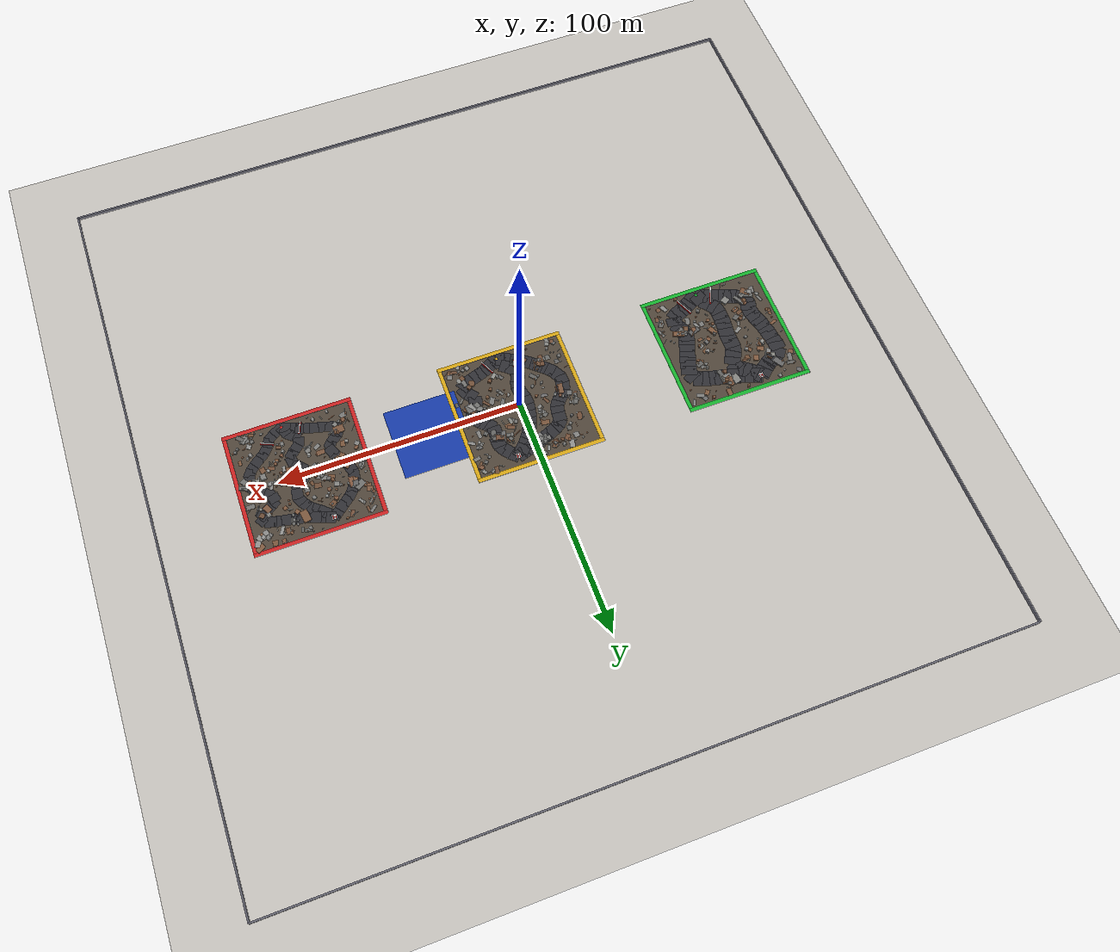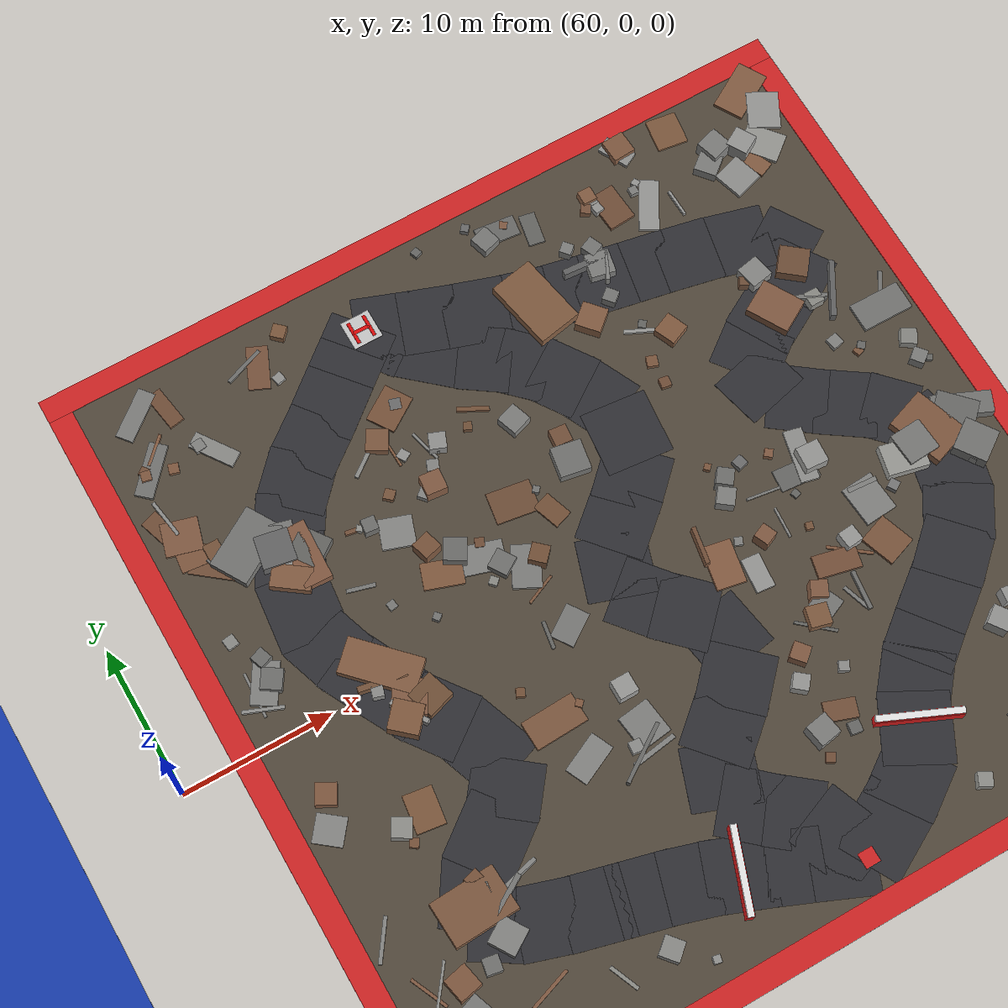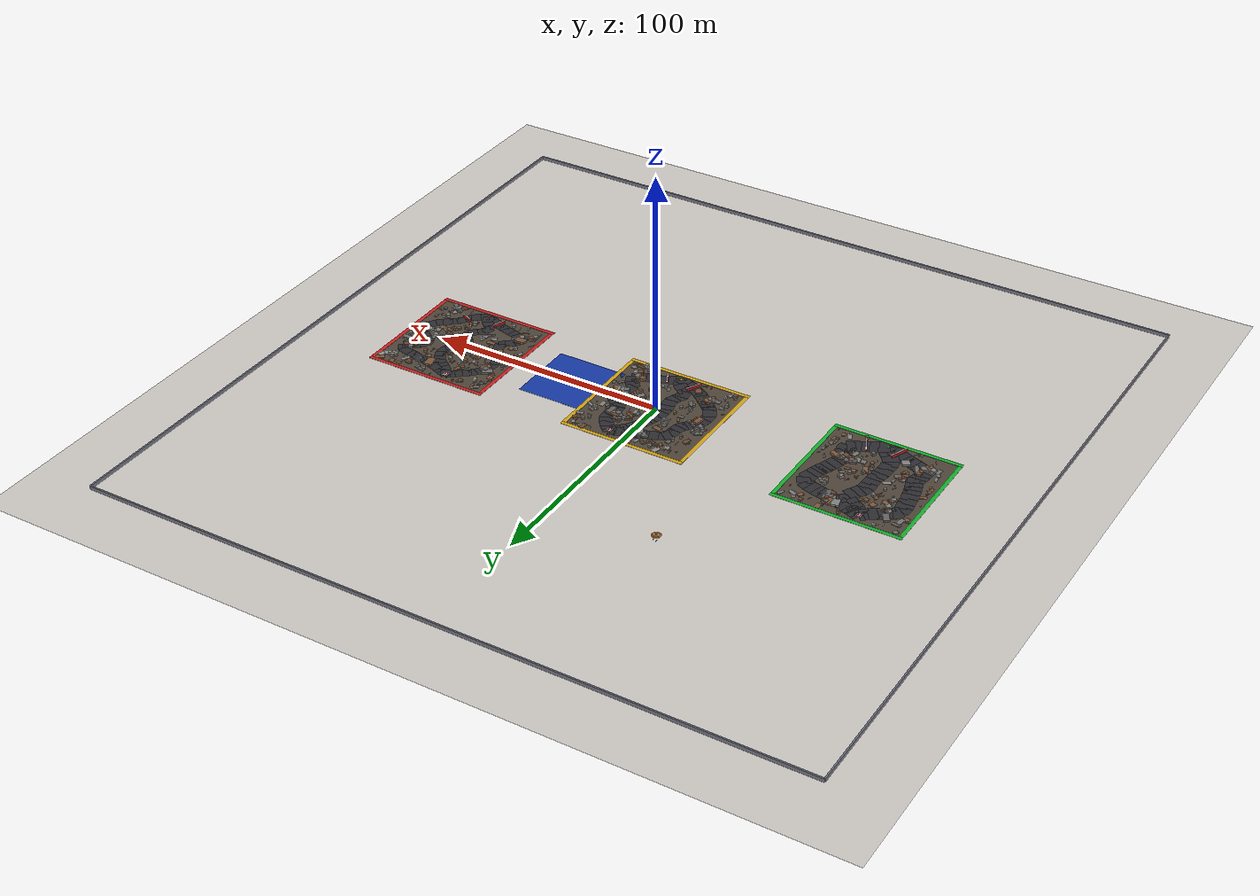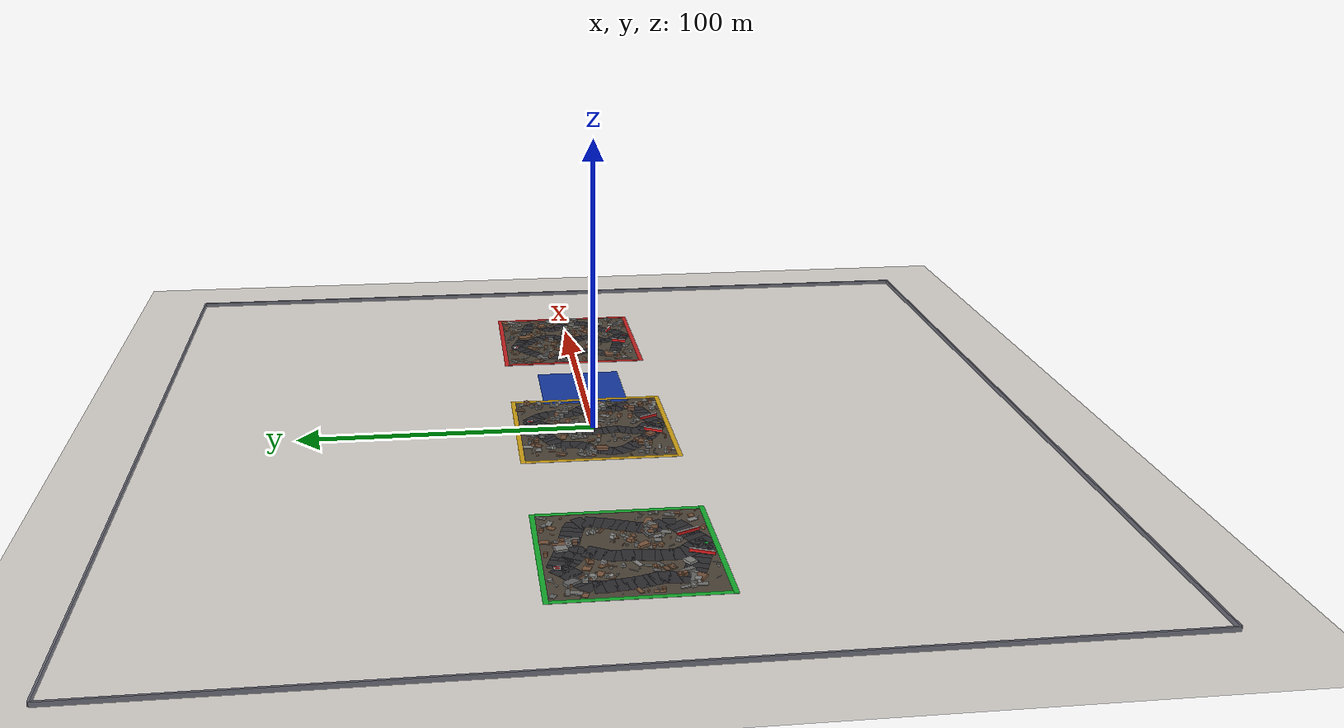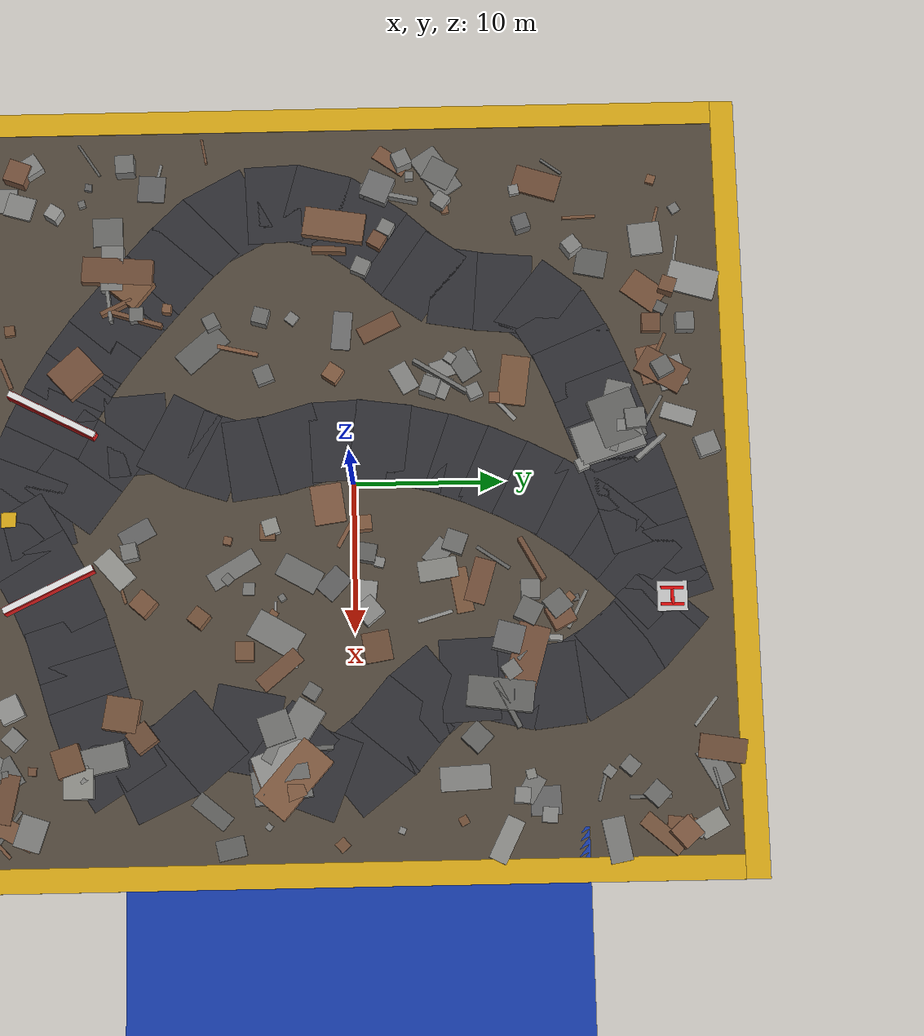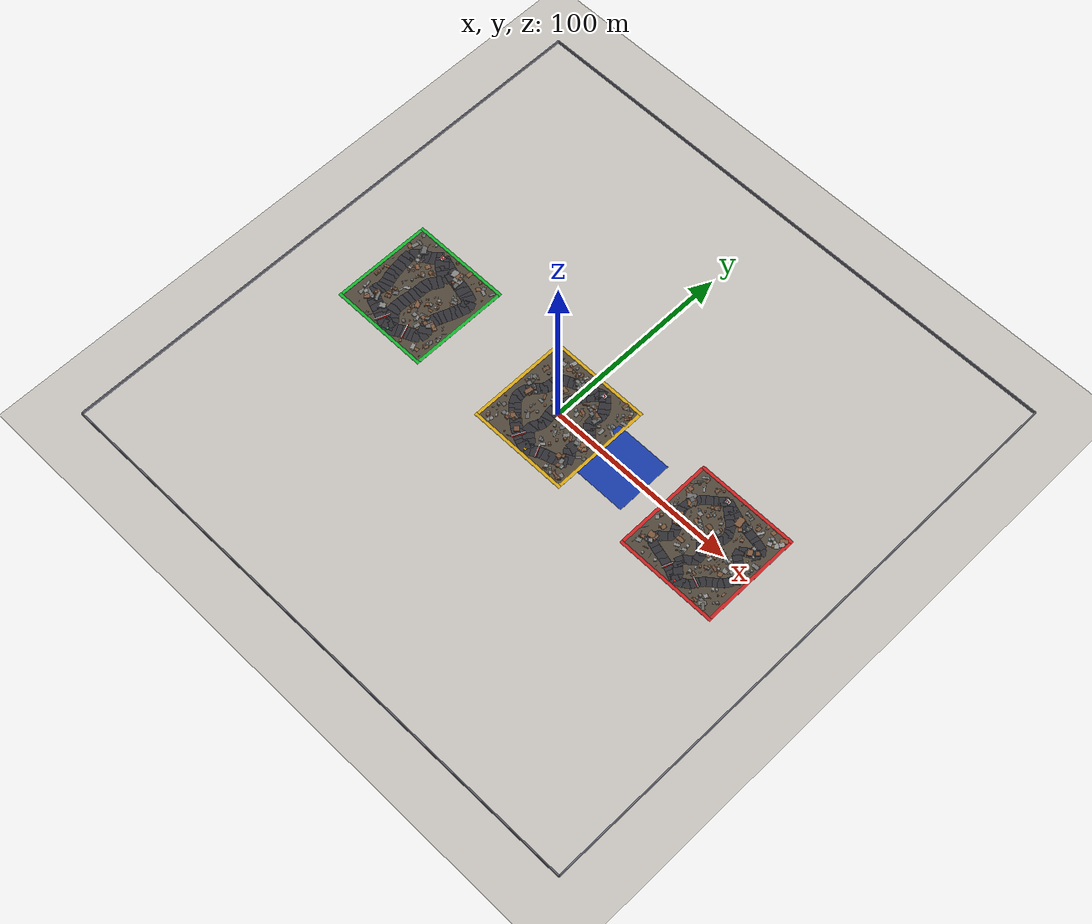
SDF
<sdf version="1.6">
 <world name="navitas_arena">
  <physics type="ode">
   <max_step_size>0.001</max_step_size>
   <real_time_factor>1</real_time_factor>
   <gravity>0 0 -9.8</gravity>
  </physics>
  <wind><linear_velocity>7.5000 -3.0000 0.4000</linear_velocity></wind>
  <scene>
   <ambient>0.5500 0.5500 0.5200 1.0000</ambient>
   <background>0.6800 0.6200 0.5200 1.0000</background>
   <shadows>false</shadows>
   <fog>
    <type>exp</type>
    <color>0.6200 0.5600 0.4600 1.0000</color>
    <start>20.00</start>
    <end>110.00</end>
    <density>0.01200</density>
   </fog>
  </scene>
  <light name="sun" type="directional">
   <cast_shadows>false</cast_shadows>
   <pose>0 0 120 0 0 0</pose>
   <diffuse>0.8800 0.8200 0.6800 1.0000</diffuse>
   <specular>0.1 0.1 0.1 1</specular>
   <attenuation>
    <range>1200</range>
    <constant>0.9</constant>
    <linear>0.01</linear>
    <quadratic>0.001</quadratic>
   </attenuation>
   <direction>-0.3500 0.3000 -0.8500</direction>
  </light>
  <model name="ground_plane">
   <static>true</static>
   <link name="link">
    <collision name="collision">
     <geometry><plane><normal>0 0 1</normal><size>400 400</size></plane></geometry>
     <surface><friction><ode><mu>0.550</mu><mu2>0.550</mu2></ode></friction></surface>
    </collision>
    <visual name="visual">
     <cast_shadows>false</cast_shadows>
     <geometry><plane><normal>0 0 1</normal><size>400 400</size></plane></geometry>
     <material><ambient>0.450 0.400 0.320 1</ambient><diffuse>0.450 0.400 0.320 1</diffuse></material>
    </visual>
   </link>
  </model>
  <model name="ub_N">
   <static>true</static>
   <pose>0.000 150.000 0.750 0 0 0.000</pose>
   <link name="link">
    <collision name="col"><geometry><box><size>300.000 0.600 1.500</size></box></geometry></collision>
    <visual name="vis">
     <geometry><box><size>300.000 0.600 1.500</size></box></geometry>
     <material><ambient>0.45 0.45 0.50 1</ambient><diffuse>0.45 0.45 0.50 1</diffuse></material>
    </visual>
   </link>
  </model>
  <model name="ub_S">
   <static>true</static>
   <pose>0.000 -150.000 0.750 0 0 0.000</pose>
   <link name="link">
    <collision name="col"><geometry><box><size>300.000 0.600 1.500</size></box></geometry></collision>
    <visual name="vis">
     <geometry><box><size>300.000 0.600 1.500</size></box></geometry>
     <material><ambient>0.45 0.45 0.50 1</ambient><diffuse>0.45 0.45 0.50 1</diffuse></material>
    </visual>
   </link>
  </model>
  <model name="ub_W">
   <static>true</static>
   <pose>-150.000 0.000 0.750 0 0 0.000</pose>
   <link name="link">
    <collision name="col"><geometry><box><size>0.600 300.000 1.500</size></box></geometry></collision>
    <visual name="vis">
     <geometry><box><size>0.600 300.000 1.500</size></box></geometry>
     <material><ambient>0.45 0.45 0.50 1</ambient><diffuse>0.45 0.45 0.50 1</diffuse></material>
    </visual>
   </link>
  </model>
  <model name="ub_E">
   <static>true</static>
   <pose>150.000 0.000 0.750 0 0 0.000</pose>
   <link name="link">
    <collision name="col"><geometry><box><size>0.600 300.000 1.500</size></box></geometry></collision>
    <visual name="vis">
     <geometry><box><size>0.600 300.000 1.500</size></box></geometry>
     <material><ambient>0.45 0.45 0.50 1</ambient><diffuse>0.45 0.45 0.50 1</diffuse></material>
    </visual>
   </link>
  </model>
  <model name="landing">
   <static>true</static>
   <pose>38.000 0.000 0.010 0 0 0.000</pose>
   <link name="link">
    <collision name="col"><geometry><box><size>30.000 30.000 0.020</size></box></geometry></collision>
    <visual name="vis">
     <geometry><box><size>30.000 30.000 0.020</size></box></geometry>
     <material><ambient>0.10 0.25 0.70 1</ambient><diffuse>0.10 0.25 0.70 1</diffuse></material>
    </visual>
   </link>
  </model>
  <model name="gd_kolay">
   <static>true</static>
   <pose>-90.000 0.000 0.010 0 0 0.000</pose>
   <link name="link">
    <collision name="col"><geometry><box><size>50.000 50.000 0.020</size></box></geometry></collision>
    <visual name="vis">
     <geometry><box><size>50.000 50.000 0.020</size></box></geometry>
     <material><ambient>0.34 0.30 0.25 1</ambient><diffuse>0.34 0.30 0.25 1</diffuse></material>
    </visual>
   </link>
  </model>
  <model name="brd_kolay_N">
   <static>true</static>
   <pose>-90.000 25.800 0.040 0 0 0.000</pose>
   <link name="link">
    <collision name="col"><geometry><box><size>53.200 1.600 0.080</size></box></geometry></collision>
    <visual name="vis">
     <geometry><box><size>53.200 1.600 0.080</size></box></geometry>
     <material><ambient>0.10 0.75 0.20 1</ambient><diffuse>0.10 0.75 0.20 1</diffuse></material>
    </visual>
   </link>
  </model>
  <model name="brd_kolay_S">
   <static>true</static>
   <pose>-90.000 -25.800 0.040 0 0 0.000</pose>
   <link name="link">
    <collision name="col"><geometry><box><size>53.200 1.600 0.080</size></box></geometry></collision>
    <visual name="vis">
     <geometry><box><size>53.200 1.600 0.080</size></box></geometry>
     <material><ambient>0.10 0.75 0.20 1</ambient><diffuse>0.10 0.75 0.20 1</diffuse></material>
    </visual>
   </link>
  </model>
  <model name="brd_kolay_W">
   <static>true</static>
   <pose>-115.800 0.000 0.040 0 0 0.000</pose>
   <link name="link">
    <collision name="col"><geometry><box><size>1.600 50.000 0.080</size></box></geometry></collision>
    <visual name="vis">
     <geometry><box><size>1.600 50.000 0.080</size></box></geometry>
     <material><ambient>0.10 0.75 0.20 1</ambient><diffuse>0.10 0.75 0.20 1</diffuse></material>
    </visual>
   </link>
  </model>
  <model name="brd_kolay_E">
   <static>true</static>
   <pose>-64.200 0.000 0.040 0 0 0.000</pose>
   <link name="link">
    <collision name="col"><geometry><box><size>1.600 50.000 0.080</size></box></geometry></collision>
    <visual name="vis">
     <geometry><box><size>1.600 50.000 0.080</size></box></geometry>
     <material><ambient>0.10 0.75 0.20 1</ambient><diffuse>0.10 0.75 0.20 1</diffuse></material>
    </visual>
   </link>
  </model>
  <model name="road_kolay_1_0">
   <static>true</static>
   <pose>-88.722 -22.399 0.040 0 0 2.753</pose>
   <link name="link">
    <collision name="col"><geometry><box><size>4.071 6.600 0.020</size></box></geometry></collision>
    <visual name="vis">
     <geometry><box><size>4.071 6.600 0.020</size></box></geometry>
     <material><ambient>0.20 0.20 0.22 1</ambient><diffuse>0.20 0.20 0.22 1</diffuse></material>
    </visual>
   </link>
  </model>
  <model name="road_kolay_1_1">
   <static>true</static>
   <pose>-91.548 -21.236 0.040 0 0 2.750</pose>
   <link name="link">
    <collision name="col"><geometry><box><size>3.842 6.600 0.020</size></box></geometry></collision>
    <visual name="vis">
     <geometry><box><size>3.842 6.600 0.020</size></box></geometry>
     <material><ambient>0.20 0.20 0.22 1</ambient><diffuse>0.20 0.20 0.22 1</diffuse></material>
    </visual>
   </link>
  </model>
  <model name="road_kolay_1_2">
   <static>true</static>
   <pose>-94.299 -20.087 0.040 0 0 2.742</pose>
   <link name="link">
    <collision name="col"><geometry><box><size>3.920 6.600 0.020</size></box></geometry></collision>
    <visual name="vis">
     <geometry><box><size>3.920 6.600 0.020</size></box></geometry>
     <material><ambient>0.20 0.20 0.22 1</ambient><diffuse>0.20 0.20 0.22 1</diffuse></material>
    </visual>
   </link>
  </model>
  <model name="road_kolay_1_3">
   <static>true</static>
   <pose>-96.862 -19.058 0.040 0 0 2.781</pose>
   <link name="link">
    <collision name="col"><geometry><box><size>3.406 6.600 0.020</size></box></geometry></collision>
    <visual name="vis">
     <geometry><box><size>3.406 6.600 0.020</size></box></geometry>
     <material><ambient>0.20 0.20 0.22 1</ambient><diffuse>0.20 0.20 0.22 1</diffuse></material>
    </visual>
   </link>
  </model>
  <model name="road_kolay_1_4">
   <static>true</static>
   <pose>-99.350 -18.160 0.040 0 0 2.809</pose>
   <link name="link">
    <collision name="col"><geometry><box><size>3.684 6.600 0.020</size></box></geometry></collision>
    <visual name="vis">
     <geometry><box><size>3.684 6.600 0.020</size></box></geometry>
     <material><ambient>0.20 0.20 0.22 1</ambient><diffuse>0.20 0.20 0.22 1</diffuse></material>
    </visual>
   </link>
  </model>
  <model name="road_kolay_1_5">
   <static>true</static>
   <pose>-101.924 -17.214 0.040 0 0 2.769</pose>
   <link name="link">
    <collision name="col"><geometry><box><size>3.601 6.600 0.020</size></box></geometry></collision>
    <visual name="vis">
     <geometry><box><size>3.601 6.600 0.020</size></box></geometry>
     <material><ambient>0.20 0.20 0.22 1</ambient><diffuse>0.20 0.20 0.22 1</diffuse></material>
    </visual>
   </link>
  </model>
  <model name="road_kolay_1_6">
   <static>true</static>
   <pose>-104.519 -15.861 0.040 0 0 2.570</pose>
   <link name="link">
    <collision name="col"><geometry><box><size>4.082 6.600 0.020</size></box></geometry></collision>
    <visual name="vis">
     <geometry><box><size>4.082 6.600 0.020</size></box></geometry>
     <material><ambient>0.20 0.20 0.22 1</ambient><diffuse>0.20 0.20 0.22 1</diffuse></material>
    </visual>
   </link>
  </model>
  <model name="road_kolay_1_7">
   <static>true</static>
   <pose>-106.114 -13.690 0.040 0 0 1.764</pose>
   <link name="link">
    <collision name="col"><geometry><box><size>3.570 6.600 0.020</size></box></geometry></collision>
    <visual name="vis">
     <geometry><box><size>3.570 6.600 0.020</size></box></geometry>
     <material><ambient>0.20 0.20 0.22 1</ambient><diffuse>0.20 0.20 0.22 1</diffuse></material>
    </visual>
   </link>
  </model>
  <model name="road_kolay_1_8">
   <static>true</static>
   <pose>-105.993 -10.910 0.040 0 0 1.319</pose>
   <link name="link">
    <collision name="col"><geometry><box><size>3.936 6.600 0.020</size></box></geometry></collision>
    <visual name="vis">
     <geometry><box><size>3.936 6.600 0.020</size></box></geometry>
     <material><ambient>0.20 0.20 0.22 1</ambient><diffuse>0.20 0.20 0.22 1</diffuse></material>
    </visual>
   </link>
  </model>
  <model name="road_kolay_1_9">
   <static>true</static>
   <pose>-105.671 -8.137 0.040 0 0 1.615</pose>
   <link name="link">
    <collision name="col"><geometry><box><size>3.509 6.600 0.020</size></box></geometry></collision>
    <visual name="vis">
     <geometry><box><size>3.509 6.600 0.020</size></box></geometry>
     <material><ambient>0.20 0.20 0.22 1</ambient><diffuse>0.20 0.20 0.22 1</diffuse></material>
    </visual>
   </link>
  </model>
  <model name="road_kolay_1_10">
   <static>true</static>
   <pose>-106.069 -5.667 0.040 0 0 1.855</pose>
   <link name="link">
    <collision name="col"><geometry><box><size>3.331 6.600 0.020</size></box></geometry></collision>
    <visual name="vis">
     <geometry><box><size>3.331 6.600 0.020</size></box></geometry>
     <material><ambient>0.20 0.20 0.22 1</ambient><diffuse>0.20 0.20 0.22 1</diffuse></material>
    </visual>
   </link>
  </model>
  <model name="road_kolay_1_11">
   <static>true</static>
   <pose>-106.790 -3.333 0.040 0 0 1.886</pose>
   <link name="link">
    <collision name="col"><geometry><box><size>3.355 6.600 0.020</size></box></geometry></collision>
    <visual name="vis">
     <geometry><box><size>3.355 6.600 0.020</size></box></geometry>
     <material><ambient>0.20 0.20 0.22 1</ambient><diffuse>0.20 0.20 0.22 1</diffuse></material>
    </visual>
   </link>
  </model>
  <model name="road_kolay_1_12">
   <static>true</static>
   <pose>-107.472 -0.883 0.040 0 0 1.801</pose>
   <link name="link">
    <collision name="col"><geometry><box><size>3.536 6.600 0.020</size></box></geometry></collision>
    <visual name="vis">
     <geometry><box><size>3.536 6.600 0.020</size></box></geometry>
     <material><ambient>0.20 0.20 0.22 1</ambient><diffuse>0.20 0.20 0.22 1</diffuse></material>
    </visual>
   </link>
  </model>
  <model name="road_kolay_1_13">
   <static>true</static>
   <pose>-108.025 1.800 0.040 0 0 1.749</pose>
   <link name="link">
    <collision name="col"><geometry><box><size>3.745 6.600 0.020</size></box></geometry></collision>
    <visual name="vis">
     <geometry><box><size>3.745 6.600 0.020</size></box></geometry>
     <material><ambient>0.20 0.20 0.22 1</ambient><diffuse>0.20 0.20 0.22 1</diffuse></material>
    </visual>
   </link>
  </model>
  <model name="road_kolay_1_14">
   <static>true</static>
   <pose>-108.442 4.600 0.040 0 0 1.688</pose>
   <link name="link">
    <collision name="col"><geometry><box><size>3.719 6.600 0.020</size></box></geometry></collision>
    <visual name="vis">
     <geometry><box><size>3.719 6.600 0.020</size></box></geometry>
     <material><ambient>0.20 0.20 0.22 1</ambient><diffuse>0.20 0.20 0.22 1</diffuse></material>
    </visual>
   </link>
  </model>
  <model name="road_kolay_1_15">
   <static>true</static>
   <pose>-108.822 7.460 0.040 0 0 1.717</pose>
   <link name="link">
    <collision name="col"><geometry><box><size>3.851 6.600 0.020</size></box></geometry></collision>
    <visual name="vis">
     <geometry><box><size>3.851 6.600 0.020</size></box></geometry>
     <material><ambient>0.20 0.20 0.22 1</ambient><diffuse>0.20 0.20 0.22 1</diffuse></material>
    </visual>
   </link>
  </model>
  <model name="road_kolay_1_16">
   <static>true</static>
   <pose>-109.058 10.340 0.040 0 0 1.586</pose>
   <link name="link">
    <collision name="col"><geometry><box><size>3.740 6.600 0.020</size></box></geometry></collision>
    <visual name="vis">
     <geometry><box><size>3.740 6.600 0.020</size></box></geometry>
     <material><ambient>0.20 0.20 0.22 1</ambient><diffuse>0.20 0.20 0.22 1</diffuse></material>
    </visual>
   </link>
  </model>
  <model name="road_kolay_1_17">
   <static>true</static>
   <pose>-107.990 13.129 0.040 0 0 0.898</pose>
   <link name="link">
    <collision name="col"><geometry><box><size>4.399 6.600 0.020</size></box></geometry></collision>
    <visual name="vis">
     <geometry><box><size>4.399 6.600 0.020</size></box></geometry>
     <material><ambient>0.20 0.20 0.22 1</ambient><diffuse>0.20 0.20 0.22 1</diffuse></material>
    </visual>
   </link>
  </model>
  <model name="road_kolay_1_18">
   <static>true</static>
   <pose>-105.693 15.135 0.040 0 0 0.486</pose>
   <link name="link">
    <collision name="col"><geometry><box><size>3.630 6.600 0.020</size></box></geometry></collision>
    <visual name="vis">
     <geometry><box><size>3.630 6.600 0.020</size></box></geometry>
     <material><ambient>0.20 0.20 0.22 1</ambient><diffuse>0.20 0.20 0.22 1</diffuse></material>
    </visual>
   </link>
  </model>
  <model name="road_kolay_1_19">
   <static>true</static>
   <pose>-103.295 16.352 0.040 0 0 0.452</pose>
   <link name="link">
    <collision name="col"><geometry><box><size>3.551 6.600 0.020</size></box></geometry></collision>
    <visual name="vis">
     <geometry><box><size>3.551 6.600 0.020</size></box></geometry>
     <material><ambient>0.20 0.20 0.22 1</ambient><diffuse>0.20 0.20 0.22 1</diffuse></material>
    </visual>
   </link>
  </model>
  <model name="road_kolay_1_20">
   <static>true</static>
   <pose>-100.968 17.729 0.040 0 0 0.613</pose>
   <link name="link">
    <collision name="col"><geometry><box><size>3.675 6.600 0.020</size></box></geometry></collision>
    <visual name="vis">
     <geometry><box><size>3.675 6.600 0.020</size></box></geometry>
     <material><ambient>0.20 0.20 0.22 1</ambient><diffuse>0.20 0.20 0.22 1</diffuse></material>
    </visual>
   </link>
  </model>
  <model name="road_kolay_1_21">
   <static>true</static>
   <pose>-98.831 19.461 0.040 0 0 0.750</pose>
   <link name="link">
    <collision name="col"><geometry><box><size>3.639 6.600 0.020</size></box></geometry></collision>
    <visual name="vis">
     <geometry><box><size>3.639 6.600 0.020</size></box></geometry>
     <material><ambient>0.20 0.20 0.22 1</ambient><diffuse>0.20 0.20 0.22 1</diffuse></material>
    </visual>
   </link>
  </model>
  <model name="road_kolay_1_22">
   <static>true</static>
   <pose>-97.514 20.697 0.040 0 0 0.765</pose>
   <link name="link">
    <collision name="col"><geometry><box><size>1.774 6.600 0.020</size></box></geometry></collision>
    <visual name="vis">
     <geometry><box><size>1.774 6.600 0.020</size></box></geometry>
     <material><ambient>0.20 0.20 0.22 1</ambient><diffuse>0.20 0.20 0.22 1</diffuse></material>
    </visual>
   </link>
  </model>
  <model name="road_kolay_2_0">
   <static>true</static>
   <pose>-87.872 -21.250 0.040 0 0 1.910</pose>
   <link name="link">
    <collision name="col"><geometry><box><size>4.612 6.600 0.020</size></box></geometry></collision>
    <visual name="vis">
     <geometry><box><size>4.612 6.600 0.020</size></box></geometry>
     <material><ambient>0.20 0.20 0.22 1</ambient><diffuse>0.20 0.20 0.22 1</diffuse></material>
    </visual>
   </link>
  </model>
  <model name="road_kolay_2_1">
   <static>true</static>
   <pose>-89.497 -18.484 0.040 0 0 2.352</pose>
   <link name="link">
    <collision name="col"><geometry><box><size>3.761 6.600 0.020</size></box></geometry></collision>
    <visual name="vis">
     <geometry><box><size>3.761 6.600 0.020</size></box></geometry>
     <material><ambient>0.20 0.20 0.22 1</ambient><diffuse>0.20 0.20 0.22 1</diffuse></material>
    </visual>
   </link>
  </model>
  <model name="road_kolay_2_2">
   <static>true</static>
   <pose>-91.456 -16.234 0.040 0 0 2.228</pose>
   <link name="link">
    <collision name="col"><geometry><box><size>4.017 6.600 0.020</size></box></geometry></collision>
    <visual name="vis">
     <geometry><box><size>4.017 6.600 0.020</size></box></geometry>
     <material><ambient>0.20 0.20 0.22 1</ambient><diffuse>0.20 0.20 0.22 1</diffuse></material>
    </visual>
   </link>
  </model>
  <model name="road_kolay_2_3">
   <static>true</static>
   <pose>-92.635 -13.690 0.040 0 0 1.743</pose>
   <link name="link">
    <collision name="col"><geometry><box><size>3.559 6.600 0.020</size></box></geometry></collision>
    <visual name="vis">
     <geometry><box><size>3.559 6.600 0.020</size></box></geometry>
     <material><ambient>0.20 0.20 0.22 1</ambient><diffuse>0.20 0.20 0.22 1</diffuse></material>
    </visual>
   </link>
  </model>
  <model name="road_kolay_2_4">
   <static>true</static>
   <pose>-92.841 -10.910 0.040 0 0 1.556</pose>
   <link name="link">
    <collision name="col"><geometry><box><size>3.840 6.600 0.020</size></box></geometry></collision>
    <visual name="vis">
     <geometry><box><size>3.840 6.600 0.020</size></box></geometry>
     <material><ambient>0.20 0.20 0.22 1</ambient><diffuse>0.20 0.20 0.22 1</diffuse></material>
    </visual>
   </link>
  </model>
  <model name="road_kolay_2_5">
   <static>true</static>
   <pose>-92.729 -8.020 0.040 0 0 1.507</pose>
   <link name="link">
    <collision name="col"><geometry><box><size>3.746 6.600 0.020</size></box></geometry></collision>
    <visual name="vis">
     <geometry><box><size>3.746 6.600 0.020</size></box></geometry>
     <material><ambient>0.20 0.20 0.22 1</ambient><diffuse>0.20 0.20 0.22 1</diffuse></material>
    </visual>
   </link>
  </model>
  <model name="road_kolay_2_6">
   <static>true</static>
   <pose>-92.428 -5.200 0.040 0 0 1.422</pose>
   <link name="link">
    <collision name="col"><geometry><box><size>3.731 6.600 0.020</size></box></geometry></collision>
    <visual name="vis">
     <geometry><box><size>3.731 6.600 0.020</size></box></geometry>
     <material><ambient>0.20 0.20 0.22 1</ambient><diffuse>0.20 0.20 0.22 1</diffuse></material>
    </visual>
   </link>
  </model>
  <model name="road_kolay_2_7">
   <static>true</static>
   <pose>-92.028 -2.400 0.040 0 0 1.436</pose>
   <link name="link">
    <collision name="col"><geometry><box><size>3.726 6.600 0.020</size></box></geometry></collision>
    <visual name="vis">
     <geometry><box><size>3.726 6.600 0.020</size></box></geometry>
     <material><ambient>0.20 0.20 0.22 1</ambient><diffuse>0.20 0.20 0.22 1</diffuse></material>
    </visual>
   </link>
  </model>
  <model name="road_kolay_2_8">
   <static>true</static>
   <pose>-91.830 0.400 0.040 0 0 1.565</pose>
   <link name="link">
    <collision name="col"><geometry><box><size>3.700 6.600 0.020</size></box></geometry></collision>
    <visual name="vis">
     <geometry><box><size>3.700 6.600 0.020</size></box></geometry>
     <material><ambient>0.20 0.20 0.22 1</ambient><diffuse>0.20 0.20 0.22 1</diffuse></material>
    </visual>
   </link>
  </model>
  <model name="road_kolay_2_9">
   <static>true</static>
   <pose>-91.807 3.200 0.040 0 0 1.559</pose>
   <link name="link">
    <collision name="col"><geometry><box><size>3.700 6.600 0.020</size></box></geometry></collision>
    <visual name="vis">
     <geometry><box><size>3.700 6.600 0.020</size></box></geometry>
     <material><ambient>0.20 0.20 0.22 1</ambient><diffuse>0.20 0.20 0.22 1</diffuse></material>
    </visual>
   </link>
  </model>
  <model name="road_kolay_2_10">
   <static>true</static>
   <pose>-91.428 5.898 0.040 0 0 1.298</pose>
   <link name="link">
    <collision name="col"><geometry><box><size>3.595 6.600 0.020</size></box></geometry></collision>
    <visual name="vis">
     <geometry><box><size>3.595 6.600 0.020</size></box></geometry>
     <material><ambient>0.20 0.20 0.22 1</ambient><diffuse>0.20 0.20 0.22 1</diffuse></material>
    </visual>
   </link>
  </model>
  <model name="road_kolay_2_11">
   <static>true</static>
   <pose>-90.288 8.426 0.040 0 0 1.007</pose>
   <link name="link">
    <collision name="col"><geometry><box><size>3.811 6.600 0.020</size></box></geometry></collision>
    <visual name="vis">
     <geometry><box><size>3.811 6.600 0.020</size></box></geometry>
     <material><ambient>0.20 0.20 0.22 1</ambient><diffuse>0.20 0.20 0.22 1</diffuse></material>
    </visual>
   </link>
  </model>
  <model name="road_kolay_2_12">
   <static>true</static>
   <pose>-88.901 10.817 0.040 0 0 1.087</pose>
   <link name="link">
    <collision name="col"><geometry><box><size>3.523 6.600 0.020</size></box></geometry></collision>
    <visual name="vis">
     <geometry><box><size>3.523 6.600 0.020</size></box></geometry>
     <material><ambient>0.20 0.20 0.22 1</ambient><diffuse>0.20 0.20 0.22 1</diffuse></material>
    </visual>
   </link>
  </model>
  <model name="road_kolay_2_13">
   <static>true</static>
   <pose>-88.925 13.350 0.040 0 0 2.004</pose>
   <link name="link">
    <collision name="col"><geometry><box><size>3.923 6.600 0.020</size></box></geometry></collision>
    <visual name="vis">
     <geometry><box><size>3.923 6.600 0.020</size></box></geometry>
     <material><ambient>0.20 0.20 0.22 1</ambient><diffuse>0.20 0.20 0.22 1</diffuse></material>
    </visual>
   </link>
  </model>
  <model name="road_kolay_2_14">
   <static>true</static>
   <pose>-90.728 15.444 0.040 0 0 2.588</pose>
   <link name="link">
    <collision name="col"><geometry><box><size>3.649 6.600 0.020</size></box></geometry></collision>
    <visual name="vis">
     <geometry><box><size>3.649 6.600 0.020</size></box></geometry>
     <material><ambient>0.20 0.20 0.22 1</ambient><diffuse>0.20 0.20 0.22 1</diffuse></material>
    </visual>
   </link>
  </model>
  <model name="road_kolay_2_15">
   <static>true</static>
   <pose>-92.929 16.833 0.040 0 0 2.568</pose>
   <link name="link">
    <collision name="col"><geometry><box><size>3.355 6.600 0.020</size></box></geometry></collision>
    <visual name="vis">
     <geometry><box><size>3.355 6.600 0.020</size></box></geometry>
     <material><ambient>0.20 0.20 0.22 1</ambient><diffuse>0.20 0.20 0.22 1</diffuse></material>
    </visual>
   </link>
  </model>
  <model name="road_kolay_2_16">
   <static>true</static>
   <pose>-95.205 18.815 0.040 0 0 2.329</pose>
   <link name="link">
    <collision name="col"><geometry><box><size>4.523 6.600 0.020</size></box></geometry></collision>
    <visual name="vis">
     <geometry><box><size>4.523 6.600 0.020</size></box></geometry>
     <material><ambient>0.20 0.20 0.22 1</ambient><diffuse>0.20 0.20 0.22 1</diffuse></material>
    </visual>
   </link>
  </model>
  <model name="road_kolay_2_17">
   <static>true</static>
   <pose>-96.825 20.565 0.040 0 0 2.280</pose>
   <link name="link">
    <collision name="col"><geometry><box><size>2.047 6.600 0.020</size></box></geometry></collision>
    <visual name="vis">
     <geometry><box><size>2.047 6.600 0.020</size></box></geometry>
     <material><ambient>0.20 0.20 0.22 1</ambient><diffuse>0.20 0.20 0.22 1</diffuse></material>
    </visual>
   </link>
  </model>
  <model name="road_kolay_3_0">
   <static>true</static>
   <pose>-85.681 -22.070 0.040 0 0 0.534</pose>
   <link name="link">
    <collision name="col"><geometry><box><size>4.555 6.600 0.020</size></box></geometry></collision>
    <visual name="vis">
     <geometry><box><size>4.555 6.600 0.020</size></box></geometry>
     <material><ambient>0.20 0.20 0.22 1</ambient><diffuse>0.20 0.20 0.22 1</diffuse></material>
    </visual>
   </link>
  </model>
  <model name="road_kolay_3_1">
   <static>true</static>
   <pose>-82.699 -20.320 0.040 0 0 0.527</pose>
   <link name="link">
    <collision name="col"><geometry><box><size>4.160 6.600 0.020</size></box></geometry></collision>
    <visual name="vis">
     <geometry><box><size>4.160 6.600 0.020</size></box></geometry>
     <material><ambient>0.20 0.20 0.22 1</ambient><diffuse>0.20 0.20 0.22 1</diffuse></material>
    </visual>
   </link>
  </model>
  <model name="road_kolay_3_2">
   <static>true</static>
   <pose>-80.069 -18.930 0.040 0 0 0.437</pose>
   <link name="link">
    <collision name="col"><geometry><box><size>3.596 6.600 0.020</size></box></geometry></collision>
    <visual name="vis">
     <geometry><box><size>3.596 6.600 0.020</size></box></geometry>
     <material><ambient>0.20 0.20 0.22 1</ambient><diffuse>0.20 0.20 0.22 1</diffuse></material>
    </visual>
   </link>
  </model>
  <model name="road_kolay_3_3">
   <static>true</static>
   <pose>-77.470 -17.758 0.040 0 0 0.412</pose>
   <link name="link">
    <collision name="col"><geometry><box><size>3.907 6.600 0.020</size></box></geometry></collision>
    <visual name="vis">
     <geometry><box><size>3.907 6.600 0.020</size></box></geometry>
     <material><ambient>0.20 0.20 0.22 1</ambient><diffuse>0.20 0.20 0.22 1</diffuse></material>
    </visual>
   </link>
  </model>
  <model name="road_kolay_3_4">
   <static>true</static>
   <pose>-74.999 -16.469 0.040 0 0 0.561</pose>
   <link name="link">
    <collision name="col"><geometry><box><size>3.482 6.600 0.020</size></box></geometry></collision>
    <visual name="vis">
     <geometry><box><size>3.482 6.600 0.020</size></box></geometry>
     <material><ambient>0.20 0.20 0.22 1</ambient><diffuse>0.20 0.20 0.22 1</diffuse></material>
    </visual>
   </link>
  </model>
  <model name="road_kolay_3_5">
   <static>true</static>
   <pose>-73.725 -14.317 0.040 0 0 1.448</pose>
   <link name="link">
    <collision name="col"><geometry><box><size>3.853 6.600 0.020</size></box></geometry></collision>
    <visual name="vis">
     <geometry><box><size>3.853 6.600 0.020</size></box></geometry>
     <material><ambient>0.20 0.20 0.22 1</ambient><diffuse>0.20 0.20 0.22 1</diffuse></material>
    </visual>
   </link>
  </model>
  <model name="road_kolay_3_6">
   <static>true</static>
   <pose>-74.253 -11.639 0.040 0 0 2.099</pose>
   <link name="link">
    <collision name="col"><geometry><box><size>3.709 6.600 0.020</size></box></geometry></collision>
    <visual name="vis">
     <geometry><box><size>3.709 6.600 0.020</size></box></geometry>
     <material><ambient>0.20 0.20 0.22 1</ambient><diffuse>0.20 0.20 0.22 1</diffuse></material>
    </visual>
   </link>
  </model>
  <model name="road_kolay_3_7">
   <static>true</static>
   <pose>-75.410 -9.213 0.040 0 0 1.925</pose>
   <link name="link">
    <collision name="col"><geometry><box><size>3.487 6.600 0.020</size></box></geometry></collision>
    <visual name="vis">
     <geometry><box><size>3.487 6.600 0.020</size></box></geometry>
     <material><ambient>0.20 0.20 0.22 1</ambient><diffuse>0.20 0.20 0.22 1</diffuse></material>
    </visual>
   </link>
  </model>
  <model name="road_kolay_3_8">
   <static>true</static>
   <pose>-75.487 -6.250 0.040 0 0 1.362</pose>
   <link name="link">
    <collision name="col"><geometry><box><size>4.478 6.600 0.020</size></box></geometry></collision>
    <visual name="vis">
     <geometry><box><size>4.478 6.600 0.020</size></box></geometry>
     <material><ambient>0.20 0.20 0.22 1</ambient><diffuse>0.20 0.20 0.22 1</diffuse></material>
    </visual>
   </link>
  </model>
  <model name="road_kolay_3_9">
   <static>true</static>
   <pose>-74.643 -3.333 0.040 0 0 1.186</pose>
   <link name="link">
    <collision name="col"><geometry><box><size>3.418 6.600 0.020</size></box></geometry></collision>
    <visual name="vis">
     <geometry><box><size>3.418 6.600 0.020</size></box></geometry>
     <material><ambient>0.20 0.20 0.22 1</ambient><diffuse>0.20 0.20 0.22 1</diffuse></material>
    </visual>
   </link>
  </model>
  <model name="road_kolay_3_10">
   <static>true</static>
   <pose>-73.744 -1.000 0.040 0 0 1.221</pose>
   <link name="link">
    <collision name="col"><geometry><box><size>3.384 6.600 0.020</size></box></geometry></collision>
    <visual name="vis">
     <geometry><box><size>3.384 6.600 0.020</size></box></geometry>
     <material><ambient>0.20 0.20 0.22 1</ambient><diffuse>0.20 0.20 0.22 1</diffuse></material>
    </visual>
   </link>
  </model>
  <model name="road_kolay_3_11">
   <static>true</static>
   <pose>-72.841 1.333 0.040 0 0 1.183</pose>
   <link name="link">
    <collision name="col"><geometry><box><size>3.421 6.600 0.020</size></box></geometry></collision>
    <visual name="vis">
     <geometry><box><size>3.421 6.600 0.020</size></box></geometry>
     <material><ambient>0.20 0.20 0.22 1</ambient><diffuse>0.20 0.20 0.22 1</diffuse></material>
    </visual>
   </link>
  </model>
  <model name="road_kolay_3_12">
   <static>true</static>
   <pose>-71.941 3.667 0.040 0 0 1.223</pose>
   <link name="link">
    <collision name="col"><geometry><box><size>3.382 6.600 0.020</size></box></geometry></collision>
    <visual name="vis">
     <geometry><box><size>3.382 6.600 0.020</size></box></geometry>
     <material><ambient>0.20 0.20 0.22 1</ambient><diffuse>0.20 0.20 0.22 1</diffuse></material>
    </visual>
   </link>
  </model>
  <model name="road_kolay_3_13">
   <static>true</static>
   <pose>-71.153 6.137 0.040 0 0 1.298</pose>
   <link name="link">
    <collision name="col"><geometry><box><size>3.607 6.600 0.020</size></box></geometry></collision>
    <visual name="vis">
     <geometry><box><size>3.607 6.600 0.020</size></box></geometry>
     <material><ambient>0.20 0.20 0.22 1</ambient><diffuse>0.20 0.20 0.22 1</diffuse></material>
    </visual>
   </link>
  </model>
  <model name="road_kolay_3_14">
   <static>true</static>
   <pose>-70.324 8.910 0.040 0 0 1.265</pose>
   <link name="link">
    <collision name="col"><geometry><box><size>3.983 6.600 0.020</size></box></geometry></collision>
    <visual name="vis">
     <geometry><box><size>3.983 6.600 0.020</size></box></geometry>
     <material><ambient>0.20 0.20 0.22 1</ambient><diffuse>0.20 0.20 0.22 1</diffuse></material>
    </visual>
   </link>
  </model>
  <model name="road_kolay_3_15">
   <static>true</static>
   <pose>-70.450 11.690 0.040 0 0 1.994</pose>
   <link name="link">
    <collision name="col"><geometry><box><size>3.774 6.600 0.020</size></box></geometry></collision>
    <visual name="vis">
     <geometry><box><size>3.774 6.600 0.020</size></box></geometry>
     <material><ambient>0.20 0.20 0.22 1</ambient><diffuse>0.20 0.20 0.22 1</diffuse></material>
    </visual>
   </link>
  </model>
  <model name="road_kolay_3_16">
   <static>true</static>
   <pose>-72.366 13.615 0.040 0 0 2.707</pose>
   <link name="link">
    <collision name="col"><geometry><box><size>3.821 6.600 0.020</size></box></geometry></collision>
    <visual name="vis">
     <geometry><box><size>3.821 6.600 0.020</size></box></geometry>
     <material><ambient>0.20 0.20 0.22 1</ambient><diffuse>0.20 0.20 0.22 1</diffuse></material>
    </visual>
   </link>
  </model>
  <model name="road_kolay_3_17">
   <static>true</static>
   <pose>-74.929 14.594 0.040 0 0 2.856</pose>
   <link name="link">
    <collision name="col"><geometry><box><size>3.483 6.600 0.020</size></box></geometry></collision>
    <visual name="vis">
     <geometry><box><size>3.483 6.600 0.020</size></box></geometry>
     <material><ambient>0.20 0.20 0.22 1</ambient><diffuse>0.20 0.20 0.22 1</diffuse></material>
    </visual>
   </link>
  </model>
  <model name="road_kolay_3_18">
   <static>true</static>
   <pose>-77.557 15.296 0.040 0 0 2.903</pose>
   <link name="link">
    <collision name="col"><geometry><box><size>3.758 6.600 0.020</size></box></geometry></collision>
    <visual name="vis">
     <geometry><box><size>3.758 6.600 0.020</size></box></geometry>
     <material><ambient>0.20 0.20 0.22 1</ambient><diffuse>0.20 0.20 0.22 1</diffuse></material>
    </visual>
   </link>
  </model>
  <model name="road_kolay_3_19">
   <static>true</static>
   <pose>-80.368 15.952 0.040 0 0 2.921</pose>
   <link name="link">
    <collision name="col"><geometry><box><size>3.816 6.600 0.020</size></box></geometry></collision>
    <visual name="vis">
     <geometry><box><size>3.816 6.600 0.020</size></box></geometry>
     <material><ambient>0.20 0.20 0.22 1</ambient><diffuse>0.20 0.20 0.22 1</diffuse></material>
    </visual>
   </link>
  </model>
  <model name="road_kolay_3_20">
   <static>true</static>
   <pose>-83.132 16.579 0.040 0 0 2.916</pose>
   <link name="link">
    <collision name="col"><geometry><box><size>3.652 6.600 0.020</size></box></geometry></collision>
    <visual name="vis">
     <geometry><box><size>3.652 6.600 0.020</size></box></geometry>
     <material><ambient>0.20 0.20 0.22 1</ambient><diffuse>0.20 0.20 0.22 1</diffuse></material>
    </visual>
   </link>
  </model>
  <model name="road_kolay_3_21">
   <static>true</static>
   <pose>-86.341 17.420 0.040 0 0 2.864</pose>
   <link name="link">
    <collision name="col"><geometry><box><size>4.784 6.600 0.020</size></box></geometry></collision>
    <visual name="vis">
     <geometry><box><size>4.784 6.600 0.020</size></box></geometry>
     <material><ambient>0.20 0.20 0.22 1</ambient><diffuse>0.20 0.20 0.22 1</diffuse></material>
    </visual>
   </link>
  </model>
  <model name="road_kolay_3_22">
   <static>true</static>
   <pose>-89.613 18.411 0.040 0 0 2.826</pose>
   <link name="link">
    <collision name="col"><geometry><box><size>3.855 6.600 0.020</size></box></geometry></collision>
    <visual name="vis">
     <geometry><box><size>3.855 6.600 0.020</size></box></geometry>
     <material><ambient>0.20 0.20 0.22 1</ambient><diffuse>0.20 0.20 0.22 1</diffuse></material>
    </visual>
   </link>
  </model>
  <model name="road_kolay_3_23">
   <static>true</static>
   <pose>-92.291 19.305 0.040 0 0 2.813</pose>
   <link name="link">
    <collision name="col"><geometry><box><size>3.592 6.600 0.020</size></box></geometry></collision>
    <visual name="vis">
     <geometry><box><size>3.592 6.600 0.020</size></box></geometry>
     <material><ambient>0.20 0.20 0.22 1</ambient><diffuse>0.20 0.20 0.22 1</diffuse></material>
    </visual>
   </link>
  </model>
  <model name="road_kolay_3_24">
   <static>true</static>
   <pose>-95.046 20.255 0.040 0 0 2.807</pose>
   <link name="link">
    <collision name="col"><geometry><box><size>4.036 6.600 0.020</size></box></geometry></collision>
    <visual name="vis">
     <geometry><box><size>4.036 6.600 0.020</size></box></geometry>
     <material><ambient>0.20 0.20 0.22 1</ambient><diffuse>0.20 0.20 0.22 1</diffuse></material>
    </visual>
   </link>
  </model>
  <model name="road_kolay_3_25">
   <static>true</static>
   <pose>-96.863 20.885 0.040 0 0 2.812</pose>
   <link name="link">
    <collision name="col"><geometry><box><size>1.611 6.600 0.020</size></box></geometry></collision>
    <visual name="vis">
     <geometry><box><size>1.611 6.600 0.020</size></box></geometry>
     <material><ambient>0.20 0.20 0.22 1</ambient><diffuse>0.20 0.20 0.22 1</diffuse></material>
    </visual>
   </link>
  </model>
  <model name="bar_kolay_1">
   <static>true</static>
   <pose>-92.908 -20.675 0.500 0 0 4.316</pose>
   <link name="link">
    <collision name="col"><geometry><box><size>7.600 0.500 1.000</size></box></geometry></collision>
    <visual name="vis">
     <geometry><box><size>7.600 0.500 1.000</size></box></geometry>
     <material><ambient>0.85 0.10 0.10 1</ambient><diffuse>0.85 0.10 0.10 1</diffuse></material>
    </visual>
   </link>
  </model>
  <model name="bar_kolay_1b">
   <static>true</static>
   <pose>-92.908 -20.675 1.000 0 0 4.316</pose>
   <link name="link">
    <collision name="col"><geometry><box><size>7.600 0.400 0.300</size></box></geometry></collision>
    <visual name="vis">
     <geometry><box><size>7.600 0.400 0.300</size></box></geometry>
     <material><ambient>0.95 0.95 0.95 1</ambient><diffuse>0.95 0.95 0.95 1</diffuse></material>
    </visual>
   </link>
  </model>
  <model name="blk_kolay_1_0_0">
   <static>true</static>
   <pose>-108.758 -16.584 0.592 0 0 1.120</pose>
   <link name="link">
    <collision name="col"><geometry><box><size>1.871 1.871 1.183</size></box></geometry></collision>
    <visual name="vis">
     <geometry><box><size>1.871 1.871 1.183</size></box></geometry>
     <material><ambient>0.57 0.57 0.56 1</ambient><diffuse>0.57 0.57 0.56 1</diffuse></material>
    </visual>
   </link>
  </model>
  <model name="blk_kolay_1_0_1">
   <static>true</static>
   <pose>-103.108 -14.455 0.400 0 0 2.048</pose>
   <link name="link">
    <collision name="col"><geometry><box><size>5.038 1.404 0.800</size></box></geometry></collision>
    <visual name="vis">
     <geometry><box><size>5.038 1.404 0.800</size></box></geometry>
     <material><ambient>0.46 0.46 0.45 1</ambient><diffuse>0.46 0.46 0.45 1</diffuse></material>
    </visual>
   </link>
  </model>
  <model name="blk_kolay_1_0_2">
   <static>true</static>
   <pose>-104.874 -13.181 0.400 0 0 2.835</pose>
   <link name="link">
    <collision name="col"><geometry><box><size>1.392 1.392 0.800</size></box></geometry></collision>
    <visual name="vis">
     <geometry><box><size>1.392 1.392 0.800</size></box></geometry>
     <material><ambient>0.50 0.35 0.25 1</ambient><diffuse>0.50 0.35 0.25 1</diffuse></material>
    </visual>
   </link>
  </model>
  <model name="blk_kolay_1_0_3">
   <static>true</static>
   <pose>-108.861 -16.976 0.400 0 0 0.630</pose>
   <link name="link">
    <collision name="col"><geometry><box><size>2.540 0.265 0.800</size></box></geometry></collision>
    <visual name="vis">
     <geometry><box><size>2.540 0.265 0.800</size></box></geometry>
     <material><ambient>0.54 0.38 0.27 1</ambient><diffuse>0.54 0.38 0.27 1</diffuse></material>
    </visual>
   </link>
  </model>
  <model name="blk_kolay_1_0_4">
   <static>true</static>
   <pose>-105.132 -13.625 0.572 0 0 0.302</pose>
   <link name="link">
    <collision name="col"><geometry><box><size>1.366 1.366 1.145</size></box></geometry></collision>
    <visual name="vis">
     <geometry><box><size>1.366 1.366 1.145</size></box></geometry>
     <material><ambient>0.48 0.34 0.24 1</ambient><diffuse>0.48 0.34 0.24 1</diffuse></material>
    </visual>
   </link>
  </model>
  <model name="blk_kolay_1_0_5">
   <static>true</static>
   <pose>-107.372 -15.776 0.400 0 0 2.893</pose>
   <link name="link">
    <collision name="col"><geometry><box><size>4.746 1.881 0.800</size></box></geometry></collision>
    <visual name="vis">
     <geometry><box><size>4.746 1.881 0.800</size></box></geometry>
     <material><ambient>0.45 0.45 0.44 1</ambient><diffuse>0.45 0.45 0.44 1</diffuse></material>
    </visual>
   </link>
  </model>
  <model name="blk_kolay_1_0_6">
   <static>true</static>
   <pose>-107.311 -17.447 0.400 0 0 2.454</pose>
   <link name="link">
    <collision name="col"><geometry><box><size>4.036 2.737 0.800</size></box></geometry></collision>
    <visual name="vis">
     <geometry><box><size>4.036 2.737 0.800</size></box></geometry>
     <material><ambient>0.50 0.35 0.25 1</ambient><diffuse>0.50 0.35 0.25 1</diffuse></material>
    </visual>
   </link>
  </model>
  <model name="blk_kolay_1_0_7">
   <static>true</static>
   <pose>-108.464 -16.484 0.400 0 0 0.916</pose>
   <link name="link">
    <collision name="col"><geometry><box><size>0.743 0.743 0.800</size></box></geometry></collision>
    <visual name="vis">
     <geometry><box><size>0.743 0.743 0.800</size></box></geometry>
     <material><ambient>0.45 0.32 0.23 1</ambient><diffuse>0.45 0.32 0.23 1</diffuse></material>
    </visual>
   </link>
  </model>
  <model name="blk_kolay_1_0_8">
   <static>true</static>
   <pose>-106.003 -16.992 0.400 0 0 0.564</pose>
   <link name="link">
    <collision name="col"><geometry><box><size>4.372 1.929 0.800</size></box></geometry></collision>
    <visual name="vis">
     <geometry><box><size>4.372 1.929 0.800</size></box></geometry>
     <material><ambient>0.49 0.49 0.48 1</ambient><diffuse>0.49 0.49 0.48 1</diffuse></material>
    </visual>
   </link>
  </model>
  <model name="blk_kolay_1_0_9">
   <static>true</static>
   <pose>-104.783 -13.126 0.400 0 0 1.754</pose>
   <link name="link">
    <collision name="col"><geometry><box><size>2.755 1.426 0.800</size></box></geometry></collision>
    <visual name="vis">
     <geometry><box><size>2.755 1.426 0.800</size></box></geometry>
     <material><ambient>0.52 0.36 0.26 1</ambient><diffuse>0.52 0.36 0.26 1</diffuse></material>
    </visual>
   </link>
  </model>
  <model name="blk_kolay_1_1_0">
   <static>true</static>
   <pose>-103.687 14.803 0.400 0 0 2.322</pose>
   <link name="link">
    <collision name="col"><geometry><box><size>2.118 0.325 0.800</size></box></geometry></collision>
    <visual name="vis">
     <geometry><box><size>2.118 0.325 0.800</size></box></geometry>
     <material><ambient>0.54 0.38 0.27 1</ambient><diffuse>0.54 0.38 0.27 1</diffuse></material>
    </visual>
   </link>
  </model>
  <model name="blk_kolay_1_1_1">
   <static>true</static>
   <pose>-104.322 11.859 0.600 0 0 2.634</pose>
   <link name="link">
    <collision name="col"><geometry><box><size>1.782 1.782 1.199</size></box></geometry></collision>
    <visual name="vis">
     <geometry><box><size>1.782 1.782 1.199</size></box></geometry>
     <material><ambient>0.57 0.57 0.56 1</ambient><diffuse>0.57 0.57 0.56 1</diffuse></material>
    </visual>
   </link>
  </model>
  <model name="blk_kolay_1_1_2">
   <static>true</static>
   <pose>-104.964 13.025 0.400 0 0 1.879</pose>
   <link name="link">
    <collision name="col"><geometry><box><size>4.086 0.338 0.800</size></box></geometry></collision>
    <visual name="vis">
     <geometry><box><size>4.086 0.338 0.800</size></box></geometry>
     <material><ambient>0.45 0.45 0.45 1</ambient><diffuse>0.45 0.45 0.45 1</diffuse></material>
    </visual>
   </link>
  </model>
  <model name="blk_kolay_1_1_3">
   <static>true</static>
   <pose>-107.957 18.149 0.400 0 0 3.117</pose>
   <link name="link">
    <collision name="col"><geometry><box><size>0.652 0.652 0.800</size></box></geometry></collision>
    <visual name="vis">
     <geometry><box><size>0.652 0.652 0.800</size></box></geometry>
     <material><ambient>0.49 0.34 0.24 1</ambient><diffuse>0.49 0.34 0.24 1</diffuse></material>
    </visual>
   </link>
  </model>
  <model name="blk_kolay_1_1_4">
   <static>true</static>
   <pose>-103.806 12.782 0.400 0 0 0.540</pose>
   <link name="link">
    <collision name="col"><geometry><box><size>0.953 0.953 0.800</size></box></geometry></collision>
    <visual name="vis">
     <geometry><box><size>0.953 0.953 0.800</size></box></geometry>
     <material><ambient>0.41 0.41 0.40 1</ambient><diffuse>0.41 0.41 0.40 1</diffuse></material>
    </visual>
   </link>
  </model>
  <model name="blk_kolay_1_1_5">
   <static>true</static>
   <pose>-104.885 16.530 0.400 0 0 0.872</pose>
   <link name="link">
    <collision name="col"><geometry><box><size>3.456 0.306 0.800</size></box></geometry></collision>
    <visual name="vis">
     <geometry><box><size>3.456 0.306 0.800</size></box></geometry>
     <material><ambient>0.44 0.44 0.44 1</ambient><diffuse>0.44 0.44 0.44 1</diffuse></material>
    </visual>
   </link>
  </model>
  <model name="blk_kolay_1_1_6">
   <static>true</static>
   <pose>-104.458 12.369 0.400 0 0 2.639</pose>
   <link name="link">
    <collision name="col"><geometry><box><size>1.557 1.557 0.800</size></box></geometry></collision>
    <visual name="vis">
     <geometry><box><size>1.557 1.557 0.800</size></box></geometry>
     <material><ambient>0.47 0.33 0.24 1</ambient><diffuse>0.47 0.33 0.24 1</diffuse></material>
    </visual>
   </link>
  </model>
  <model name="blk_kolay_1_1_7">
   <static>true</static>
   <pose>-106.340 17.936 0.400 0 0 2.149</pose>
   <link name="link">
    <collision name="col"><geometry><box><size>4.534 2.448 0.800</size></box></geometry></collision>
    <visual name="vis">
     <geometry><box><size>4.534 2.448 0.800</size></box></geometry>
     <material><ambient>0.43 0.43 0.43 1</ambient><diffuse>0.43 0.43 0.43 1</diffuse></material>
    </visual>
   </link>
  </model>
  <model name="blk_kolay_1_1_8">
   <static>true</static>
   <pose>-102.776 13.210 0.400 0 0 1.379</pose>
   <link name="link">
    <collision name="col"><geometry><box><size>2.851 0.372 0.800</size></box></geometry></collision>
    <visual name="vis">
     <geometry><box><size>2.851 0.372 0.800</size></box></geometry>
     <material><ambient>0.51 0.51 0.50 1</ambient><diffuse>0.51 0.51 0.50 1</diffuse></material>
    </visual>
   </link>
  </model>
  <model name="blk_kolay_1_1_9">
   <static>true</static>
   <pose>-105.637 14.066 0.400 0 0 1.455</pose>
   <link name="link">
    <collision name="col"><geometry><box><size>1.610 1.610 0.800</size></box></geometry></collision>
    <visual name="vis">
     <geometry><box><size>1.610 1.610 0.800</size></box></geometry>
     <material><ambient>0.56 0.56 0.54 1</ambient><diffuse>0.56 0.56 0.54 1</diffuse></material>
    </visual>
   </link>
  </model>
  <model name="bar_kolay_3">
   <static>true</static>
   <pose>-80.163 -18.931 0.500 0 0 1.981</pose>
   <link name="link">
    <collision name="col"><geometry><box><size>7.600 0.500 1.000</size></box></geometry></collision>
    <visual name="vis">
     <geometry><box><size>7.600 0.500 1.000</size></box></geometry>
     <material><ambient>0.85 0.10 0.10 1</ambient><diffuse>0.85 0.10 0.10 1</diffuse></material>
    </visual>
   </link>
  </model>
  <model name="bar_kolay_3b">
   <static>true</static>
   <pose>-80.163 -18.931 1.000 0 0 1.981</pose>
   <link name="link">
    <collision name="col"><geometry><box><size>7.600 0.400 0.300</size></box></geometry></collision>
    <visual name="vis">
     <geometry><box><size>7.600 0.400 0.300</size></box></geometry>
     <material><ambient>0.95 0.95 0.95 1</ambient><diffuse>0.95 0.95 0.95 1</diffuse></material>
    </visual>
   </link>
  </model>
  <model name="blk_kolay_3_0_0">
   <static>true</static>
   <pose>-79.238 -6.801 0.400 0 0 0.859</pose>
   <link name="link">
    <collision name="col"><geometry><box><size>4.150 0.370 0.800</size></box></geometry></collision>
    <visual name="vis">
     <geometry><box><size>4.150 0.370 0.800</size></box></geometry>
     <material><ambient>0.47 0.33 0.24 1</ambient><diffuse>0.47 0.33 0.24 1</diffuse></material>
    </visual>
   </link>
  </model>
  <model name="blk_kolay_3_0_1">
   <static>true</static>
   <pose>-78.430 -8.975 0.400 0 0 0.874</pose>
   <link name="link">
    <collision name="col"><geometry><box><size>0.721 0.721 0.800</size></box></geometry></collision>
    <visual name="vis">
     <geometry><box><size>0.721 0.721 0.800</size></box></geometry>
     <material><ambient>0.44 0.44 0.43 1</ambient><diffuse>0.44 0.44 0.43 1</diffuse></material>
    </visual>
   </link>
  </model>
  <model name="blk_kolay_3_0_2">
   <static>true</static>
   <pose>-75.684 -6.960 0.400 0 0 0.058</pose>
   <link name="link">
    <collision name="col"><geometry><box><size>1.010 1.010 0.800</size></box></geometry></collision>
    <visual name="vis">
     <geometry><box><size>1.010 1.010 0.800</size></box></geometry>
     <material><ambient>0.51 0.51 0.50 1</ambient><diffuse>0.51 0.51 0.50 1</diffuse></material>
    </visual>
   </link>
  </model>
  <model name="blk_kolay_3_0_3">
   <static>true</static>
   <pose>-72.397 -7.971 0.400 0 0 2.978</pose>
   <link name="link">
    <collision name="col"><geometry><box><size>0.697 0.697 0.800</size></box></geometry></collision>
    <visual name="vis">
     <geometry><box><size>0.697 0.697 0.800</size></box></geometry>
     <material><ambient>0.61 0.61 0.60 1</ambient><diffuse>0.61 0.61 0.60 1</diffuse></material>
    </visual>
   </link>
  </model>
  <model name="blk_kolay_3_0_4">
   <static>true</static>
   <pose>-74.531 -8.688 0.400 0 0 0.829</pose>
   <link name="link">
    <collision name="col"><geometry><box><size>3.274 2.562 0.800</size></box></geometry></collision>
    <visual name="vis">
     <geometry><box><size>3.274 2.562 0.800</size></box></geometry>
     <material><ambient>0.45 0.45 0.44 1</ambient><diffuse>0.45 0.45 0.44 1</diffuse></material>
    </visual>
   </link>
  </model>
  <model name="blk_kolay_3_0_5">
   <static>true</static>
   <pose>-75.286 -8.170 0.400 0 0 0.177</pose>
   <link name="link">
    <collision name="col"><geometry><box><size>2.778 2.057 0.800</size></box></geometry></collision>
    <visual name="vis">
     <geometry><box><size>2.778 2.057 0.800</size></box></geometry>
     <material><ambient>0.41 0.41 0.40 1</ambient><diffuse>0.41 0.41 0.40 1</diffuse></material>
    </visual>
   </link>
  </model>
  <model name="blk_kolay_3_0_6">
   <static>true</static>
   <pose>-79.535 -7.891 0.453 0 0 1.712</pose>
   <link name="link">
    <collision name="col"><geometry><box><size>1.735 1.735 0.906</size></box></geometry></collision>
    <visual name="vis">
     <geometry><box><size>1.735 1.735 0.906</size></box></geometry>
     <material><ambient>0.53 0.37 0.27 1</ambient><diffuse>0.53 0.37 0.27 1</diffuse></material>
    </visual>
   </link>
  </model>
  <model name="blk_kolay_3_0_7">
   <static>true</static>
   <pose>-72.973 -7.922 0.400 0 0 2.777</pose>
   <link name="link">
    <collision name="col"><geometry><box><size>4.862 1.963 0.800</size></box></geometry></collision>
    <visual name="vis">
     <geometry><box><size>4.862 1.963 0.800</size></box></geometry>
     <material><ambient>0.54 0.38 0.27 1</ambient><diffuse>0.54 0.38 0.27 1</diffuse></material>
    </visual>
   </link>
  </model>
  <model name="blk_kolay_3_0_8">
   <static>true</static>
   <pose>-79.492 -7.108 0.400 0 0 0.311</pose>
   <link name="link">
    <collision name="col"><geometry><box><size>4.784 2.132 0.800</size></box></geometry></collision>
    <visual name="vis">
     <geometry><box><size>4.784 2.132 0.800</size></box></geometry>
     <material><ambient>0.40 0.40 0.40 1</ambient><diffuse>0.40 0.40 0.40 1</diffuse></material>
    </visual>
   </link>
  </model>
  <model name="blk_kolay_3_0_9">
   <static>true</static>
   <pose>-76.672 -9.365 0.457 0 0 2.764</pose>
   <link name="link">
    <collision name="col"><geometry><box><size>2.006 2.006 0.914</size></box></geometry></collision>
    <visual name="vis">
     <geometry><box><size>2.006 2.006 0.914</size></box></geometry>
     <material><ambient>0.48 0.34 0.24 1</ambient><diffuse>0.48 0.34 0.24 1</diffuse></material>
    </visual>
   </link>
  </model>
  <model name="blk_kolay_3_1_0">
   <static>true</static>
   <pose>-84.266 19.444 0.400 0 0 1.458</pose>
   <link name="link">
    <collision name="col"><geometry><box><size>3.729 1.753 0.800</size></box></geometry></collision>
    <visual name="vis">
     <geometry><box><size>3.729 1.753 0.800</size></box></geometry>
     <material><ambient>0.52 0.36 0.26 1</ambient><diffuse>0.52 0.36 0.26 1</diffuse></material>
    </visual>
   </link>
  </model>
  <model name="blk_kolay_3_1_1">
   <static>true</static>
   <pose>-81.869 15.637 0.400 0 0 1.787</pose>
   <link name="link">
    <collision name="col"><geometry><box><size>4.878 1.731 0.800</size></box></geometry></collision>
    <visual name="vis">
     <geometry><box><size>4.878 1.731 0.800</size></box></geometry>
     <material><ambient>0.41 0.41 0.40 1</ambient><diffuse>0.41 0.41 0.40 1</diffuse></material>
    </visual>
   </link>
  </model>
  <model name="blk_kolay_3_1_2">
   <static>true</static>
   <pose>-83.050 14.462 0.400 0 0 3.119</pose>
   <link name="link">
    <collision name="col"><geometry><box><size>0.777 0.777 0.800</size></box></geometry></collision>
    <visual name="vis">
     <geometry><box><size>0.777 0.777 0.800</size></box></geometry>
     <material><ambient>0.49 0.34 0.25 1</ambient><diffuse>0.49 0.34 0.25 1</diffuse></material>
    </visual>
   </link>
  </model>
  <model name="blk_kolay_3_1_3">
   <static>true</static>
   <pose>-83.164 17.272 0.400 0 0 0.113</pose>
   <link name="link">
    <collision name="col"><geometry><box><size>4.510 2.726 0.800</size></box></geometry></collision>
    <visual name="vis">
     <geometry><box><size>4.510 2.726 0.800</size></box></geometry>
     <material><ambient>0.53 0.53 0.52 1</ambient><diffuse>0.53 0.53 0.52 1</diffuse></material>
    </visual>
   </link>
  </model>
  <model name="blk_kolay_3_1_4">
   <static>true</static>
   <pose>-82.708 18.442 0.615 0 0 1.275</pose>
   <link name="link">
    <collision name="col"><geometry><box><size>1.364 1.364 1.229</size></box></geometry></collision>
    <visual name="vis">
     <geometry><box><size>1.364 1.364 1.229</size></box></geometry>
     <material><ambient>0.48 0.34 0.24 1</ambient><diffuse>0.48 0.34 0.24 1</diffuse></material>
    </visual>
   </link>
  </model>
  <model name="blk_kolay_3_1_5">
   <static>true</static>
   <pose>-83.442 20.171 0.500 0 0 2.790</pose>
   <link name="link">
    <collision name="col"><geometry><box><size>1.415 1.415 1.001</size></box></geometry></collision>
    <visual name="vis">
     <geometry><box><size>1.415 1.415 1.001</size></box></geometry>
     <material><ambient>0.44 0.44 0.43 1</ambient><diffuse>0.44 0.44 0.43 1</diffuse></material>
    </visual>
   </link>
  </model>
  <model name="blk_kolay_3_1_6">
   <static>true</static>
   <pose>-84.388 16.665 0.400 0 0 2.430</pose>
   <link name="link">
    <collision name="col"><geometry><box><size>0.746 0.746 0.800</size></box></geometry></collision>
    <visual name="vis">
     <geometry><box><size>0.746 0.746 0.800</size></box></geometry>
     <material><ambient>0.46 0.46 0.45 1</ambient><diffuse>0.46 0.46 0.45 1</diffuse></material>
    </visual>
   </link>
  </model>
  <model name="blk_kolay_3_1_7">
   <static>true</static>
   <pose>-83.668 14.729 0.625 0 0 3.085</pose>
   <link name="link">
    <collision name="col"><geometry><box><size>1.376 1.376 1.251</size></box></geometry></collision>
    <visual name="vis">
     <geometry><box><size>1.376 1.376 1.251</size></box></geometry>
     <material><ambient>0.47 0.33 0.24 1</ambient><diffuse>0.47 0.33 0.24 1</diffuse></material>
    </visual>
   </link>
  </model>
  <model name="blk_kolay_3_1_8">
   <static>true</static>
   <pose>-83.737 17.808 0.400 0 0 1.852</pose>
   <link name="link">
    <collision name="col"><geometry><box><size>1.571 1.571 0.800</size></box></geometry></collision>
    <visual name="vis">
     <geometry><box><size>1.571 1.571 0.800</size></box></geometry>
     <material><ambient>0.50 0.35 0.25 1</ambient><diffuse>0.50 0.35 0.25 1</diffuse></material>
    </visual>
   </link>
  </model>
  <model name="blk_kolay_3_1_9">
   <static>true</static>
   <pose>-82.363 19.381 0.400 0 0 3.043</pose>
   <link name="link">
    <collision name="col"><geometry><box><size>2.678 0.372 0.800</size></box></geometry></collision>
    <visual name="vis">
     <geometry><box><size>2.678 0.372 0.800</size></box></geometry>
     <material><ambient>0.54 0.38 0.27 1</ambient><diffuse>0.54 0.38 0.27 1</diffuse></material>
    </visual>
   </link>
  </model>
  <model name="deb_kolay_0">
   <static>true</static>
   <pose>-79.591 0.379 0.084 0 0 0.523</pose>
   <link name="link">
    <collision name="col"><geometry><box><size>2.205 1.316 0.168</size></box></geometry></collision>
    <visual name="vis">
     <geometry><box><size>2.205 1.316 0.168</size></box></geometry>
     <material><ambient>0.52 0.52 0.51 1</ambient><diffuse>0.52 0.52 0.51 1</diffuse></material>
    </visual>
   </link>
  </model>
  <model name="deb_kolay_1">
   <static>true</static>
   <pose>-87.062 -8.213 0.230 0 0 0.934</pose>
   <link name="link">
    <collision name="col"><geometry><box><size>0.520 0.520 0.460</size></box></geometry></collision>
    <visual name="vis">
     <geometry><box><size>0.520 0.520 0.460</size></box></geometry>
     <material><ambient>0.46 0.32 0.23 1</ambient><diffuse>0.46 0.32 0.23 1</diffuse></material>
    </visual>
   </link>
  </model>
  <model name="deb_kolay_2">
   <static>true</static>
   <pose>-113.128 14.971 0.118 0 0 2.930</pose>
   <link name="link">
    <collision name="col"><geometry><box><size>2.070 1.898 0.235</size></box></geometry></collision>
    <visual name="vis">
     <geometry><box><size>2.070 1.898 0.235</size></box></geometry>
     <material><ambient>0.52 0.36 0.26 1</ambient><diffuse>0.52 0.36 0.26 1</diffuse></material>
    </visual>
   </link>
  </model>
  <model name="deb_kolay_3">
   <static>true</static>
   <pose>-111.516 -14.859 0.375 0 0 2.115</pose>
   <link name="link">
    <collision name="col"><geometry><box><size>1.347 1.347 0.750</size></box></geometry></collision>
    <visual name="vis">
     <geometry><box><size>1.347 1.347 0.750</size></box></geometry>
     <material><ambient>0.54 0.54 0.53 1</ambient><diffuse>0.54 0.54 0.53 1</diffuse></material>
    </visual>
   </link>
  </model>
  <model name="deb_kolay_4">
   <static>true</static>
   <pose>-69.728 -4.949 0.243 0 0 0.044</pose>
   <link name="link">
    <collision name="col"><geometry><box><size>0.673 0.673 0.487</size></box></geometry></collision>
    <visual name="vis">
     <geometry><box><size>0.673 0.673 0.487</size></box></geometry>
     <material><ambient>0.60 0.60 0.59 1</ambient><diffuse>0.60 0.60 0.59 1</diffuse></material>
    </visual>
   </link>
  </model>
  <model name="deb_kolay_5">
   <static>true</static>
   <pose>-74.838 23.761 0.385 0 0 2.841</pose>
   <link name="link">
    <collision name="col"><geometry><box><size>1.305 1.305 0.771</size></box></geometry></collision>
    <visual name="vis">
     <geometry><box><size>1.305 1.305 0.771</size></box></geometry>
     <material><ambient>0.48 0.34 0.24 1</ambient><diffuse>0.48 0.34 0.24 1</diffuse></material>
    </visual>
   </link>
  </model>
  <model name="deb_kolay_6">
   <static>true</static>
   <pose>-111.708 17.113 0.149 0 0 1.371</pose>
   <link name="link">
    <collision name="col"><geometry><box><size>3.456 1.830 0.299</size></box></geometry></collision>
    <visual name="vis">
     <geometry><box><size>3.456 1.830 0.299</size></box></geometry>
     <material><ambient>0.49 0.49 0.48 1</ambient><diffuse>0.49 0.49 0.48 1</diffuse></material>
    </visual>
   </link>
  </model>
  <model name="deb_kolay_7">
   <static>true</static>
   <pose>-100.878 -23.811 0.179 0 0 2.945</pose>
   <link name="link">
    <collision name="col"><geometry><box><size>0.613 0.613 0.358</size></box></geometry></collision>
    <visual name="vis">
     <geometry><box><size>0.613 0.613 0.358</size></box></geometry>
     <material><ambient>0.62 0.62 0.60 1</ambient><diffuse>0.62 0.62 0.60 1</diffuse></material>
    </visual>
   </link>
  </model>
  <model name="deb_kolay_8">
   <static>true</static>
   <pose>-80.963 3.409 0.577 0 0 0.845</pose>
   <link name="link">
    <collision name="col"><geometry><box><size>1.508 1.508 1.155</size></box></geometry></collision>
    <visual name="vis">
     <geometry><box><size>1.508 1.508 1.155</size></box></geometry>
     <material><ambient>0.57 0.57 0.56 1</ambient><diffuse>0.57 0.57 0.56 1</diffuse></material>
    </visual>
   </link>
  </model>
  <model name="deb_kolay_9">
   <static>true</static>
   <pose>-98.586 -23.863 0.065 0 0 1.117</pose>
   <link name="link">
    <collision name="col"><geometry><box><size>2.674 0.216 0.130</size></box></geometry></collision>
    <visual name="vis">
     <geometry><box><size>2.674 0.216 0.130</size></box></geometry>
     <material><ambient>0.45 0.45 0.44 1</ambient><diffuse>0.45 0.45 0.44 1</diffuse></material>
    </visual>
   </link>
  </model>
  <model name="deb_kolay_10">
   <static>true</static>
   <pose>-104.046 6.777 0.382 0 0 1.870</pose>
   <link name="link">
    <collision name="col"><geometry><box><size>1.433 1.433 0.765</size></box></geometry></collision>
    <visual name="vis">
     <geometry><box><size>1.433 1.433 0.765</size></box></geometry>
     <material><ambient>0.62 0.62 0.60 1</ambient><diffuse>0.62 0.62 0.60 1</diffuse></material>
    </visual>
   </link>
  </model>
  <model name="deb_kolay_11">
   <static>true</static>
   <pose>-73.187 20.697 0.102 0 0 0.921</pose>
   <link name="link">
    <collision name="col"><geometry><box><size>2.294 1.812 0.203</size></box></geometry></collision>
    <visual name="vis">
     <geometry><box><size>2.294 1.812 0.203</size></box></geometry>
     <material><ambient>0.52 0.37 0.26 1</ambient><diffuse>0.52 0.37 0.26 1</diffuse></material>
    </visual>
   </link>
  </model>
  <model name="deb_kolay_12">
   <static>true</static>
   <pose>-66.558 -10.695 0.169 0 0 2.631</pose>
   <link name="link">
    <collision name="col"><geometry><box><size>0.663 0.663 0.339</size></box></geometry></collision>
    <visual name="vis">
     <geometry><box><size>0.663 0.663 0.339</size></box></geometry>
     <material><ambient>0.44 0.44 0.43 1</ambient><diffuse>0.44 0.44 0.43 1</diffuse></material>
    </visual>
   </link>
  </model>
  <model name="deb_kolay_13">
   <static>true</static>
   <pose>-80.438 2.837 0.106 0 0 0.374</pose>
   <link name="link">
    <collision name="col"><geometry><box><size>2.607 1.601 0.213</size></box></geometry></collision>
    <visual name="vis">
     <geometry><box><size>2.607 1.601 0.213</size></box></geometry>
     <material><ambient>0.47 0.33 0.23 1</ambient><diffuse>0.47 0.33 0.23 1</diffuse></material>
    </visual>
   </link>
  </model>
  <model name="deb_kolay_14">
   <static>true</static>
   <pose>-113.574 16.425 0.129 0 0 3.134</pose>
   <link name="link">
    <collision name="col"><geometry><box><size>2.527 0.168 0.258</size></box></geometry></collision>
    <visual name="vis">
     <geometry><box><size>2.527 0.168 0.258</size></box></geometry>
     <material><ambient>0.45 0.45 0.44 1</ambient><diffuse>0.45 0.45 0.44 1</diffuse></material>
    </visual>
   </link>
  </model>
  <model name="deb_kolay_15">
   <static>true</static>
   <pose>-98.607 12.939 0.154 0 0 1.221</pose>
   <link name="link">
    <collision name="col"><geometry><box><size>2.431 2.108 0.307</size></box></geometry></collision>
    <visual name="vis">
     <geometry><box><size>2.431 2.108 0.307</size></box></geometry>
     <material><ambient>0.54 0.38 0.27 1</ambient><diffuse>0.54 0.38 0.27 1</diffuse></material>
    </visual>
   </link>
  </model>
  <model name="deb_kolay_16">
   <static>true</static>
   <pose>-77.864 10.486 0.547 0 0 1.128</pose>
   <link name="link">
    <collision name="col"><geometry><box><size>0.928 0.928 1.095</size></box></geometry></collision>
    <visual name="vis">
     <geometry><box><size>0.928 0.928 1.095</size></box></geometry>
     <material><ambient>0.53 0.53 0.52 1</ambient><diffuse>0.53 0.53 0.52 1</diffuse></material>
    </visual>
   </link>
  </model>
  <model name="deb_kolay_17">
   <static>true</static>
   <pose>-81.506 -11.334 0.349 0 0 2.716</pose>
   <link name="link">
    <collision name="col"><geometry><box><size>1.091 1.091 0.698</size></box></geometry></collision>
    <visual name="vis">
     <geometry><box><size>1.091 1.091 0.698</size></box></geometry>
     <material><ambient>0.50 0.50 0.49 1</ambient><diffuse>0.50 0.50 0.49 1</diffuse></material>
    </visual>
   </link>
  </model>
  <model name="deb_kolay_18">
   <static>true</static>
   <pose>-68.127 -16.080 0.374 0 0 1.377</pose>
   <link name="link">
    <collision name="col"><geometry><box><size>0.985 0.985 0.748</size></box></geometry></collision>
    <visual name="vis">
     <geometry><box><size>0.985 0.985 0.748</size></box></geometry>
     <material><ambient>0.50 0.50 0.49 1</ambient><diffuse>0.50 0.50 0.49 1</diffuse></material>
    </visual>
   </link>
  </model>
  <model name="deb_kolay_19">
   <static>true</static>
   <pose>-100.299 -11.495 0.164 0 0 1.160</pose>
   <link name="link">
    <collision name="col"><geometry><box><size>0.782 0.782 0.328</size></box></geometry></collision>
    <visual name="vis">
     <geometry><box><size>0.782 0.782 0.328</size></box></geometry>
     <material><ambient>0.53 0.53 0.52 1</ambient><diffuse>0.53 0.53 0.52 1</diffuse></material>
    </visual>
   </link>
  </model>
  <model name="deb_kolay_20">
   <static>true</static>
   <pose>-78.612 -0.494 0.232 0 0 1.375</pose>
   <link name="link">
    <collision name="col"><geometry><box><size>0.423 0.423 0.465</size></box></geometry></collision>
    <visual name="vis">
     <geometry><box><size>0.423 0.423 0.465</size></box></geometry>
     <material><ambient>0.61 0.61 0.59 1</ambient><diffuse>0.61 0.61 0.59 1</diffuse></material>
    </visual>
   </link>
  </model>
  <model name="deb_kolay_21">
   <static>true</static>
   <pose>-107.257 22.071 0.128 0 0 0.445</pose>
   <link name="link">
    <collision name="col"><geometry><box><size>0.709 0.709 0.257</size></box></geometry></collision>
    <visual name="vis">
     <geometry><box><size>0.709 0.709 0.257</size></box></geometry>
     <material><ambient>0.55 0.55 0.54 1</ambient><diffuse>0.55 0.55 0.54 1</diffuse></material>
    </visual>
   </link>
  </model>
  <model name="deb_kolay_22">
   <static>true</static>
   <pose>-69.473 -21.528 0.159 0 0 0.180</pose>
   <link name="link">
    <collision name="col"><geometry><box><size>1.831 1.660 0.318</size></box></geometry></collision>
    <visual name="vis">
     <geometry><box><size>1.831 1.660 0.318</size></box></geometry>
     <material><ambient>0.51 0.36 0.26 1</ambient><diffuse>0.51 0.36 0.26 1</diffuse></material>
    </visual>
   </link>
  </model>
  <model name="deb_kolay_23">
   <static>true</static>
   <pose>-83.100 -13.205 0.256 0 0 3.020</pose>
   <link name="link">
    <collision name="col"><geometry><box><size>0.543 0.543 0.512</size></box></geometry></collision>
    <visual name="vis">
     <geometry><box><size>0.543 0.543 0.512</size></box></geometry>
     <material><ambient>0.55 0.38 0.27 1</ambient><diffuse>0.55 0.38 0.27 1</diffuse></material>
    </visual>
   </link>
  </model>
  <model name="deb_kolay_24">
   <static>true</static>
   <pose>-104.263 23.744 0.326 0 0 1.723</pose>
   <link name="link">
    <collision name="col"><geometry><box><size>1.307 1.307 0.652</size></box></geometry></collision>
    <visual name="vis">
     <geometry><box><size>1.307 1.307 0.652</size></box></geometry>
     <material><ambient>0.53 0.53 0.52 1</ambient><diffuse>0.53 0.53 0.52 1</diffuse></material>
    </visual>
   </link>
  </model>
  <model name="deb_kolay_25">
   <static>true</static>
   <pose>-85.562 0.948 0.156 0 0 2.621</pose>
   <link name="link">
    <collision name="col"><geometry><box><size>1.815 0.260 0.312</size></box></geometry></collision>
    <visual name="vis">
     <geometry><box><size>1.815 0.260 0.312</size></box></geometry>
     <material><ambient>0.45 0.32 0.23 1</ambient><diffuse>0.45 0.32 0.23 1</diffuse></material>
    </visual>
   </link>
  </model>
  <model name="deb_kolay_26">
   <static>true</static>
   <pose>-112.286 20.397 0.217 0 0 2.040</pose>
   <link name="link">
    <collision name="col"><geometry><box><size>0.478 0.478 0.435</size></box></geometry></collision>
    <visual name="vis">
     <geometry><box><size>0.478 0.478 0.435</size></box></geometry>
     <material><ambient>0.51 0.36 0.25 1</ambient><diffuse>0.51 0.36 0.25 1</diffuse></material>
    </visual>
   </link>
  </model>
  <model name="deb_kolay_27">
   <static>true</static>
   <pose>-83.856 -9.332 0.158 0 0 1.562</pose>
   <link name="link">
    <collision name="col"><geometry><box><size>2.085 1.971 0.316</size></box></geometry></collision>
    <visual name="vis">
     <geometry><box><size>2.085 1.971 0.316</size></box></geometry>
     <material><ambient>0.51 0.51 0.50 1</ambient><diffuse>0.51 0.51 0.50 1</diffuse></material>
    </visual>
   </link>
  </model>
  <model name="deb_kolay_28">
   <static>true</static>
   <pose>-97.736 5.515 0.111 0 0 1.058</pose>
   <link name="link">
    <collision name="col"><geometry><box><size>2.294 0.247 0.223</size></box></geometry></collision>
    <visual name="vis">
     <geometry><box><size>2.294 0.247 0.223</size></box></geometry>
     <material><ambient>0.53 0.37 0.26 1</ambient><diffuse>0.53 0.37 0.26 1</diffuse></material>
    </visual>
   </link>
  </model>
  <model name="deb_kolay_29">
   <static>true</static>
   <pose>-99.814 -23.529 0.274 0 0 2.102</pose>
   <link name="link">
    <collision name="col"><geometry><box><size>0.436 0.436 0.547</size></box></geometry></collision>
    <visual name="vis">
     <geometry><box><size>0.436 0.436 0.547</size></box></geometry>
     <material><ambient>0.47 0.47 0.46 1</ambient><diffuse>0.47 0.47 0.46 1</diffuse></material>
    </visual>
   </link>
  </model>
  <model name="deb_kolay_30">
   <static>true</static>
   <pose>-71.063 22.138 0.123 0 0 2.039</pose>
   <link name="link">
    <collision name="col"><geometry><box><size>3.428 1.732 0.247</size></box></geometry></collision>
    <visual name="vis">
     <geometry><box><size>3.428 1.732 0.247</size></box></geometry>
     <material><ambient>0.44 0.44 0.44 1</ambient><diffuse>0.44 0.44 0.44 1</diffuse></material>
    </visual>
   </link>
  </model>
  <model name="deb_kolay_31">
   <static>true</static>
   <pose>-84.746 -15.451 0.546 0 0 2.541</pose>
   <link name="link">
    <collision name="col"><geometry><box><size>1.533 1.533 1.091</size></box></geometry></collision>
    <visual name="vis">
     <geometry><box><size>1.533 1.533 1.091</size></box></geometry>
     <material><ambient>0.41 0.41 0.40 1</ambient><diffuse>0.41 0.41 0.40 1</diffuse></material>
    </visual>
   </link>
  </model>
  <model name="deb_kolay_32">
   <static>true</static>
   <pose>-75.657 7.896 0.125 0 0 0.390</pose>
   <link name="link">
    <collision name="col"><geometry><box><size>2.895 1.666 0.249</size></box></geometry></collision>
    <visual name="vis">
     <geometry><box><size>2.895 1.666 0.249</size></box></geometry>
     <material><ambient>0.42 0.42 0.41 1</ambient><diffuse>0.42 0.42 0.41 1</diffuse></material>
    </visual>
   </link>
  </model>
  <model name="deb_kolay_33">
   <static>true</static>
   <pose>-67.214 -17.512 0.139 0 0 1.370</pose>
   <link name="link">
    <collision name="col"><geometry><box><size>2.169 1.352 0.278</size></box></geometry></collision>
    <visual name="vis">
     <geometry><box><size>2.169 1.352 0.278</size></box></geometry>
     <material><ambient>0.50 0.35 0.25 1</ambient><diffuse>0.50 0.35 0.25 1</diffuse></material>
    </visual>
   </link>
  </model>
  <model name="deb_kolay_34">
   <static>true</static>
   <pose>-99.977 -10.927 0.159 0 0 0.387</pose>
   <link name="link">
    <collision name="col"><geometry><box><size>2.848 1.741 0.319</size></box></geometry></collision>
    <visual name="vis">
     <geometry><box><size>2.848 1.741 0.319</size></box></geometry>
     <material><ambient>0.47 0.33 0.24 1</ambient><diffuse>0.47 0.33 0.24 1</diffuse></material>
    </visual>
   </link>
  </model>
  <model name="deb_kolay_35">
   <static>true</static>
   <pose>-112.791 23.639 0.101 0 0 1.010</pose>
   <link name="link">
    <collision name="col"><geometry><box><size>1.808 2.096 0.202</size></box></geometry></collision>
    <visual name="vis">
     <geometry><box><size>1.808 2.096 0.202</size></box></geometry>
     <material><ambient>0.43 0.43 0.43 1</ambient><diffuse>0.43 0.43 0.43 1</diffuse></material>
    </visual>
   </link>
  </model>
  <model name="deb_kolay_36">
   <static>true</static>
   <pose>-97.414 8.191 0.133 0 0 2.306</pose>
   <link name="link">
    <collision name="col"><geometry><box><size>2.800 1.593 0.266</size></box></geometry></collision>
    <visual name="vis">
     <geometry><box><size>2.800 1.593 0.266</size></box></geometry>
     <material><ambient>0.48 0.34 0.24 1</ambient><diffuse>0.48 0.34 0.24 1</diffuse></material>
    </visual>
   </link>
  </model>
  <model name="deb_kolay_37">
   <static>true</static>
   <pose>-85.981 -0.010 0.232 0 0 1.579</pose>
   <link name="link">
    <collision name="col"><geometry><box><size>0.647 0.647 0.463</size></box></geometry></collision>
    <visual name="vis">
     <geometry><box><size>0.647 0.647 0.463</size></box></geometry>
     <material><ambient>0.43 0.43 0.42 1</ambient><diffuse>0.43 0.43 0.42 1</diffuse></material>
    </visual>
   </link>
  </model>
  <model name="deb_kolay_38">
   <static>true</static>
   <pose>-66.448 -10.611 0.084 0 0 1.937</pose>
   <link name="link">
    <collision name="col"><geometry><box><size>3.359 1.267 0.168</size></box></geometry></collision>
    <visual name="vis">
     <geometry><box><size>3.359 1.267 0.168</size></box></geometry>
     <material><ambient>0.52 0.52 0.51 1</ambient><diffuse>0.52 0.52 0.51 1</diffuse></material>
    </visual>
   </link>
  </model>
  <model name="deb_kolay_39">
   <static>true</static>
   <pose>-86.751 -2.891 0.194 0 0 0.298</pose>
   <link name="link">
    <collision name="col"><geometry><box><size>0.632 0.632 0.388</size></box></geometry></collision>
    <visual name="vis">
     <geometry><box><size>0.632 0.632 0.388</size></box></geometry>
     <material><ambient>0.52 0.52 0.51 1</ambient><diffuse>0.52 0.52 0.51 1</diffuse></material>
    </visual>
   </link>
  </model>
  <model name="deb_kolay_40">
   <static>true</static>
   <pose>-103.966 8.029 0.397 0 0 2.089</pose>
   <link name="link">
    <collision name="col"><geometry><box><size>0.954 0.954 0.795</size></box></geometry></collision>
    <visual name="vis">
     <geometry><box><size>0.954 0.954 0.795</size></box></geometry>
     <material><ambient>0.48 0.48 0.47 1</ambient><diffuse>0.48 0.48 0.47 1</diffuse></material>
    </visual>
   </link>
  </model>
  <model name="deb_kolay_41">
   <static>true</static>
   <pose>-77.736 8.934 0.591 0 0 2.373</pose>
   <link name="link">
    <collision name="col"><geometry><box><size>1.121 1.121 1.182</size></box></geometry></collision>
    <visual name="vis">
     <geometry><box><size>1.121 1.121 1.182</size></box></geometry>
     <material><ambient>0.52 0.52 0.51 1</ambient><diffuse>0.52 0.52 0.51 1</diffuse></material>
    </visual>
   </link>
  </model>
  <model name="deb_kolay_42">
   <static>true</static>
   <pose>-71.946 -21.529 0.112 0 0 2.006</pose>
   <link name="link">
    <collision name="col"><geometry><box><size>3.156 1.846 0.223</size></box></geometry></collision>
    <visual name="vis">
     <geometry><box><size>3.156 1.846 0.223</size></box></geometry>
     <material><ambient>0.58 0.58 0.57 1</ambient><diffuse>0.58 0.58 0.57 1</diffuse></material>
    </visual>
   </link>
  </model>
  <model name="deb_kolay_43">
   <static>true</static>
   <pose>-103.805 7.110 0.112 0 0 0.438</pose>
   <link name="link">
    <collision name="col"><geometry><box><size>3.334 1.106 0.223</size></box></geometry></collision>
    <visual name="vis">
     <geometry><box><size>3.334 1.106 0.223</size></box></geometry>
     <material><ambient>0.46 0.32 0.23 1</ambient><diffuse>0.46 0.32 0.23 1</diffuse></material>
    </visual>
   </link>
  </model>
  <model name="deb_kolay_44">
   <static>true</static>
   <pose>-90.135 23.772 0.629 0 0 2.884</pose>
   <link name="link">
    <collision name="col"><geometry><box><size>1.035 1.035 1.257</size></box></geometry></collision>
    <visual name="vis">
     <geometry><box><size>1.035 1.035 1.257</size></box></geometry>
     <material><ambient>0.46 0.32 0.23 1</ambient><diffuse>0.46 0.32 0.23 1</diffuse></material>
    </visual>
   </link>
  </model>
  <model name="deb_kolay_45">
   <static>true</static>
   <pose>-66.579 -6.964 0.069 0 0 0.840</pose>
   <link name="link">
    <collision name="col"><geometry><box><size>2.232 0.213 0.137</size></box></geometry></collision>
    <visual name="vis">
     <geometry><box><size>2.232 0.213 0.137</size></box></geometry>
     <material><ambient>0.46 0.46 0.45 1</ambient><diffuse>0.46 0.46 0.45 1</diffuse></material>
    </visual>
   </link>
  </model>
  <model name="deb_kolay_46">
   <static>true</static>
   <pose>-76.802 9.417 0.159 0 0 3.038</pose>
   <link name="link">
    <collision name="col"><geometry><box><size>2.715 1.374 0.318</size></box></geometry></collision>
    <visual name="vis">
     <geometry><box><size>2.715 1.374 0.318</size></box></geometry>
     <material><ambient>0.45 0.45 0.44 1</ambient><diffuse>0.45 0.45 0.44 1</diffuse></material>
    </visual>
   </link>
  </model>
  <model name="deb_kolay_47">
   <static>true</static>
   <pose>-80.412 -2.731 0.114 0 0 0.189</pose>
   <link name="link">
    <collision name="col"><geometry><box><size>2.134 1.189 0.227</size></box></geometry></collision>
    <visual name="vis">
     <geometry><box><size>2.134 1.189 0.227</size></box></geometry>
     <material><ambient>0.51 0.36 0.26 1</ambient><diffuse>0.51 0.36 0.26 1</diffuse></material>
    </visual>
   </link>
  </model>
  <model name="deb_kolay_48">
   <static>true</static>
   <pose>-68.047 -15.698 0.087 0 0 1.137</pose>
   <link name="link">
    <collision name="col"><geometry><box><size>2.556 2.065 0.174</size></box></geometry></collision>
    <visual name="vis">
     <geometry><box><size>2.556 2.065 0.174</size></box></geometry>
     <material><ambient>0.52 0.52 0.51 1</ambient><diffuse>0.52 0.52 0.51 1</diffuse></material>
    </visual>
   </link>
  </model>
  <model name="deb_kolay_49">
   <static>true</static>
   <pose>-70.165 21.082 0.126 0 0 2.755</pose>
   <link name="link">
    <collision name="col"><geometry><box><size>3.205 1.673 0.253</size></box></geometry></collision>
    <visual name="vis">
     <geometry><box><size>3.205 1.673 0.253</size></box></geometry>
     <material><ambient>0.52 0.52 0.51 1</ambient><diffuse>0.52 0.52 0.51 1</diffuse></material>
    </visual>
   </link>
  </model>
  <model name="deb_kolay_50">
   <static>true</static>
   <pose>-67.897 -14.620 0.100 0 0 2.584</pose>
   <link name="link">
    <collision name="col"><geometry><box><size>2.038 2.199 0.200</size></box></geometry></collision>
    <visual name="vis">
     <geometry><box><size>2.038 2.199 0.200</size></box></geometry>
     <material><ambient>0.43 0.43 0.42 1</ambient><diffuse>0.43 0.43 0.42 1</diffuse></material>
    </visual>
   </link>
  </model>
  <model name="deb_kolay_51">
   <static>true</static>
   <pose>-113.038 -5.407 0.081 0 0 1.479</pose>
   <link name="link">
    <collision name="col"><geometry><box><size>3.207 1.212 0.162</size></box></geometry></collision>
    <visual name="vis">
     <geometry><box><size>3.207 1.212 0.162</size></box></geometry>
     <material><ambient>0.53 0.37 0.26 1</ambient><diffuse>0.53 0.37 0.26 1</diffuse></material>
    </visual>
   </link>
  </model>
  <model name="deb_kolay_52">
   <static>true</static>
   <pose>-83.002 21.999 0.237 0 0 0.642</pose>
   <link name="link">
    <collision name="col"><geometry><box><size>0.466 0.466 0.473</size></box></geometry></collision>
    <visual name="vis">
     <geometry><box><size>0.466 0.466 0.473</size></box></geometry>
     <material><ambient>0.51 0.36 0.26 1</ambient><diffuse>0.51 0.36 0.26 1</diffuse></material>
    </visual>
   </link>
  </model>
  <model name="deb_kolay_53">
   <static>true</static>
   <pose>-104.814 22.940 0.099 0 0 0.402</pose>
   <link name="link">
    <collision name="col"><geometry><box><size>1.910 0.280 0.198</size></box></geometry></collision>
    <visual name="vis">
     <geometry><box><size>1.910 0.280 0.198</size></box></geometry>
     <material><ambient>0.60 0.60 0.58 1</ambient><diffuse>0.60 0.60 0.58 1</diffuse></material>
    </visual>
   </link>
  </model>
  <model name="deb_kolay_54">
   <static>true</static>
   <pose>-68.490 -15.792 0.120 0 0 1.451</pose>
   <link name="link">
    <collision name="col"><geometry><box><size>2.637 0.225 0.241</size></box></geometry></collision>
    <visual name="vis">
     <geometry><box><size>2.637 0.225 0.241</size></box></geometry>
     <material><ambient>0.52 0.36 0.26 1</ambient><diffuse>0.52 0.36 0.26 1</diffuse></material>
    </visual>
   </link>
  </model>
  <model name="deb_kolay_55">
   <static>true</static>
   <pose>-95.585 12.878 0.157 0 0 1.131</pose>
   <link name="link">
    <collision name="col"><geometry><box><size>0.497 0.497 0.314</size></box></geometry></collision>
    <visual name="vis">
     <geometry><box><size>0.497 0.497 0.314</size></box></geometry>
     <material><ambient>0.52 0.52 0.50 1</ambient><diffuse>0.52 0.52 0.50 1</diffuse></material>
    </visual>
   </link>
  </model>
  <model name="deb_kolay_56">
   <static>true</static>
   <pose>-111.616 -12.896 0.160 0 0 1.868</pose>
   <link name="link">
    <collision name="col"><geometry><box><size>3.404 1.039 0.320</size></box></geometry></collision>
    <visual name="vis">
     <geometry><box><size>3.404 1.039 0.320</size></box></geometry>
     <material><ambient>0.52 0.52 0.51 1</ambient><diffuse>0.52 0.52 0.51 1</diffuse></material>
    </visual>
   </link>
  </model>
  <model name="deb_kolay_57">
   <static>true</static>
   <pose>-100.722 0.040 0.064 0 0 0.984</pose>
   <link name="link">
    <collision name="col"><geometry><box><size>2.620 0.178 0.128</size></box></geometry></collision>
    <visual name="vis">
     <geometry><box><size>2.620 0.178 0.128</size></box></geometry>
     <material><ambient>0.41 0.41 0.40 1</ambient><diffuse>0.41 0.41 0.40 1</diffuse></material>
    </visual>
   </link>
  </model>
  <model name="deb_kolay_58">
   <static>true</static>
   <pose>-98.908 -10.708 0.274 0 0 2.019</pose>
   <link name="link">
    <collision name="col"><geometry><box><size>0.511 0.511 0.549</size></box></geometry></collision>
    <visual name="vis">
     <geometry><box><size>0.511 0.511 0.549</size></box></geometry>
     <material><ambient>0.57 0.57 0.56 1</ambient><diffuse>0.57 0.57 0.56 1</diffuse></material>
    </visual>
   </link>
  </model>
  <model name="deb_kolay_59">
   <static>true</static>
   <pose>-88.099 -7.601 0.546 0 0 2.970</pose>
   <link name="link">
    <collision name="col"><geometry><box><size>1.082 1.082 1.092</size></box></geometry></collision>
    <visual name="vis">
     <geometry><box><size>1.082 1.082 1.092</size></box></geometry>
     <material><ambient>0.46 0.32 0.23 1</ambient><diffuse>0.46 0.32 0.23 1</diffuse></material>
    </visual>
   </link>
  </model>
  <model name="deb_kolay_60">
   <static>true</static>
   <pose>-98.644 -7.445 0.147 0 0 0.579</pose>
   <link name="link">
    <collision name="col"><geometry><box><size>2.656 1.958 0.294</size></box></geometry></collision>
    <visual name="vis">
     <geometry><box><size>2.656 1.958 0.294</size></box></geometry>
     <material><ambient>0.42 0.42 0.41 1</ambient><diffuse>0.42 0.42 0.41 1</diffuse></material>
    </visual>
   </link>
  </model>
  <model name="deb_kolay_61">
   <static>true</static>
   <pose>-112.325 -0.071 0.140 0 0 0.393</pose>
   <link name="link">
    <collision name="col"><geometry><box><size>2.858 1.218 0.280</size></box></geometry></collision>
    <visual name="vis">
     <geometry><box><size>2.858 1.218 0.280</size></box></geometry>
     <material><ambient>0.54 0.38 0.27 1</ambient><diffuse>0.54 0.38 0.27 1</diffuse></material>
    </visual>
   </link>
  </model>
  <model name="deb_kolay_62">
   <static>true</static>
   <pose>-70.494 -23.171 0.170 0 0 2.672</pose>
   <link name="link">
    <collision name="col"><geometry><box><size>0.665 0.665 0.340</size></box></geometry></collision>
    <visual name="vis">
     <geometry><box><size>0.665 0.665 0.340</size></box></geometry>
     <material><ambient>0.61 0.61 0.60 1</ambient><diffuse>0.61 0.61 0.60 1</diffuse></material>
    </visual>
   </link>
  </model>
  <model name="deb_kolay_63">
   <static>true</static>
   <pose>-98.535 2.644 0.483 0 0 2.010</pose>
   <link name="link">
    <collision name="col"><geometry><box><size>1.066 1.066 0.966</size></box></geometry></collision>
    <visual name="vis">
     <geometry><box><size>1.066 1.066 0.966</size></box></geometry>
     <material><ambient>0.51 0.51 0.50 1</ambient><diffuse>0.51 0.51 0.50 1</diffuse></material>
    </visual>
   </link>
  </model>
  <model name="deb_kolay_64">
   <static>true</static>
   <pose>-77.169 20.813 0.076 0 0 1.002</pose>
   <link name="link">
    <collision name="col"><geometry><box><size>1.603 0.197 0.152</size></box></geometry></collision>
    <visual name="vis">
     <geometry><box><size>1.603 0.197 0.152</size></box></geometry>
     <material><ambient>0.54 0.38 0.27 1</ambient><diffuse>0.54 0.38 0.27 1</diffuse></material>
    </visual>
   </link>
  </model>
  <model name="deb_kolay_65">
   <static>true</static>
   <pose>-97.095 -1.714 0.102 0 0 0.512</pose>
   <link name="link">
    <collision name="col"><geometry><box><size>3.218 1.462 0.204</size></box></geometry></collision>
    <visual name="vis">
     <geometry><box><size>3.218 1.462 0.204</size></box></geometry>
     <material><ambient>0.59 0.59 0.58 1</ambient><diffuse>0.59 0.59 0.58 1</diffuse></material>
    </visual>
   </link>
  </model>
  <model name="deb_kolay_66">
   <static>true</static>
   <pose>-86.775 -2.870 0.634 0 0 2.600</pose>
   <link name="link">
    <collision name="col"><geometry><box><size>1.165 1.165 1.269</size></box></geometry></collision>
    <visual name="vis">
     <geometry><box><size>1.165 1.165 1.269</size></box></geometry>
     <material><ambient>0.40 0.40 0.39 1</ambient><diffuse>0.40 0.40 0.39 1</diffuse></material>
    </visual>
   </link>
  </model>
  <model name="deb_kolay_67">
   <static>true</static>
   <pose>-98.459 -4.423 0.086 0 0 1.308</pose>
   <link name="link">
    <collision name="col"><geometry><box><size>2.214 1.055 0.172</size></box></geometry></collision>
    <visual name="vis">
     <geometry><box><size>2.214 1.055 0.172</size></box></geometry>
     <material><ambient>0.47 0.47 0.46 1</ambient><diffuse>0.47 0.47 0.46 1</diffuse></material>
    </visual>
   </link>
  </model>
  <model name="deb_kolay_68">
   <static>true</static>
   <pose>-81.582 -9.568 0.150 0 0 1.904</pose>
   <link name="link">
    <collision name="col"><geometry><box><size>2.903 1.385 0.300</size></box></geometry></collision>
    <visual name="vis">
     <geometry><box><size>2.903 1.385 0.300</size></box></geometry>
     <material><ambient>0.57 0.57 0.56 1</ambient><diffuse>0.57 0.57 0.56 1</diffuse></material>
    </visual>
   </link>
  </model>
  <model name="deb_kolay_69">
   <static>true</static>
   <pose>-94.627 12.087 0.100 0 0 0.132</pose>
   <link name="link">
    <collision name="col"><geometry><box><size>3.488 1.114 0.199</size></box></geometry></collision>
    <visual name="vis">
     <geometry><box><size>3.488 1.114 0.199</size></box></geometry>
     <material><ambient>0.52 0.36 0.26 1</ambient><diffuse>0.52 0.36 0.26 1</diffuse></material>
    </visual>
   </link>
  </model>
  <model name="deb_kolay_70">
   <static>true</static>
   <pose>-100.916 -6.806 0.588 0 0 1.825</pose>
   <link name="link">
    <collision name="col"><geometry><box><size>0.924 0.924 1.175</size></box></geometry></collision>
    <visual name="vis">
     <geometry><box><size>0.924 0.924 1.175</size></box></geometry>
     <material><ambient>0.47 0.33 0.23 1</ambient><diffuse>0.47 0.33 0.23 1</diffuse></material>
    </visual>
   </link>
  </model>
  <model name="deb_kolay_71">
   <static>true</static>
   <pose>-102.885 4.895 0.191 0 0 2.582</pose>
   <link name="link">
    <collision name="col"><geometry><box><size>0.717 0.717 0.382</size></box></geometry></collision>
    <visual name="vis">
     <geometry><box><size>0.717 0.717 0.382</size></box></geometry>
     <material><ambient>0.42 0.42 0.41 1</ambient><diffuse>0.42 0.42 0.41 1</diffuse></material>
    </visual>
   </link>
  </model>
  <model name="deb_kolay_72">
   <static>true</static>
   <pose>-66.173 -23.406 0.233 0 0 0.435</pose>
   <link name="link">
    <collision name="col"><geometry><box><size>0.548 0.548 0.465</size></box></geometry></collision>
    <visual name="vis">
     <geometry><box><size>0.548 0.548 0.465</size></box></geometry>
     <material><ambient>0.53 0.37 0.27 1</ambient><diffuse>0.53 0.37 0.27 1</diffuse></material>
    </visual>
   </link>
  </model>
  <model name="deb_kolay_73">
   <static>true</static>
   <pose>-83.504 -1.516 0.488 0 0 2.142</pose>
   <link name="link">
    <collision name="col"><geometry><box><size>1.518 1.518 0.976</size></box></geometry></collision>
    <visual name="vis">
     <geometry><box><size>1.518 1.518 0.976</size></box></geometry>
     <material><ambient>0.55 0.38 0.27 1</ambient><diffuse>0.55 0.38 0.27 1</diffuse></material>
    </visual>
   </link>
  </model>
  <model name="deb_kolay_74">
   <static>true</static>
   <pose>-78.727 0.230 0.464 0 0 2.539</pose>
   <link name="link">
    <collision name="col"><geometry><box><size>0.962 0.962 0.927</size></box></geometry></collision>
    <visual name="vis">
     <geometry><box><size>0.962 0.962 0.927</size></box></geometry>
     <material><ambient>0.47 0.33 0.23 1</ambient><diffuse>0.47 0.33 0.23 1</diffuse></material>
    </visual>
   </link>
  </model>
  <model name="deb_kolay_75">
   <static>true</static>
   <pose>-100.275 -1.681 0.157 0 0 0.793</pose>
   <link name="link">
    <collision name="col"><geometry><box><size>0.414 0.414 0.315</size></box></geometry></collision>
    <visual name="vis">
     <geometry><box><size>0.414 0.414 0.315</size></box></geometry>
     <material><ambient>0.43 0.43 0.42 1</ambient><diffuse>0.43 0.43 0.42 1</diffuse></material>
    </visual>
   </link>
  </model>
  <model name="deb_kolay_76">
   <static>true</static>
   <pose>-103.033 6.876 0.082 0 0 0.308</pose>
   <link name="link">
    <collision name="col"><geometry><box><size>3.347 1.454 0.163</size></box></geometry></collision>
    <visual name="vis">
     <geometry><box><size>3.347 1.454 0.163</size></box></geometry>
     <material><ambient>0.54 0.54 0.53 1</ambient><diffuse>0.54 0.54 0.53 1</diffuse></material>
    </visual>
   </link>
  </model>
  <model name="deb_kolay_77">
   <static>true</static>
   <pose>-99.175 6.052 0.147 0 0 2.350</pose>
   <link name="link">
    <collision name="col"><geometry><box><size>0.691 0.691 0.293</size></box></geometry></collision>
    <visual name="vis">
     <geometry><box><size>0.691 0.691 0.293</size></box></geometry>
     <material><ambient>0.57 0.57 0.55 1</ambient><diffuse>0.57 0.57 0.55 1</diffuse></material>
    </visual>
   </link>
  </model>
  <model name="deb_kolay_78">
   <static>true</static>
   <pose>-100.780 9.925 0.127 0 0 1.757</pose>
   <link name="link">
    <collision name="col"><geometry><box><size>2.190 0.266 0.254</size></box></geometry></collision>
    <visual name="vis">
     <geometry><box><size>2.190 0.266 0.254</size></box></geometry>
     <material><ambient>0.43 0.43 0.42 1</ambient><diffuse>0.43 0.43 0.42 1</diffuse></material>
    </visual>
   </link>
  </model>
  <model name="deb_kolay_79">
   <static>true</static>
   <pose>-97.968 2.604 0.210 0 0 1.537</pose>
   <link name="link">
    <collision name="col"><geometry><box><size>0.651 0.651 0.421</size></box></geometry></collision>
    <visual name="vis">
     <geometry><box><size>0.651 0.651 0.421</size></box></geometry>
     <material><ambient>0.42 0.42 0.41 1</ambient><diffuse>0.42 0.42 0.41 1</diffuse></material>
    </visual>
   </link>
  </model>
  <model name="deb_kolay_80">
   <static>true</static>
   <pose>-113.666 4.868 0.173 0 0 2.934</pose>
   <link name="link">
    <collision name="col"><geometry><box><size>0.553 0.553 0.347</size></box></geometry></collision>
    <visual name="vis">
     <geometry><box><size>0.553 0.553 0.347</size></box></geometry>
     <material><ambient>0.58 0.58 0.57 1</ambient><diffuse>0.58 0.58 0.57 1</diffuse></material>
    </visual>
   </link>
  </model>
  <model name="deb_kolay_81">
   <static>true</static>
   <pose>-66.515 23.106 0.140 0 0 1.061</pose>
   <link name="link">
    <collision name="col"><geometry><box><size>2.834 1.018 0.279</size></box></geometry></collision>
    <visual name="vis">
     <geometry><box><size>2.834 1.018 0.279</size></box></geometry>
     <material><ambient>0.53 0.53 0.52 1</ambient><diffuse>0.53 0.53 0.52 1</diffuse></material>
    </visual>
   </link>
  </model>
  <model name="deb_kolay_82">
   <static>true</static>
   <pose>-102.042 9.485 0.137 0 0 2.689</pose>
   <link name="link">
    <collision name="col"><geometry><box><size>2.662 1.871 0.274</size></box></geometry></collision>
    <visual name="vis">
     <geometry><box><size>2.662 1.871 0.274</size></box></geometry>
     <material><ambient>0.54 0.38 0.27 1</ambient><diffuse>0.54 0.38 0.27 1</diffuse></material>
    </visual>
   </link>
  </model>
  <model name="deb_kolay_83">
   <static>true</static>
   <pose>-97.606 6.895 0.152 0 0 0.213</pose>
   <link name="link">
    <collision name="col"><geometry><box><size>2.594 0.200 0.304</size></box></geometry></collision>
    <visual name="vis">
     <geometry><box><size>2.594 0.200 0.304</size></box></geometry>
     <material><ambient>0.53 0.37 0.27 1</ambient><diffuse>0.53 0.37 0.27 1</diffuse></material>
    </visual>
   </link>
  </model>
  <model name="deb_kolay_84">
   <static>true</static>
   <pose>-107.012 -22.661 0.083 0 0 2.167</pose>
   <link name="link">
    <collision name="col"><geometry><box><size>1.838 0.206 0.165</size></box></geometry></collision>
    <visual name="vis">
     <geometry><box><size>1.838 0.206 0.165</size></box></geometry>
     <material><ambient>0.48 0.48 0.47 1</ambient><diffuse>0.48 0.48 0.47 1</diffuse></material>
    </visual>
   </link>
  </model>
  <model name="deb_kolay_85">
   <static>true</static>
   <pose>-82.413 21.808 0.127 0 0 2.306</pose>
   <link name="link">
    <collision name="col"><geometry><box><size>2.529 0.190 0.255</size></box></geometry></collision>
    <visual name="vis">
     <geometry><box><size>2.529 0.190 0.255</size></box></geometry>
     <material><ambient>0.41 0.41 0.40 1</ambient><diffuse>0.41 0.41 0.40 1</diffuse></material>
    </visual>
   </link>
  </model>
  <model name="deb_kolay_86">
   <static>true</static>
   <pose>-100.957 -9.235 0.153 0 0 0.314</pose>
   <link name="link">
    <collision name="col"><geometry><box><size>2.403 1.489 0.306</size></box></geometry></collision>
    <visual name="vis">
     <geometry><box><size>2.403 1.489 0.306</size></box></geometry>
     <material><ambient>0.45 0.32 0.23 1</ambient><diffuse>0.45 0.32 0.23 1</diffuse></material>
    </visual>
   </link>
  </model>
  <model name="deb_kolay_87">
   <static>true</static>
   <pose>-85.349 -6.701 0.143 0 0 2.672</pose>
   <link name="link">
    <collision name="col"><geometry><box><size>2.801 0.287 0.285</size></box></geometry></collision>
    <visual name="vis">
     <geometry><box><size>2.801 0.287 0.285</size></box></geometry>
     <material><ambient>0.60 0.60 0.59 1</ambient><diffuse>0.60 0.60 0.59 1</diffuse></material>
    </visual>
   </link>
  </model>
  <model name="deb_kolay_88">
   <static>true</static>
   <pose>-103.424 6.904 0.104 0 0 0.648</pose>
   <link name="link">
    <collision name="col"><geometry><box><size>3.365 1.814 0.207</size></box></geometry></collision>
    <visual name="vis">
     <geometry><box><size>3.365 1.814 0.207</size></box></geometry>
     <material><ambient>0.48 0.34 0.24 1</ambient><diffuse>0.48 0.34 0.24 1</diffuse></material>
    </visual>
   </link>
  </model>
  <model name="deb_kolay_89">
   <static>true</static>
   <pose>-82.278 -0.562 0.426 0 0 0.429</pose>
   <link name="link">
    <collision name="col"><geometry><box><size>1.514 1.514 0.851</size></box></geometry></collision>
    <visual name="vis">
     <geometry><box><size>1.514 1.514 0.851</size></box></geometry>
     <material><ambient>0.46 0.46 0.45 1</ambient><diffuse>0.46 0.46 0.45 1</diffuse></material>
    </visual>
   </link>
  </model>
  <model name="deb_kolay_90">
   <static>true</static>
   <pose>-68.731 -18.467 0.156 0 0 2.368</pose>
   <link name="link">
    <collision name="col"><geometry><box><size>1.883 0.238 0.313</size></box></geometry></collision>
    <visual name="vis">
     <geometry><box><size>1.883 0.238 0.313</size></box></geometry>
     <material><ambient>0.51 0.36 0.26 1</ambient><diffuse>0.51 0.36 0.26 1</diffuse></material>
    </visual>
   </link>
  </model>
  <model name="deb_kolay_91">
   <static>true</static>
   <pose>-75.753 6.921 0.152 0 0 0.915</pose>
   <link name="link">
    <collision name="col"><geometry><box><size>2.987 0.156 0.304</size></box></geometry></collision>
    <visual name="vis">
     <geometry><box><size>2.987 0.156 0.304</size></box></geometry>
     <material><ambient>0.45 0.32 0.23 1</ambient><diffuse>0.45 0.32 0.23 1</diffuse></material>
    </visual>
   </link>
  </model>
  <model name="deb_kolay_92">
   <static>true</static>
   <pose>-95.243 11.390 0.160 0 0 2.976</pose>
   <link name="link">
    <collision name="col"><geometry><box><size>1.849 1.736 0.319</size></box></geometry></collision>
    <visual name="vis">
     <geometry><box><size>1.849 1.736 0.319</size></box></geometry>
     <material><ambient>0.47 0.33 0.23 1</ambient><diffuse>0.47 0.33 0.23 1</diffuse></material>
    </visual>
   </link>
  </model>
  <model name="deb_kolay_93">
   <static>true</static>
   <pose>-83.802 3.420 0.216 0 0 1.089</pose>
   <link name="link">
    <collision name="col"><geometry><box><size>0.580 0.580 0.432</size></box></geometry></collision>
    <visual name="vis">
     <geometry><box><size>0.580 0.580 0.432</size></box></geometry>
     <material><ambient>0.46 0.33 0.23 1</ambient><diffuse>0.46 0.33 0.23 1</diffuse></material>
    </visual>
   </link>
  </model>
  <model name="deb_kolay_94">
   <static>true</static>
   <pose>-101.020 -6.425 0.154 0 0 0.017</pose>
   <link name="link">
    <collision name="col"><geometry><box><size>2.307 2.138 0.308</size></box></geometry></collision>
    <visual name="vis">
     <geometry><box><size>2.307 2.138 0.308</size></box></geometry>
     <material><ambient>0.48 0.48 0.48 1</ambient><diffuse>0.48 0.48 0.48 1</diffuse></material>
    </visual>
   </link>
  </model>
  <model name="deb_kolay_95">
   <static>true</static>
   <pose>-87.591 -12.714 0.132 0 0 2.111</pose>
   <link name="link">
    <collision name="col"><geometry><box><size>1.824 0.250 0.263</size></box></geometry></collision>
    <visual name="vis">
     <geometry><box><size>1.824 0.250 0.263</size></box></geometry>
     <material><ambient>0.43 0.43 0.42 1</ambient><diffuse>0.43 0.43 0.42 1</diffuse></material>
    </visual>
   </link>
  </model>
  <model name="deb_kolay_96">
   <static>true</static>
   <pose>-100.126 -6.102 0.427 0 0 2.055</pose>
   <link name="link">
    <collision name="col"><geometry><box><size>1.364 1.364 0.855</size></box></geometry></collision>
    <visual name="vis">
     <geometry><box><size>1.364 1.364 0.855</size></box></geometry>
     <material><ambient>0.48 0.34 0.24 1</ambient><diffuse>0.48 0.34 0.24 1</diffuse></material>
    </visual>
   </link>
  </model>
  <model name="deb_kolay_97">
   <static>true</static>
   <pose>-82.332 22.173 0.082 0 0 2.137</pose>
   <link name="link">
    <collision name="col"><geometry><box><size>1.897 0.226 0.165</size></box></geometry></collision>
    <visual name="vis">
     <geometry><box><size>1.897 0.226 0.165</size></box></geometry>
     <material><ambient>0.61 0.61 0.60 1</ambient><diffuse>0.61 0.61 0.60 1</diffuse></material>
    </visual>
   </link>
  </model>
  <model name="deb_kolay_98">
   <static>true</static>
   <pose>-111.144 19.599 0.132 0 0 3.029</pose>
   <link name="link">
    <collision name="col"><geometry><box><size>3.537 1.355 0.264</size></box></geometry></collision>
    <visual name="vis">
     <geometry><box><size>3.537 1.355 0.264</size></box></geometry>
     <material><ambient>0.41 0.41 0.40 1</ambient><diffuse>0.41 0.41 0.40 1</diffuse></material>
    </visual>
   </link>
  </model>
  <model name="deb_kolay_99">
   <static>true</static>
   <pose>-112.283 -6.606 0.342 0 0 0.238</pose>
   <link name="link">
    <collision name="col"><geometry><box><size>0.965 0.965 0.684</size></box></geometry></collision>
    <visual name="vis">
     <geometry><box><size>0.965 0.965 0.684</size></box></geometry>
     <material><ambient>0.52 0.37 0.26 1</ambient><diffuse>0.52 0.37 0.26 1</diffuse></material>
    </visual>
   </link>
  </model>
  <model name="deb_kolay_100">
   <static>true</static>
   <pose>-112.787 -2.366 0.237 0 0 2.751</pose>
   <link name="link">
    <collision name="col"><geometry><box><size>0.614 0.614 0.475</size></box></geometry></collision>
    <visual name="vis">
     <geometry><box><size>0.614 0.614 0.475</size></box></geometry>
     <material><ambient>0.46 0.32 0.23 1</ambient><diffuse>0.46 0.32 0.23 1</diffuse></material>
    </visual>
   </link>
  </model>
  <model name="deb_kolay_101">
   <static>true</static>
   <pose>-76.375 6.419 0.118 0 0 2.510</pose>
   <link name="link">
    <collision name="col"><geometry><box><size>2.564 1.025 0.235</size></box></geometry></collision>
    <visual name="vis">
     <geometry><box><size>2.564 1.025 0.235</size></box></geometry>
     <material><ambient>0.54 0.38 0.27 1</ambient><diffuse>0.54 0.38 0.27 1</diffuse></material>
    </visual>
   </link>
  </model>
  <model name="deb_kolay_102">
   <static>true</static>
   <pose>-88.042 -6.953 0.114 0 0 2.327</pose>
   <link name="link">
    <collision name="col"><geometry><box><size>1.997 1.406 0.227</size></box></geometry></collision>
    <visual name="vis">
     <geometry><box><size>1.997 1.406 0.227</size></box></geometry>
     <material><ambient>0.45 0.45 0.44 1</ambient><diffuse>0.45 0.45 0.44 1</diffuse></material>
    </visual>
   </link>
  </model>
  <model name="deb_kolay_103">
   <static>true</static>
   <pose>-78.073 -23.772 0.561 0 0 0.907</pose>
   <link name="link">
    <collision name="col"><geometry><box><size>1.070 1.070 1.123</size></box></geometry></collision>
    <visual name="vis">
     <geometry><box><size>1.070 1.070 1.123</size></box></geometry>
     <material><ambient>0.53 0.37 0.26 1</ambient><diffuse>0.53 0.37 0.26 1</diffuse></material>
    </visual>
   </link>
  </model>
  <model name="deb_kolay_104">
   <static>true</static>
   <pose>-82.793 4.073 0.154 0 0 2.348</pose>
   <link name="link">
    <collision name="col"><geometry><box><size>1.697 0.285 0.308</size></box></geometry></collision>
    <visual name="vis">
     <geometry><box><size>1.697 0.285 0.308</size></box></geometry>
     <material><ambient>0.56 0.56 0.55 1</ambient><diffuse>0.56 0.56 0.55 1</diffuse></material>
    </visual>
   </link>
  </model>
  <model name="deb_kolay_105">
   <static>true</static>
   <pose>-81.826 23.605 0.131 0 0 1.571</pose>
   <link name="link">
    <collision name="col"><geometry><box><size>3.058 1.978 0.262</size></box></geometry></collision>
    <visual name="vis">
     <geometry><box><size>3.058 1.978 0.262</size></box></geometry>
     <material><ambient>0.52 0.37 0.26 1</ambient><diffuse>0.52 0.37 0.26 1</diffuse></material>
    </visual>
   </link>
  </model>
  <model name="deb_kolay_106">
   <static>true</static>
   <pose>-68.670 -6.317 0.258 0 0 2.636</pose>
   <link name="link">
    <collision name="col"><geometry><box><size>0.609 0.609 0.516</size></box></geometry></collision>
    <visual name="vis">
     <geometry><box><size>0.609 0.609 0.516</size></box></geometry>
     <material><ambient>0.51 0.51 0.50 1</ambient><diffuse>0.51 0.51 0.50 1</diffuse></material>
    </visual>
   </link>
  </model>
  <model name="deb_kolay_107">
   <static>true</static>
   <pose>-78.938 -12.614 0.088 0 0 1.354</pose>
   <link name="link">
    <collision name="col"><geometry><box><size>3.112 1.838 0.176</size></box></geometry></collision>
    <visual name="vis">
     <geometry><box><size>3.112 1.838 0.176</size></box></geometry>
     <material><ambient>0.50 0.50 0.49 1</ambient><diffuse>0.50 0.50 0.49 1</diffuse></material>
    </visual>
   </link>
  </model>
  <model name="deb_kolay_108">
   <static>true</static>
   <pose>-110.399 -17.613 0.126 0 0 1.420</pose>
   <link name="link">
    <collision name="col"><geometry><box><size>3.061 1.925 0.251</size></box></geometry></collision>
    <visual name="vis">
     <geometry><box><size>3.061 1.925 0.251</size></box></geometry>
     <material><ambient>0.49 0.49 0.48 1</ambient><diffuse>0.49 0.49 0.48 1</diffuse></material>
    </visual>
   </link>
  </model>
  <model name="deb_kolay_109">
   <static>true</static>
   <pose>-67.347 17.564 0.199 0 0 0.492</pose>
   <link name="link">
    <collision name="col"><geometry><box><size>0.650 0.650 0.398</size></box></geometry></collision>
    <visual name="vis">
     <geometry><box><size>0.650 0.650 0.398</size></box></geometry>
     <material><ambient>0.54 0.37 0.27 1</ambient><diffuse>0.54 0.37 0.27 1</diffuse></material>
    </visual>
   </link>
  </model>
  <model name="deb_kolay_110">
   <static>true</static>
   <pose>-112.462 -5.173 0.128 0 0 0.118</pose>
   <link name="link">
    <collision name="col"><geometry><box><size>2.279 0.263 0.255</size></box></geometry></collision>
    <visual name="vis">
     <geometry><box><size>2.279 0.263 0.255</size></box></geometry>
     <material><ambient>0.49 0.49 0.48 1</ambient><diffuse>0.49 0.49 0.48 1</diffuse></material>
    </visual>
   </link>
  </model>
  <model name="deb_kolay_111">
   <static>true</static>
   <pose>-86.989 -9.944 0.335 0 0 0.858</pose>
   <link name="link">
    <collision name="col"><geometry><box><size>1.371 1.371 0.670</size></box></geometry></collision>
    <visual name="vis">
     <geometry><box><size>1.371 1.371 0.670</size></box></geometry>
     <material><ambient>0.51 0.36 0.26 1</ambient><diffuse>0.51 0.36 0.26 1</diffuse></material>
    </visual>
   </link>
  </model>
  <model name="deb_kolay_112">
   <static>true</static>
   <pose>-81.642 -2.515 0.235 0 0 0.125</pose>
   <link name="link">
    <collision name="col"><geometry><box><size>0.475 0.475 0.471</size></box></geometry></collision>
    <visual name="vis">
     <geometry><box><size>0.475 0.475 0.471</size></box></geometry>
     <material><ambient>0.44 0.44 0.43 1</ambient><diffuse>0.44 0.44 0.43 1</diffuse></material>
    </visual>
   </link>
  </model>
  <model name="deb_kolay_113">
   <static>true</static>
   <pose>-66.928 -10.543 0.131 0 0 0.618</pose>
   <link name="link">
    <collision name="col"><geometry><box><size>2.205 0.245 0.261</size></box></geometry></collision>
    <visual name="vis">
     <geometry><box><size>2.205 0.245 0.261</size></box></geometry>
     <material><ambient>0.49 0.34 0.25 1</ambient><diffuse>0.49 0.34 0.25 1</diffuse></material>
    </visual>
   </link>
  </model>
  <model name="deb_kolay_114">
   <static>true</static>
   <pose>-83.912 -2.855 0.241 0 0 0.918</pose>
   <link name="link">
    <collision name="col"><geometry><box><size>0.514 0.514 0.482</size></box></geometry></collision>
    <visual name="vis">
     <geometry><box><size>0.514 0.514 0.482</size></box></geometry>
     <material><ambient>0.46 0.32 0.23 1</ambient><diffuse>0.46 0.32 0.23 1</diffuse></material>
    </visual>
   </link>
  </model>
  <model name="deb_kolay_115">
   <static>true</static>
   <pose>-67.465 -11.733 0.153 0 0 2.741</pose>
   <link name="link">
    <collision name="col"><geometry><box><size>0.505 0.505 0.307</size></box></geometry></collision>
    <visual name="vis">
     <geometry><box><size>0.505 0.505 0.307</size></box></geometry>
     <material><ambient>0.49 0.49 0.48 1</ambient><diffuse>0.49 0.49 0.48 1</diffuse></material>
    </visual>
   </link>
  </model>
  <model name="deb_kolay_116">
   <static>true</static>
   <pose>-94.004 11.689 0.169 0 0 2.668</pose>
   <link name="link">
    <collision name="col"><geometry><box><size>0.731 0.731 0.339</size></box></geometry></collision>
    <visual name="vis">
     <geometry><box><size>0.731 0.731 0.339</size></box></geometry>
     <material><ambient>0.47 0.33 0.24 1</ambient><diffuse>0.47 0.33 0.24 1</diffuse></material>
    </visual>
   </link>
  </model>
  <model name="chic_kolay_0">
   <static>true</static>
   <pose>-97.688 -16.351 0.400 0 0 0.536</pose>
   <link name="link">
    <collision name="col"><geometry><box><size>3.024 2.649 0.800</size></box></geometry></collision>
    <visual name="vis">
     <geometry><box><size>3.024 2.649 0.800</size></box></geometry>
     <material><ambient>0.55 0.55 0.54 1</ambient><diffuse>0.55 0.55 0.54 1</diffuse></material>
    </visual>
   </link>
  </model>
  <model name="chic_kolay_1">
   <static>true</static>
   <pose>-86.737 -4.652 0.400 0 0 2.031</pose>
   <link name="link">
    <collision name="col"><geometry><box><size>3.684 2.099 0.800</size></box></geometry></collision>
    <visual name="vis">
     <geometry><box><size>3.684 2.099 0.800</size></box></geometry>
     <material><ambient>0.54 0.38 0.27 1</ambient><diffuse>0.54 0.38 0.27 1</diffuse></material>
    </visual>
   </link>
  </model>
  <model name="chic_kolay_2">
   <static>true</static>
   <pose>-96.359 7.944 0.525 0 0 1.016</pose>
   <link name="link">
    <collision name="col"><geometry><box><size>1.435 1.435 1.051</size></box></geometry></collision>
    <visual name="vis">
     <geometry><box><size>1.435 1.435 1.051</size></box></geometry>
     <material><ambient>0.52 0.52 0.51 1</ambient><diffuse>0.52 0.52 0.51 1</diffuse></material>
    </visual>
   </link>
  </model>
  <model name="chic_kolay_3">
   <static>true</static>
   <pose>-86.673 19.066 0.400 0 0 1.807</pose>
   <link name="link">
    <collision name="col"><geometry><box><size>3.729 2.990 0.800</size></box></geometry></collision>
    <visual name="vis">
     <geometry><box><size>3.729 2.990 0.800</size></box></geometry>
     <material><ambient>0.55 0.55 0.54 1</ambient><diffuse>0.55 0.55 0.54 1</diffuse></material>
    </visual>
   </link>
  </model>
  <model name="kb_kolay">
   <static>true</static>
   <pose>-87.255 -23.000 0.070 0 0 0.000</pose>
   <link name="link">
    <collision name="col"><geometry><box><size>1.000 1.000 0.040</size></box></geometry></collision>
    <visual name="vis">
     <geometry><box><size>1.000 1.000 0.040</size></box></geometry>
     <material><ambient>0.10 0.75 0.20 1</ambient><diffuse>0.10 0.75 0.20 1</diffuse></material>
    </visual>
   </link>
  </model>
  <model name="hbpad_kolay">
   <static>true</static>
   <pose>-97.199 21.000 0.070 0 0 0.000</pose>
   <link name="link">
    <collision name="col"><geometry><box><size>2.000 2.000 0.040</size></box></geometry></collision>
    <visual name="vis">
     <geometry><box><size>2.000 2.000 0.040</size></box></geometry>
     <material><ambient>0.82 0.82 0.82 1</ambient><diffuse>0.82 0.82 0.82 1</diffuse></material>
    </visual>
   </link>
  </model>
  <model name="H_kolay_l">
   <static>true</static>
   <pose>-97.749 21.000 0.100 0 0 0.000</pose>
   <link name="link">
    <collision name="col"><geometry><box><size>0.220 1.550 0.100</size></box></geometry></collision>
    <visual name="vis">
     <geometry><box><size>0.220 1.550 0.100</size></box></geometry>
     <material><ambient>0.90 0.05 0.05 1</ambient><diffuse>0.90 0.05 0.05 1</diffuse></material>
    </visual>
   </link>
  </model>
  <model name="H_kolay_r">
   <static>true</static>
   <pose>-96.649 21.000 0.100 0 0 0.000</pose>
   <link name="link">
    <collision name="col"><geometry><box><size>0.220 1.550 0.100</size></box></geometry></collision>
    <visual name="vis">
     <geometry><box><size>0.220 1.550 0.100</size></box></geometry>
     <material><ambient>0.90 0.05 0.05 1</ambient><diffuse>0.90 0.05 0.05 1</diffuse></material>
    </visual>
   </link>
  </model>
  <model name="H_kolay_b">
   <static>true</static>
   <pose>-97.199 21.000 0.100 0 0 0.000</pose>
   <link name="link">
    <collision name="col"><geometry><box><size>1.100 0.220 0.100</size></box></geometry></collision>
    <visual name="vis">
     <geometry><box><size>1.100 0.220 0.100</size></box></geometry>
     <material><ambient>0.90 0.05 0.05 1</ambient><diffuse>0.90 0.05 0.05 1</diffuse></material>
    </visual>
   </link>
  </model>
  <model name="gd_orta">
   <static>true</static>
   <pose>0.000 0.000 0.010 0 0 0.000</pose>
   <link name="link">
    <collision name="col"><geometry><box><size>50.000 50.000 0.020</size></box></geometry></collision>
    <visual name="vis">
     <geometry><box><size>50.000 50.000 0.020</size></box></geometry>
     <material><ambient>0.34 0.30 0.25 1</ambient><diffuse>0.34 0.30 0.25 1</diffuse></material>
    </visual>
   </link>
  </model>
  <model name="brd_orta_N">
   <static>true</static>
   <pose>0.000 25.800 0.040 0 0 0.000</pose>
   <link name="link">
    <collision name="col"><geometry><box><size>53.200 1.600 0.080</size></box></geometry></collision>
    <visual name="vis">
     <geometry><box><size>53.200 1.600 0.080</size></box></geometry>
     <material><ambient>0.90 0.70 0.10 1</ambient><diffuse>0.90 0.70 0.10 1</diffuse></material>
    </visual>
   </link>
  </model>
  <model name="brd_orta_S">
   <static>true</static>
   <pose>0.000 -25.800 0.040 0 0 0.000</pose>
   <link name="link">
    <collision name="col"><geometry><box><size>53.200 1.600 0.080</size></box></geometry></collision>
    <visual name="vis">
     <geometry><box><size>53.200 1.600 0.080</size></box></geometry>
     <material><ambient>0.90 0.70 0.10 1</ambient><diffuse>0.90 0.70 0.10 1</diffuse></material>
    </visual>
   </link>
  </model>
  <model name="brd_orta_W">
   <static>true</static>
   <pose>-25.800 0.000 0.040 0 0 0.000</pose>
   <link name="link">
    <collision name="col"><geometry><box><size>1.600 50.000 0.080</size></box></geometry></collision>
    <visual name="vis">
     <geometry><box><size>1.600 50.000 0.080</size></box></geometry>
     <material><ambient>0.90 0.70 0.10 1</ambient><diffuse>0.90 0.70 0.10 1</diffuse></material>
    </visual>
   </link>
  </model>
  <model name="brd_orta_E">
   <static>true</static>
   <pose>25.800 0.000 0.040 0 0 0.000</pose>
   <link name="link">
    <collision name="col"><geometry><box><size>1.600 50.000 0.080</size></box></geometry></collision>
    <visual name="vis">
     <geometry><box><size>1.600 50.000 0.080</size></box></geometry>
     <material><ambient>0.90 0.70 0.10 1</ambient><diffuse>0.90 0.70 0.10 1</diffuse></material>
    </visual>
   </link>
  </model>
  <model name="road_orta_1_0">
   <static>true</static>
   <pose>0.477 -22.399 0.040 0 0 2.760</pose>
   <link name="link">
    <collision name="col"><geometry><box><size>4.130 5.500 0.020</size></box></geometry></collision>
    <visual name="vis">
     <geometry><box><size>4.130 5.500 0.020</size></box></geometry>
     <material><ambient>0.20 0.20 0.22 1</ambient><diffuse>0.20 0.20 0.22 1</diffuse></material>
    </visual>
   </link>
  </model>
  <model name="road_orta_1_1">
   <static>true</static>
   <pose>-2.361 -21.236 0.040 0 0 2.745</pose>
   <link name="link">
    <collision name="col"><geometry><box><size>3.805 5.500 0.020</size></box></geometry></collision>
    <visual name="vis">
     <geometry><box><size>3.805 5.500 0.020</size></box></geometry>
     <material><ambient>0.20 0.20 0.22 1</ambient><diffuse>0.20 0.20 0.22 1</diffuse></material>
    </visual>
   </link>
  </model>
  <model name="road_orta_1_2">
   <static>true</static>
   <pose>-4.907 -20.087 0.040 0 0 2.688</pose>
   <link name="link">
    <collision name="col"><geometry><box><size>3.583 5.500 0.020</size></box></geometry></collision>
    <visual name="vis">
     <geometry><box><size>3.583 5.500 0.020</size></box></geometry>
     <material><ambient>0.20 0.20 0.22 1</ambient><diffuse>0.20 0.20 0.22 1</diffuse></material>
    </visual>
   </link>
  </model>
  <model name="road_orta_1_3">
   <static>true</static>
   <pose>-7.211 -18.833 0.040 0 0 2.596</pose>
   <link name="link">
    <collision name="col"><geometry><box><size>3.469 5.500 0.020</size></box></geometry></collision>
    <visual name="vis">
     <geometry><box><size>3.469 5.500 0.020</size></box></geometry>
     <material><ambient>0.20 0.20 0.22 1</ambient><diffuse>0.20 0.20 0.22 1</diffuse></material>
    </visual>
   </link>
  </model>
  <model name="road_orta_1_4">
   <static>true</static>
   <pose>-9.305 -17.444 0.040 0 0 2.514</pose>
   <link name="link">
    <collision name="col"><geometry><box><size>3.360 5.500 0.020</size></box></geometry></collision>
    <visual name="vis">
     <geometry><box><size>3.360 5.500 0.020</size></box></geometry>
     <material><ambient>0.20 0.20 0.22 1</ambient><diffuse>0.20 0.20 0.22 1</diffuse></material>
    </visual>
   </link>
  </model>
  <model name="road_orta_1_5">
   <static>true</static>
   <pose>-11.328 -15.861 0.040 0 0 2.444</pose>
   <link name="link">
    <collision name="col"><geometry><box><size>3.581 5.500 0.020</size></box></geometry></collision>
    <visual name="vis">
     <geometry><box><size>3.581 5.500 0.020</size></box></geometry>
     <material><ambient>0.20 0.20 0.22 1</ambient><diffuse>0.20 0.20 0.22 1</diffuse></material>
    </visual>
   </link>
  </model>
  <model name="road_orta_1_6">
   <static>true</static>
   <pose>-13.268 -14.213 0.040 0 0 2.430</pose>
   <link name="link">
    <collision name="col"><geometry><box><size>3.311 5.500 0.020</size></box></geometry></collision>
    <visual name="vis">
     <geometry><box><size>3.311 5.500 0.020</size></box></geometry>
     <material><ambient>0.20 0.20 0.22 1</ambient><diffuse>0.20 0.20 0.22 1</diffuse></material>
    </visual>
   </link>
  </model>
  <model name="road_orta_1_7">
   <static>true</static>
   <pose>-15.172 -12.541 0.040 0 0 2.412</pose>
   <link name="link">
    <collision name="col"><geometry><box><size>3.556 5.500 0.020</size></box></geometry></collision>
    <visual name="vis">
     <geometry><box><size>3.556 5.500 0.020</size></box></geometry>
     <material><ambient>0.20 0.20 0.22 1</ambient><diffuse>0.20 0.20 0.22 1</diffuse></material>
    </visual>
   </link>
  </model>
  <model name="road_orta_1_8">
   <static>true</static>
   <pose>-17.053 -10.732 0.040 0 0 2.338</pose>
   <link name="link">
    <collision name="col"><geometry><box><size>3.466 5.500 0.020</size></box></geometry></collision>
    <visual name="vis">
     <geometry><box><size>3.466 5.500 0.020</size></box></geometry>
     <material><ambient>0.20 0.20 0.22 1</ambient><diffuse>0.20 0.20 0.22 1</diffuse></material>
    </visual>
   </link>
  </model>
  <model name="road_orta_1_9">
   <static>true</static>
   <pose>-18.810 -8.204 0.040 0 0 2.066</pose>
   <link name="link">
    <collision name="col"><geometry><box><size>4.547 5.500 0.020</size></box></geometry></collision>
    <visual name="vis">
     <geometry><box><size>4.547 5.500 0.020</size></box></geometry>
     <material><ambient>0.20 0.20 0.22 1</ambient><diffuse>0.20 0.20 0.22 1</diffuse></material>
    </visual>
   </link>
  </model>
  <model name="road_orta_1_10">
   <static>true</static>
   <pose>-19.743 -5.200 0.040 0 0 1.618</pose>
   <link name="link">
    <collision name="col"><geometry><box><size>3.703 5.500 0.020</size></box></geometry></collision>
    <visual name="vis">
     <geometry><box><size>3.703 5.500 0.020</size></box></geometry>
     <material><ambient>0.20 0.20 0.22 1</ambient><diffuse>0.20 0.20 0.22 1</diffuse></material>
    </visual>
   </link>
  </model>
  <model name="road_orta_1_11">
   <static>true</static>
   <pose>-19.430 -2.400 0.040 0 0 1.307</pose>
   <link name="link">
    <collision name="col"><geometry><box><size>3.800 5.500 0.020</size></box></geometry></collision>
    <visual name="vis">
     <geometry><box><size>3.800 5.500 0.020</size></box></geometry>
     <material><ambient>0.20 0.20 0.22 1</ambient><diffuse>0.20 0.20 0.22 1</diffuse></material>
    </visual>
   </link>
  </model>
  <model name="road_orta_1_12">
   <static>true</static>
   <pose>-17.992 0.500 0.040 0 0 0.956</pose>
   <link name="link">
    <collision name="col"><geometry><box><size>4.573 5.500 0.020</size></box></geometry></collision>
    <visual name="vis">
     <geometry><box><size>4.573 5.500 0.020</size></box></geometry>
     <material><ambient>0.20 0.20 0.22 1</ambient><diffuse>0.20 0.20 0.22 1</diffuse></material>
    </visual>
   </link>
  </model>
  <model name="road_orta_1_13">
   <static>true</static>
   <pose>-16.026 3.000 0.040 0 0 0.835</pose>
   <link name="link">
    <collision name="col"><geometry><box><size>3.599 5.500 0.020</size></box></geometry></collision>
    <visual name="vis">
     <geometry><box><size>3.599 5.500 0.020</size></box></geometry>
     <material><ambient>0.20 0.20 0.22 1</ambient><diffuse>0.20 0.20 0.22 1</diffuse></material>
    </visual>
   </link>
  </model>
  <model name="road_orta_1_14">
   <static>true</static>
   <pose>-14.423 5.000 0.040 0 0 0.962</pose>
   <link name="link">
    <collision name="col"><geometry><box><size>3.337 5.500 0.020</size></box></geometry></collision>
    <visual name="vis">
     <geometry><box><size>3.337 5.500 0.020</size></box></geometry>
     <material><ambient>0.20 0.20 0.22 1</ambient><diffuse>0.20 0.20 0.22 1</diffuse></material>
    </visual>
   </link>
  </model>
  <model name="road_orta_1_15">
   <static>true</static>
   <pose>-13.483 7.460 0.040 0 0 1.406</pose>
   <link name="link">
    <collision name="col"><geometry><box><size>3.860 5.500 0.020</size></box></geometry></collision>
    <visual name="vis">
     <geometry><box><size>3.860 5.500 0.020</size></box></geometry>
     <material><ambient>0.20 0.20 0.22 1</ambient><diffuse>0.20 0.20 0.22 1</diffuse></material>
    </visual>
   </link>
  </model>
  <model name="road_orta_1_16">
   <static>true</static>
   <pose>-13.115 10.340 0.040 0 0 1.483</pose>
   <link name="link">
    <collision name="col"><geometry><box><size>3.751 5.500 0.020</size></box></geometry></collision>
    <visual name="vis">
     <geometry><box><size>3.751 5.500 0.020</size></box></geometry>
     <material><ambient>0.20 0.20 0.22 1</ambient><diffuse>0.20 0.20 0.22 1</diffuse></material>
    </visual>
   </link>
  </model>
  <model name="road_orta_1_17">
   <static>true</static>
   <pose>-12.224 12.724 0.040 0 0 0.899</pose>
   <link name="link">
    <collision name="col"><geometry><box><size>3.364 5.500 0.020</size></box></geometry></collision>
    <visual name="vis">
     <geometry><box><size>3.364 5.500 0.020</size></box></geometry>
     <material><ambient>0.20 0.20 0.22 1</ambient><diffuse>0.20 0.20 0.22 1</diffuse></material>
    </visual>
   </link>
  </model>
  <model name="road_orta_1_18">
   <static>true</static>
   <pose>-10.404 14.302 0.040 0 0 0.527</pose>
   <link name="link">
    <collision name="col"><geometry><box><size>3.338 5.500 0.020</size></box></geometry></collision>
    <visual name="vis">
     <geometry><box><size>3.338 5.500 0.020</size></box></geometry>
     <material><ambient>0.20 0.20 0.22 1</ambient><diffuse>0.20 0.20 0.22 1</diffuse></material>
    </visual>
   </link>
  </model>
  <model name="road_orta_1_19">
   <static>true</static>
   <pose>-8.074 15.455 0.040 0 0 0.401</pose>
   <link name="link">
    <collision name="col"><geometry><box><size>3.672 5.500 0.020</size></box></geometry></collision>
    <visual name="vis">
     <geometry><box><size>3.672 5.500 0.020</size></box></geometry>
     <material><ambient>0.20 0.20 0.22 1</ambient><diffuse>0.20 0.20 0.22 1</diffuse></material>
    </visual>
   </link>
  </model>
  <model name="road_orta_1_20">
   <static>true</static>
   <pose>-5.453 16.499 0.040 0 0 0.358</pose>
   <link name="link">
    <collision name="col"><geometry><box><size>3.771 5.500 0.020</size></box></geometry></collision>
    <visual name="vis">
     <geometry><box><size>3.771 5.500 0.020</size></box></geometry>
     <material><ambient>0.20 0.20 0.22 1</ambient><diffuse>0.20 0.20 0.22 1</diffuse></material>
    </visual>
   </link>
  </model>
  <model name="road_orta_1_21">
   <static>true</static>
   <pose>-2.859 17.477 0.040 0 0 0.363</pose>
   <link name="link">
    <collision name="col"><geometry><box><size>3.572 5.500 0.020</size></box></geometry></collision>
    <visual name="vis">
     <geometry><box><size>3.572 5.500 0.020</size></box></geometry>
     <material><ambient>0.20 0.20 0.22 1</ambient><diffuse>0.20 0.20 0.22 1</diffuse></material>
    </visual>
   </link>
  </model>
  <model name="road_orta_1_22">
   <static>true</static>
   <pose>-0.262 18.411 0.040 0 0 0.328</pose>
   <link name="link">
    <collision name="col"><geometry><box><size>3.750 5.500 0.020</size></box></geometry></collision>
    <visual name="vis">
     <geometry><box><size>3.750 5.500 0.020</size></box></geometry>
     <material><ambient>0.20 0.20 0.22 1</ambient><diffuse>0.20 0.20 0.22 1</diffuse></material>
    </visual>
   </link>
  </model>
  <model name="road_orta_1_23">
   <static>true</static>
   <pose>2.470 19.305 0.040 0 0 0.305</pose>
   <link name="link">
    <collision name="col"><geometry><box><size>3.798 5.500 0.020</size></box></geometry></collision>
    <visual name="vis">
     <geometry><box><size>3.798 5.500 0.020</size></box></geometry>
     <material><ambient>0.20 0.20 0.22 1</ambient><diffuse>0.20 0.20 0.22 1</diffuse></material>
    </visual>
   </link>
  </model>
  <model name="road_orta_1_24">
   <static>true</static>
   <pose>5.068 20.108 0.040 0 0 0.294</pose>
   <link name="link">
    <collision name="col"><geometry><box><size>3.441 5.500 0.020</size></box></geometry></collision>
    <visual name="vis">
     <geometry><box><size>3.441 5.500 0.020</size></box></geometry>
     <material><ambient>0.20 0.20 0.22 1</ambient><diffuse>0.20 0.20 0.22 1</diffuse></material>
    </visual>
   </link>
  </model>
  <model name="road_orta_1_25">
   <static>true</static>
   <pose>7.133 20.738 0.040 0 0 0.299</pose>
   <link name="link">
    <collision name="col"><geometry><box><size>2.678 5.500 0.020</size></box></geometry></collision>
    <visual name="vis">
     <geometry><box><size>2.678 5.500 0.020</size></box></geometry>
     <material><ambient>0.20 0.20 0.22 1</ambient><diffuse>0.20 0.20 0.22 1</diffuse></material>
    </visual>
   </link>
  </model>
  <model name="road_orta_2_0">
   <static>true</static>
   <pose>1.531 -21.250 0.040 0 0 1.820</pose>
   <link name="link">
    <collision name="col"><geometry><box><size>4.511 5.500 0.020</size></box></geometry></collision>
    <visual name="vis">
     <geometry><box><size>4.511 5.500 0.020</size></box></geometry>
     <material><ambient>0.20 0.20 0.22 1</ambient><diffuse>0.20 0.20 0.22 1</diffuse></material>
    </visual>
   </link>
  </model>
  <model name="road_orta_2_1">
   <static>true</static>
   <pose>0.006 -18.696 0.040 0 0 2.502</pose>
   <link name="link">
    <collision name="col"><geometry><box><size>3.594 5.500 0.020</size></box></geometry></collision>
    <visual name="vis">
     <geometry><box><size>3.594 5.500 0.020</size></box></geometry>
     <material><ambient>0.20 0.20 0.22 1</ambient><diffuse>0.20 0.20 0.22 1</diffuse></material>
    </visual>
   </link>
  </model>
  <model name="road_orta_2_2">
   <static>true</static>
   <pose>-2.313 -16.984 0.040 0 0 2.509</pose>
   <link name="link">
    <collision name="col"><geometry><box><size>3.970 5.500 0.020</size></box></geometry></collision>
    <visual name="vis">
     <geometry><box><size>3.970 5.500 0.020</size></box></geometry>
     <material><ambient>0.20 0.20 0.22 1</ambient><diffuse>0.20 0.20 0.22 1</diffuse></material>
    </visual>
   </link>
  </model>
  <model name="road_orta_2_3">
   <static>true</static>
   <pose>-3.674 -14.464 0.040 0 0 1.647</pose>
   <link name="link">
    <collision name="col"><geometry><box><size>4.134 5.500 0.020</size></box></geometry></collision>
    <visual name="vis">
     <geometry><box><size>4.134 5.500 0.020</size></box></geometry>
     <material><ambient>0.20 0.20 0.22 1</ambient><diffuse>0.20 0.20 0.22 1</diffuse></material>
    </visual>
   </link>
  </model>
  <model name="road_orta_2_4">
   <static>true</static>
   <pose>-3.178 -11.639 0.040 0 0 1.098</pose>
   <link name="link">
    <collision name="col"><geometry><box><size>3.624 5.500 0.020</size></box></geometry></collision>
    <visual name="vis">
     <geometry><box><size>3.624 5.500 0.020</size></box></geometry>
     <material><ambient>0.20 0.20 0.22 1</ambient><diffuse>0.20 0.20 0.22 1</diffuse></material>
    </visual>
   </link>
  </model>
  <model name="road_orta_2_5">
   <static>true</static>
   <pose>-2.150 -9.213 0.040 0 0 1.246</pose>
   <link name="link">
    <collision name="col"><geometry><box><size>3.460 5.500 0.020</size></box></geometry></collision>
    <visual name="vis">
     <geometry><box><size>3.460 5.500 0.020</size></box></geometry>
     <material><ambient>0.20 0.20 0.22 1</ambient><diffuse>0.20 0.20 0.22 1</diffuse></material>
    </visual>
   </link>
  </model>
  <model name="road_orta_2_6">
   <static>true</static>
   <pose>-1.937 -6.600 0.040 0 0 1.710</pose>
   <link name="link">
    <collision name="col"><geometry><box><size>3.727 5.500 0.020</size></box></geometry></collision>
    <visual name="vis">
     <geometry><box><size>3.727 5.500 0.020</size></box></geometry>
     <material><ambient>0.20 0.20 0.22 1</ambient><diffuse>0.20 0.20 0.22 1</diffuse></material>
    </visual>
   </link>
  </model>
  <model name="road_orta_2_7">
   <static>true</static>
   <pose>-2.532 -3.800 0.040 0 0 1.849</pose>
   <link name="link">
    <collision name="col"><geometry><box><size>3.812 5.500 0.020</size></box></geometry></collision>
    <visual name="vis">
     <geometry><box><size>3.812 5.500 0.020</size></box></geometry>
     <material><ambient>0.20 0.20 0.22 1</ambient><diffuse>0.20 0.20 0.22 1</diffuse></material>
    </visual>
   </link>
  </model>
  <model name="road_orta_2_8">
   <static>true</static>
   <pose>-3.005 -1.000 0.040 0 0 1.623</pose>
   <link name="link">
    <collision name="col"><geometry><box><size>3.704 5.500 0.020</size></box></geometry></collision>
    <visual name="vis">
     <geometry><box><size>3.704 5.500 0.020</size></box></geometry>
     <material><ambient>0.20 0.20 0.22 1</ambient><diffuse>0.20 0.20 0.22 1</diffuse></material>
    </visual>
   </link>
  </model>
  <model name="road_orta_2_9">
   <static>true</static>
   <pose>-2.893 1.800 0.040 0 0 1.440</pose>
   <link name="link">
    <collision name="col"><geometry><box><size>3.724 5.500 0.020</size></box></geometry></collision>
    <visual name="vis">
     <geometry><box><size>3.724 5.500 0.020</size></box></geometry>
     <material><ambient>0.20 0.20 0.22 1</ambient><diffuse>0.20 0.20 0.22 1</diffuse></material>
    </visual>
   </link>
  </model>
  <model name="road_orta_2_10">
   <static>true</static>
   <pose>-2.361 4.600 0.040 0 0 1.327</pose>
   <link name="link">
    <collision name="col"><geometry><box><size>3.785 5.500 0.020</size></box></geometry></collision>
    <visual name="vis">
     <geometry><box><size>3.785 5.500 0.020</size></box></geometry>
     <material><ambient>0.20 0.20 0.22 1</ambient><diffuse>0.20 0.20 0.22 1</diffuse></material>
    </visual>
   </link>
  </model>
  <model name="road_orta_2_11">
   <static>true</static>
   <pose>-1.587 7.213 0.040 0 0 1.232</pose>
   <link name="link">
    <collision name="col"><geometry><box><size>3.472 5.500 0.020</size></box></geometry></collision>
    <visual name="vis">
     <geometry><box><size>3.472 5.500 0.020</size></box></geometry>
     <material><ambient>0.20 0.20 0.22 1</ambient><diffuse>0.20 0.20 0.22 1</diffuse></material>
    </visual>
   </link>
  </model>
  <model name="road_orta_2_12">
   <static>true</static>
   <pose>-0.625 9.639 0.040 0 0 1.156</pose>
   <link name="link">
    <collision name="col"><geometry><box><size>3.551 5.500 0.020</size></box></geometry></collision>
    <visual name="vis">
     <geometry><box><size>3.551 5.500 0.020</size></box></geometry>
     <material><ambient>0.20 0.20 0.22 1</ambient><diffuse>0.20 0.20 0.22 1</diffuse></material>
    </visual>
   </link>
  </model>
  <model name="road_orta_2_13">
   <static>true</static>
   <pose>0.463 11.926 0.040 0 0 1.095</pose>
   <link name="link">
    <collision name="col"><geometry><box><size>3.317 5.500 0.020</size></box></geometry></collision>
    <visual name="vis">
     <geometry><box><size>3.317 5.500 0.020</size></box></geometry>
     <material><ambient>0.20 0.20 0.22 1</ambient><diffuse>0.20 0.20 0.22 1</diffuse></material>
    </visual>
   </link>
  </model>
  <model name="road_orta_2_14">
   <static>true</static>
   <pose>1.842 14.234 0.040 0 0 0.981</pose>
   <link name="link">
    <collision name="col"><geometry><box><size>3.871 5.500 0.020</size></box></geometry></collision>
    <visual name="vis">
     <geometry><box><size>3.871 5.500 0.020</size></box></geometry>
     <material><ambient>0.20 0.20 0.22 1</ambient><diffuse>0.20 0.20 0.22 1</diffuse></material>
    </visual>
   </link>
  </model>
  <model name="road_orta_2_15">
   <static>true</static>
   <pose>3.529 16.484 0.040 0 0 0.868</pose>
   <link name="link">
    <collision name="col"><geometry><box><size>3.563 5.500 0.020</size></box></geometry></collision>
    <visual name="vis">
     <geometry><box><size>3.563 5.500 0.020</size></box></geometry>
     <material><ambient>0.20 0.20 0.22 1</ambient><diffuse>0.20 0.20 0.22 1</diffuse></material>
    </visual>
   </link>
  </model>
  <model name="road_orta_2_16">
   <static>true</static>
   <pose>5.394 18.516 0.040 0 0 0.791</pose>
   <link name="link">
    <collision name="col"><geometry><box><size>3.756 5.500 0.020</size></box></geometry></collision>
    <visual name="vis">
     <geometry><box><size>3.756 5.500 0.020</size></box></geometry>
     <material><ambient>0.20 0.20 0.22 1</ambient><diffuse>0.20 0.20 0.22 1</diffuse></material>
    </visual>
   </link>
  </model>
  <model name="road_orta_2_17">
   <static>true</static>
   <pose>7.190 20.266 0.040 0 0 0.747</pose>
   <link name="link">
    <collision name="col"><geometry><box><size>3.061 5.500 0.020</size></box></geometry></collision>
    <visual name="vis">
     <geometry><box><size>3.061 5.500 0.020</size></box></geometry>
     <material><ambient>0.20 0.20 0.22 1</ambient><diffuse>0.20 0.20 0.22 1</diffuse></material>
    </visual>
   </link>
  </model>
  <model name="road_orta_3_0">
   <static>true</static>
   <pose>3.199 -22.266 0.040 0 0 0.541</pose>
   <link name="link">
    <collision name="col"><geometry><box><size>3.753 5.500 0.020</size></box></geometry></collision>
    <visual name="vis">
     <geometry><box><size>3.753 5.500 0.020</size></box></geometry>
     <material><ambient>0.20 0.20 0.22 1</ambient><diffuse>0.20 0.20 0.22 1</diffuse></material>
    </visual>
   </link>
  </model>
  <model name="road_orta_3_1">
   <static>true</static>
   <pose>5.646 -20.856 0.040 0 0 0.504</pose>
   <link name="link">
    <collision name="col"><geometry><box><size>3.696 5.500 0.020</size></box></geometry></collision>
    <visual name="vis">
     <geometry><box><size>3.696 5.500 0.020</size></box></geometry>
     <material><ambient>0.20 0.20 0.22 1</ambient><diffuse>0.20 0.20 0.22 1</diffuse></material>
    </visual>
   </link>
  </model>
  <model name="road_orta_3_2">
   <static>true</static>
   <pose>8.079 -19.642 0.040 0 0 0.420</pose>
   <link name="link">
    <collision name="col"><geometry><box><size>3.548 5.500 0.020</size></box></geometry></collision>
    <visual name="vis">
     <geometry><box><size>3.548 5.500 0.020</size></box></geometry>
     <material><ambient>0.20 0.20 0.22 1</ambient><diffuse>0.20 0.20 0.22 1</diffuse></material>
    </visual>
   </link>
  </model>
  <model name="road_orta_3_3">
   <static>true</static>
   <pose>10.548 -18.702 0.040 0 0 0.307</pose>
   <link name="link">
    <collision name="col"><geometry><box><size>3.545 5.500 0.020</size></box></geometry></collision>
    <visual name="vis">
     <geometry><box><size>3.545 5.500 0.020</size></box></geometry>
     <material><ambient>0.20 0.20 0.22 1</ambient><diffuse>0.20 0.20 0.22 1</diffuse></material>
    </visual>
   </link>
  </model>
  <model name="road_orta_3_4">
   <static>true</static>
   <pose>13.211 -17.886 0.040 0 0 0.289</pose>
   <link name="link">
    <collision name="col"><geometry><box><size>3.826 5.500 0.020</size></box></geometry></collision>
    <visual name="vis">
     <geometry><box><size>3.826 5.500 0.020</size></box></geometry>
     <material><ambient>0.20 0.20 0.22 1</ambient><diffuse>0.20 0.20 0.22 1</diffuse></material>
    </visual>
   </link>
  </model>
  <model name="road_orta_3_5">
   <static>true</static>
   <pose>15.912 -17.017 0.040 0 0 0.335</pose>
   <link name="link">
    <collision name="col"><geometry><box><size>3.650 5.500 0.020</size></box></geometry></collision>
    <visual name="vis">
     <geometry><box><size>3.650 5.500 0.020</size></box></geometry>
     <material><ambient>0.20 0.20 0.22 1</ambient><diffuse>0.20 0.20 0.22 1</diffuse></material>
    </visual>
   </link>
  </model>
  <model name="road_orta_3_6">
   <static>true</static>
   <pose>18.427 -15.783 0.040 0 0 0.572</pose>
   <link name="link">
    <collision name="col"><geometry><box><size>3.794 5.500 0.020</size></box></geometry></collision>
    <visual name="vis">
     <geometry><box><size>3.794 5.500 0.020</size></box></geometry>
     <material><ambient>0.20 0.20 0.22 1</ambient><diffuse>0.20 0.20 0.22 1</diffuse></material>
    </visual>
   </link>
  </model>
  <model name="road_orta_3_7">
   <static>true</static>
   <pose>18.858 -13.328 0.040 0 0 2.010</pose>
   <link name="link">
    <collision name="col"><geometry><box><size>4.595 5.500 0.020</size></box></geometry></collision>
    <visual name="vis">
     <geometry><box><size>4.595 5.500 0.020</size></box></geometry>
     <material><ambient>0.20 0.20 0.22 1</ambient><diffuse>0.20 0.20 0.22 1</diffuse></material>
    </visual>
   </link>
  </model>
  <model name="road_orta_3_8">
   <static>true</static>
   <pose>17.023 -10.426 0.040 0 0 2.277</pose>
   <link name="link">
    <collision name="col"><geometry><box><size>4.133 5.500 0.020</size></box></geometry></collision>
    <visual name="vis">
     <geometry><box><size>4.133 5.500 0.020</size></box></geometry>
     <material><ambient>0.20 0.20 0.22 1</ambient><diffuse>0.20 0.20 0.22 1</diffuse></material>
    </visual>
   </link>
  </model>
  <model name="road_orta_3_9">
   <static>true</static>
   <pose>16.362 -7.431 0.040 0 0 1.355</pose>
   <link name="link">
    <collision name="col"><geometry><box><size>4.513 5.500 0.020</size></box></geometry></collision>
    <visual name="vis">
     <geometry><box><size>4.513 5.500 0.020</size></box></geometry>
     <material><ambient>0.20 0.20 0.22 1</ambient><diffuse>0.20 0.20 0.22 1</diffuse></material>
    </visual>
   </link>
  </model>
  <model name="road_orta_3_10">
   <static>true</static>
   <pose>17.781 -4.500 0.040 0 0 0.847</pose>
   <link name="link">
    <collision name="col"><geometry><box><size>4.015 5.500 0.020</size></box></geometry></collision>
    <visual name="vis">
     <geometry><box><size>4.015 5.500 0.020</size></box></geometry>
     <material><ambient>0.20 0.20 0.22 1</ambient><diffuse>0.20 0.20 0.22 1</diffuse></material>
    </visual>
   </link>
  </model>
  <model name="road_orta_3_11">
   <static>true</static>
   <pose>19.262 -2.167 0.040 0 0 1.203</pose>
   <link name="link">
    <collision name="col"><geometry><box><size>3.401 5.500 0.020</size></box></geometry></collision>
    <visual name="vis">
     <geometry><box><size>3.401 5.500 0.020</size></box></geometry>
     <material><ambient>0.20 0.20 0.22 1</ambient><diffuse>0.20 0.20 0.22 1</diffuse></material>
    </visual>
   </link>
  </model>
  <model name="road_orta_3_12">
   <static>true</static>
   <pose>18.534 0.500 0.040 0 0 2.237</pose>
   <link name="link">
    <collision name="col"><geometry><box><size>4.715 5.500 0.020</size></box></geometry></collision>
    <visual name="vis">
     <geometry><box><size>4.715 5.500 0.020</size></box></geometry>
     <material><ambient>0.20 0.20 0.22 1</ambient><diffuse>0.20 0.20 0.22 1</diffuse></material>
    </visual>
   </link>
  </model>
  <model name="road_orta_3_13">
   <static>true</static>
   <pose>16.163 3.000 0.040 0 0 2.444</pose>
   <link name="link">
    <collision name="col"><geometry><box><size>4.013 5.500 0.020</size></box></geometry></collision>
    <visual name="vis">
     <geometry><box><size>4.013 5.500 0.020</size></box></geometry>
     <material><ambient>0.20 0.20 0.22 1</ambient><diffuse>0.20 0.20 0.22 1</diffuse></material>
    </visual>
   </link>
  </model>
  <model name="road_orta_3_14">
   <static>true</static>
   <pose>14.162 5.000 0.040 0 0 2.250</pose>
   <link name="link">
    <collision name="col"><geometry><box><size>3.471 5.500 0.020</size></box></geometry></collision>
    <visual name="vis">
     <geometry><box><size>3.471 5.500 0.020</size></box></geometry>
     <material><ambient>0.20 0.20 0.22 1</ambient><diffuse>0.20 0.20 0.22 1</diffuse></material>
    </visual>
   </link>
  </model>
  <model name="road_orta_3_15">
   <static>true</static>
   <pose>13.293 7.460 0.040 0 0 1.613</pose>
   <link name="link">
    <collision name="col"><geometry><box><size>3.823 5.500 0.020</size></box></geometry></collision>
    <visual name="vis">
     <geometry><box><size>3.823 5.500 0.020</size></box></geometry>
     <material><ambient>0.20 0.20 0.22 1</ambient><diffuse>0.20 0.20 0.22 1</diffuse></material>
    </visual>
   </link>
  </model>
  <model name="road_orta_3_16">
   <static>true</static>
   <pose>13.566 10.340 0.040 0 0 1.339</pose>
   <link name="link">
    <collision name="col"><geometry><box><size>3.818 5.500 0.020</size></box></geometry></collision>
    <visual name="vis">
     <geometry><box><size>3.818 5.500 0.020</size></box></geometry>
     <material><ambient>0.20 0.20 0.22 1</ambient><diffuse>0.20 0.20 0.22 1</diffuse></material>
    </visual>
   </link>
  </model>
  <model name="road_orta_3_17">
   <static>true</static>
   <pose>13.746 13.042 0.040 0 0 1.692</pose>
   <link name="link">
    <collision name="col"><geometry><box><size>3.483 5.500 0.020</size></box></geometry></collision>
    <visual name="vis">
     <geometry><box><size>3.483 5.500 0.020</size></box></geometry>
     <material><ambient>0.20 0.20 0.22 1</ambient><diffuse>0.20 0.20 0.22 1</diffuse></material>
    </visual>
   </link>
  </model>
  <model name="road_orta_3_18">
   <static>true</static>
   <pose>12.963 15.414 0.040 0 0 2.093</pose>
   <link name="link">
    <collision name="col"><geometry><box><size>3.415 5.500 0.020</size></box></geometry></collision>
    <visual name="vis">
     <geometry><box><size>3.415 5.500 0.020</size></box></geometry>
     <material><ambient>0.20 0.20 0.22 1</ambient><diffuse>0.20 0.20 0.22 1</diffuse></material>
    </visual>
   </link>
  </model>
  <model name="road_orta_3_19">
   <static>true</static>
   <pose>11.514 17.516 0.040 0 0 2.253</pose>
   <link name="link">
    <collision name="col"><geometry><box><size>3.507 5.500 0.020</size></box></geometry></collision>
    <visual name="vis">
     <geometry><box><size>3.507 5.500 0.020</size></box></geometry>
     <material><ambient>0.20 0.20 0.22 1</ambient><diffuse>0.20 0.20 0.22 1</diffuse></material>
    </visual>
   </link>
  </model>
  <model name="road_orta_3_20">
   <static>true</static>
   <pose>9.677 19.461 0.040 0 0 2.398</pose>
   <link name="link">
    <collision name="col"><geometry><box><size>3.659 5.500 0.020</size></box></geometry></collision>
    <visual name="vis">
     <geometry><box><size>3.659 5.500 0.020</size></box></geometry>
     <material><ambient>0.20 0.20 0.22 1</ambient><diffuse>0.20 0.20 0.22 1</diffuse></material>
    </visual>
   </link>
  </model>
  <model name="road_orta_3_21">
   <static>true</static>
   <pose>8.322 20.697 0.040 0 0 2.412</pose>
   <link name="link">
    <collision name="col"><geometry><box><size>1.809 5.500 0.020</size></box></geometry></collision>
    <visual name="vis">
     <geometry><box><size>1.809 5.500 0.020</size></box></geometry>
     <material><ambient>0.20 0.20 0.22 1</ambient><diffuse>0.20 0.20 0.22 1</diffuse></material>
    </visual>
   </link>
  </model>
  <model name="bar_orta_1">
   <static>true</static>
   <pose>-4.984 -20.083 0.500 0 0 4.236</pose>
   <link name="link">
    <collision name="col"><geometry><box><size>6.500 0.500 1.000</size></box></geometry></collision>
    <visual name="vis">
     <geometry><box><size>6.500 0.500 1.000</size></box></geometry>
     <material><ambient>0.85 0.10 0.10 1</ambient><diffuse>0.85 0.10 0.10 1</diffuse></material>
    </visual>
   </link>
  </model>
  <model name="bar_orta_1b">
   <static>true</static>
   <pose>-4.984 -20.083 1.000 0 0 4.236</pose>
   <link name="link">
    <collision name="col"><geometry><box><size>6.500 0.400 0.300</size></box></geometry></collision>
    <visual name="vis">
     <geometry><box><size>6.500 0.400 0.300</size></box></geometry>
     <material><ambient>0.95 0.95 0.95 1</ambient><diffuse>0.95 0.95 0.95 1</diffuse></material>
    </visual>
   </link>
  </model>
  <model name="blk_orta_1_0_0">
   <static>true</static>
   <pose>-13.937 -14.919 0.400 0 0 0.884</pose>
   <link name="link">
    <collision name="col"><geometry><box><size>2.537 2.282 0.800</size></box></geometry></collision>
    <visual name="vis">
     <geometry><box><size>2.537 2.282 0.800</size></box></geometry>
     <material><ambient>0.51 0.36 0.25 1</ambient><diffuse>0.51 0.36 0.25 1</diffuse></material>
    </visual>
   </link>
  </model>
  <model name="blk_orta_1_0_1">
   <static>true</static>
   <pose>-11.653 -14.635 0.400 0 0 1.275</pose>
   <link name="link">
    <collision name="col"><geometry><box><size>3.895 0.292 0.800</size></box></geometry></collision>
    <visual name="vis">
     <geometry><box><size>3.895 0.292 0.800</size></box></geometry>
     <material><ambient>0.50 0.35 0.25 1</ambient><diffuse>0.50 0.35 0.25 1</diffuse></material>
    </visual>
   </link>
  </model>
  <model name="blk_orta_1_0_2">
   <static>true</static>
   <pose>-12.451 -15.841 0.400 0 0 2.009</pose>
   <link name="link">
    <collision name="col"><geometry><box><size>2.307 0.283 0.800</size></box></geometry></collision>
    <visual name="vis">
     <geometry><box><size>2.307 0.283 0.800</size></box></geometry>
     <material><ambient>0.49 0.34 0.24 1</ambient><diffuse>0.49 0.34 0.24 1</diffuse></material>
    </visual>
   </link>
  </model>
  <model name="blk_orta_1_0_3">
   <static>true</static>
   <pose>-15.171 -16.128 0.400 0 0 3.133</pose>
   <link name="link">
    <collision name="col"><geometry><box><size>3.164 1.487 0.800</size></box></geometry></collision>
    <visual name="vis">
     <geometry><box><size>3.164 1.487 0.800</size></box></geometry>
     <material><ambient>0.52 0.52 0.51 1</ambient><diffuse>0.52 0.52 0.51 1</diffuse></material>
    </visual>
   </link>
  </model>
  <model name="blk_orta_1_0_4">
   <static>true</static>
   <pose>-13.347 -16.429 0.400 0 0 0.124</pose>
   <link name="link">
    <collision name="col"><geometry><box><size>3.834 0.242 0.800</size></box></geometry></collision>
    <visual name="vis">
     <geometry><box><size>3.834 0.242 0.800</size></box></geometry>
     <material><ambient>0.52 0.52 0.51 1</ambient><diffuse>0.52 0.52 0.51 1</diffuse></material>
    </visual>
   </link>
  </model>
  <model name="blk_orta_1_0_5">
   <static>true</static>
   <pose>-14.965 -15.780 0.400 0 0 1.500</pose>
   <link name="link">
    <collision name="col"><geometry><box><size>4.817 1.789 0.800</size></box></geometry></collision>
    <visual name="vis">
     <geometry><box><size>4.817 1.789 0.800</size></box></geometry>
     <material><ambient>0.46 0.32 0.23 1</ambient><diffuse>0.46 0.32 0.23 1</diffuse></material>
    </visual>
   </link>
  </model>
  <model name="blk_orta_1_0_6">
   <static>true</static>
   <pose>-12.267 -12.429 0.400 0 0 1.432</pose>
   <link name="link">
    <collision name="col"><geometry><box><size>0.598 0.598 0.800</size></box></geometry></collision>
    <visual name="vis">
     <geometry><box><size>0.598 0.598 0.800</size></box></geometry>
     <material><ambient>0.54 0.38 0.27 1</ambient><diffuse>0.54 0.38 0.27 1</diffuse></material>
    </visual>
   </link>
  </model>
  <model name="blk_orta_1_0_7">
   <static>true</static>
   <pose>-11.887 -14.483 0.400 0 0 0.067</pose>
   <link name="link">
    <collision name="col"><geometry><box><size>0.938 0.938 0.800</size></box></geometry></collision>
    <visual name="vis">
     <geometry><box><size>0.938 0.938 0.800</size></box></geometry>
     <material><ambient>0.47 0.47 0.46 1</ambient><diffuse>0.47 0.47 0.46 1</diffuse></material>
    </visual>
   </link>
  </model>
  <model name="blk_orta_1_1_0">
   <static>true</static>
   <pose>-16.863 1.840 0.400 0 0 2.600</pose>
   <link name="link">
    <collision name="col"><geometry><box><size>1.045 1.045 0.800</size></box></geometry></collision>
    <visual name="vis">
     <geometry><box><size>1.045 1.045 0.800</size></box></geometry>
     <material><ambient>0.48 0.33 0.24 1</ambient><diffuse>0.48 0.33 0.24 1</diffuse></material>
    </visual>
   </link>
  </model>
  <model name="blk_orta_1_1_1">
   <static>true</static>
   <pose>-15.013 0.730 0.400 0 0 1.146</pose>
   <link name="link">
    <collision name="col"><geometry><box><size>1.104 1.104 0.800</size></box></geometry></collision>
    <visual name="vis">
     <geometry><box><size>1.104 1.104 0.800</size></box></geometry>
     <material><ambient>0.51 0.51 0.50 1</ambient><diffuse>0.51 0.51 0.50 1</diffuse></material>
    </visual>
   </link>
  </model>
  <model name="blk_orta_1_1_2">
   <static>true</static>
   <pose>-20.510 1.298 0.400 0 0 1.871</pose>
   <link name="link">
    <collision name="col"><geometry><box><size>0.890 0.890 0.800</size></box></geometry></collision>
    <visual name="vis">
     <geometry><box><size>0.890 0.890 0.800</size></box></geometry>
     <material><ambient>0.43 0.43 0.42 1</ambient><diffuse>0.43 0.43 0.42 1</diffuse></material>
    </visual>
   </link>
  </model>
  <model name="blk_orta_1_1_3">
   <static>true</static>
   <pose>-20.058 2.720 0.400 0 0 1.358</pose>
   <link name="link">
    <collision name="col"><geometry><box><size>3.988 0.302 0.800</size></box></geometry></collision>
    <visual name="vis">
     <geometry><box><size>3.988 0.302 0.800</size></box></geometry>
     <material><ambient>0.52 0.52 0.51 1</ambient><diffuse>0.52 0.52 0.51 1</diffuse></material>
    </visual>
   </link>
  </model>
  <model name="blk_orta_1_1_4">
   <static>true</static>
   <pose>-20.617 1.936 0.425 0 0 1.165</pose>
   <link name="link">
    <collision name="col"><geometry><box><size>1.911 1.911 0.850</size></box></geometry></collision>
    <visual name="vis">
     <geometry><box><size>1.911 1.911 0.850</size></box></geometry>
     <material><ambient>0.46 0.46 0.46 1</ambient><diffuse>0.46 0.46 0.46 1</diffuse></material>
    </visual>
   </link>
  </model>
  <model name="blk_orta_1_1_5">
   <static>true</static>
   <pose>-17.742 2.470 0.400 0 0 2.647</pose>
   <link name="link">
    <collision name="col"><geometry><box><size>0.980 0.980 0.800</size></box></geometry></collision>
    <visual name="vis">
     <geometry><box><size>0.980 0.980 0.800</size></box></geometry>
     <material><ambient>0.52 0.52 0.51 1</ambient><diffuse>0.52 0.52 0.51 1</diffuse></material>
    </visual>
   </link>
  </model>
  <model name="blk_orta_1_1_6">
   <static>true</static>
   <pose>-17.990 -1.056 0.400 0 0 1.412</pose>
   <link name="link">
    <collision name="col"><geometry><box><size>4.155 2.004 0.800</size></box></geometry></collision>
    <visual name="vis">
     <geometry><box><size>4.155 2.004 0.800</size></box></geometry>
     <material><ambient>0.51 0.36 0.26 1</ambient><diffuse>0.51 0.36 0.26 1</diffuse></material>
    </visual>
   </link>
  </model>
  <model name="blk_orta_1_1_7">
   <static>true</static>
   <pose>-16.243 -1.436 0.400 0 0 1.529</pose>
   <link name="link">
    <collision name="col"><geometry><box><size>2.318 0.396 0.800</size></box></geometry></collision>
    <visual name="vis">
     <geometry><box><size>2.318 0.396 0.800</size></box></geometry>
     <material><ambient>0.47 0.33 0.23 1</ambient><diffuse>0.47 0.33 0.23 1</diffuse></material>
    </visual>
   </link>
  </model>
  <model name="blk_orta_1_2_0">
   <static>true</static>
   <pose>-0.968 15.296 0.400 0 0 1.977</pose>
   <link name="link">
    <collision name="col"><geometry><box><size>0.807 0.807 0.800</size></box></geometry></collision>
    <visual name="vis">
     <geometry><box><size>0.807 0.807 0.800</size></box></geometry>
     <material><ambient>0.58 0.58 0.57 1</ambient><diffuse>0.58 0.58 0.57 1</diffuse></material>
    </visual>
   </link>
  </model>
  <model name="blk_orta_1_2_1">
   <static>true</static>
   <pose>-4.253 17.395 0.400 0 0 2.898</pose>
   <link name="link">
    <collision name="col"><geometry><box><size>4.781 1.689 0.800</size></box></geometry></collision>
    <visual name="vis">
     <geometry><box><size>4.781 1.689 0.800</size></box></geometry>
     <material><ambient>0.49 0.49 0.48 1</ambient><diffuse>0.49 0.49 0.48 1</diffuse></material>
    </visual>
   </link>
  </model>
  <model name="blk_orta_1_2_2">
   <static>true</static>
   <pose>-3.549 18.090 0.400 0 0 1.570</pose>
   <link name="link">
    <collision name="col"><geometry><box><size>0.796 0.796 0.800</size></box></geometry></collision>
    <visual name="vis">
     <geometry><box><size>0.796 0.796 0.800</size></box></geometry>
     <material><ambient>0.54 0.54 0.53 1</ambient><diffuse>0.54 0.54 0.53 1</diffuse></material>
    </visual>
   </link>
  </model>
  <model name="blk_orta_1_2_3">
   <static>true</static>
   <pose>-3.939 18.899 0.633 0 0 0.096</pose>
   <link name="link">
    <collision name="col"><geometry><box><size>1.348 1.348 1.267</size></box></geometry></collision>
    <visual name="vis">
     <geometry><box><size>1.348 1.348 1.267</size></box></geometry>
     <material><ambient>0.48 0.48 0.47 1</ambient><diffuse>0.48 0.48 0.47 1</diffuse></material>
    </visual>
   </link>
  </model>
  <model name="blk_orta_1_2_4">
   <static>true</static>
   <pose>-2.050 19.906 0.400 0 0 2.271</pose>
   <link name="link">
    <collision name="col"><geometry><box><size>2.538 0.300 0.800</size></box></geometry></collision>
    <visual name="vis">
     <geometry><box><size>2.538 0.300 0.800</size></box></geometry>
     <material><ambient>0.56 0.56 0.55 1</ambient><diffuse>0.56 0.56 0.55 1</diffuse></material>
    </visual>
   </link>
  </model>
  <model name="blk_orta_1_2_5">
   <static>true</static>
   <pose>-4.536 20.149 0.400 0 0 2.605</pose>
   <link name="link">
    <collision name="col"><geometry><box><size>2.307 0.212 0.800</size></box></geometry></collision>
    <visual name="vis">
     <geometry><box><size>2.307 0.212 0.800</size></box></geometry>
     <material><ambient>0.46 0.46 0.45 1</ambient><diffuse>0.46 0.46 0.45 1</diffuse></material>
    </visual>
   </link>
  </model>
  <model name="blk_orta_1_2_6">
   <static>true</static>
   <pose>-2.772 17.085 0.400 0 0 1.882</pose>
   <link name="link">
    <collision name="col"><geometry><box><size>4.542 2.658 0.800</size></box></geometry></collision>
    <visual name="vis">
     <geometry><box><size>4.542 2.658 0.800</size></box></geometry>
     <material><ambient>0.52 0.52 0.51 1</ambient><diffuse>0.52 0.52 0.51 1</diffuse></material>
    </visual>
   </link>
  </model>
  <model name="blk_orta_1_2_7">
   <static>true</static>
   <pose>-4.055 17.724 0.400 0 0 0.336</pose>
   <link name="link">
    <collision name="col"><geometry><box><size>3.426 3.023 0.800</size></box></geometry></collision>
    <visual name="vis">
     <geometry><box><size>3.426 3.023 0.800</size></box></geometry>
     <material><ambient>0.42 0.42 0.41 1</ambient><diffuse>0.42 0.42 0.41 1</diffuse></material>
    </visual>
   </link>
  </model>
  <model name="bar_orta_3">
   <static>true</static>
   <pose>6.870 -20.182 0.500 0 0 2.019</pose>
   <link name="link">
    <collision name="col"><geometry><box><size>6.500 0.500 1.000</size></box></geometry></collision>
    <visual name="vis">
     <geometry><box><size>6.500 0.500 1.000</size></box></geometry>
     <material><ambient>0.85 0.10 0.10 1</ambient><diffuse>0.85 0.10 0.10 1</diffuse></material>
    </visual>
   </link>
  </model>
  <model name="bar_orta_3b">
   <static>true</static>
   <pose>6.870 -20.182 1.000 0 0 2.019</pose>
   <link name="link">
    <collision name="col"><geometry><box><size>6.500 0.400 0.300</size></box></geometry></collision>
    <visual name="vis">
     <geometry><box><size>6.500 0.400 0.300</size></box></geometry>
     <material><ambient>0.95 0.95 0.95 1</ambient><diffuse>0.95 0.95 0.95 1</diffuse></material>
    </visual>
   </link>
  </model>
  <model name="blk_orta_3_0_0">
   <static>true</static>
   <pose>18.077 -16.455 0.400 0 0 1.785</pose>
   <link name="link">
    <collision name="col"><geometry><box><size>2.959 1.737 0.800</size></box></geometry></collision>
    <visual name="vis">
     <geometry><box><size>2.959 1.737 0.800</size></box></geometry>
     <material><ambient>0.48 0.48 0.47 1</ambient><diffuse>0.48 0.48 0.47 1</diffuse></material>
    </visual>
   </link>
  </model>
  <model name="blk_orta_3_0_1">
   <static>true</static>
   <pose>16.777 -13.957 0.565 0 0 2.205</pose>
   <link name="link">
    <collision name="col"><geometry><box><size>1.575 1.575 1.130</size></box></geometry></collision>
    <visual name="vis">
     <geometry><box><size>1.575 1.575 1.130</size></box></geometry>
     <material><ambient>0.45 0.32 0.23 1</ambient><diffuse>0.45 0.32 0.23 1</diffuse></material>
    </visual>
   </link>
  </model>
  <model name="blk_orta_3_0_2">
   <static>true</static>
   <pose>18.453 -18.719 0.400 0 0 1.623</pose>
   <link name="link">
    <collision name="col"><geometry><box><size>0.564 0.564 0.800</size></box></geometry></collision>
    <visual name="vis">
     <geometry><box><size>0.564 0.564 0.800</size></box></geometry>
     <material><ambient>0.45 0.45 0.44 1</ambient><diffuse>0.45 0.45 0.44 1</diffuse></material>
    </visual>
   </link>
  </model>
  <model name="blk_orta_3_0_3">
   <static>true</static>
   <pose>19.082 -17.691 0.400 0 0 2.065</pose>
   <link name="link">
    <collision name="col"><geometry><box><size>0.903 0.903 0.800</size></box></geometry></collision>
    <visual name="vis">
     <geometry><box><size>0.903 0.903 0.800</size></box></geometry>
     <material><ambient>0.55 0.55 0.54 1</ambient><diffuse>0.55 0.55 0.54 1</diffuse></material>
    </visual>
   </link>
  </model>
  <model name="blk_orta_3_0_4">
   <static>true</static>
   <pose>15.220 -15.275 0.569 0 0 2.973</pose>
   <link name="link">
    <collision name="col"><geometry><box><size>2.227 2.227 1.138</size></box></geometry></collision>
    <visual name="vis">
     <geometry><box><size>2.227 2.227 1.138</size></box></geometry>
     <material><ambient>0.48 0.34 0.24 1</ambient><diffuse>0.48 0.34 0.24 1</diffuse></material>
    </visual>
   </link>
  </model>
  <model name="blk_orta_3_0_5">
   <static>true</static>
   <pose>18.738 -19.080 0.400 0 0 1.251</pose>
   <link name="link">
    <collision name="col"><geometry><box><size>0.707 0.707 0.800</size></box></geometry></collision>
    <visual name="vis">
     <geometry><box><size>0.707 0.707 0.800</size></box></geometry>
     <material><ambient>0.50 0.50 0.49 1</ambient><diffuse>0.50 0.50 0.49 1</diffuse></material>
    </visual>
   </link>
  </model>
  <model name="blk_orta_3_0_6">
   <static>true</static>
   <pose>19.666 -18.103 0.400 0 0 3.136</pose>
   <link name="link">
    <collision name="col"><geometry><box><size>1.944 1.944 0.800</size></box></geometry></collision>
    <visual name="vis">
     <geometry><box><size>1.944 1.944 0.800</size></box></geometry>
     <material><ambient>0.59 0.59 0.57 1</ambient><diffuse>0.59 0.59 0.57 1</diffuse></material>
    </visual>
   </link>
  </model>
  <model name="blk_orta_3_0_7">
   <static>true</static>
   <pose>18.194 -18.743 0.550 0 0 1.886</pose>
   <link name="link">
    <collision name="col"><geometry><box><size>1.854 1.854 1.101</size></box></geometry></collision>
    <visual name="vis">
     <geometry><box><size>1.854 1.854 1.101</size></box></geometry>
     <material><ambient>0.47 0.33 0.23 1</ambient><diffuse>0.47 0.33 0.23 1</diffuse></material>
    </visual>
   </link>
  </model>
  <model name="blk_orta_3_1_0">
   <static>true</static>
   <pose>18.008 -2.683 0.400 0 0 0.039</pose>
   <link name="link">
    <collision name="col"><geometry><box><size>0.640 0.640 0.800</size></box></geometry></collision>
    <visual name="vis">
     <geometry><box><size>0.640 0.640 0.800</size></box></geometry>
     <material><ambient>0.46 0.32 0.23 1</ambient><diffuse>0.46 0.32 0.23 1</diffuse></material>
    </visual>
   </link>
  </model>
  <model name="blk_orta_3_1_1">
   <static>true</static>
   <pose>19.944 -4.916 0.400 0 0 1.731</pose>
   <link name="link">
    <collision name="col"><geometry><box><size>3.791 2.208 0.800</size></box></geometry></collision>
    <visual name="vis">
     <geometry><box><size>3.791 2.208 0.800</size></box></geometry>
     <material><ambient>0.46 0.46 0.45 1</ambient><diffuse>0.46 0.46 0.45 1</diffuse></material>
    </visual>
   </link>
  </model>
  <model name="blk_orta_3_1_2">
   <static>true</static>
   <pose>17.666 -3.192 0.400 0 0 1.620</pose>
   <link name="link">
    <collision name="col"><geometry><box><size>3.342 0.290 0.800</size></box></geometry></collision>
    <visual name="vis">
     <geometry><box><size>3.342 0.290 0.800</size></box></geometry>
     <material><ambient>0.42 0.42 0.41 1</ambient><diffuse>0.42 0.42 0.41 1</diffuse></material>
    </visual>
   </link>
  </model>
  <model name="blk_orta_3_1_3">
   <static>true</static>
   <pose>16.330 -5.225 0.575 0 0 0.325</pose>
   <link name="link">
    <collision name="col"><geometry><box><size>2.017 2.017 1.150</size></box></geometry></collision>
    <visual name="vis">
     <geometry><box><size>2.017 2.017 1.150</size></box></geometry>
     <material><ambient>0.47 0.47 0.46 1</ambient><diffuse>0.47 0.47 0.46 1</diffuse></material>
    </visual>
   </link>
  </model>
  <model name="blk_orta_3_1_4">
   <static>true</static>
   <pose>19.626 -4.097 0.400 0 0 2.428</pose>
   <link name="link">
    <collision name="col"><geometry><box><size>4.991 2.495 0.800</size></box></geometry></collision>
    <visual name="vis">
     <geometry><box><size>4.991 2.495 0.800</size></box></geometry>
     <material><ambient>0.54 0.38 0.27 1</ambient><diffuse>0.54 0.38 0.27 1</diffuse></material>
    </visual>
   </link>
  </model>
  <model name="blk_orta_3_1_5">
   <static>true</static>
   <pose>19.666 -5.033 0.400 0 0 0.357</pose>
   <link name="link">
    <collision name="col"><geometry><box><size>3.112 2.685 0.800</size></box></geometry></collision>
    <visual name="vis">
     <geometry><box><size>3.112 2.685 0.800</size></box></geometry>
     <material><ambient>0.54 0.38 0.27 1</ambient><diffuse>0.54 0.38 0.27 1</diffuse></material>
    </visual>
   </link>
  </model>
  <model name="blk_orta_3_1_6">
   <static>true</static>
   <pose>18.818 -4.862 0.400 0 0 1.923</pose>
   <link name="link">
    <collision name="col"><geometry><box><size>3.500 2.561 0.800</size></box></geometry></collision>
    <visual name="vis">
     <geometry><box><size>3.500 2.561 0.800</size></box></geometry>
     <material><ambient>0.60 0.60 0.59 1</ambient><diffuse>0.60 0.60 0.59 1</diffuse></material>
    </visual>
   </link>
  </model>
  <model name="blk_orta_3_1_7">
   <static>true</static>
   <pose>16.785 -4.130 0.400 0 0 2.567</pose>
   <link name="link">
    <collision name="col"><geometry><box><size>4.757 1.998 0.800</size></box></geometry></collision>
    <visual name="vis">
     <geometry><box><size>4.757 1.998 0.800</size></box></geometry>
     <material><ambient>0.51 0.51 0.50 1</ambient><diffuse>0.51 0.51 0.50 1</diffuse></material>
    </visual>
   </link>
  </model>
  <model name="blk_orta_3_2_0">
   <static>true</static>
   <pose>10.547 11.632 0.400 0 0 1.480</pose>
   <link name="link">
    <collision name="col"><geometry><box><size>4.009 0.379 0.800</size></box></geometry></collision>
    <visual name="vis">
     <geometry><box><size>4.009 0.379 0.800</size></box></geometry>
     <material><ambient>0.61 0.61 0.60 1</ambient><diffuse>0.61 0.61 0.60 1</diffuse></material>
    </visual>
   </link>
  </model>
  <model name="blk_orta_3_2_1">
   <static>true</static>
   <pose>10.640 10.084 0.571 0 0 1.307</pose>
   <link name="link">
    <collision name="col"><geometry><box><size>1.881 1.881 1.143</size></box></geometry></collision>
    <visual name="vis">
     <geometry><box><size>1.881 1.881 1.143</size></box></geometry>
     <material><ambient>0.44 0.44 0.44 1</ambient><diffuse>0.44 0.44 0.44 1</diffuse></material>
    </visual>
   </link>
  </model>
  <model name="blk_orta_3_2_2">
   <static>true</static>
   <pose>11.931 11.241 0.400 0 0 2.860</pose>
   <link name="link">
    <collision name="col"><geometry><box><size>4.355 2.118 0.800</size></box></geometry></collision>
    <visual name="vis">
     <geometry><box><size>4.355 2.118 0.800</size></box></geometry>
     <material><ambient>0.48 0.33 0.24 1</ambient><diffuse>0.48 0.33 0.24 1</diffuse></material>
    </visual>
   </link>
  </model>
  <model name="blk_orta_3_2_3">
   <static>true</static>
   <pose>11.399 11.676 0.400 0 0 2.165</pose>
   <link name="link">
    <collision name="col"><geometry><box><size>2.487 0.286 0.800</size></box></geometry></collision>
    <visual name="vis">
     <geometry><box><size>2.487 0.286 0.800</size></box></geometry>
     <material><ambient>0.46 0.46 0.45 1</ambient><diffuse>0.46 0.46 0.45 1</diffuse></material>
    </visual>
   </link>
  </model>
  <model name="blk_orta_3_2_4">
   <static>true</static>
   <pose>15.040 9.894 0.400 0 0 0.474</pose>
   <link name="link">
    <collision name="col"><geometry><box><size>3.369 0.335 0.800</size></box></geometry></collision>
    <visual name="vis">
     <geometry><box><size>3.369 0.335 0.800</size></box></geometry>
     <material><ambient>0.41 0.41 0.40 1</ambient><diffuse>0.41 0.41 0.40 1</diffuse></material>
    </visual>
   </link>
  </model>
  <model name="blk_orta_3_2_5">
   <static>true</static>
   <pose>12.753 10.206 0.400 0 0 0.592</pose>
   <link name="link">
    <collision name="col"><geometry><box><size>1.083 1.083 0.800</size></box></geometry></collision>
    <visual name="vis">
     <geometry><box><size>1.083 1.083 0.800</size></box></geometry>
     <material><ambient>0.50 0.50 0.49 1</ambient><diffuse>0.50 0.50 0.49 1</diffuse></material>
    </visual>
   </link>
  </model>
  <model name="blk_orta_3_2_6">
   <static>true</static>
   <pose>13.459 10.180 0.400 0 0 3.140</pose>
   <link name="link">
    <collision name="col"><geometry><box><size>2.634 0.311 0.800</size></box></geometry></collision>
    <visual name="vis">
     <geometry><box><size>2.634 0.311 0.800</size></box></geometry>
     <material><ambient>0.41 0.41 0.41 1</ambient><diffuse>0.41 0.41 0.41 1</diffuse></material>
    </visual>
   </link>
  </model>
  <model name="blk_orta_3_2_7">
   <static>true</static>
   <pose>14.312 9.441 0.400 0 0 1.447</pose>
   <link name="link">
    <collision name="col"><geometry><box><size>4.401 2.040 0.800</size></box></geometry></collision>
    <visual name="vis">
     <geometry><box><size>4.401 2.040 0.800</size></box></geometry>
     <material><ambient>0.42 0.42 0.41 1</ambient><diffuse>0.42 0.42 0.41 1</diffuse></material>
    </visual>
   </link>
  </model>
  <model name="deb_orta_0">
   <static>true</static>
   <pose>23.672 22.133 0.188 0 0 2.661</pose>
   <link name="link">
    <collision name="col"><geometry><box><size>0.436 0.436 0.377</size></box></geometry></collision>
    <visual name="vis">
     <geometry><box><size>0.436 0.436 0.377</size></box></geometry>
     <material><ambient>0.52 0.52 0.51 1</ambient><diffuse>0.52 0.52 0.51 1</diffuse></material>
    </visual>
   </link>
  </model>
  <model name="deb_orta_1">
   <static>true</static>
   <pose>20.444 11.284 0.144 0 0 2.604</pose>
   <link name="link">
    <collision name="col"><geometry><box><size>1.848 1.249 0.289</size></box></geometry></collision>
    <visual name="vis">
     <geometry><box><size>1.848 1.249 0.289</size></box></geometry>
     <material><ambient>0.49 0.49 0.48 1</ambient><diffuse>0.49 0.49 0.48 1</diffuse></material>
    </visual>
   </link>
  </model>
  <model name="deb_orta_2">
   <static>true</static>
   <pose>23.980 -8.225 0.102 0 0 1.784</pose>
   <link name="link">
    <collision name="col"><geometry><box><size>1.866 1.343 0.204</size></box></geometry></collision>
    <visual name="vis">
     <geometry><box><size>1.866 1.343 0.204</size></box></geometry>
     <material><ambient>0.40 0.40 0.39 1</ambient><diffuse>0.40 0.40 0.39 1</diffuse></material>
    </visual>
   </link>
  </model>
  <model name="deb_orta_3">
   <static>true</static>
   <pose>-10.783 1.837 0.128 0 0 2.022</pose>
   <link name="link">
    <collision name="col"><geometry><box><size>2.773 1.170 0.256</size></box></geometry></collision>
    <visual name="vis">
     <geometry><box><size>2.773 1.170 0.256</size></box></geometry>
     <material><ambient>0.46 0.32 0.23 1</ambient><diffuse>0.46 0.32 0.23 1</diffuse></material>
    </visual>
   </link>
  </model>
  <model name="deb_orta_4">
   <static>true</static>
   <pose>-8.088 7.564 0.100 0 0 0.557</pose>
   <link name="link">
    <collision name="col"><geometry><box><size>2.057 1.503 0.199</size></box></geometry></collision>
    <visual name="vis">
     <geometry><box><size>2.057 1.503 0.199</size></box></geometry>
     <material><ambient>0.44 0.44 0.43 1</ambient><diffuse>0.44 0.44 0.43 1</diffuse></material>
    </visual>
   </link>
  </model>
  <model name="deb_orta_5">
   <static>true</static>
   <pose>12.416 -5.000 0.147 0 0 2.264</pose>
   <link name="link">
    <collision name="col"><geometry><box><size>3.263 1.098 0.294</size></box></geometry></collision>
    <visual name="vis">
     <geometry><box><size>3.263 1.098 0.294</size></box></geometry>
     <material><ambient>0.47 0.33 0.24 1</ambient><diffuse>0.47 0.33 0.24 1</diffuse></material>
    </visual>
   </link>
  </model>
  <model name="deb_orta_6">
   <static>true</static>
   <pose>-20.324 -23.841 0.106 0 0 1.526</pose>
   <link name="link">
    <collision name="col"><geometry><box><size>2.202 1.698 0.213</size></box></geometry></collision>
    <visual name="vis">
     <geometry><box><size>2.202 1.698 0.213</size></box></geometry>
     <material><ambient>0.54 0.54 0.53 1</ambient><diffuse>0.54 0.54 0.53 1</diffuse></material>
    </visual>
   </link>
  </model>
  <model name="deb_orta_7">
   <static>true</static>
   <pose>-23.571 -9.945 0.138 0 0 0.179</pose>
   <link name="link">
    <collision name="col"><geometry><box><size>1.764 0.163 0.275</size></box></geometry></collision>
    <visual name="vis">
     <geometry><box><size>1.764 0.163 0.275</size></box></geometry>
     <material><ambient>0.47 0.33 0.24 1</ambient><diffuse>0.47 0.33 0.24 1</diffuse></material>
    </visual>
   </link>
  </model>
  <model name="deb_orta_8">
   <static>true</static>
   <pose>19.496 16.430 0.200 0 0 2.475</pose>
   <link name="link">
    <collision name="col"><geometry><box><size>0.710 0.710 0.400</size></box></geometry></collision>
    <visual name="vis">
     <geometry><box><size>0.710 0.710 0.400</size></box></geometry>
     <material><ambient>0.51 0.51 0.50 1</ambient><diffuse>0.51 0.51 0.50 1</diffuse></material>
    </visual>
   </link>
  </model>
  <model name="deb_orta_9">
   <static>true</static>
   <pose>21.009 19.444 0.357 0 0 0.821</pose>
   <link name="link">
    <collision name="col"><geometry><box><size>1.326 1.326 0.713</size></box></geometry></collision>
    <visual name="vis">
     <geometry><box><size>1.326 1.326 0.713</size></box></geometry>
     <material><ambient>0.45 0.45 0.44 1</ambient><diffuse>0.45 0.45 0.44 1</diffuse></material>
    </visual>
   </link>
  </model>
  <model name="deb_orta_10">
   <static>true</static>
   <pose>-22.674 2.898 0.085 0 0 0.954</pose>
   <link name="link">
    <collision name="col"><geometry><box><size>2.467 1.047 0.170</size></box></geometry></collision>
    <visual name="vis">
     <geometry><box><size>2.467 1.047 0.170</size></box></geometry>
     <material><ambient>0.51 0.35 0.25 1</ambient><diffuse>0.51 0.35 0.25 1</diffuse></material>
    </visual>
   </link>
  </model>
  <model name="deb_orta_11">
   <static>true</static>
   <pose>23.768 9.625 0.089 0 0 2.682</pose>
   <link name="link">
    <collision name="col"><geometry><box><size>3.023 1.230 0.177</size></box></geometry></collision>
    <visual name="vis">
     <geometry><box><size>3.023 1.230 0.177</size></box></geometry>
     <material><ambient>0.58 0.58 0.57 1</ambient><diffuse>0.58 0.58 0.57 1</diffuse></material>
    </visual>
   </link>
  </model>
  <model name="deb_orta_12">
   <static>true</static>
   <pose>10.986 1.422 0.120 0 0 1.738</pose>
   <link name="link">
    <collision name="col"><geometry><box><size>1.837 2.015 0.240</size></box></geometry></collision>
    <visual name="vis">
     <geometry><box><size>1.837 2.015 0.240</size></box></geometry>
     <material><ambient>0.45 0.32 0.23 1</ambient><diffuse>0.45 0.32 0.23 1</diffuse></material>
    </visual>
   </link>
  </model>
  <model name="deb_orta_13">
   <static>true</static>
   <pose>-7.537 -1.268 0.444 0 0 0.968</pose>
   <link name="link">
    <collision name="col"><geometry><box><size>1.111 1.111 0.888</size></box></geometry></collision>
    <visual name="vis">
     <geometry><box><size>1.111 1.111 0.888</size></box></geometry>
     <material><ambient>0.54 0.38 0.27 1</ambient><diffuse>0.54 0.38 0.27 1</diffuse></material>
    </visual>
   </link>
  </model>
  <model name="deb_orta_14">
   <static>true</static>
   <pose>4.476 -14.843 0.587 0 0 0.213</pose>
   <link name="link">
    <collision name="col"><geometry><box><size>1.065 1.065 1.173</size></box></geometry></collision>
    <visual name="vis">
     <geometry><box><size>1.065 1.065 1.173</size></box></geometry>
     <material><ambient>0.50 0.50 0.49 1</ambient><diffuse>0.50 0.50 0.49 1</diffuse></material>
    </visual>
   </link>
  </model>
  <model name="deb_orta_15">
   <static>true</static>
   <pose>-22.557 -21.740 0.432 0 0 0.579</pose>
   <link name="link">
    <collision name="col"><geometry><box><size>1.275 1.275 0.864</size></box></geometry></collision>
    <visual name="vis">
     <geometry><box><size>1.275 1.275 0.864</size></box></geometry>
     <material><ambient>0.54 0.54 0.53 1</ambient><diffuse>0.54 0.54 0.53 1</diffuse></material>
    </visual>
   </link>
  </model>
  <model name="deb_orta_16">
   <static>true</static>
   <pose>19.248 23.329 0.092 0 0 0.513</pose>
   <link name="link">
    <collision name="col"><geometry><box><size>2.667 1.438 0.184</size></box></geometry></collision>
    <visual name="vis">
     <geometry><box><size>2.667 1.438 0.184</size></box></geometry>
     <material><ambient>0.49 0.49 0.48 1</ambient><diffuse>0.49 0.49 0.48 1</diffuse></material>
    </visual>
   </link>
  </model>
  <model name="deb_orta_17">
   <static>true</static>
   <pose>-8.511 6.616 0.267 0 0 0.958</pose>
   <link name="link">
    <collision name="col"><geometry><box><size>0.677 0.677 0.535</size></box></geometry></collision>
    <visual name="vis">
     <geometry><box><size>0.677 0.677 0.535</size></box></geometry>
     <material><ambient>0.55 0.55 0.54 1</ambient><diffuse>0.55 0.55 0.54 1</diffuse></material>
    </visual>
   </link>
  </model>
  <model name="deb_orta_18">
   <static>true</static>
   <pose>18.757 -21.170 0.147 0 0 3.060</pose>
   <link name="link">
    <collision name="col"><geometry><box><size>0.548 0.548 0.293</size></box></geometry></collision>
    <visual name="vis">
     <geometry><box><size>0.548 0.548 0.293</size></box></geometry>
     <material><ambient>0.47 0.33 0.24 1</ambient><diffuse>0.47 0.33 0.24 1</diffuse></material>
    </visual>
   </link>
  </model>
  <model name="deb_orta_19">
   <static>true</static>
   <pose>4.114 6.676 0.339 0 0 2.794</pose>
   <link name="link">
    <collision name="col"><geometry><box><size>1.428 1.428 0.678</size></box></geometry></collision>
    <visual name="vis">
     <geometry><box><size>1.428 1.428 0.678</size></box></geometry>
     <material><ambient>0.46 0.46 0.45 1</ambient><diffuse>0.46 0.46 0.45 1</diffuse></material>
    </visual>
   </link>
  </model>
  <model name="deb_orta_20">
   <static>true</static>
   <pose>22.968 22.937 0.152 0 0 2.080</pose>
   <link name="link">
    <collision name="col"><geometry><box><size>1.848 1.401 0.303</size></box></geometry></collision>
    <visual name="vis">
     <geometry><box><size>1.848 1.401 0.303</size></box></geometry>
     <material><ambient>0.58 0.58 0.56 1</ambient><diffuse>0.58 0.58 0.56 1</diffuse></material>
    </visual>
   </link>
  </model>
  <model name="deb_orta_21">
   <static>true</static>
   <pose>3.743 -8.395 0.254 0 0 2.897</pose>
   <link name="link">
    <collision name="col"><geometry><box><size>0.539 0.539 0.508</size></box></geometry></collision>
    <visual name="vis">
     <geometry><box><size>0.539 0.539 0.508</size></box></geometry>
     <material><ambient>0.51 0.36 0.26 1</ambient><diffuse>0.51 0.36 0.26 1</diffuse></material>
    </visual>
   </link>
  </model>
  <model name="deb_orta_22">
   <static>true</static>
   <pose>-18.169 20.838 0.149 0 0 2.869</pose>
   <link name="link">
    <collision name="col"><geometry><box><size>1.608 0.189 0.298</size></box></geometry></collision>
    <visual name="vis">
     <geometry><box><size>1.608 0.189 0.298</size></box></geometry>
     <material><ambient>0.51 0.36 0.26 1</ambient><diffuse>0.51 0.36 0.26 1</diffuse></material>
    </visual>
   </link>
  </model>
  <model name="deb_orta_23">
   <static>true</static>
   <pose>-16.120 15.027 0.607 0 0 2.197</pose>
   <link name="link">
    <collision name="col"><geometry><box><size>1.050 1.050 1.214</size></box></geometry></collision>
    <visual name="vis">
     <geometry><box><size>1.050 1.050 1.214</size></box></geometry>
     <material><ambient>0.55 0.55 0.54 1</ambient><diffuse>0.55 0.55 0.54 1</diffuse></material>
    </visual>
   </link>
  </model>
  <model name="deb_orta_24">
   <static>true</static>
   <pose>-19.907 -18.294 0.205 0 0 0.299</pose>
   <link name="link">
    <collision name="col"><geometry><box><size>0.465 0.465 0.409</size></box></geometry></collision>
    <visual name="vis">
     <geometry><box><size>0.465 0.465 0.409</size></box></geometry>
     <material><ambient>0.45 0.45 0.44 1</ambient><diffuse>0.45 0.45 0.44 1</diffuse></material>
    </visual>
   </link>
  </model>
  <model name="deb_orta_25">
   <static>true</static>
   <pose>-16.003 22.159 0.081 0 0 2.978</pose>
   <link name="link">
    <collision name="col"><geometry><box><size>1.864 0.162 0.161</size></box></geometry></collision>
    <visual name="vis">
     <geometry><box><size>1.864 0.162 0.161</size></box></geometry>
     <material><ambient>0.57 0.57 0.56 1</ambient><diffuse>0.57 0.57 0.56 1</diffuse></material>
    </visual>
   </link>
  </model>
  <model name="deb_orta_26">
   <static>true</static>
   <pose>20.479 15.930 0.131 0 0 2.877</pose>
   <link name="link">
    <collision name="col"><geometry><box><size>1.889 0.208 0.261</size></box></geometry></collision>
    <visual name="vis">
     <geometry><box><size>1.889 0.208 0.261</size></box></geometry>
     <material><ambient>0.45 0.45 0.44 1</ambient><diffuse>0.45 0.45 0.44 1</diffuse></material>
    </visual>
   </link>
  </model>
  <model name="deb_orta_27">
   <static>true</static>
   <pose>-7.550 -5.945 0.335 0 0 1.932</pose>
   <link name="link">
    <collision name="col"><geometry><box><size>1.170 1.170 0.671</size></box></geometry></collision>
    <visual name="vis">
     <geometry><box><size>1.170 1.170 0.671</size></box></geometry>
     <material><ambient>0.45 0.45 0.44 1</ambient><diffuse>0.45 0.45 0.44 1</diffuse></material>
    </visual>
   </link>
  </model>
  <model name="deb_orta_28">
   <static>true</static>
   <pose>3.127 -14.437 0.082 0 0 2.074</pose>
   <link name="link">
    <collision name="col"><geometry><box><size>2.271 1.317 0.164</size></box></geometry></collision>
    <visual name="vis">
     <geometry><box><size>2.271 1.317 0.164</size></box></geometry>
     <material><ambient>0.42 0.42 0.42 1</ambient><diffuse>0.42 0.42 0.42 1</diffuse></material>
    </visual>
   </link>
  </model>
  <model name="deb_orta_29">
   <static>true</static>
   <pose>-20.957 -13.534 0.103 0 0 3.064</pose>
   <link name="link">
    <collision name="col"><geometry><box><size>1.823 1.838 0.205</size></box></geometry></collision>
    <visual name="vis">
     <geometry><box><size>1.823 1.838 0.205</size></box></geometry>
     <material><ambient>0.41 0.41 0.41 1</ambient><diffuse>0.41 0.41 0.41 1</diffuse></material>
    </visual>
   </link>
  </model>
  <model name="deb_orta_30">
   <static>true</static>
   <pose>17.138 7.847 0.469 0 0 2.381</pose>
   <link name="link">
    <collision name="col"><geometry><box><size>1.533 1.533 0.939</size></box></geometry></collision>
    <visual name="vis">
     <geometry><box><size>1.533 1.533 0.939</size></box></geometry>
     <material><ambient>0.42 0.42 0.41 1</ambient><diffuse>0.42 0.42 0.41 1</diffuse></material>
    </visual>
   </link>
  </model>
  <model name="deb_orta_31">
   <static>true</static>
   <pose>-13.719 23.198 0.134 0 0 1.292</pose>
   <link name="link">
    <collision name="col"><geometry><box><size>3.371 2.074 0.268</size></box></geometry></collision>
    <visual name="vis">
     <geometry><box><size>3.371 2.074 0.268</size></box></geometry>
     <material><ambient>0.60 0.60 0.59 1</ambient><diffuse>0.60 0.60 0.59 1</diffuse></material>
    </visual>
   </link>
  </model>
  <model name="deb_orta_32">
   <static>true</static>
   <pose>-7.456 20.936 0.159 0 0 1.032</pose>
   <link name="link">
    <collision name="col"><geometry><box><size>3.362 1.943 0.318</size></box></geometry></collision>
    <visual name="vis">
     <geometry><box><size>3.362 1.943 0.318</size></box></geometry>
     <material><ambient>0.46 0.32 0.23 1</ambient><diffuse>0.46 0.32 0.23 1</diffuse></material>
    </visual>
   </link>
  </model>
  <model name="deb_orta_33">
   <static>true</static>
   <pose>-6.139 8.185 0.398 0 0 0.410</pose>
   <link name="link">
    <collision name="col"><geometry><box><size>0.937 0.937 0.797</size></box></geometry></collision>
    <visual name="vis">
     <geometry><box><size>0.937 0.937 0.797</size></box></geometry>
     <material><ambient>0.53 0.53 0.52 1</ambient><diffuse>0.53 0.53 0.52 1</diffuse></material>
    </visual>
   </link>
  </model>
  <model name="deb_orta_34">
   <static>true</static>
   <pose>23.913 -1.003 0.205 0 0 0.719</pose>
   <link name="link">
    <collision name="col"><geometry><box><size>0.755 0.755 0.410</size></box></geometry></collision>
    <visual name="vis">
     <geometry><box><size>0.755 0.755 0.410</size></box></geometry>
     <material><ambient>0.48 0.34 0.24 1</ambient><diffuse>0.48 0.34 0.24 1</diffuse></material>
    </visual>
   </link>
  </model>
  <model name="deb_orta_35">
   <static>true</static>
   <pose>-18.361 15.661 0.132 0 0 1.609</pose>
   <link name="link">
    <collision name="col"><geometry><box><size>2.262 0.177 0.264</size></box></geometry></collision>
    <visual name="vis">
     <geometry><box><size>2.262 0.177 0.264</size></box></geometry>
     <material><ambient>0.53 0.37 0.26 1</ambient><diffuse>0.53 0.37 0.26 1</diffuse></material>
    </visual>
   </link>
  </model>
  <model name="deb_orta_36">
   <static>true</static>
   <pose>18.915 -22.934 0.163 0 0 0.125</pose>
   <link name="link">
    <collision name="col"><geometry><box><size>0.424 0.424 0.326</size></box></geometry></collision>
    <visual name="vis">
     <geometry><box><size>0.424 0.424 0.326</size></box></geometry>
     <material><ambient>0.44 0.44 0.43 1</ambient><diffuse>0.44 0.44 0.43 1</diffuse></material>
    </visual>
   </link>
  </model>
  <model name="deb_orta_37">
   <static>true</static>
   <pose>-9.379 -7.688 0.124 0 0 1.343</pose>
   <link name="link">
    <collision name="col"><geometry><box><size>2.807 0.274 0.248</size></box></geometry></collision>
    <visual name="vis">
     <geometry><box><size>2.807 0.274 0.248</size></box></geometry>
     <material><ambient>0.55 0.38 0.27 1</ambient><diffuse>0.55 0.38 0.27 1</diffuse></material>
    </visual>
   </link>
  </model>
  <model name="deb_orta_38">
   <static>true</static>
   <pose>-13.221 21.449 0.559 0 0 1.235</pose>
   <link name="link">
    <collision name="col"><geometry><box><size>1.038 1.038 1.117</size></box></geometry></collision>
    <visual name="vis">
     <geometry><box><size>1.038 1.038 1.117</size></box></geometry>
     <material><ambient>0.50 0.35 0.25 1</ambient><diffuse>0.50 0.35 0.25 1</diffuse></material>
    </visual>
   </link>
  </model>
  <model name="deb_orta_39">
   <static>true</static>
   <pose>-11.574 -6.106 0.514 0 0 2.869</pose>
   <link name="link">
    <collision name="col"><geometry><box><size>1.064 1.064 1.027</size></box></geometry></collision>
    <visual name="vis">
     <geometry><box><size>1.064 1.064 1.027</size></box></geometry>
     <material><ambient>0.45 0.45 0.44 1</ambient><diffuse>0.45 0.45 0.44 1</diffuse></material>
    </visual>
   </link>
  </model>
  <model name="deb_orta_40">
   <static>true</static>
   <pose>18.149 23.851 0.133 0 0 1.415</pose>
   <link name="link">
    <collision name="col"><geometry><box><size>3.116 1.611 0.266</size></box></geometry></collision>
    <visual name="vis">
     <geometry><box><size>3.116 1.611 0.266</size></box></geometry>
     <material><ambient>0.45 0.32 0.23 1</ambient><diffuse>0.45 0.32 0.23 1</diffuse></material>
    </visual>
   </link>
  </model>
  <model name="deb_orta_41">
   <static>true</static>
   <pose>15.202 -23.885 0.137 0 0 0.207</pose>
   <link name="link">
    <collision name="col"><geometry><box><size>2.855 0.220 0.275</size></box></geometry></collision>
    <visual name="vis">
     <geometry><box><size>2.855 0.220 0.275</size></box></geometry>
     <material><ambient>0.42 0.42 0.41 1</ambient><diffuse>0.42 0.42 0.41 1</diffuse></material>
    </visual>
   </link>
  </model>
  <model name="deb_orta_42">
   <static>true</static>
   <pose>-22.028 -22.623 0.582 0 0 1.224</pose>
   <link name="link">
    <collision name="col"><geometry><box><size>1.518 1.518 1.164</size></box></geometry></collision>
    <visual name="vis">
     <geometry><box><size>1.518 1.518 1.164</size></box></geometry>
     <material><ambient>0.49 0.34 0.25 1</ambient><diffuse>0.49 0.34 0.25 1</diffuse></material>
    </visual>
   </link>
  </model>
  <model name="deb_orta_43">
   <static>true</static>
   <pose>-20.369 11.268 0.208 0 0 1.748</pose>
   <link name="link">
    <collision name="col"><geometry><box><size>0.670 0.670 0.415</size></box></geometry></collision>
    <visual name="vis">
     <geometry><box><size>0.670 0.670 0.415</size></box></geometry>
     <material><ambient>0.57 0.57 0.56 1</ambient><diffuse>0.57 0.57 0.56 1</diffuse></material>
    </visual>
   </link>
  </model>
  <model name="deb_orta_44">
   <static>true</static>
   <pose>9.169 13.535 0.440 0 0 2.048</pose>
   <link name="link">
    <collision name="col"><geometry><box><size>1.590 1.590 0.880</size></box></geometry></collision>
    <visual name="vis">
     <geometry><box><size>1.590 1.590 0.880</size></box></geometry>
     <material><ambient>0.49 0.34 0.25 1</ambient><diffuse>0.49 0.34 0.25 1</diffuse></material>
    </visual>
   </link>
  </model>
  <model name="deb_orta_45">
   <static>true</static>
   <pose>-22.447 -15.290 0.600 0 0 0.048</pose>
   <link name="link">
    <collision name="col"><geometry><box><size>1.280 1.280 1.200</size></box></geometry></collision>
    <visual name="vis">
     <geometry><box><size>1.280 1.280 1.200</size></box></geometry>
     <material><ambient>0.47 0.47 0.46 1</ambient><diffuse>0.47 0.47 0.46 1</diffuse></material>
    </visual>
   </link>
  </model>
  <model name="deb_orta_46">
   <static>true</static>
   <pose>7.371 0.736 0.437 0 0 3.025</pose>
   <link name="link">
    <collision name="col"><geometry><box><size>1.445 1.445 0.875</size></box></geometry></collision>
    <visual name="vis">
     <geometry><box><size>1.445 1.445 0.875</size></box></geometry>
     <material><ambient>0.59 0.59 0.58 1</ambient><diffuse>0.59 0.59 0.58 1</diffuse></material>
    </visual>
   </link>
  </model>
  <model name="deb_orta_47">
   <static>true</static>
   <pose>-4.364 21.876 0.142 0 0 1.259</pose>
   <link name="link">
    <collision name="col"><geometry><box><size>2.306 1.105 0.284</size></box></geometry></collision>
    <visual name="vis">
     <geometry><box><size>2.306 1.105 0.284</size></box></geometry>
     <material><ambient>0.60 0.60 0.59 1</ambient><diffuse>0.60 0.60 0.59 1</diffuse></material>
    </visual>
   </link>
  </model>
  <model name="deb_orta_48">
   <static>true</static>
   <pose>-20.949 20.668 0.173 0 0 2.795</pose>
   <link name="link">
    <collision name="col"><geometry><box><size>0.614 0.614 0.345</size></box></geometry></collision>
    <visual name="vis">
     <geometry><box><size>0.614 0.614 0.345</size></box></geometry>
     <material><ambient>0.53 0.37 0.26 1</ambient><diffuse>0.53 0.37 0.26 1</diffuse></material>
    </visual>
   </link>
  </model>
  <model name="deb_orta_49">
   <static>true</static>
   <pose>15.689 22.864 0.123 0 0 2.465</pose>
   <link name="link">
    <collision name="col"><geometry><box><size>2.395 0.215 0.246</size></box></geometry></collision>
    <visual name="vis">
     <geometry><box><size>2.395 0.215 0.246</size></box></geometry>
     <material><ambient>0.57 0.57 0.55 1</ambient><diffuse>0.57 0.57 0.55 1</diffuse></material>
    </visual>
   </link>
  </model>
  <model name="deb_orta_50">
   <static>true</static>
   <pose>22.587 -22.509 0.097 0 0 1.074</pose>
   <link name="link">
    <collision name="col"><geometry><box><size>3.512 1.299 0.193</size></box></geometry></collision>
    <visual name="vis">
     <geometry><box><size>3.512 1.299 0.193</size></box></geometry>
     <material><ambient>0.51 0.36 0.26 1</ambient><diffuse>0.51 0.36 0.26 1</diffuse></material>
    </visual>
   </link>
  </model>
  <model name="deb_orta_51">
   <static>true</static>
   <pose>8.665 0.924 0.505 0 0 0.687</pose>
   <link name="link">
    <collision name="col"><geometry><box><size>1.512 1.512 1.010</size></box></geometry></collision>
    <visual name="vis">
     <geometry><box><size>1.512 1.512 1.010</size></box></geometry>
     <material><ambient>0.57 0.57 0.56 1</ambient><diffuse>0.57 0.57 0.56 1</diffuse></material>
    </visual>
   </link>
  </model>
  <model name="deb_orta_52">
   <static>true</static>
   <pose>23.576 19.777 0.143 0 0 0.852</pose>
   <link name="link">
    <collision name="col"><geometry><box><size>3.214 1.062 0.287</size></box></geometry></collision>
    <visual name="vis">
     <geometry><box><size>3.214 1.062 0.287</size></box></geometry>
     <material><ambient>0.49 0.35 0.25 1</ambient><diffuse>0.49 0.35 0.25 1</diffuse></material>
    </visual>
   </link>
  </model>
  <model name="deb_orta_53">
   <static>true</static>
   <pose>22.772 -21.197 0.146 0 0 2.825</pose>
   <link name="link">
    <collision name="col"><geometry><box><size>2.164 1.800 0.292</size></box></geometry></collision>
    <visual name="vis">
     <geometry><box><size>2.164 1.800 0.292</size></box></geometry>
     <material><ambient>0.52 0.52 0.51 1</ambient><diffuse>0.52 0.52 0.51 1</diffuse></material>
    </visual>
   </link>
  </model>
  <model name="deb_orta_54">
   <static>true</static>
   <pose>9.030 5.280 0.072 0 0 1.854</pose>
   <link name="link">
    <collision name="col"><geometry><box><size>2.383 0.234 0.144</size></box></geometry></collision>
    <visual name="vis">
     <geometry><box><size>2.383 0.234 0.144</size></box></geometry>
     <material><ambient>0.59 0.59 0.58 1</ambient><diffuse>0.59 0.59 0.58 1</diffuse></material>
    </visual>
   </link>
  </model>
  <model name="deb_orta_55">
   <static>true</static>
   <pose>23.536 21.202 0.636 0 0 2.290</pose>
   <link name="link">
    <collision name="col"><geometry><box><size>1.567 1.567 1.272</size></box></geometry></collision>
    <visual name="vis">
     <geometry><box><size>1.567 1.567 1.272</size></box></geometry>
     <material><ambient>0.53 0.37 0.27 1</ambient><diffuse>0.53 0.37 0.27 1</diffuse></material>
    </visual>
   </link>
  </model>
  <model name="deb_orta_56">
   <static>true</static>
   <pose>22.492 6.861 0.144 0 0 0.492</pose>
   <link name="link">
    <collision name="col"><geometry><box><size>0.595 0.595 0.289</size></box></geometry></collision>
    <visual name="vis">
     <geometry><box><size>0.595 0.595 0.289</size></box></geometry>
     <material><ambient>0.47 0.33 0.23 1</ambient><diffuse>0.47 0.33 0.23 1</diffuse></material>
    </visual>
   </link>
  </model>
  <model name="deb_orta_57">
   <static>true</static>
   <pose>-15.086 16.370 0.135 0 0 2.942</pose>
   <link name="link">
    <collision name="col"><geometry><box><size>1.854 2.089 0.270</size></box></geometry></collision>
    <visual name="vis">
     <geometry><box><size>1.854 2.089 0.270</size></box></geometry>
     <material><ambient>0.40 0.40 0.39 1</ambient><diffuse>0.40 0.40 0.39 1</diffuse></material>
    </visual>
   </link>
  </model>
  <model name="deb_orta_58">
   <static>true</static>
   <pose>2.791 0.712 0.527 0 0 1.662</pose>
   <link name="link">
    <collision name="col"><geometry><box><size>0.965 0.965 1.055</size></box></geometry></collision>
    <visual name="vis">
     <geometry><box><size>0.965 0.965 1.055</size></box></geometry>
     <material><ambient>0.53 0.37 0.26 1</ambient><diffuse>0.53 0.37 0.26 1</diffuse></material>
    </visual>
   </link>
  </model>
  <model name="deb_orta_59">
   <static>true</static>
   <pose>7.972 14.610 0.129 0 0 0.261</pose>
   <link name="link">
    <collision name="col"><geometry><box><size>0.421 0.421 0.258</size></box></geometry></collision>
    <visual name="vis">
     <geometry><box><size>0.421 0.421 0.258</size></box></geometry>
     <material><ambient>0.40 0.40 0.39 1</ambient><diffuse>0.40 0.40 0.39 1</diffuse></material>
    </visual>
   </link>
  </model>
  <model name="deb_orta_60">
   <static>true</static>
   <pose>11.486 -3.935 0.070 0 0 0.001</pose>
   <link name="link">
    <collision name="col"><geometry><box><size>1.657 0.226 0.141</size></box></geometry></collision>
    <visual name="vis">
     <geometry><box><size>1.657 0.226 0.141</size></box></geometry>
     <material><ambient>0.54 0.54 0.53 1</ambient><diffuse>0.54 0.54 0.53 1</diffuse></material>
    </visual>
   </link>
  </model>
  <model name="deb_orta_61">
   <static>true</static>
   <pose>19.556 11.297 0.240 0 0 0.211</pose>
   <link name="link">
    <collision name="col"><geometry><box><size>0.626 0.626 0.479</size></box></geometry></collision>
    <visual name="vis">
     <geometry><box><size>0.626 0.626 0.479</size></box></geometry>
     <material><ambient>0.56 0.56 0.54 1</ambient><diffuse>0.56 0.56 0.54 1</diffuse></material>
    </visual>
   </link>
  </model>
  <model name="deb_orta_62">
   <static>true</static>
   <pose>23.197 21.047 0.087 0 0 1.441</pose>
   <link name="link">
    <collision name="col"><geometry><box><size>2.036 1.366 0.173</size></box></geometry></collision>
    <visual name="vis">
     <geometry><box><size>2.036 1.366 0.173</size></box></geometry>
     <material><ambient>0.49 0.34 0.24 1</ambient><diffuse>0.49 0.34 0.24 1</diffuse></material>
    </visual>
   </link>
  </model>
  <model name="deb_orta_63">
   <static>true</static>
   <pose>11.231 -7.262 0.622 0 0 1.570</pose>
   <link name="link">
    <collision name="col"><geometry><box><size>1.223 1.223 1.244</size></box></geometry></collision>
    <visual name="vis">
     <geometry><box><size>1.223 1.223 1.244</size></box></geometry>
     <material><ambient>0.49 0.35 0.25 1</ambient><diffuse>0.49 0.35 0.25 1</diffuse></material>
    </visual>
   </link>
  </model>
  <model name="deb_orta_64">
   <static>true</static>
   <pose>-7.505 20.883 0.524 0 0 2.061</pose>
   <link name="link">
    <collision name="col"><geometry><box><size>1.214 1.214 1.048</size></box></geometry></collision>
    <visual name="vis">
     <geometry><box><size>1.214 1.214 1.048</size></box></geometry>
     <material><ambient>0.44 0.44 0.43 1</ambient><diffuse>0.44 0.44 0.43 1</diffuse></material>
    </visual>
   </link>
  </model>
  <model name="deb_orta_65">
   <static>true</static>
   <pose>-22.484 3.611 0.605 0 0 1.968</pose>
   <link name="link">
    <collision name="col"><geometry><box><size>1.109 1.109 1.210</size></box></geometry></collision>
    <visual name="vis">
     <geometry><box><size>1.109 1.109 1.210</size></box></geometry>
     <material><ambient>0.51 0.51 0.50 1</ambient><diffuse>0.51 0.51 0.50 1</diffuse></material>
    </visual>
   </link>
  </model>
  <model name="deb_orta_66">
   <static>true</static>
   <pose>-6.931 10.889 0.139 0 0 3.000</pose>
   <link name="link">
    <collision name="col"><geometry><box><size>3.389 1.929 0.278</size></box></geometry></collision>
    <visual name="vis">
     <geometry><box><size>3.389 1.929 0.278</size></box></geometry>
     <material><ambient>0.51 0.36 0.25 1</ambient><diffuse>0.51 0.36 0.25 1</diffuse></material>
    </visual>
   </link>
  </model>
  <model name="deb_orta_67">
   <static>true</static>
   <pose>19.721 7.015 0.085 0 0 1.624</pose>
   <link name="link">
    <collision name="col"><geometry><box><size>3.300 1.612 0.169</size></box></geometry></collision>
    <visual name="vis">
     <geometry><box><size>3.300 1.612 0.169</size></box></geometry>
     <material><ambient>0.54 0.54 0.53 1</ambient><diffuse>0.54 0.54 0.53 1</diffuse></material>
    </visual>
   </link>
  </model>
  <model name="deb_orta_68">
   <static>true</static>
   <pose>23.927 16.771 0.115 0 0 0.190</pose>
   <link name="link">
    <collision name="col"><geometry><box><size>2.913 1.481 0.231</size></box></geometry></collision>
    <visual name="vis">
     <geometry><box><size>2.913 1.481 0.231</size></box></geometry>
     <material><ambient>0.51 0.51 0.50 1</ambient><diffuse>0.51 0.51 0.50 1</diffuse></material>
    </visual>
   </link>
  </model>
  <model name="deb_orta_69">
   <static>true</static>
   <pose>-10.661 22.539 0.484 0 0 1.584</pose>
   <link name="link">
    <collision name="col"><geometry><box><size>1.227 1.227 0.968</size></box></geometry></collision>
    <visual name="vis">
     <geometry><box><size>1.227 1.227 0.968</size></box></geometry>
     <material><ambient>0.47 0.47 0.46 1</ambient><diffuse>0.47 0.47 0.46 1</diffuse></material>
    </visual>
   </link>
  </model>
  <model name="deb_orta_70">
   <static>true</static>
   <pose>20.749 23.597 0.145 0 0 0.267</pose>
   <link name="link">
    <collision name="col"><geometry><box><size>2.885 0.178 0.289</size></box></geometry></collision>
    <visual name="vis">
     <geometry><box><size>2.885 0.178 0.289</size></box></geometry>
     <material><ambient>0.47 0.47 0.46 1</ambient><diffuse>0.47 0.47 0.46 1</diffuse></material>
    </visual>
   </link>
  </model>
  <model name="deb_orta_71">
   <static>true</static>
   <pose>14.733 -22.623 0.420 0 0 2.000</pose>
   <link name="link">
    <collision name="col"><geometry><box><size>1.553 1.553 0.840</size></box></geometry></collision>
    <visual name="vis">
     <geometry><box><size>1.553 1.553 0.840</size></box></geometry>
     <material><ambient>0.60 0.60 0.59 1</ambient><diffuse>0.60 0.60 0.59 1</diffuse></material>
    </visual>
   </link>
  </model>
  <model name="deb_orta_72">
   <static>true</static>
   <pose>16.698 -22.316 0.449 0 0 2.390</pose>
   <link name="link">
    <collision name="col"><geometry><box><size>1.153 1.153 0.897</size></box></geometry></collision>
    <visual name="vis">
     <geometry><box><size>1.153 1.153 0.897</size></box></geometry>
     <material><ambient>0.52 0.52 0.51 1</ambient><diffuse>0.52 0.52 0.51 1</diffuse></material>
    </visual>
   </link>
  </model>
  <model name="deb_orta_73">
   <static>true</static>
   <pose>-8.039 -23.357 0.148 0 0 0.388</pose>
   <link name="link">
    <collision name="col"><geometry><box><size>2.220 0.289 0.297</size></box></geometry></collision>
    <visual name="vis">
     <geometry><box><size>2.220 0.289 0.297</size></box></geometry>
     <material><ambient>0.46 0.32 0.23 1</ambient><diffuse>0.46 0.32 0.23 1</diffuse></material>
    </visual>
   </link>
  </model>
  <model name="deb_orta_74">
   <static>true</static>
   <pose>-21.585 -13.152 0.095 0 0 2.892</pose>
   <link name="link">
    <collision name="col"><geometry><box><size>2.259 0.184 0.190</size></box></geometry></collision>
    <visual name="vis">
     <geometry><box><size>2.259 0.184 0.190</size></box></geometry>
     <material><ambient>0.54 0.54 0.53 1</ambient><diffuse>0.54 0.54 0.53 1</diffuse></material>
    </visual>
   </link>
  </model>
  <model name="deb_orta_75">
   <static>true</static>
   <pose>23.046 2.857 0.123 0 0 2.737</pose>
   <link name="link">
    <collision name="col"><geometry><box><size>0.436 0.436 0.246</size></box></geometry></collision>
    <visual name="vis">
     <geometry><box><size>0.436 0.436 0.246</size></box></geometry>
     <material><ambient>0.56 0.56 0.55 1</ambient><diffuse>0.56 0.56 0.55 1</diffuse></material>
    </visual>
   </link>
  </model>
  <model name="deb_orta_76">
   <static>true</static>
   <pose>-21.689 6.202 0.131 0 0 1.068</pose>
   <link name="link">
    <collision name="col"><geometry><box><size>1.992 1.772 0.263</size></box></geometry></collision>
    <visual name="vis">
     <geometry><box><size>1.992 1.772 0.263</size></box></geometry>
     <material><ambient>0.44 0.44 0.43 1</ambient><diffuse>0.44 0.44 0.43 1</diffuse></material>
    </visual>
   </link>
  </model>
  <model name="deb_orta_77">
   <static>true</static>
   <pose>8.466 13.332 0.543 0 0 0.642</pose>
   <link name="link">
    <collision name="col"><geometry><box><size>1.476 1.476 1.086</size></box></geometry></collision>
    <visual name="vis">
     <geometry><box><size>1.476 1.476 1.086</size></box></geometry>
     <material><ambient>0.44 0.44 0.43 1</ambient><diffuse>0.44 0.44 0.43 1</diffuse></material>
    </visual>
   </link>
  </model>
  <model name="deb_orta_78">
   <static>true</static>
   <pose>-16.712 20.137 0.157 0 0 0.102</pose>
   <link name="link">
    <collision name="col"><geometry><box><size>2.223 2.174 0.313</size></box></geometry></collision>
    <visual name="vis">
     <geometry><box><size>2.223 2.174 0.313</size></box></geometry>
     <material><ambient>0.54 0.54 0.53 1</ambient><diffuse>0.54 0.54 0.53 1</diffuse></material>
    </visual>
   </link>
  </model>
  <model name="deb_orta_79">
   <static>true</static>
   <pose>8.943 -10.260 0.580 0 0 2.473</pose>
   <link name="link">
    <collision name="col"><geometry><box><size>1.121 1.121 1.160</size></box></geometry></collision>
    <visual name="vis">
     <geometry><box><size>1.121 1.121 1.160</size></box></geometry>
     <material><ambient>0.48 0.34 0.24 1</ambient><diffuse>0.48 0.34 0.24 1</diffuse></material>
    </visual>
   </link>
  </model>
  <model name="deb_orta_80">
   <static>true</static>
   <pose>-10.640 -0.636 0.091 0 0 3.044</pose>
   <link name="link">
    <collision name="col"><geometry><box><size>2.664 1.295 0.182</size></box></geometry></collision>
    <visual name="vis">
     <geometry><box><size>2.664 1.295 0.182</size></box></geometry>
     <material><ambient>0.46 0.46 0.46 1</ambient><diffuse>0.46 0.46 0.46 1</diffuse></material>
    </visual>
   </link>
  </model>
  <model name="deb_orta_81">
   <static>true</static>
   <pose>-4.856 10.366 0.062 0 0 0.729</pose>
   <link name="link">
    <collision name="col"><geometry><box><size>1.690 0.287 0.124</size></box></geometry></collision>
    <visual name="vis">
     <geometry><box><size>1.690 0.287 0.124</size></box></geometry>
     <material><ambient>0.59 0.59 0.58 1</ambient><diffuse>0.59 0.59 0.58 1</diffuse></material>
    </visual>
   </link>
  </model>
  <model name="deb_orta_82">
   <static>true</static>
   <pose>5.902 5.515 0.149 0 0 1.719</pose>
   <link name="link">
    <collision name="col"><geometry><box><size>2.622 1.394 0.297</size></box></geometry></collision>
    <visual name="vis">
     <geometry><box><size>2.622 1.394 0.297</size></box></geometry>
     <material><ambient>0.56 0.56 0.54 1</ambient><diffuse>0.56 0.56 0.54 1</diffuse></material>
    </visual>
   </link>
  </model>
  <model name="deb_orta_83">
   <static>true</static>
   <pose>-23.140 -17.845 0.066 0 0 0.581</pose>
   <link name="link">
    <collision name="col"><geometry><box><size>2.709 0.168 0.131</size></box></geometry></collision>
    <visual name="vis">
     <geometry><box><size>2.709 0.168 0.131</size></box></geometry>
     <material><ambient>0.41 0.41 0.40 1</ambient><diffuse>0.41 0.41 0.40 1</diffuse></material>
    </visual>
   </link>
  </model>
  <model name="deb_orta_84">
   <static>true</static>
   <pose>22.444 -22.619 0.093 0 0 2.540</pose>
   <link name="link">
    <collision name="col"><geometry><box><size>2.745 0.215 0.187</size></box></geometry></collision>
    <visual name="vis">
     <geometry><box><size>2.745 0.215 0.187</size></box></geometry>
     <material><ambient>0.42 0.42 0.41 1</ambient><diffuse>0.42 0.42 0.41 1</diffuse></material>
    </visual>
   </link>
  </model>
  <model name="deb_orta_85">
   <static>true</static>
   <pose>5.523 -15.880 0.150 0 0 0.722</pose>
   <link name="link">
    <collision name="col"><geometry><box><size>2.647 1.452 0.300</size></box></geometry></collision>
    <visual name="vis">
     <geometry><box><size>2.647 1.452 0.300</size></box></geometry>
     <material><ambient>0.61 0.61 0.59 1</ambient><diffuse>0.61 0.61 0.59 1</diffuse></material>
    </visual>
   </link>
  </model>
  <model name="deb_orta_86">
   <static>true</static>
   <pose>23.114 21.848 0.138 0 0 0.419</pose>
   <link name="link">
    <collision name="col"><geometry><box><size>1.630 0.188 0.276</size></box></geometry></collision>
    <visual name="vis">
     <geometry><box><size>1.630 0.188 0.276</size></box></geometry>
     <material><ambient>0.54 0.38 0.27 1</ambient><diffuse>0.54 0.38 0.27 1</diffuse></material>
    </visual>
   </link>
  </model>
  <model name="deb_orta_87">
   <static>true</static>
   <pose>-22.049 13.866 0.100 0 0 0.936</pose>
   <link name="link">
    <collision name="col"><geometry><box><size>1.723 0.176 0.201</size></box></geometry></collision>
    <visual name="vis">
     <geometry><box><size>1.723 0.176 0.201</size></box></geometry>
     <material><ambient>0.42 0.42 0.41 1</ambient><diffuse>0.42 0.42 0.41 1</diffuse></material>
    </visual>
   </link>
  </model>
  <model name="deb_orta_88">
   <static>true</static>
   <pose>-20.847 12.808 0.148 0 0 1.270</pose>
   <link name="link">
    <collision name="col"><geometry><box><size>3.149 1.822 0.297</size></box></geometry></collision>
    <visual name="vis">
     <geometry><box><size>3.149 1.822 0.297</size></box></geometry>
     <material><ambient>0.46 0.32 0.23 1</ambient><diffuse>0.46 0.32 0.23 1</diffuse></material>
    </visual>
   </link>
  </model>
  <model name="deb_orta_89">
   <static>true</static>
   <pose>8.742 14.680 0.114 0 0 2.676</pose>
   <link name="link">
    <collision name="col"><geometry><box><size>2.810 0.232 0.227</size></box></geometry></collision>
    <visual name="vis">
     <geometry><box><size>2.810 0.232 0.227</size></box></geometry>
     <material><ambient>0.53 0.53 0.51 1</ambient><diffuse>0.53 0.53 0.51 1</diffuse></material>
    </visual>
   </link>
  </model>
  <model name="deb_orta_90">
   <static>true</static>
   <pose>7.965 -13.902 0.637 0 0 0.848</pose>
   <link name="link">
    <collision name="col"><geometry><box><size>1.344 1.344 1.274</size></box></geometry></collision>
    <visual name="vis">
     <geometry><box><size>1.344 1.344 1.274</size></box></geometry>
     <material><ambient>0.50 0.35 0.25 1</ambient><diffuse>0.50 0.35 0.25 1</diffuse></material>
    </visual>
   </link>
  </model>
  <model name="deb_orta_91">
   <static>true</static>
   <pose>-10.986 -23.076 0.237 0 0 0.118</pose>
   <link name="link">
    <collision name="col"><geometry><box><size>0.684 0.684 0.474</size></box></geometry></collision>
    <visual name="vis">
     <geometry><box><size>0.684 0.684 0.474</size></box></geometry>
     <material><ambient>0.47 0.33 0.23 1</ambient><diffuse>0.47 0.33 0.23 1</diffuse></material>
    </visual>
   </link>
  </model>
  <model name="deb_orta_92">
   <static>true</static>
   <pose>-10.709 20.273 0.338 0 0 3.108</pose>
   <link name="link">
    <collision name="col"><geometry><box><size>1.247 1.247 0.676</size></box></geometry></collision>
    <visual name="vis">
     <geometry><box><size>1.247 1.247 0.676</size></box></geometry>
     <material><ambient>0.46 0.32 0.23 1</ambient><diffuse>0.46 0.32 0.23 1</diffuse></material>
    </visual>
   </link>
  </model>
  <model name="deb_orta_93">
   <static>true</static>
   <pose>13.927 -2.870 0.413 0 0 0.998</pose>
   <link name="link">
    <collision name="col"><geometry><box><size>0.975 0.975 0.826</size></box></geometry></collision>
    <visual name="vis">
     <geometry><box><size>0.975 0.975 0.826</size></box></geometry>
     <material><ambient>0.45 0.45 0.44 1</ambient><diffuse>0.45 0.45 0.44 1</diffuse></material>
    </visual>
   </link>
  </model>
  <model name="deb_orta_94">
   <static>true</static>
   <pose>20.524 -22.801 0.159 0 0 2.941</pose>
   <link name="link">
    <collision name="col"><geometry><box><size>3.263 1.194 0.318</size></box></geometry></collision>
    <visual name="vis">
     <geometry><box><size>3.263 1.194 0.318</size></box></geometry>
     <material><ambient>0.46 0.32 0.23 1</ambient><diffuse>0.46 0.32 0.23 1</diffuse></material>
    </visual>
   </link>
  </model>
  <model name="deb_orta_95">
   <static>true</static>
   <pose>10.044 -5.229 0.125 0 0 1.038</pose>
   <link name="link">
    <collision name="col"><geometry><box><size>3.384 1.967 0.251</size></box></geometry></collision>
    <visual name="vis">
     <geometry><box><size>3.384 1.967 0.251</size></box></geometry>
     <material><ambient>0.51 0.51 0.50 1</ambient><diffuse>0.51 0.51 0.50 1</diffuse></material>
    </visual>
   </link>
  </model>
  <model name="deb_orta_96">
   <static>true</static>
   <pose>8.915 11.416 0.556 0 0 1.088</pose>
   <link name="link">
    <collision name="col"><geometry><box><size>1.510 1.510 1.112</size></box></geometry></collision>
    <visual name="vis">
     <geometry><box><size>1.510 1.510 1.112</size></box></geometry>
     <material><ambient>0.44 0.44 0.43 1</ambient><diffuse>0.44 0.44 0.43 1</diffuse></material>
    </visual>
   </link>
  </model>
  <model name="deb_orta_97">
   <static>true</static>
   <pose>7.998 14.147 0.232 0 0 2.365</pose>
   <link name="link">
    <collision name="col"><geometry><box><size>0.638 0.638 0.465</size></box></geometry></collision>
    <visual name="vis">
     <geometry><box><size>0.638 0.638 0.465</size></box></geometry>
     <material><ambient>0.54 0.38 0.27 1</ambient><diffuse>0.54 0.38 0.27 1</diffuse></material>
    </visual>
   </link>
  </model>
  <model name="deb_orta_98">
   <static>true</static>
   <pose>21.166 19.030 0.104 0 0 1.564</pose>
   <link name="link">
    <collision name="col"><geometry><box><size>2.708 0.250 0.207</size></box></geometry></collision>
    <visual name="vis">
     <geometry><box><size>2.708 0.250 0.207</size></box></geometry>
     <material><ambient>0.42 0.42 0.41 1</ambient><diffuse>0.42 0.42 0.41 1</diffuse></material>
    </visual>
   </link>
  </model>
  <model name="deb_orta_99">
   <static>true</static>
   <pose>6.000 -3.630 0.105 0 0 1.055</pose>
   <link name="link">
    <collision name="col"><geometry><box><size>2.905 1.607 0.210</size></box></geometry></collision>
    <visual name="vis">
     <geometry><box><size>2.905 1.607 0.210</size></box></geometry>
     <material><ambient>0.45 0.45 0.44 1</ambient><diffuse>0.45 0.45 0.44 1</diffuse></material>
    </visual>
   </link>
  </model>
  <model name="deb_orta_100">
   <static>true</static>
   <pose>6.717 8.293 0.089 0 0 2.852</pose>
   <link name="link">
    <collision name="col"><geometry><box><size>3.012 1.427 0.178</size></box></geometry></collision>
    <visual name="vis">
     <geometry><box><size>3.012 1.427 0.178</size></box></geometry>
     <material><ambient>0.48 0.33 0.24 1</ambient><diffuse>0.48 0.33 0.24 1</diffuse></material>
    </visual>
   </link>
  </model>
  <model name="deb_orta_101">
   <static>true</static>
   <pose>8.716 -5.421 0.122 0 0 0.944</pose>
   <link name="link">
    <collision name="col"><geometry><box><size>0.575 0.575 0.243</size></box></geometry></collision>
    <visual name="vis">
     <geometry><box><size>0.575 0.575 0.243</size></box></geometry>
     <material><ambient>0.50 0.35 0.25 1</ambient><diffuse>0.50 0.35 0.25 1</diffuse></material>
    </visual>
   </link>
  </model>
  <model name="deb_orta_102">
   <static>true</static>
   <pose>-18.857 22.203 0.128 0 0 0.521</pose>
   <link name="link">
    <collision name="col"><geometry><box><size>0.652 0.652 0.256</size></box></geometry></collision>
    <visual name="vis">
     <geometry><box><size>0.652 0.652 0.256</size></box></geometry>
     <material><ambient>0.50 0.50 0.49 1</ambient><diffuse>0.50 0.50 0.49 1</diffuse></material>
    </visual>
   </link>
  </model>
  <model name="deb_orta_103">
   <static>true</static>
   <pose>-11.529 -4.008 0.154 0 0 0.906</pose>
   <link name="link">
    <collision name="col"><geometry><box><size>0.754 0.754 0.308</size></box></geometry></collision>
    <visual name="vis">
     <geometry><box><size>0.754 0.754 0.308</size></box></geometry>
     <material><ambient>0.53 0.53 0.52 1</ambient><diffuse>0.53 0.53 0.52 1</diffuse></material>
    </visual>
   </link>
  </model>
  <model name="deb_orta_104">
   <static>true</static>
   <pose>4.806 5.574 0.117 0 0 2.436</pose>
   <link name="link">
    <collision name="col"><geometry><box><size>1.883 1.315 0.233</size></box></geometry></collision>
    <visual name="vis">
     <geometry><box><size>1.883 1.315 0.233</size></box></geometry>
     <material><ambient>0.50 0.50 0.49 1</ambient><diffuse>0.50 0.50 0.49 1</diffuse></material>
    </visual>
   </link>
  </model>
  <model name="deb_orta_105">
   <static>true</static>
   <pose>-21.483 4.121 0.273 0 0 1.575</pose>
   <link name="link">
    <collision name="col"><geometry><box><size>0.546 0.546 0.546</size></box></geometry></collision>
    <visual name="vis">
     <geometry><box><size>0.546 0.546 0.546</size></box></geometry>
     <material><ambient>0.51 0.51 0.50 1</ambient><diffuse>0.51 0.51 0.50 1</diffuse></material>
    </visual>
   </link>
  </model>
  <model name="deb_orta_106">
   <static>true</static>
   <pose>8.752 -5.319 0.069 0 0 3.063</pose>
   <link name="link">
    <collision name="col"><geometry><box><size>1.852 0.170 0.138</size></box></geometry></collision>
    <visual name="vis">
     <geometry><box><size>1.852 0.170 0.138</size></box></geometry>
     <material><ambient>0.60 0.60 0.59 1</ambient><diffuse>0.60 0.60 0.59 1</diffuse></material>
    </visual>
   </link>
  </model>
  <model name="deb_orta_107">
   <static>true</static>
   <pose>-8.077 6.869 0.089 0 0 1.870</pose>
   <link name="link">
    <collision name="col"><geometry><box><size>3.141 1.265 0.177</size></box></geometry></collision>
    <visual name="vis">
     <geometry><box><size>3.141 1.265 0.177</size></box></geometry>
     <material><ambient>0.55 0.55 0.54 1</ambient><diffuse>0.55 0.55 0.54 1</diffuse></material>
    </visual>
   </link>
  </model>
  <model name="deb_orta_108">
   <static>true</static>
   <pose>6.307 -8.395 0.163 0 0 0.758</pose>
   <link name="link">
    <collision name="col"><geometry><box><size>0.649 0.649 0.327</size></box></geometry></collision>
    <visual name="vis">
     <geometry><box><size>0.649 0.649 0.327</size></box></geometry>
     <material><ambient>0.47 0.47 0.46 1</ambient><diffuse>0.47 0.47 0.46 1</diffuse></material>
    </visual>
   </link>
  </model>
  <model name="deb_orta_109">
   <static>true</static>
   <pose>5.172 9.211 0.075 0 0 0.967</pose>
   <link name="link">
    <collision name="col"><geometry><box><size>2.607 0.235 0.151</size></box></geometry></collision>
    <visual name="vis">
     <geometry><box><size>2.607 0.235 0.151</size></box></geometry>
     <material><ambient>0.42 0.42 0.41 1</ambient><diffuse>0.42 0.42 0.41 1</diffuse></material>
    </visual>
   </link>
  </model>
  <model name="deb_orta_110">
   <static>true</static>
   <pose>22.242 12.437 0.379 0 0 3.040</pose>
   <link name="link">
    <collision name="col"><geometry><box><size>1.005 1.005 0.759</size></box></geometry></collision>
    <visual name="vis">
     <geometry><box><size>1.005 1.005 0.759</size></box></geometry>
     <material><ambient>0.56 0.56 0.55 1</ambient><diffuse>0.56 0.56 0.55 1</diffuse></material>
    </visual>
   </link>
  </model>
  <model name="deb_orta_111">
   <static>true</static>
   <pose>-7.245 3.521 0.111 0 0 0.505</pose>
   <link name="link">
    <collision name="col"><geometry><box><size>1.999 1.241 0.222</size></box></geometry></collision>
    <visual name="vis">
     <geometry><box><size>1.999 1.241 0.222</size></box></geometry>
     <material><ambient>0.55 0.55 0.54 1</ambient><diffuse>0.55 0.55 0.54 1</diffuse></material>
    </visual>
   </link>
  </model>
  <model name="deb_orta_112">
   <static>true</static>
   <pose>-13.027 19.918 0.087 0 0 0.917</pose>
   <link name="link">
    <collision name="col"><geometry><box><size>2.663 1.889 0.174</size></box></geometry></collision>
    <visual name="vis">
     <geometry><box><size>2.663 1.889 0.174</size></box></geometry>
     <material><ambient>0.49 0.34 0.24 1</ambient><diffuse>0.49 0.34 0.24 1</diffuse></material>
    </visual>
   </link>
  </model>
  <model name="deb_orta_113">
   <static>true</static>
   <pose>-5.750 9.558 0.201 0 0 1.487</pose>
   <link name="link">
    <collision name="col"><geometry><box><size>0.706 0.706 0.402</size></box></geometry></collision>
    <visual name="vis">
     <geometry><box><size>0.706 0.706 0.402</size></box></geometry>
     <material><ambient>0.52 0.36 0.26 1</ambient><diffuse>0.52 0.36 0.26 1</diffuse></material>
    </visual>
   </link>
  </model>
  <model name="deb_orta_114">
   <static>true</static>
   <pose>19.160 17.756 0.364 0 0 2.416</pose>
   <link name="link">
    <collision name="col"><geometry><box><size>1.027 1.027 0.728</size></box></geometry></collision>
    <visual name="vis">
     <geometry><box><size>1.027 1.027 0.728</size></box></geometry>
     <material><ambient>0.48 0.48 0.47 1</ambient><diffuse>0.48 0.48 0.47 1</diffuse></material>
    </visual>
   </link>
  </model>
  <model name="deb_orta_115">
   <static>true</static>
   <pose>-19.048 6.518 0.177 0 0 0.167</pose>
   <link name="link">
    <collision name="col"><geometry><box><size>0.519 0.519 0.354</size></box></geometry></collision>
    <visual name="vis">
     <geometry><box><size>0.519 0.519 0.354</size></box></geometry>
     <material><ambient>0.51 0.36 0.26 1</ambient><diffuse>0.51 0.36 0.26 1</diffuse></material>
    </visual>
   </link>
  </model>
  <model name="deb_orta_116">
   <static>true</static>
   <pose>20.956 10.679 0.596 0 0 1.489</pose>
   <link name="link">
    <collision name="col"><geometry><box><size>1.012 1.012 1.192</size></box></geometry></collision>
    <visual name="vis">
     <geometry><box><size>1.012 1.012 1.192</size></box></geometry>
     <material><ambient>0.57 0.57 0.56 1</ambient><diffuse>0.57 0.57 0.56 1</diffuse></material>
    </visual>
   </link>
  </model>
  <model name="deb_orta_117">
   <static>true</static>
   <pose>-19.835 -22.546 0.152 0 0 1.292</pose>
   <link name="link">
    <collision name="col"><geometry><box><size>1.894 1.589 0.304</size></box></geometry></collision>
    <visual name="vis">
     <geometry><box><size>1.894 1.589 0.304</size></box></geometry>
     <material><ambient>0.55 0.55 0.54 1</ambient><diffuse>0.55 0.55 0.54 1</diffuse></material>
    </visual>
   </link>
  </model>
  <model name="deb_orta_118">
   <static>true</static>
   <pose>-6.714 5.704 0.122 0 0 1.179</pose>
   <link name="link">
    <collision name="col"><geometry><box><size>1.828 1.548 0.244</size></box></geometry></collision>
    <visual name="vis">
     <geometry><box><size>1.828 1.548 0.244</size></box></geometry>
     <material><ambient>0.54 0.54 0.53 1</ambient><diffuse>0.54 0.54 0.53 1</diffuse></material>
    </visual>
   </link>
  </model>
  <model name="deb_orta_119">
   <static>true</static>
   <pose>-11.250 -9.449 0.452 0 0 0.467</pose>
   <link name="link">
    <collision name="col"><geometry><box><size>0.962 0.962 0.904</size></box></geometry></collision>
    <visual name="vis">
     <geometry><box><size>0.962 0.962 0.904</size></box></geometry>
     <material><ambient>0.45 0.45 0.44 1</ambient><diffuse>0.45 0.45 0.44 1</diffuse></material>
    </visual>
   </link>
  </model>
  <model name="deb_orta_120">
   <static>true</static>
   <pose>-19.568 6.243 0.472 0 0 0.973</pose>
   <link name="link">
    <collision name="col"><geometry><box><size>0.989 0.989 0.944</size></box></geometry></collision>
    <visual name="vis">
     <geometry><box><size>0.989 0.989 0.944</size></box></geometry>
     <material><ambient>0.53 0.53 0.52 1</ambient><diffuse>0.53 0.53 0.52 1</diffuse></material>
    </visual>
   </link>
  </model>
  <model name="deb_orta_121">
   <static>true</static>
   <pose>-2.168 23.684 0.413 0 0 0.328</pose>
   <link name="link">
    <collision name="col"><geometry><box><size>1.431 1.431 0.826</size></box></geometry></collision>
    <visual name="vis">
     <geometry><box><size>1.431 1.431 0.826</size></box></geometry>
     <material><ambient>0.53 0.53 0.52 1</ambient><diffuse>0.53 0.53 0.52 1</diffuse></material>
    </visual>
   </link>
  </model>
  <model name="deb_orta_122">
   <static>true</static>
   <pose>22.653 -5.766 0.137 0 0 2.468</pose>
   <link name="link">
    <collision name="col"><geometry><box><size>0.412 0.412 0.275</size></box></geometry></collision>
    <visual name="vis">
     <geometry><box><size>0.412 0.412 0.275</size></box></geometry>
     <material><ambient>0.53 0.53 0.52 1</ambient><diffuse>0.53 0.53 0.52 1</diffuse></material>
    </visual>
   </link>
  </model>
  <model name="deb_orta_123">
   <static>true</static>
   <pose>3.220 -5.721 0.322 0 0 1.542</pose>
   <link name="link">
    <collision name="col"><geometry><box><size>1.025 1.025 0.644</size></box></geometry></collision>
    <visual name="vis">
     <geometry><box><size>1.025 1.025 0.644</size></box></geometry>
     <material><ambient>0.48 0.34 0.24 1</ambient><diffuse>0.48 0.34 0.24 1</diffuse></material>
    </visual>
   </link>
  </model>
  <model name="deb_orta_124">
   <static>true</static>
   <pose>7.417 11.577 0.431 0 0 1.569</pose>
   <link name="link">
    <collision name="col"><geometry><box><size>1.256 1.256 0.863</size></box></geometry></collision>
    <visual name="vis">
     <geometry><box><size>1.256 1.256 0.863</size></box></geometry>
     <material><ambient>0.50 0.50 0.49 1</ambient><diffuse>0.50 0.50 0.49 1</diffuse></material>
    </visual>
   </link>
  </model>
  <model name="deb_orta_125">
   <static>true</static>
   <pose>6.725 -1.378 0.100 0 0 2.396</pose>
   <link name="link">
    <collision name="col"><geometry><box><size>2.002 1.504 0.200</size></box></geometry></collision>
    <visual name="vis">
     <geometry><box><size>2.002 1.504 0.200</size></box></geometry>
     <material><ambient>0.40 0.40 0.40 1</ambient><diffuse>0.40 0.40 0.40 1</diffuse></material>
    </visual>
   </link>
  </model>
  <model name="deb_orta_126">
   <static>true</static>
   <pose>5.653 -8.032 0.082 0 0 2.107</pose>
   <link name="link">
    <collision name="col"><geometry><box><size>3.493 1.237 0.165</size></box></geometry></collision>
    <visual name="vis">
     <geometry><box><size>3.493 1.237 0.165</size></box></geometry>
     <material><ambient>0.49 0.49 0.48 1</ambient><diffuse>0.49 0.49 0.48 1</diffuse></material>
    </visual>
   </link>
  </model>
  <model name="deb_orta_127">
   <static>true</static>
   <pose>-17.923 -16.508 0.097 0 0 0.027</pose>
   <link name="link">
    <collision name="col"><geometry><box><size>1.994 2.046 0.194</size></box></geometry></collision>
    <visual name="vis">
     <geometry><box><size>1.994 2.046 0.194</size></box></geometry>
     <material><ambient>0.44 0.44 0.43 1</ambient><diffuse>0.44 0.44 0.43 1</diffuse></material>
    </visual>
   </link>
  </model>
  <model name="deb_orta_128">
   <static>true</static>
   <pose>6.993 -7.007 0.185 0 0 3.127</pose>
   <link name="link">
    <collision name="col"><geometry><box><size>0.782 0.782 0.370</size></box></geometry></collision>
    <visual name="vis">
     <geometry><box><size>0.782 0.782 0.370</size></box></geometry>
     <material><ambient>0.50 0.50 0.49 1</ambient><diffuse>0.50 0.50 0.49 1</diffuse></material>
    </visual>
   </link>
  </model>
  <model name="deb_orta_129">
   <static>true</static>
   <pose>7.314 7.064 0.085 0 0 0.174</pose>
   <link name="link">
    <collision name="col"><geometry><box><size>3.024 1.169 0.170</size></box></geometry></collision>
    <visual name="vis">
     <geometry><box><size>3.024 1.169 0.170</size></box></geometry>
     <material><ambient>0.51 0.36 0.25 1</ambient><diffuse>0.51 0.36 0.25 1</diffuse></material>
    </visual>
   </link>
  </model>
  <model name="deb_orta_130">
   <static>true</static>
   <pose>-17.845 11.667 0.525 0 0 0.311</pose>
   <link name="link">
    <collision name="col"><geometry><box><size>1.043 1.043 1.051</size></box></geometry></collision>
    <visual name="vis">
     <geometry><box><size>1.043 1.043 1.051</size></box></geometry>
     <material><ambient>0.41 0.41 0.41 1</ambient><diffuse>0.41 0.41 0.41 1</diffuse></material>
    </visual>
   </link>
  </model>
  <model name="deb_orta_131">
   <static>true</static>
   <pose>-6.884 20.802 0.131 0 0 1.892</pose>
   <link name="link">
    <collision name="col"><geometry><box><size>0.649 0.649 0.262</size></box></geometry></collision>
    <visual name="vis">
     <geometry><box><size>0.649 0.649 0.262</size></box></geometry>
     <material><ambient>0.50 0.35 0.25 1</ambient><diffuse>0.50 0.35 0.25 1</diffuse></material>
    </visual>
   </link>
  </model>
  <model name="deb_orta_132">
   <static>true</static>
   <pose>4.786 0.857 0.527 0 0 1.379</pose>
   <link name="link">
    <collision name="col"><geometry><box><size>1.202 1.202 1.055</size></box></geometry></collision>
    <visual name="vis">
     <geometry><box><size>1.202 1.202 1.055</size></box></geometry>
     <material><ambient>0.41 0.41 0.40 1</ambient><diffuse>0.41 0.41 0.40 1</diffuse></material>
    </visual>
   </link>
  </model>
  <model name="deb_orta_133">
   <static>true</static>
   <pose>21.591 -9.425 0.126 0 0 0.878</pose>
   <link name="link">
    <collision name="col"><geometry><box><size>2.699 1.116 0.251</size></box></geometry></collision>
    <visual name="vis">
     <geometry><box><size>2.699 1.116 0.251</size></box></geometry>
     <material><ambient>0.40 0.40 0.39 1</ambient><diffuse>0.40 0.40 0.39 1</diffuse></material>
    </visual>
   </link>
  </model>
  <model name="deb_orta_134">
   <static>true</static>
   <pose>23.514 -23.245 0.106 0 0 0.744</pose>
   <link name="link">
    <collision name="col"><geometry><box><size>2.163 0.220 0.212</size></box></geometry></collision>
    <visual name="vis">
     <geometry><box><size>2.163 0.220 0.212</size></box></geometry>
     <material><ambient>0.50 0.35 0.25 1</ambient><diffuse>0.50 0.35 0.25 1</diffuse></material>
    </visual>
   </link>
  </model>
  <model name="deb_orta_135">
   <static>true</static>
   <pose>-7.866 20.166 0.087 0 0 0.192</pose>
   <link name="link">
    <collision name="col"><geometry><box><size>2.576 1.583 0.174</size></box></geometry></collision>
    <visual name="vis">
     <geometry><box><size>2.576 1.583 0.174</size></box></geometry>
     <material><ambient>0.52 0.36 0.26 1</ambient><diffuse>0.52 0.36 0.26 1</diffuse></material>
    </visual>
   </link>
  </model>
  <model name="deb_orta_136">
   <static>true</static>
   <pose>6.745 -15.481 0.105 0 0 0.319</pose>
   <link name="link">
    <collision name="col"><geometry><box><size>2.183 0.197 0.210</size></box></geometry></collision>
    <visual name="vis">
     <geometry><box><size>2.183 0.197 0.210</size></box></geometry>
     <material><ambient>0.48 0.34 0.24 1</ambient><diffuse>0.48 0.34 0.24 1</diffuse></material>
    </visual>
   </link>
  </model>
  <model name="deb_orta_137">
   <static>true</static>
   <pose>18.364 -23.859 0.633 0 0 1.332</pose>
   <link name="link">
    <collision name="col"><geometry><box><size>1.315 1.315 1.266</size></box></geometry></collision>
    <visual name="vis">
     <geometry><box><size>1.315 1.315 1.266</size></box></geometry>
     <material><ambient>0.62 0.62 0.61 1</ambient><diffuse>0.62 0.62 0.61 1</diffuse></material>
    </visual>
   </link>
  </model>
  <model name="deb_orta_138">
   <static>true</static>
   <pose>-21.717 5.970 0.118 0 0 0.592</pose>
   <link name="link">
    <collision name="col"><geometry><box><size>3.489 1.960 0.237</size></box></geometry></collision>
    <visual name="vis">
     <geometry><box><size>3.489 1.960 0.237</size></box></geometry>
     <material><ambient>0.47 0.47 0.46 1</ambient><diffuse>0.47 0.47 0.46 1</diffuse></material>
    </visual>
   </link>
  </model>
  <model name="deb_orta_139">
   <static>true</static>
   <pose>-8.824 20.675 0.116 0 0 2.705</pose>
   <link name="link">
    <collision name="col"><geometry><box><size>2.615 0.229 0.231</size></box></geometry></collision>
    <visual name="vis">
     <geometry><box><size>2.615 0.229 0.231</size></box></geometry>
     <material><ambient>0.47 0.33 0.23 1</ambient><diffuse>0.47 0.33 0.23 1</diffuse></material>
    </visual>
   </link>
  </model>
  <model name="deb_orta_140">
   <static>true</static>
   <pose>-21.128 -17.860 0.178 0 0 1.511</pose>
   <link name="link">
    <collision name="col"><geometry><box><size>0.470 0.470 0.355</size></box></geometry></collision>
    <visual name="vis">
     <geometry><box><size>0.470 0.470 0.355</size></box></geometry>
     <material><ambient>0.41 0.41 0.41 1</ambient><diffuse>0.41 0.41 0.41 1</diffuse></material>
    </visual>
   </link>
  </model>
  <model name="deb_orta_141">
   <static>true</static>
   <pose>-10.765 22.486 0.125 0 0 0.386</pose>
   <link name="link">
    <collision name="col"><geometry><box><size>1.512 0.155 0.250</size></box></geometry></collision>
    <visual name="vis">
     <geometry><box><size>1.512 0.155 0.250</size></box></geometry>
     <material><ambient>0.42 0.42 0.41 1</ambient><diffuse>0.42 0.42 0.41 1</diffuse></material>
    </visual>
   </link>
  </model>
  <model name="deb_orta_142">
   <static>true</static>
   <pose>-7.265 21.512 0.119 0 0 0.275</pose>
   <link name="link">
    <collision name="col"><geometry><box><size>2.144 1.904 0.239</size></box></geometry></collision>
    <visual name="vis">
     <geometry><box><size>2.144 1.904 0.239</size></box></geometry>
     <material><ambient>0.55 0.55 0.54 1</ambient><diffuse>0.55 0.55 0.54 1</diffuse></material>
    </visual>
   </link>
  </model>
  <model name="deb_orta_143">
   <static>true</static>
   <pose>7.643 -4.797 0.263 0 0 2.125</pose>
   <link name="link">
    <collision name="col"><geometry><box><size>0.425 0.425 0.525</size></box></geometry></collision>
    <visual name="vis">
     <geometry><box><size>0.425 0.425 0.525</size></box></geometry>
     <material><ambient>0.48 0.48 0.47 1</ambient><diffuse>0.48 0.48 0.47 1</diffuse></material>
    </visual>
   </link>
  </model>
  <model name="deb_orta_144">
   <static>true</static>
   <pose>-6.475 5.236 0.603 0 0 2.798</pose>
   <link name="link">
    <collision name="col"><geometry><box><size>1.169 1.169 1.205</size></box></geometry></collision>
    <visual name="vis">
     <geometry><box><size>1.169 1.169 1.205</size></box></geometry>
     <material><ambient>0.51 0.51 0.50 1</ambient><diffuse>0.51 0.51 0.50 1</diffuse></material>
    </visual>
   </link>
  </model>
  <model name="deb_orta_145">
   <static>true</static>
   <pose>-11.795 20.967 0.213 0 0 2.680</pose>
   <link name="link">
    <collision name="col"><geometry><box><size>0.762 0.762 0.427</size></box></geometry></collision>
    <visual name="vis">
     <geometry><box><size>0.762 0.762 0.427</size></box></geometry>
     <material><ambient>0.41 0.41 0.40 1</ambient><diffuse>0.41 0.41 0.40 1</diffuse></material>
    </visual>
   </link>
  </model>
  <model name="deb_orta_146">
   <static>true</static>
   <pose>18.866 -22.693 0.090 0 0 0.546</pose>
   <link name="link">
    <collision name="col"><geometry><box><size>2.024 1.306 0.179</size></box></geometry></collision>
    <visual name="vis">
     <geometry><box><size>2.024 1.306 0.179</size></box></geometry>
     <material><ambient>0.43 0.43 0.42 1</ambient><diffuse>0.43 0.43 0.42 1</diffuse></material>
    </visual>
   </link>
  </model>
  <model name="deb_orta_147">
   <static>true</static>
   <pose>5.369 1.670 0.239 0 0 2.908</pose>
   <link name="link">
    <collision name="col"><geometry><box><size>0.653 0.653 0.478</size></box></geometry></collision>
    <visual name="vis">
     <geometry><box><size>0.653 0.653 0.478</size></box></geometry>
     <material><ambient>0.56 0.56 0.55 1</ambient><diffuse>0.56 0.56 0.55 1</diffuse></material>
    </visual>
   </link>
  </model>
  <model name="deb_orta_148">
   <static>true</static>
   <pose>1.336 -1.703 0.112 0 0 0.143</pose>
   <link name="link">
    <collision name="col"><geometry><box><size>2.678 2.115 0.225</size></box></geometry></collision>
    <visual name="vis">
     <geometry><box><size>2.678 2.115 0.225</size></box></geometry>
     <material><ambient>0.53 0.37 0.27 1</ambient><diffuse>0.53 0.37 0.27 1</diffuse></material>
    </visual>
   </link>
  </model>
  <model name="deb_orta_149">
   <static>true</static>
   <pose>3.295 -0.539 0.067 0 0 2.637</pose>
   <link name="link">
    <collision name="col"><geometry><box><size>2.173 0.273 0.135</size></box></geometry></collision>
    <visual name="vis">
     <geometry><box><size>2.173 0.273 0.135</size></box></geometry>
     <material><ambient>0.52 0.36 0.26 1</ambient><diffuse>0.52 0.36 0.26 1</diffuse></material>
    </visual>
   </link>
  </model>
  <model name="deb_orta_150">
   <static>true</static>
   <pose>-19.105 -20.119 0.579 0 0 0.999</pose>
   <link name="link">
    <collision name="col"><geometry><box><size>0.946 0.946 1.159</size></box></geometry></collision>
    <visual name="vis">
     <geometry><box><size>0.946 0.946 1.159</size></box></geometry>
     <material><ambient>0.60 0.60 0.59 1</ambient><diffuse>0.60 0.60 0.59 1</diffuse></material>
    </visual>
   </link>
  </model>
  <model name="deb_orta_151">
   <static>true</static>
   <pose>21.299 12.204 0.129 0 0 0.041</pose>
   <link name="link">
    <collision name="col"><geometry><box><size>1.899 2.005 0.257</size></box></geometry></collision>
    <visual name="vis">
     <geometry><box><size>1.899 2.005 0.257</size></box></geometry>
     <material><ambient>0.42 0.42 0.42 1</ambient><diffuse>0.42 0.42 0.42 1</diffuse></material>
    </visual>
   </link>
  </model>
  <model name="deb_orta_152">
   <static>true</static>
   <pose>-9.530 -10.064 0.093 0 0 2.285</pose>
   <link name="link">
    <collision name="col"><geometry><box><size>3.497 1.707 0.185</size></box></geometry></collision>
    <visual name="vis">
     <geometry><box><size>3.497 1.707 0.185</size></box></geometry>
     <material><ambient>0.41 0.41 0.40 1</ambient><diffuse>0.41 0.41 0.40 1</diffuse></material>
    </visual>
   </link>
  </model>
  <model name="chic_orta_0">
   <static>true</static>
   <pose>-7.866 -18.604 0.400 0 0 2.304</pose>
   <link name="link">
    <collision name="col"><geometry><box><size>2.817 2.479 0.800</size></box></geometry></collision>
    <visual name="vis">
     <geometry><box><size>2.817 2.479 0.800</size></box></geometry>
     <material><ambient>0.48 0.33 0.24 1</ambient><diffuse>0.48 0.33 0.24 1</diffuse></material>
    </visual>
   </link>
  </model>
  <model name="chic_orta_1">
   <static>true</static>
   <pose>2.906 -5.516 0.400 0 0 1.857</pose>
   <link name="link">
    <collision name="col"><geometry><box><size>1.051 1.051 0.800</size></box></geometry></collision>
    <visual name="vis">
     <geometry><box><size>1.051 1.051 0.800</size></box></geometry>
     <material><ambient>0.59 0.59 0.57 1</ambient><diffuse>0.59 0.59 0.57 1</diffuse></material>
    </visual>
   </link>
  </model>
  <model name="chic_orta_2">
   <static>true</static>
   <pose>-7.236 5.921 0.400 0 0 1.009</pose>
   <link name="link">
    <collision name="col"><geometry><box><size>4.153 0.273 0.800</size></box></geometry></collision>
    <visual name="vis">
     <geometry><box><size>4.153 0.273 0.800</size></box></geometry>
     <material><ambient>0.48 0.48 0.47 1</ambient><diffuse>0.48 0.48 0.47 1</diffuse></material>
    </visual>
   </link>
  </model>
  <model name="chic_orta_3">
   <static>true</static>
   <pose>5.362 11.739 0.400 0 0 0.500</pose>
   <link name="link">
    <collision name="col"><geometry><box><size>3.196 0.346 0.800</size></box></geometry></collision>
    <visual name="vis">
     <geometry><box><size>3.196 0.346 0.800</size></box></geometry>
     <material><ambient>0.47 0.33 0.24 1</ambient><diffuse>0.47 0.33 0.24 1</diffuse></material>
    </visual>
   </link>
  </model>
  <model name="kb_orta">
   <static>true</static>
   <pose>1.976 -23.000 0.070 0 0 0.000</pose>
   <link name="link">
    <collision name="col"><geometry><box><size>1.000 1.000 0.040</size></box></geometry></collision>
    <visual name="vis">
     <geometry><box><size>1.000 1.000 0.040</size></box></geometry>
     <material><ambient>0.90 0.70 0.10 1</ambient><diffuse>0.90 0.70 0.10 1</diffuse></material>
    </visual>
   </link>
  </model>
  <model name="hbpad_orta">
   <static>true</static>
   <pose>7.983 21.000 0.070 0 0 0.000</pose>
   <link name="link">
    <collision name="col"><geometry><box><size>2.000 2.000 0.040</size></box></geometry></collision>
    <visual name="vis">
     <geometry><box><size>2.000 2.000 0.040</size></box></geometry>
     <material><ambient>0.82 0.82 0.82 1</ambient><diffuse>0.82 0.82 0.82 1</diffuse></material>
    </visual>
   </link>
  </model>
  <model name="H_orta_l">
   <static>true</static>
   <pose>7.433 21.000 0.100 0 0 0.000</pose>
   <link name="link">
    <collision name="col"><geometry><box><size>0.220 1.550 0.100</size></box></geometry></collision>
    <visual name="vis">
     <geometry><box><size>0.220 1.550 0.100</size></box></geometry>
     <material><ambient>0.90 0.05 0.05 1</ambient><diffuse>0.90 0.05 0.05 1</diffuse></material>
    </visual>
   </link>
  </model>
  <model name="H_orta_r">
   <static>true</static>
   <pose>8.533 21.000 0.100 0 0 0.000</pose>
   <link name="link">
    <collision name="col"><geometry><box><size>0.220 1.550 0.100</size></box></geometry></collision>
    <visual name="vis">
     <geometry><box><size>0.220 1.550 0.100</size></box></geometry>
     <material><ambient>0.90 0.05 0.05 1</ambient><diffuse>0.90 0.05 0.05 1</diffuse></material>
    </visual>
   </link>
  </model>
  <model name="H_orta_b">
   <static>true</static>
   <pose>7.983 21.000 0.100 0 0 0.000</pose>
   <link name="link">
    <collision name="col"><geometry><box><size>1.100 0.220 0.100</size></box></geometry></collision>
    <visual name="vis">
     <geometry><box><size>1.100 0.220 0.100</size></box></geometry>
     <material><ambient>0.90 0.05 0.05 1</ambient><diffuse>0.90 0.05 0.05 1</diffuse></material>
    </visual>
   </link>
  </model>
  <model name="gd_zor">
   <static>true</static>
   <pose>90.000 0.000 0.010 0 0 0.000</pose>
   <link name="link">
    <collision name="col"><geometry><box><size>50.000 50.000 0.020</size></box></geometry></collision>
    <visual name="vis">
     <geometry><box><size>50.000 50.000 0.020</size></box></geometry>
     <material><ambient>0.34 0.30 0.25 1</ambient><diffuse>0.34 0.30 0.25 1</diffuse></material>
    </visual>
   </link>
  </model>
  <model name="brd_zor_N">
   <static>true</static>
   <pose>90.000 25.800 0.040 0 0 0.000</pose>
   <link name="link">
    <collision name="col"><geometry><box><size>53.200 1.600 0.080</size></box></geometry></collision>
    <visual name="vis">
     <geometry><box><size>53.200 1.600 0.080</size></box></geometry>
     <material><ambient>0.85 0.15 0.15 1</ambient><diffuse>0.85 0.15 0.15 1</diffuse></material>
    </visual>
   </link>
  </model>
  <model name="brd_zor_S">
   <static>true</static>
   <pose>90.000 -25.800 0.040 0 0 0.000</pose>
   <link name="link">
    <collision name="col"><geometry><box><size>53.200 1.600 0.080</size></box></geometry></collision>
    <visual name="vis">
     <geometry><box><size>53.200 1.600 0.080</size></box></geometry>
     <material><ambient>0.85 0.15 0.15 1</ambient><diffuse>0.85 0.15 0.15 1</diffuse></material>
    </visual>
   </link>
  </model>
  <model name="brd_zor_W">
   <static>true</static>
   <pose>64.200 0.000 0.040 0 0 0.000</pose>
   <link name="link">
    <collision name="col"><geometry><box><size>1.600 50.000 0.080</size></box></geometry></collision>
    <visual name="vis">
     <geometry><box><size>1.600 50.000 0.080</size></box></geometry>
     <material><ambient>0.85 0.15 0.15 1</ambient><diffuse>0.85 0.15 0.15 1</diffuse></material>
    </visual>
   </link>
  </model>
  <model name="brd_zor_E">
   <static>true</static>
   <pose>115.800 0.000 0.040 0 0 0.000</pose>
   <link name="link">
    <collision name="col"><geometry><box><size>1.600 50.000 0.080</size></box></geometry></collision>
    <visual name="vis">
     <geometry><box><size>1.600 50.000 0.080</size></box></geometry>
     <material><ambient>0.85 0.15 0.15 1</ambient><diffuse>0.85 0.15 0.15 1</diffuse></material>
    </visual>
   </link>
  </model>
  <model name="road_zor_1_0">
   <static>true</static>
   <pose>91.597 -22.399 0.040 0 0 2.739</pose>
   <link name="link">
    <collision name="col"><geometry><box><size>3.970 4.400 0.020</size></box></geometry></collision>
    <visual name="vis">
     <geometry><box><size>3.970 4.400 0.020</size></box></geometry>
     <material><ambient>0.20 0.20 0.22 1</ambient><diffuse>0.20 0.20 0.22 1</diffuse></material>
    </visual>
   </link>
  </model>
  <model name="road_zor_1_1">
   <static>true</static>
   <pose>88.835 -21.236 0.040 0 0 2.747</pose>
   <link name="link">
    <collision name="col"><geometry><box><size>3.823 4.400 0.020</size></box></geometry></collision>
    <visual name="vis">
     <geometry><box><size>3.823 4.400 0.020</size></box></geometry>
     <material><ambient>0.20 0.20 0.22 1</ambient><diffuse>0.20 0.20 0.22 1</diffuse></material>
    </visual>
   </link>
  </model>
  <model name="road_zor_1_2">
   <static>true</static>
   <pose>85.970 -20.087 0.040 0 0 2.772</pose>
   <link name="link">
    <collision name="col"><geometry><box><size>4.150 4.400 0.020</size></box></geometry></collision>
    <visual name="vis">
     <geometry><box><size>4.150 4.400 0.020</size></box></geometry>
     <material><ambient>0.20 0.20 0.22 1</ambient><diffuse>0.20 0.20 0.22 1</diffuse></material>
    </visual>
   </link>
  </model>
  <model name="road_zor_1_3">
   <static>true</static>
   <pose>83.267 -19.138 0.040 0 0 2.846</pose>
   <link name="link">
    <collision name="col"><geometry><box><size>3.385 4.400 0.020</size></box></geometry></collision>
    <visual name="vis">
     <geometry><box><size>3.385 4.400 0.020</size></box></geometry>
     <material><ambient>0.20 0.20 0.22 1</ambient><diffuse>0.20 0.20 0.22 1</diffuse></material>
    </visual>
   </link>
  </model>
  <model name="road_zor_1_4">
   <static>true</static>
   <pose>80.633 -18.409 0.040 0 0 2.893</pose>
   <link name="link">
    <collision name="col"><geometry><box><size>3.882 4.400 0.020</size></box></geometry></collision>
    <visual name="vis">
     <geometry><box><size>3.882 4.400 0.020</size></box></geometry>
     <material><ambient>0.20 0.20 0.22 1</ambient><diffuse>0.20 0.20 0.22 1</diffuse></material>
    </visual>
   </link>
  </model>
  <model name="road_zor_1_5">
   <static>true</static>
   <pose>77.702 -17.657 0.040 0 0 2.888</pose>
   <link name="link">
    <collision name="col"><geometry><box><size>3.970 4.400 0.020</size></box></geometry></collision>
    <visual name="vis">
     <geometry><box><size>3.970 4.400 0.020</size></box></geometry>
     <material><ambient>0.20 0.20 0.22 1</ambient><diffuse>0.20 0.20 0.22 1</diffuse></material>
    </visual>
   </link>
  </model>
  <model name="road_zor_1_6">
   <static>true</static>
   <pose>74.907 -16.853 0.040 0 0 2.833</pose>
   <link name="link">
    <collision name="col"><geometry><box><size>3.649 4.400 0.020</size></box></geometry></collision>
    <visual name="vis">
     <geometry><box><size>3.649 4.400 0.020</size></box></geometry>
     <material><ambient>0.20 0.20 0.22 1</ambient><diffuse>0.20 0.20 0.22 1</diffuse></material>
    </visual>
   </link>
  </model>
  <model name="road_zor_1_7">
   <static>true</static>
   <pose>72.438 -15.717 0.040 0 0 2.588</pose>
   <link name="link">
    <collision name="col"><geometry><box><size>3.627 4.400 0.020</size></box></geometry></collision>
    <visual name="vis">
     <geometry><box><size>3.627 4.400 0.020</size></box></geometry>
     <material><ambient>0.20 0.20 0.22 1</ambient><diffuse>0.20 0.20 0.22 1</diffuse></material>
    </visual>
   </link>
  </model>
  <model name="road_zor_1_8">
   <static>true</static>
   <pose>72.194 -13.587 0.040 0 0 0.996</pose>
   <link name="link">
    <collision name="col"><geometry><box><size>4.267 4.400 0.020</size></box></geometry></collision>
    <visual name="vis">
     <geometry><box><size>4.267 4.400 0.020</size></box></geometry>
     <material><ambient>0.20 0.20 0.22 1</ambient><diffuse>0.20 0.20 0.22 1</diffuse></material>
    </visual>
   </link>
  </model>
  <model name="road_zor_1_9">
   <static>true</static>
   <pose>74.497 -11.124 0.040 0 0 0.649</pose>
   <link name="link">
    <collision name="col"><geometry><box><size>4.380 4.400 0.020</size></box></geometry></collision>
    <visual name="vis">
     <geometry><box><size>4.380 4.400 0.020</size></box></geometry>
     <material><ambient>0.20 0.20 0.22 1</ambient><diffuse>0.20 0.20 0.22 1</diffuse></material>
    </visual>
   </link>
  </model>
  <model name="road_zor_1_10">
   <static>true</static>
   <pose>76.695 -9.036 0.040 0 0 0.907</pose>
   <link name="link">
    <collision name="col"><geometry><box><size>3.533 4.400 0.020</size></box></geometry></collision>
    <visual name="vis">
     <geometry><box><size>3.533 4.400 0.020</size></box></geometry>
     <material><ambient>0.20 0.20 0.22 1</ambient><diffuse>0.20 0.20 0.22 1</diffuse></material>
    </visual>
   </link>
  </model>
  <model name="road_zor_1_11">
   <static>true</static>
   <pose>76.862 -6.250 0.040 0 0 1.923</pose>
   <link name="link">
    <collision name="col"><geometry><box><size>4.629 4.400 0.020</size></box></geometry></collision>
    <visual name="vis">
     <geometry><box><size>4.629 4.400 0.020</size></box></geometry>
     <material><ambient>0.20 0.20 0.22 1</ambient><diffuse>0.20 0.20 0.22 1</diffuse></material>
    </visual>
   </link>
  </model>
  <model name="road_zor_1_12">
   <static>true</static>
   <pose>75.355 -3.333 0.040 0 0 2.208</pose>
   <link name="link">
    <collision name="col"><geometry><box><size>3.803 4.400 0.020</size></box></geometry></collision>
    <visual name="vis">
     <geometry><box><size>3.803 4.400 0.020</size></box></geometry>
     <material><ambient>0.20 0.20 0.22 1</ambient><diffuse>0.20 0.20 0.22 1</diffuse></material>
    </visual>
   </link>
  </model>
  <model name="road_zor_1_13">
   <static>true</static>
   <pose>73.875 -1.000 0.040 0 0 2.056</pose>
   <link name="link">
    <collision name="col"><geometry><box><size>3.538 4.400 0.020</size></box></geometry></collision>
    <visual name="vis">
     <geometry><box><size>3.538 4.400 0.020</size></box></geometry>
     <material><ambient>0.20 0.20 0.22 1</ambient><diffuse>0.20 0.20 0.22 1</diffuse></material>
    </visual>
   </link>
  </model>
  <model name="road_zor_1_14">
   <static>true</static>
   <pose>72.677 1.333 0.040 0 0 2.034</pose>
   <link name="link">
    <collision name="col"><geometry><box><size>3.508 4.400 0.020</size></box></geometry></collision>
    <visual name="vis">
     <geometry><box><size>3.508 4.400 0.020</size></box></geometry>
     <material><ambient>0.20 0.20 0.22 1</ambient><diffuse>0.20 0.20 0.22 1</diffuse></material>
    </visual>
   </link>
  </model>
  <model name="road_zor_1_15">
   <static>true</static>
   <pose>71.696 3.667 0.040 0 0 1.900</pose>
   <link name="link">
    <collision name="col"><geometry><box><size>3.366 4.400 0.020</size></box></geometry></collision>
    <visual name="vis">
     <geometry><box><size>3.366 4.400 0.020</size></box></geometry>
     <material><ambient>0.20 0.20 0.22 1</ambient><diffuse>0.20 0.20 0.22 1</diffuse></material>
    </visual>
   </link>
  </model>
  <model name="road_zor_1_16">
   <static>true</static>
   <pose>71.485 6.630 0.040 0 0 1.466</pose>
   <link name="link">
    <collision name="col"><geometry><box><size>4.512 4.400 0.020</size></box></geometry></collision>
    <visual name="vis">
     <geometry><box><size>4.512 4.400 0.020</size></box></geometry>
     <material><ambient>0.20 0.20 0.22 1</ambient><diffuse>0.20 0.20 0.22 1</diffuse></material>
    </visual>
   </link>
  </model>
  <model name="road_zor_1_17">
   <static>true</static>
   <pose>72.223 9.639 0.040 0 0 1.146</pose>
   <link name="link">
    <collision name="col"><geometry><box><size>3.563 4.400 0.020</size></box></geometry></collision>
    <visual name="vis">
     <geometry><box><size>3.563 4.400 0.020</size></box></geometry>
     <material><ambient>0.20 0.20 0.22 1</ambient><diffuse>0.20 0.20 0.22 1</diffuse></material>
    </visual>
   </link>
  </model>
  <model name="road_zor_1_18">
   <static>true</static>
   <pose>73.441 11.926 0.040 0 0 1.014</pose>
   <link name="link">
    <collision name="col"><geometry><box><size>3.430 4.400 0.020</size></box></geometry></collision>
    <visual name="vis">
     <geometry><box><size>3.430 4.400 0.020</size></box></geometry>
     <material><ambient>0.20 0.20 0.22 1</ambient><diffuse>0.20 0.20 0.22 1</diffuse></material>
    </visual>
   </link>
  </model>
  <model name="road_zor_1_19">
   <static>true</static>
   <pose>75.065 14.014 0.040 0 0 0.815</pose>
   <link name="link">
    <collision name="col"><geometry><box><size>3.687 4.400 0.020</size></box></geometry></collision>
    <visual name="vis">
     <geometry><box><size>3.687 4.400 0.020</size></box></geometry>
     <material><ambient>0.20 0.20 0.22 1</ambient><diffuse>0.20 0.20 0.22 1</diffuse></material>
    </visual>
   </link>
  </model>
  <model name="road_zor_1_20">
   <static>true</static>
   <pose>77.100 15.866 0.040 0 0 0.660</pose>
   <link name="link">
    <collision name="col"><geometry><box><size>3.634 4.400 0.020</size></box></geometry></collision>
    <visual name="vis">
     <geometry><box><size>3.634 4.400 0.020</size></box></geometry>
     <material><ambient>0.20 0.20 0.22 1</ambient><diffuse>0.20 0.20 0.22 1</diffuse></material>
    </visual>
   </link>
  </model>
  <model name="road_zor_1_21">
   <static>true</static>
   <pose>79.285 17.616 0.040 0 0 0.690</pose>
   <link name="link">
    <collision name="col"><geometry><box><size>3.765 4.400 0.020</size></box></geometry></collision>
    <visual name="vis">
     <geometry><box><size>3.765 4.400 0.020</size></box></geometry>
     <material><ambient>0.20 0.20 0.22 1</ambient><diffuse>0.20 0.20 0.22 1</diffuse></material>
    </visual>
   </link>
  </model>
  <model name="road_zor_1_22">
   <static>true</static>
   <pose>81.528 19.461 0.040 0 0 0.687</pose>
   <link name="link">
    <collision name="col"><geometry><box><size>3.844 4.400 0.020</size></box></geometry></collision>
    <visual name="vis">
     <geometry><box><size>3.844 4.400 0.020</size></box></geometry>
     <material><ambient>0.20 0.20 0.22 1</ambient><diffuse>0.20 0.20 0.22 1</diffuse></material>
    </visual>
   </link>
  </model>
  <model name="road_zor_1_23">
   <static>true</static>
   <pose>83.037 20.697 0.040 0 0 0.685</pose>
   <link name="link">
    <collision name="col"><geometry><box><size>1.857 4.400 0.020</size></box></geometry></collision>
    <visual name="vis">
     <geometry><box><size>1.857 4.400 0.020</size></box></geometry>
     <material><ambient>0.20 0.20 0.22 1</ambient><diffuse>0.20 0.20 0.22 1</diffuse></material>
    </visual>
   </link>
  </model>
  <model name="road_zor_2_0">
   <static>true</static>
   <pose>92.332 -21.250 0.040 0 0 1.940</pose>
   <link name="link">
    <collision name="col"><geometry><box><size>4.653 4.400 0.020</size></box></geometry></collision>
    <visual name="vis">
     <geometry><box><size>4.653 4.400 0.020</size></box></geometry>
     <material><ambient>0.20 0.20 0.22 1</ambient><diffuse>0.20 0.20 0.22 1</diffuse></material>
    </visual>
   </link>
  </model>
  <model name="road_zor_2_1">
   <static>true</static>
   <pose>90.647 -18.696 0.040 0 0 2.469</pose>
   <link name="link">
    <collision name="col"><geometry><box><size>3.479 4.400 0.020</size></box></geometry></collision>
    <visual name="vis">
     <geometry><box><size>3.479 4.400 0.020</size></box></geometry>
     <material><ambient>0.20 0.20 0.22 1</ambient><diffuse>0.20 0.20 0.22 1</diffuse></material>
    </visual>
   </link>
  </model>
  <model name="road_zor_2_2">
   <static>true</static>
   <pose>88.607 -16.984 0.040 0 0 2.420</pose>
   <link name="link">
    <collision name="col"><geometry><box><size>3.649 4.400 0.020</size></box></geometry></collision>
    <visual name="vis">
     <geometry><box><size>3.649 4.400 0.020</size></box></geometry>
     <material><ambient>0.20 0.20 0.22 1</ambient><diffuse>0.20 0.20 0.22 1</diffuse></material>
    </visual>
   </link>
  </model>
  <model name="road_zor_2_3">
   <static>true</static>
   <pose>88.101 -14.629 0.040 0 0 1.222</pose>
   <link name="link">
    <collision name="col"><geometry><box><size>3.979 4.400 0.020</size></box></geometry></collision>
    <visual name="vis">
     <geometry><box><size>3.979 4.400 0.020</size></box></geometry>
     <material><ambient>0.20 0.20 0.22 1</ambient><diffuse>0.20 0.20 0.22 1</diffuse></material>
    </visual>
   </link>
  </model>
  <model name="road_zor_2_4">
   <static>true</static>
   <pose>89.827 -12.157 0.040 0 0 0.708</pose>
   <link name="link">
    <collision name="col"><geometry><box><size>4.055 4.400 0.020</size></box></geometry></collision>
    <visual name="vis">
     <geometry><box><size>4.055 4.400 0.020</size></box></geometry>
     <material><ambient>0.20 0.20 0.22 1</ambient><diffuse>0.20 0.20 0.22 1</diffuse></material>
    </visual>
   </link>
  </model>
  <model name="road_zor_2_5">
   <static>true</static>
   <pose>92.029 -10.077 0.040 0 0 0.810</pose>
   <link name="link">
    <collision name="col"><geometry><box><size>3.812 4.400 0.020</size></box></geometry></collision>
    <visual name="vis">
     <geometry><box><size>3.812 4.400 0.020</size></box></geometry>
     <material><ambient>0.20 0.20 0.22 1</ambient><diffuse>0.20 0.20 0.22 1</diffuse></material>
    </visual>
   </link>
  </model>
  <model name="road_zor_2_6">
   <static>true</static>
   <pose>92.788 -7.511 0.040 0 0 1.732</pose>
   <link name="link">
    <collision name="col"><geometry><box><size>3.962 4.400 0.020</size></box></geometry></collision>
    <visual name="vis">
     <geometry><box><size>3.962 4.400 0.020</size></box></geometry>
     <material><ambient>0.20 0.20 0.22 1</ambient><diffuse>0.20 0.20 0.22 1</diffuse></material>
    </visual>
   </link>
  </model>
  <model name="road_zor_2_7">
   <static>true</static>
   <pose>91.530 -5.000 0.040 0 0 2.362</pose>
   <link name="link">
    <collision name="col"><geometry><box><size>3.745 4.400 0.020</size></box></geometry></collision>
    <visual name="vis">
     <geometry><box><size>3.745 4.400 0.020</size></box></geometry>
     <material><ambient>0.20 0.20 0.22 1</ambient><diffuse>0.20 0.20 0.22 1</diffuse></material>
    </visual>
   </link>
  </model>
  <model name="road_zor_2_8">
   <static>true</static>
   <pose>89.697 -3.000 0.040 0 0 2.259</pose>
   <link name="link">
    <collision name="col"><geometry><box><size>3.489 4.400 0.020</size></box></geometry></collision>
    <visual name="vis">
     <geometry><box><size>3.489 4.400 0.020</size></box></geometry>
     <material><ambient>0.20 0.20 0.22 1</ambient><diffuse>0.20 0.20 0.22 1</diffuse></material>
    </visual>
   </link>
  </model>
  <model name="road_zor_2_9">
   <static>true</static>
   <pose>89.377 -0.500 0.040 0 0 1.248</pose>
   <link name="link">
    <collision name="col"><geometry><box><size>4.064 4.400 0.020</size></box></geometry></collision>
    <visual name="vis">
     <geometry><box><size>4.064 4.400 0.020</size></box></geometry>
     <material><ambient>0.20 0.20 0.22 1</ambient><diffuse>0.20 0.20 0.22 1</diffuse></material>
    </visual>
   </link>
  </model>
  <model name="road_zor_2_10">
   <static>true</static>
   <pose>91.042 2.000 0.040 0 0 0.710</pose>
   <link name="link">
    <collision name="col"><geometry><box><size>3.967 4.400 0.020</size></box></geometry></collision>
    <visual name="vis">
     <geometry><box><size>3.967 4.400 0.020</size></box></geometry>
     <material><ambient>0.20 0.20 0.22 1</ambient><diffuse>0.20 0.20 0.22 1</diffuse></material>
    </visual>
   </link>
  </model>
  <model name="road_zor_2_11">
   <static>true</static>
   <pose>93.235 4.000 0.040 0 0 0.770</pose>
   <link name="link">
    <collision name="col"><geometry><box><size>3.772 4.400 0.020</size></box></geometry></collision>
    <visual name="vis">
     <geometry><box><size>3.772 4.400 0.020</size></box></geometry>
     <material><ambient>0.20 0.20 0.22 1</ambient><diffuse>0.20 0.20 0.22 1</diffuse></material>
    </visual>
   </link>
  </model>
  <model name="road_zor_2_12">
   <static>true</static>
   <pose>94.436 6.713 0.040 0 0 1.471</pose>
   <link name="link">
    <collision name="col"><geometry><box><size>4.343 4.400 0.020</size></box></geometry></collision>
    <visual name="vis">
     <geometry><box><size>4.343 4.400 0.020</size></box></geometry>
     <material><ambient>0.20 0.20 0.22 1</ambient><diffuse>0.20 0.20 0.22 1</diffuse></material>
    </visual>
   </link>
  </model>
  <model name="road_zor_2_13">
   <static>true</static>
   <pose>94.035 9.639 0.040 0 0 2.011</pose>
   <link name="link">
    <collision name="col"><geometry><box><size>3.582 4.400 0.020</size></box></geometry></collision>
    <visual name="vis">
     <geometry><box><size>3.582 4.400 0.020</size></box></geometry>
     <material><ambient>0.20 0.20 0.22 1</ambient><diffuse>0.20 0.20 0.22 1</diffuse></material>
    </visual>
   </link>
  </model>
  <model name="road_zor_2_14">
   <static>true</static>
   <pose>92.733 11.926 0.040 0 0 2.168</pose>
   <link name="link">
    <collision name="col"><geometry><box><size>3.498 4.400 0.020</size></box></geometry></collision>
    <visual name="vis">
     <geometry><box><size>3.498 4.400 0.020</size></box></geometry>
     <material><ambient>0.20 0.20 0.22 1</ambient><diffuse>0.20 0.20 0.22 1</diffuse></material>
    </visual>
   </link>
  </model>
  <model name="road_zor_2_15">
   <static>true</static>
   <pose>91.121 13.861 0.040 0 0 2.368</pose>
   <link name="link">
    <collision name="col"><geometry><box><size>3.364 4.400 0.020</size></box></geometry></collision>
    <visual name="vis">
     <geometry><box><size>3.364 4.400 0.020</size></box></geometry>
     <material><ambient>0.20 0.20 0.22 1</ambient><diffuse>0.20 0.20 0.22 1</diffuse></material>
    </visual>
   </link>
  </model>
  <model name="road_zor_2_16">
   <static>true</static>
   <pose>89.199 15.444 0.040 0 0 2.535</pose>
   <link name="link">
    <collision name="col"><geometry><box><size>3.433 4.400 0.020</size></box></geometry></collision>
    <visual name="vis">
     <geometry><box><size>3.433 4.400 0.020</size></box></geometry>
     <material><ambient>0.20 0.20 0.22 1</ambient><diffuse>0.20 0.20 0.22 1</diffuse></material>
    </visual>
   </link>
  </model>
  <model name="road_zor_2_17">
   <static>true</static>
   <pose>86.619 17.519 0.040 0 0 2.421</pose>
   <link name="link">
    <collision name="col"><geometry><box><size>4.999 4.400 0.020</size></box></geometry></collision>
    <visual name="vis">
     <geometry><box><size>4.999 4.400 0.020</size></box></geometry>
     <material><ambient>0.20 0.20 0.22 1</ambient><diffuse>0.20 0.20 0.22 1</diffuse></material>
    </visual>
   </link>
  </model>
  <model name="road_zor_2_18">
   <static>true</static>
   <pose>84.243 19.935 0.040 0 0 2.236</pose>
   <link name="link">
    <collision name="col"><geometry><box><size>3.607 4.400 0.020</size></box></geometry></collision>
    <visual name="vis">
     <geometry><box><size>3.607 4.400 0.020</size></box></geometry>
     <material><ambient>0.20 0.20 0.22 1</ambient><diffuse>0.20 0.20 0.22 1</diffuse></material>
    </visual>
   </link>
  </model>
  <model name="road_zor_3_0">
   <static>true</static>
   <pose>94.738 -22.070 0.040 0 0 0.494</pose>
   <link name="link">
    <collision name="col"><geometry><box><size>4.825 4.400 0.020</size></box></geometry></collision>
    <visual name="vis">
     <geometry><box><size>4.825 4.400 0.020</size></box></geometry>
     <material><ambient>0.20 0.20 0.22 1</ambient><diffuse>0.20 0.20 0.22 1</diffuse></material>
    </visual>
   </link>
  </model>
  <model name="road_zor_3_1">
   <static>true</static>
   <pose>97.661 -20.320 0.040 0 0 0.602</pose>
   <link name="link">
    <collision name="col"><geometry><box><size>3.798 4.400 0.020</size></box></geometry></collision>
    <visual name="vis">
     <geometry><box><size>3.798 4.400 0.020</size></box></geometry>
     <material><ambient>0.20 0.20 0.22 1</ambient><diffuse>0.20 0.20 0.22 1</diffuse></material>
    </visual>
   </link>
  </model>
  <model name="road_zor_3_2">
   <static>true</static>
   <pose>99.699 -17.912 0.040 0 0 1.082</pose>
   <link name="link">
    <collision name="col"><geometry><box><size>4.497 4.400 0.020</size></box></geometry></collision>
    <visual name="vis">
     <geometry><box><size>4.497 4.400 0.020</size></box></geometry>
     <material><ambient>0.20 0.20 0.22 1</ambient><diffuse>0.20 0.20 0.22 1</diffuse></material>
    </visual>
   </link>
  </model>
  <model name="road_zor_3_3">
   <static>true</static>
   <pose>101.425 -15.284 0.040 0 0 0.868</pose>
   <link name="link">
    <collision name="col"><geometry><box><size>3.626 4.400 0.020</size></box></geometry></collision>
    <visual name="vis">
     <geometry><box><size>3.626 4.400 0.020</size></box></geometry>
     <material><ambient>0.20 0.20 0.22 1</ambient><diffuse>0.20 0.20 0.22 1</diffuse></material>
    </visual>
   </link>
  </model>
  <model name="road_zor_3_4">
   <static>true</static>
   <pose>103.376 -13.401 0.040 0 0 0.668</pose>
   <link name="link">
    <collision name="col"><geometry><box><size>3.624 4.400 0.020</size></box></geometry></collision>
    <visual name="vis">
     <geometry><box><size>3.624 4.400 0.020</size></box></geometry>
     <material><ambient>0.20 0.20 0.22 1</ambient><diffuse>0.20 0.20 0.22 1</diffuse></material>
    </visual>
   </link>
  </model>
  <model name="road_zor_3_5">
   <static>true</static>
   <pose>105.634 -11.646 0.040 0 0 0.654</pose>
   <link name="link">
    <collision name="col"><geometry><box><size>3.895 4.400 0.020</size></box></geometry></collision>
    <visual name="vis">
     <geometry><box><size>3.895 4.400 0.020</size></box></geometry>
     <material><ambient>0.20 0.20 0.22 1</ambient><diffuse>0.20 0.20 0.22 1</diffuse></material>
    </visual>
   </link>
  </model>
  <model name="road_zor_3_6">
   <static>true</static>
   <pose>107.834 -9.813 0.040 0 0 0.739</pose>
   <link name="link">
    <collision name="col"><geometry><box><size>3.637 4.400 0.020</size></box></geometry></collision>
    <visual name="vis">
     <geometry><box><size>3.637 4.400 0.020</size></box></geometry>
     <material><ambient>0.20 0.20 0.22 1</ambient><diffuse>0.20 0.20 0.22 1</diffuse></material>
    </visual>
   </link>
  </model>
  <model name="road_zor_3_7">
   <static>true</static>
   <pose>109.572 -7.746 0.040 0 0 1.006</pose>
   <link name="link">
    <collision name="col"><geometry><box><size>3.614 4.400 0.020</size></box></geometry></collision>
    <visual name="vis">
     <geometry><box><size>3.614 4.400 0.020</size></box></geometry>
     <material><ambient>0.20 0.20 0.22 1</ambient><diffuse>0.20 0.20 0.22 1</diffuse></material>
    </visual>
   </link>
  </model>
  <model name="road_zor_3_8">
   <static>true</static>
   <pose>110.636 -5.200 0.040 0 0 1.334</pose>
   <link name="link">
    <collision name="col"><geometry><box><size>3.781 4.400 0.020</size></box></geometry></collision>
    <visual name="vis">
     <geometry><box><size>3.781 4.400 0.020</size></box></geometry>
     <material><ambient>0.20 0.20 0.22 1</ambient><diffuse>0.20 0.20 0.22 1</diffuse></material>
    </visual>
   </link>
  </model>
  <model name="road_zor_3_9">
   <static>true</static>
   <pose>110.661 -2.400 0.040 0 0 1.791</pose>
   <link name="link">
    <collision name="col"><geometry><box><size>3.770 4.400 0.020</size></box></geometry></collision>
    <visual name="vis">
     <geometry><box><size>3.770 4.400 0.020</size></box></geometry>
     <material><ambient>0.20 0.20 0.22 1</ambient><diffuse>0.20 0.20 0.22 1</diffuse></material>
    </visual>
   </link>
  </model>
  <model name="road_zor_3_10">
   <static>true</static>
   <pose>109.508 -0.125 0.040 0 0 2.335</pose>
   <link name="link">
    <collision name="col"><geometry><box><size>3.323 4.400 0.020</size></box></geometry></collision>
    <visual name="vis">
     <geometry><box><size>3.323 4.400 0.020</size></box></geometry>
     <material><ambient>0.20 0.20 0.22 1</ambient><diffuse>0.20 0.20 0.22 1</diffuse></material>
    </visual>
   </link>
  </model>
  <model name="road_zor_3_11">
   <static>true</static>
   <pose>107.380 1.625 0.040 0 0 2.545</pose>
   <link name="link">
    <collision name="col"><geometry><box><size>4.017 4.400 0.020</size></box></geometry></collision>
    <visual name="vis">
     <geometry><box><size>4.017 4.400 0.020</size></box></geometry>
     <material><ambient>0.20 0.20 0.22 1</ambient><diffuse>0.20 0.20 0.22 1</diffuse></material>
    </visual>
   </link>
  </model>
  <model name="road_zor_3_12">
   <static>true</static>
   <pose>104.918 3.375 0.040 0 0 2.501</pose>
   <link name="link">
    <collision name="col"><geometry><box><size>3.827 4.400 0.020</size></box></geometry></collision>
    <visual name="vis">
     <geometry><box><size>3.827 4.400 0.020</size></box></geometry>
     <material><ambient>0.20 0.20 0.22 1</ambient><diffuse>0.20 0.20 0.22 1</diffuse></material>
    </visual>
   </link>
  </model>
  <model name="road_zor_3_13">
   <static>true</static>
   <pose>103.437 5.521 0.040 0 0 1.808</pose>
   <link name="link">
    <collision name="col"><geometry><box><size>3.515 4.400 0.020</size></box></geometry></collision>
    <visual name="vis">
     <geometry><box><size>3.515 4.400 0.020</size></box></geometry>
     <material><ambient>0.20 0.20 0.22 1</ambient><diffuse>0.20 0.20 0.22 1</diffuse></material>
    </visual>
   </link>
  </model>
  <model name="road_zor_3_14">
   <static>true</static>
   <pose>104.212 7.609 0.040 0 0 0.646</pose>
   <link name="link">
    <collision name="col"><geometry><box><size>3.614 4.400 0.020</size></box></geometry></collision>
    <visual name="vis">
     <geometry><box><size>3.614 4.400 0.020</size></box></geometry>
     <material><ambient>0.20 0.20 0.22 1</ambient><diffuse>0.20 0.20 0.22 1</diffuse></material>
    </visual>
   </link>
  </model>
  <model name="road_zor_3_15">
   <static>true</static>
   <pose>106.770 9.243 0.040 0 0 0.506</pose>
   <link name="link">
    <collision name="col"><geometry><box><size>4.271 4.400 0.020</size></box></geometry></collision>
    <visual name="vis">
     <geometry><box><size>4.271 4.400 0.020</size></box></geometry>
     <material><ambient>0.20 0.20 0.22 1</ambient><diffuse>0.20 0.20 0.22 1</diffuse></material>
    </visual>
   </link>
  </model>
  <model name="road_zor_3_16">
   <static>true</static>
   <pose>109.426 10.836 0.040 0 0 0.581</pose>
   <link name="link">
    <collision name="col"><geometry><box><size>3.727 4.400 0.020</size></box></geometry></collision>
    <visual name="vis">
     <geometry><box><size>3.727 4.400 0.020</size></box></geometry>
     <material><ambient>0.20 0.20 0.22 1</ambient><diffuse>0.20 0.20 0.22 1</diffuse></material>
    </visual>
   </link>
  </model>
  <model name="road_zor_3_17">
   <static>true</static>
   <pose>109.833 12.844 0.040 0 0 2.132</pose>
   <link name="link">
    <collision name="col"><geometry><box><size>3.811 4.400 0.020</size></box></geometry></collision>
    <visual name="vis">
     <geometry><box><size>3.811 4.400 0.020</size></box></geometry>
     <material><ambient>0.20 0.20 0.22 1</ambient><diffuse>0.20 0.20 0.22 1</diffuse></material>
    </visual>
   </link>
  </model>
  <model name="road_zor_3_18">
   <static>true</static>
   <pose>107.300 14.552 0.040 0 0 2.877</pose>
   <link name="link">
    <collision name="col"><geometry><box><size>4.543 4.400 0.020</size></box></geometry></collision>
    <visual name="vis">
     <geometry><box><size>4.543 4.400 0.020</size></box></geometry>
     <material><ambient>0.20 0.20 0.22 1</ambient><diffuse>0.20 0.20 0.22 1</diffuse></material>
    </visual>
   </link>
  </model>
  <model name="road_zor_3_19">
   <static>true</static>
   <pose>104.133 15.320 0.040 0 0 2.937</pose>
   <link name="link">
    <collision name="col"><geometry><box><size>3.777 4.400 0.020</size></box></geometry></collision>
    <visual name="vis">
     <geometry><box><size>3.777 4.400 0.020</size></box></geometry>
     <material><ambient>0.20 0.20 0.22 1</ambient><diffuse>0.20 0.20 0.22 1</diffuse></material>
    </visual>
   </link>
  </model>
  <model name="road_zor_3_20">
   <static>true</static>
   <pose>101.263 15.889 0.040 0 0 2.954</pose>
   <link name="link">
    <collision name="col"><geometry><box><size>3.875 4.400 0.020</size></box></geometry></collision>
    <visual name="vis">
     <geometry><box><size>3.875 4.400 0.020</size></box></geometry>
     <material><ambient>0.20 0.20 0.22 1</ambient><diffuse>0.20 0.20 0.22 1</diffuse></material>
    </visual>
   </link>
  </model>
  <model name="road_zor_3_21">
   <static>true</static>
   <pose>98.405 16.435 0.040 0 0 2.952</pose>
   <link name="link">
    <collision name="col"><geometry><box><size>3.744 4.400 0.020</size></box></geometry></collision>
    <visual name="vis">
     <geometry><box><size>3.744 4.400 0.020</size></box></geometry>
     <material><ambient>0.20 0.20 0.22 1</ambient><diffuse>0.20 0.20 0.22 1</diffuse></material>
    </visual>
   </link>
  </model>
  <model name="road_zor_3_22">
   <static>true</static>
   <pose>95.794 16.969 0.040 0 0 2.927</pose>
   <link name="link">
    <collision name="col"><geometry><box><size>3.386 4.400 0.020</size></box></geometry></collision>
    <visual name="vis">
     <geometry><box><size>3.386 4.400 0.020</size></box></geometry>
     <material><ambient>0.20 0.20 0.22 1</ambient><diffuse>0.20 0.20 0.22 1</diffuse></material>
    </visual>
   </link>
  </model>
  <model name="road_zor_3_23">
   <static>true</static>
   <pose>93.232 17.622 0.040 0 0 2.861</pose>
   <link name="link">
    <collision name="col"><geometry><box><size>3.703 4.400 0.020</size></box></geometry></collision>
    <visual name="vis">
     <geometry><box><size>3.703 4.400 0.020</size></box></geometry>
     <material><ambient>0.20 0.20 0.22 1</ambient><diffuse>0.20 0.20 0.22 1</diffuse></material>
    </visual>
   </link>
  </model>
  <model name="road_zor_3_24">
   <static>true</static>
   <pose>90.334 18.524 0.040 0 0 2.821</pose>
   <link name="link">
    <collision name="col"><geometry><box><size>4.170 4.400 0.020</size></box></geometry></collision>
    <visual name="vis">
     <geometry><box><size>4.170 4.400 0.020</size></box></geometry>
     <material><ambient>0.20 0.20 0.22 1</ambient><diffuse>0.20 0.20 0.22 1</diffuse></material>
    </visual>
   </link>
  </model>
  <model name="road_zor_3_25">
   <static>true</static>
   <pose>87.469 19.514 0.040 0 0 2.795</pose>
   <link name="link">
    <collision name="col"><geometry><box><size>3.692 4.400 0.020</size></box></geometry></collision>
    <visual name="vis">
     <geometry><box><size>3.692 4.400 0.020</size></box></geometry>
     <material><ambient>0.20 0.20 0.22 1</ambient><diffuse>0.20 0.20 0.22 1</diffuse></material>
    </visual>
   </link>
  </model>
  <model name="road_zor_3_26">
   <static>true</static>
   <pose>84.782 20.494 0.040 0 0 2.789</pose>
   <link name="link">
    <collision name="col"><geometry><box><size>3.828 4.400 0.020</size></box></geometry></collision>
    <visual name="vis">
     <geometry><box><size>3.828 4.400 0.020</size></box></geometry>
     <material><ambient>0.20 0.20 0.22 1</ambient><diffuse>0.20 0.20 0.22 1</diffuse></material>
    </visual>
   </link>
  </model>
  <model name="bar_zor_1">
   <static>true</static>
   <pose>85.995 -20.083 0.500 0 0 4.350</pose>
   <link name="link">
    <collision name="col"><geometry><box><size>5.400 0.500 1.000</size></box></geometry></collision>
    <visual name="vis">
     <geometry><box><size>5.400 0.500 1.000</size></box></geometry>
     <material><ambient>0.85 0.10 0.10 1</ambient><diffuse>0.85 0.10 0.10 1</diffuse></material>
    </visual>
   </link>
  </model>
  <model name="bar_zor_1b">
   <static>true</static>
   <pose>85.995 -20.083 1.000 0 0 4.350</pose>
   <link name="link">
    <collision name="col"><geometry><box><size>5.400 0.400 0.300</size></box></geometry></collision>
    <visual name="vis">
     <geometry><box><size>5.400 0.400 0.300</size></box></geometry>
     <material><ambient>0.95 0.95 0.95 1</ambient><diffuse>0.95 0.95 0.95 1</diffuse></material>
    </visual>
   </link>
  </model>
  <model name="blk_zor_1_0_0">
   <static>true</static>
   <pose>71.615 -14.204 0.400 0 0 0.051</pose>
   <link name="link">
    <collision name="col"><geometry><box><size>4.305 2.989 0.800</size></box></geometry></collision>
    <visual name="vis">
     <geometry><box><size>4.305 2.989 0.800</size></box></geometry>
     <material><ambient>0.51 0.36 0.26 1</ambient><diffuse>0.51 0.36 0.26 1</diffuse></material>
    </visual>
   </link>
  </model>
  <model name="blk_zor_1_0_1">
   <static>true</static>
   <pose>72.615 -14.445 0.400 0 0 1.418</pose>
   <link name="link">
    <collision name="col"><geometry><box><size>2.310 0.341 0.800</size></box></geometry></collision>
    <visual name="vis">
     <geometry><box><size>2.310 0.341 0.800</size></box></geometry>
     <material><ambient>0.49 0.49 0.48 1</ambient><diffuse>0.49 0.49 0.48 1</diffuse></material>
    </visual>
   </link>
  </model>
  <model name="blk_zor_1_0_2">
   <static>true</static>
   <pose>72.478 -16.623 0.400 0 0 0.560</pose>
   <link name="link">
    <collision name="col"><geometry><box><size>1.789 1.789 0.800</size></box></geometry></collision>
    <visual name="vis">
     <geometry><box><size>1.789 1.789 0.800</size></box></geometry>
     <material><ambient>0.54 0.54 0.53 1</ambient><diffuse>0.54 0.54 0.53 1</diffuse></material>
    </visual>
   </link>
  </model>
  <model name="blk_zor_1_0_3">
   <static>true</static>
   <pose>74.141 -14.028 0.400 0 0 0.257</pose>
   <link name="link">
    <collision name="col"><geometry><box><size>3.917 0.243 0.800</size></box></geometry></collision>
    <visual name="vis">
     <geometry><box><size>3.917 0.243 0.800</size></box></geometry>
     <material><ambient>0.54 0.54 0.53 1</ambient><diffuse>0.54 0.54 0.53 1</diffuse></material>
    </visual>
   </link>
  </model>
  <model name="blk_zor_1_0_4">
   <static>true</static>
   <pose>72.392 -12.914 0.400 0 0 0.266</pose>
   <link name="link">
    <collision name="col"><geometry><box><size>0.949 0.949 0.800</size></box></geometry></collision>
    <visual name="vis">
     <geometry><box><size>0.949 0.949 0.800</size></box></geometry>
     <material><ambient>0.49 0.34 0.24 1</ambient><diffuse>0.49 0.34 0.24 1</diffuse></material>
    </visual>
   </link>
  </model>
  <model name="blk_zor_1_0_5">
   <static>true</static>
   <pose>70.871 -17.593 0.400 0 0 1.401</pose>
   <link name="link">
    <collision name="col"><geometry><box><size>1.012 1.012 0.800</size></box></geometry></collision>
    <visual name="vis">
     <geometry><box><size>1.012 1.012 0.800</size></box></geometry>
     <material><ambient>0.46 0.46 0.45 1</ambient><diffuse>0.46 0.46 0.45 1</diffuse></material>
    </visual>
   </link>
  </model>
  <model name="blk_zor_1_0_6">
   <static>true</static>
   <pose>73.392 -14.700 0.400 0 0 0.547</pose>
   <link name="link">
    <collision name="col"><geometry><box><size>3.239 0.311 0.800</size></box></geometry></collision>
    <visual name="vis">
     <geometry><box><size>3.239 0.311 0.800</size></box></geometry>
     <material><ambient>0.48 0.48 0.47 1</ambient><diffuse>0.48 0.48 0.47 1</diffuse></material>
    </visual>
   </link>
  </model>
  <model name="blk_zor_1_1_0">
   <static>true</static>
   <pose>72.890 -0.336 0.400 0 0 1.282</pose>
   <link name="link">
    <collision name="col"><geometry><box><size>0.741 0.741 0.800</size></box></geometry></collision>
    <visual name="vis">
     <geometry><box><size>0.741 0.741 0.800</size></box></geometry>
     <material><ambient>0.57 0.57 0.56 1</ambient><diffuse>0.57 0.57 0.56 1</diffuse></material>
    </visual>
   </link>
  </model>
  <model name="blk_zor_1_1_1">
   <static>true</static>
   <pose>73.845 0.943 0.400 0 0 2.340</pose>
   <link name="link">
    <collision name="col"><geometry><box><size>4.881 2.336 0.800</size></box></geometry></collision>
    <visual name="vis">
     <geometry><box><size>4.881 2.336 0.800</size></box></geometry>
     <material><ambient>0.54 0.38 0.27 1</ambient><diffuse>0.54 0.38 0.27 1</diffuse></material>
    </visual>
   </link>
  </model>
  <model name="blk_zor_1_1_2">
   <static>true</static>
   <pose>73.428 0.024 0.400 0 0 2.967</pose>
   <link name="link">
    <collision name="col"><geometry><box><size>3.143 0.373 0.800</size></box></geometry></collision>
    <visual name="vis">
     <geometry><box><size>3.143 0.373 0.800</size></box></geometry>
     <material><ambient>0.48 0.34 0.24 1</ambient><diffuse>0.48 0.34 0.24 1</diffuse></material>
    </visual>
   </link>
  </model>
  <model name="blk_zor_1_1_3">
   <static>true</static>
   <pose>73.942 -2.360 0.400 0 0 2.148</pose>
   <link name="link">
    <collision name="col"><geometry><box><size>2.575 0.329 0.800</size></box></geometry></collision>
    <visual name="vis">
     <geometry><box><size>2.575 0.329 0.800</size></box></geometry>
     <material><ambient>0.59 0.59 0.58 1</ambient><diffuse>0.59 0.59 0.58 1</diffuse></material>
    </visual>
   </link>
  </model>
  <model name="blk_zor_1_1_4">
   <static>true</static>
   <pose>74.392 -1.558 0.400 0 0 1.057</pose>
   <link name="link">
    <collision name="col"><geometry><box><size>2.168 2.168 0.800</size></box></geometry></collision>
    <visual name="vis">
     <geometry><box><size>2.168 2.168 0.800</size></box></geometry>
     <material><ambient>0.53 0.37 0.27 1</ambient><diffuse>0.53 0.37 0.27 1</diffuse></material>
    </visual>
   </link>
  </model>
  <model name="blk_zor_1_1_5">
   <static>true</static>
   <pose>75.519 -2.067 0.400 0 0 0.322</pose>
   <link name="link">
    <collision name="col"><geometry><box><size>1.921 1.921 0.800</size></box></geometry></collision>
    <visual name="vis">
     <geometry><box><size>1.921 1.921 0.800</size></box></geometry>
     <material><ambient>0.46 0.33 0.23 1</ambient><diffuse>0.46 0.33 0.23 1</diffuse></material>
    </visual>
   </link>
  </model>
  <model name="blk_zor_1_1_6">
   <static>true</static>
   <pose>73.570 -2.633 0.614 0 0 2.413</pose>
   <link name="link">
    <collision name="col"><geometry><box><size>1.939 1.939 1.229</size></box></geometry></collision>
    <visual name="vis">
     <geometry><box><size>1.939 1.939 1.229</size></box></geometry>
     <material><ambient>0.53 0.37 0.26 1</ambient><diffuse>0.53 0.37 0.26 1</diffuse></material>
    </visual>
   </link>
  </model>
  <model name="blk_zor_1_2_0">
   <static>true</static>
   <pose>72.004 9.799 0.400 0 0 1.012</pose>
   <link name="link">
    <collision name="col"><geometry><box><size>1.029 1.029 0.800</size></box></geometry></collision>
    <visual name="vis">
     <geometry><box><size>1.029 1.029 0.800</size></box></geometry>
     <material><ambient>0.58 0.58 0.57 1</ambient><diffuse>0.58 0.58 0.57 1</diffuse></material>
    </visual>
   </link>
  </model>
  <model name="blk_zor_1_2_1">
   <static>true</static>
   <pose>72.604 11.177 0.400 0 0 1.323</pose>
   <link name="link">
    <collision name="col"><geometry><box><size>1.476 1.476 0.800</size></box></geometry></collision>
    <visual name="vis">
     <geometry><box><size>1.476 1.476 0.800</size></box></geometry>
     <material><ambient>0.49 0.49 0.48 1</ambient><diffuse>0.49 0.49 0.48 1</diffuse></material>
    </visual>
   </link>
  </model>
  <model name="blk_zor_1_2_2">
   <static>true</static>
   <pose>71.776 8.450 0.400 0 0 2.511</pose>
   <link name="link">
    <collision name="col"><geometry><box><size>2.545 1.501 0.800</size></box></geometry></collision>
    <visual name="vis">
     <geometry><box><size>2.545 1.501 0.800</size></box></geometry>
     <material><ambient>0.54 0.38 0.27 1</ambient><diffuse>0.54 0.38 0.27 1</diffuse></material>
    </visual>
   </link>
  </model>
  <model name="blk_zor_1_2_3">
   <static>true</static>
   <pose>70.351 11.599 0.400 0 0 0.538</pose>
   <link name="link">
    <collision name="col"><geometry><box><size>4.258 2.605 0.800</size></box></geometry></collision>
    <visual name="vis">
     <geometry><box><size>4.258 2.605 0.800</size></box></geometry>
     <material><ambient>0.47 0.47 0.46 1</ambient><diffuse>0.47 0.47 0.46 1</diffuse></material>
    </visual>
   </link>
  </model>
  <model name="blk_zor_1_2_4">
   <static>true</static>
   <pose>71.751 10.475 0.505 0 0 2.963</pose>
   <link name="link">
    <collision name="col"><geometry><box><size>2.173 2.173 1.010</size></box></geometry></collision>
    <visual name="vis">
     <geometry><box><size>2.173 2.173 1.010</size></box></geometry>
     <material><ambient>0.41 0.41 0.41 1</ambient><diffuse>0.41 0.41 0.41 1</diffuse></material>
    </visual>
   </link>
  </model>
  <model name="blk_zor_1_2_5">
   <static>true</static>
   <pose>73.626 9.604 0.400 0 0 2.192</pose>
   <link name="link">
    <collision name="col"><geometry><box><size>2.100 2.100 0.800</size></box></geometry></collision>
    <visual name="vis">
     <geometry><box><size>2.100 2.100 0.800</size></box></geometry>
     <material><ambient>0.41 0.41 0.40 1</ambient><diffuse>0.41 0.41 0.40 1</diffuse></material>
    </visual>
   </link>
  </model>
  <model name="blk_zor_1_2_6">
   <static>true</static>
   <pose>73.155 9.351 0.400 0 0 1.534</pose>
   <link name="link">
    <collision name="col"><geometry><box><size>4.032 1.830 0.800</size></box></geometry></collision>
    <visual name="vis">
     <geometry><box><size>4.032 1.830 0.800</size></box></geometry>
     <material><ambient>0.54 0.37 0.27 1</ambient><diffuse>0.54 0.37 0.27 1</diffuse></material>
    </visual>
   </link>
  </model>
  <model name="bar_zor_3">
   <static>true</static>
   <pose>100.046 -17.469 0.500 0 0 2.732</pose>
   <link name="link">
    <collision name="col"><geometry><box><size>5.400 0.500 1.000</size></box></geometry></collision>
    <visual name="vis">
     <geometry><box><size>5.400 0.500 1.000</size></box></geometry>
     <material><ambient>0.85 0.10 0.10 1</ambient><diffuse>0.85 0.10 0.10 1</diffuse></material>
    </visual>
   </link>
  </model>
  <model name="bar_zor_3b">
   <static>true</static>
   <pose>100.046 -17.469 1.000 0 0 2.732</pose>
   <link name="link">
    <collision name="col"><geometry><box><size>5.400 0.400 0.300</size></box></geometry></collision>
    <visual name="vis">
     <geometry><box><size>5.400 0.400 0.300</size></box></geometry>
     <material><ambient>0.95 0.95 0.95 1</ambient><diffuse>0.95 0.95 0.95 1</diffuse></material>
    </visual>
   </link>
  </model>
  <model name="blk_zor_3_0_0">
   <static>true</static>
   <pose>112.556 -2.568 0.400 0 0 2.340</pose>
   <link name="link">
    <collision name="col"><geometry><box><size>2.711 2.750 0.800</size></box></geometry></collision>
    <visual name="vis">
     <geometry><box><size>2.711 2.750 0.800</size></box></geometry>
     <material><ambient>0.43 0.43 0.42 1</ambient><diffuse>0.43 0.43 0.42 1</diffuse></material>
    </visual>
   </link>
  </model>
  <model name="blk_zor_3_0_1">
   <static>true</static>
   <pose>109.377 -2.874 0.505 0 0 1.632</pose>
   <link name="link">
    <collision name="col"><geometry><box><size>2.171 2.171 1.011</size></box></geometry></collision>
    <visual name="vis">
     <geometry><box><size>2.171 2.171 1.011</size></box></geometry>
     <material><ambient>0.49 0.49 0.48 1</ambient><diffuse>0.49 0.49 0.48 1</diffuse></material>
    </visual>
   </link>
  </model>
  <model name="blk_zor_3_0_2">
   <static>true</static>
   <pose>110.759 -2.406 0.400 0 0 1.904</pose>
   <link name="link">
    <collision name="col"><geometry><box><size>3.799 2.890 0.800</size></box></geometry></collision>
    <visual name="vis">
     <geometry><box><size>3.799 2.890 0.800</size></box></geometry>
     <material><ambient>0.52 0.36 0.26 1</ambient><diffuse>0.52 0.36 0.26 1</diffuse></material>
    </visual>
   </link>
  </model>
  <model name="blk_zor_3_0_3">
   <static>true</static>
   <pose>112.236 -5.229 0.400 0 0 2.099</pose>
   <link name="link">
    <collision name="col"><geometry><box><size>0.778 0.778 0.800</size></box></geometry></collision>
    <visual name="vis">
     <geometry><box><size>0.778 0.778 0.800</size></box></geometry>
     <material><ambient>0.58 0.58 0.57 1</ambient><diffuse>0.58 0.58 0.57 1</diffuse></material>
    </visual>
   </link>
  </model>
  <model name="blk_zor_3_0_4">
   <static>true</static>
   <pose>112.733 -4.656 0.534 0 0 2.180</pose>
   <link name="link">
    <collision name="col"><geometry><box><size>2.236 2.236 1.068</size></box></geometry></collision>
    <visual name="vis">
     <geometry><box><size>2.236 2.236 1.068</size></box></geometry>
     <material><ambient>0.47 0.47 0.46 1</ambient><diffuse>0.47 0.47 0.46 1</diffuse></material>
    </visual>
   </link>
  </model>
  <model name="blk_zor_3_0_5">
   <static>true</static>
   <pose>113.420 -2.170 0.400 0 0 2.735</pose>
   <link name="link">
    <collision name="col"><geometry><box><size>3.887 1.470 0.800</size></box></geometry></collision>
    <visual name="vis">
     <geometry><box><size>3.887 1.470 0.800</size></box></geometry>
     <material><ambient>0.47 0.47 0.46 1</ambient><diffuse>0.47 0.47 0.46 1</diffuse></material>
    </visual>
   </link>
  </model>
  <model name="blk_zor_3_0_6">
   <static>true</static>
   <pose>108.375 -3.266 0.400 0 0 2.917</pose>
   <link name="link">
    <collision name="col"><geometry><box><size>2.716 2.020 0.800</size></box></geometry></collision>
    <visual name="vis">
     <geometry><box><size>2.716 2.020 0.800</size></box></geometry>
     <material><ambient>0.62 0.62 0.60 1</ambient><diffuse>0.62 0.62 0.60 1</diffuse></material>
    </visual>
   </link>
  </model>
  <model name="blk_zor_3_1_0">
   <static>true</static>
   <pose>110.729 8.493 0.400 0 0 1.038</pose>
   <link name="link">
    <collision name="col"><geometry><box><size>3.858 0.349 0.800</size></box></geometry></collision>
    <visual name="vis">
     <geometry><box><size>3.858 0.349 0.800</size></box></geometry>
     <material><ambient>0.40 0.40 0.40 1</ambient><diffuse>0.40 0.40 0.40 1</diffuse></material>
    </visual>
   </link>
  </model>
  <model name="blk_zor_3_1_1">
   <static>true</static>
   <pose>106.978 11.851 0.479 0 0 0.183</pose>
   <link name="link">
    <collision name="col"><geometry><box><size>1.545 1.545 0.959</size></box></geometry></collision>
    <visual name="vis">
     <geometry><box><size>1.545 1.545 0.959</size></box></geometry>
     <material><ambient>0.55 0.55 0.54 1</ambient><diffuse>0.55 0.55 0.54 1</diffuse></material>
    </visual>
   </link>
  </model>
  <model name="blk_zor_3_1_2">
   <static>true</static>
   <pose>108.397 9.073 0.400 0 0 2.723</pose>
   <link name="link">
    <collision name="col"><geometry><box><size>3.936 0.277 0.800</size></box></geometry></collision>
    <visual name="vis">
     <geometry><box><size>3.936 0.277 0.800</size></box></geometry>
     <material><ambient>0.48 0.48 0.47 1</ambient><diffuse>0.48 0.48 0.47 1</diffuse></material>
    </visual>
   </link>
  </model>
  <model name="blk_zor_3_1_3">
   <static>true</static>
   <pose>109.358 8.545 0.400 0 0 3.136</pose>
   <link name="link">
    <collision name="col"><geometry><box><size>0.981 0.981 0.800</size></box></geometry></collision>
    <visual name="vis">
     <geometry><box><size>0.981 0.981 0.800</size></box></geometry>
     <material><ambient>0.56 0.56 0.54 1</ambient><diffuse>0.56 0.56 0.54 1</diffuse></material>
    </visual>
   </link>
  </model>
  <model name="blk_zor_3_1_4">
   <static>true</static>
   <pose>106.093 11.694 0.400 0 0 2.672</pose>
   <link name="link">
    <collision name="col"><geometry><box><size>0.615 0.615 0.800</size></box></geometry></collision>
    <visual name="vis">
     <geometry><box><size>0.615 0.615 0.800</size></box></geometry>
     <material><ambient>0.45 0.32 0.23 1</ambient><diffuse>0.45 0.32 0.23 1</diffuse></material>
    </visual>
   </link>
  </model>
  <model name="blk_zor_3_1_5">
   <static>true</static>
   <pose>106.901 9.230 0.400 0 0 2.090</pose>
   <link name="link">
    <collision name="col"><geometry><box><size>2.911 2.408 0.800</size></box></geometry></collision>
    <visual name="vis">
     <geometry><box><size>2.911 2.408 0.800</size></box></geometry>
     <material><ambient>0.53 0.37 0.27 1</ambient><diffuse>0.53 0.37 0.27 1</diffuse></material>
    </visual>
   </link>
  </model>
  <model name="blk_zor_3_1_6">
   <static>true</static>
   <pose>109.543 11.280 0.453 0 0 2.464</pose>
   <link name="link">
    <collision name="col"><geometry><box><size>1.957 1.957 0.906</size></box></geometry></collision>
    <visual name="vis">
     <geometry><box><size>1.957 1.957 0.906</size></box></geometry>
     <material><ambient>0.45 0.32 0.23 1</ambient><diffuse>0.45 0.32 0.23 1</diffuse></material>
    </visual>
   </link>
  </model>
  <model name="blk_zor_3_2_0">
   <static>true</static>
   <pose>98.198 15.019 0.400 0 0 2.259</pose>
   <link name="link">
    <collision name="col"><geometry><box><size>0.882 0.882 0.800</size></box></geometry></collision>
    <visual name="vis">
     <geometry><box><size>0.882 0.882 0.800</size></box></geometry>
     <material><ambient>0.48 0.48 0.47 1</ambient><diffuse>0.48 0.48 0.47 1</diffuse></material>
    </visual>
   </link>
  </model>
  <model name="blk_zor_3_2_1">
   <static>true</static>
   <pose>99.076 17.009 0.400 0 0 1.139</pose>
   <link name="link">
    <collision name="col"><geometry><box><size>2.122 0.255 0.800</size></box></geometry></collision>
    <visual name="vis">
     <geometry><box><size>2.122 0.255 0.800</size></box></geometry>
     <material><ambient>0.53 0.53 0.52 1</ambient><diffuse>0.53 0.53 0.52 1</diffuse></material>
    </visual>
   </link>
  </model>
  <model name="blk_zor_3_2_2">
   <static>true</static>
   <pose>98.737 17.278 0.400 0 0 2.937</pose>
   <link name="link">
    <collision name="col"><geometry><box><size>1.651 1.651 0.800</size></box></geometry></collision>
    <visual name="vis">
     <geometry><box><size>1.651 1.651 0.800</size></box></geometry>
     <material><ambient>0.51 0.51 0.50 1</ambient><diffuse>0.51 0.51 0.50 1</diffuse></material>
    </visual>
   </link>
  </model>
  <model name="blk_zor_3_2_3">
   <static>true</static>
   <pose>96.343 14.267 0.465 0 0 0.716</pose>
   <link name="link">
    <collision name="col"><geometry><box><size>1.696 1.696 0.930</size></box></geometry></collision>
    <visual name="vis">
     <geometry><box><size>1.696 1.696 0.930</size></box></geometry>
     <material><ambient>0.54 0.38 0.27 1</ambient><diffuse>0.54 0.38 0.27 1</diffuse></material>
    </visual>
   </link>
  </model>
  <model name="blk_zor_3_2_4">
   <static>true</static>
   <pose>97.433 19.236 0.400 0 0 2.275</pose>
   <link name="link">
    <collision name="col"><geometry><box><size>0.767 0.767 0.800</size></box></geometry></collision>
    <visual name="vis">
     <geometry><box><size>0.767 0.767 0.800</size></box></geometry>
     <material><ambient>0.52 0.52 0.51 1</ambient><diffuse>0.52 0.52 0.51 1</diffuse></material>
    </visual>
   </link>
  </model>
  <model name="blk_zor_3_2_5">
   <static>true</static>
   <pose>98.906 18.561 0.400 0 0 1.975</pose>
   <link name="link">
    <collision name="col"><geometry><box><size>1.002 1.002 0.800</size></box></geometry></collision>
    <visual name="vis">
     <geometry><box><size>1.002 1.002 0.800</size></box></geometry>
     <material><ambient>0.48 0.48 0.47 1</ambient><diffuse>0.48 0.48 0.47 1</diffuse></material>
    </visual>
   </link>
  </model>
  <model name="blk_zor_3_2_6">
   <static>true</static>
   <pose>97.850 17.729 0.400 0 0 3.069</pose>
   <link name="link">
    <collision name="col"><geometry><box><size>2.920 0.400 0.800</size></box></geometry></collision>
    <visual name="vis">
     <geometry><box><size>2.920 0.400 0.800</size></box></geometry>
     <material><ambient>0.40 0.40 0.40 1</ambient><diffuse>0.40 0.40 0.40 1</diffuse></material>
    </visual>
   </link>
  </model>
  <model name="deb_zor_0">
   <static>true</static>
   <pose>107.928 -21.657 0.081 0 0 3.103</pose>
   <link name="link">
    <collision name="col"><geometry><box><size>3.075 1.592 0.162</size></box></geometry></collision>
    <visual name="vis">
     <geometry><box><size>3.075 1.592 0.162</size></box></geometry>
     <material><ambient>0.44 0.44 0.43 1</ambient><diffuse>0.44 0.44 0.43 1</diffuse></material>
    </visual>
   </link>
  </model>
  <model name="deb_zor_1">
   <static>true</static>
   <pose>109.297 -18.479 0.104 0 0 3.135</pose>
   <link name="link">
    <collision name="col"><geometry><box><size>1.548 0.256 0.209</size></box></geometry></collision>
    <visual name="vis">
     <geometry><box><size>1.548 0.256 0.209</size></box></geometry>
     <material><ambient>0.48 0.34 0.24 1</ambient><diffuse>0.48 0.34 0.24 1</diffuse></material>
    </visual>
   </link>
  </model>
  <model name="deb_zor_2">
   <static>true</static>
   <pose>113.980 21.783 0.139 0 0 1.089</pose>
   <link name="link">
    <collision name="col"><geometry><box><size>2.647 2.135 0.279</size></box></geometry></collision>
    <visual name="vis">
     <geometry><box><size>2.647 2.135 0.279</size></box></geometry>
     <material><ambient>0.61 0.61 0.60 1</ambient><diffuse>0.61 0.61 0.60 1</diffuse></material>
    </visual>
   </link>
  </model>
  <model name="deb_zor_3">
   <static>true</static>
   <pose>101.291 -22.543 0.398 0 0 1.089</pose>
   <link name="link">
    <collision name="col"><geometry><box><size>0.907 0.907 0.796</size></box></geometry></collision>
    <visual name="vis">
     <geometry><box><size>0.907 0.907 0.796</size></box></geometry>
     <material><ambient>0.58 0.58 0.56 1</ambient><diffuse>0.58 0.58 0.56 1</diffuse></material>
    </visual>
   </link>
  </model>
  <model name="deb_zor_4">
   <static>true</static>
   <pose>85.429 -11.448 0.157 0 0 0.143</pose>
   <link name="link">
    <collision name="col"><geometry><box><size>2.974 0.292 0.313</size></box></geometry></collision>
    <visual name="vis">
     <geometry><box><size>2.974 0.292 0.313</size></box></geometry>
     <material><ambient>0.53 0.53 0.52 1</ambient><diffuse>0.53 0.53 0.52 1</diffuse></material>
    </visual>
   </link>
  </model>
  <model name="deb_zor_5">
   <static>true</static>
   <pose>113.839 -18.031 0.256 0 0 1.111</pose>
   <link name="link">
    <collision name="col"><geometry><box><size>0.575 0.575 0.512</size></box></geometry></collision>
    <visual name="vis">
     <geometry><box><size>0.575 0.575 0.512</size></box></geometry>
     <material><ambient>0.49 0.34 0.24 1</ambient><diffuse>0.49 0.34 0.24 1</diffuse></material>
    </visual>
   </link>
  </model>
  <model name="deb_zor_6">
   <static>true</static>
   <pose>92.563 23.852 0.228 0 0 0.870</pose>
   <link name="link">
    <collision name="col"><geometry><box><size>0.524 0.524 0.456</size></box></geometry></collision>
    <visual name="vis">
     <geometry><box><size>0.524 0.524 0.456</size></box></geometry>
     <material><ambient>0.43 0.43 0.43 1</ambient><diffuse>0.43 0.43 0.43 1</diffuse></material>
    </visual>
   </link>
  </model>
  <model name="deb_zor_7">
   <static>true</static>
   <pose>108.360 -22.606 0.154 0 0 0.707</pose>
   <link name="link">
    <collision name="col"><geometry><box><size>3.489 2.087 0.308</size></box></geometry></collision>
    <visual name="vis">
     <geometry><box><size>3.489 2.087 0.308</size></box></geometry>
     <material><ambient>0.50 0.50 0.49 1</ambient><diffuse>0.50 0.50 0.49 1</diffuse></material>
    </visual>
   </link>
  </model>
  <model name="deb_zor_8">
   <static>true</static>
   <pose>111.433 18.853 0.104 0 0 1.977</pose>
   <link name="link">
    <collision name="col"><geometry><box><size>2.044 1.116 0.208</size></box></geometry></collision>
    <visual name="vis">
     <geometry><box><size>2.044 1.116 0.208</size></box></geometry>
     <material><ambient>0.54 0.38 0.27 1</ambient><diffuse>0.54 0.38 0.27 1</diffuse></material>
    </visual>
   </link>
  </model>
  <model name="deb_zor_9">
   <static>true</static>
   <pose>71.554 18.321 0.132 0 0 2.180</pose>
   <link name="link">
    <collision name="col"><geometry><box><size>3.110 1.075 0.264</size></box></geometry></collision>
    <visual name="vis">
     <geometry><box><size>3.110 1.075 0.264</size></box></geometry>
     <material><ambient>0.56 0.56 0.55 1</ambient><diffuse>0.56 0.56 0.55 1</diffuse></material>
    </visual>
   </link>
  </model>
  <model name="deb_zor_10">
   <static>true</static>
   <pose>102.134 -0.839 0.086 0 0 3.057</pose>
   <link name="link">
    <collision name="col"><geometry><box><size>2.676 1.461 0.171</size></box></geometry></collision>
    <visual name="vis">
     <geometry><box><size>2.676 1.461 0.171</size></box></geometry>
     <material><ambient>0.42 0.42 0.41 1</ambient><diffuse>0.42 0.42 0.41 1</diffuse></material>
    </visual>
   </link>
  </model>
  <model name="deb_zor_11">
   <static>true</static>
   <pose>66.486 2.138 0.159 0 0 2.765</pose>
   <link name="link">
    <collision name="col"><geometry><box><size>2.578 0.210 0.317</size></box></geometry></collision>
    <visual name="vis">
     <geometry><box><size>2.578 0.210 0.317</size></box></geometry>
     <material><ambient>0.58 0.58 0.57 1</ambient><diffuse>0.58 0.58 0.57 1</diffuse></material>
    </visual>
   </link>
  </model>
  <model name="deb_zor_12">
   <static>true</static>
   <pose>99.780 -0.956 0.078 0 0 2.998</pose>
   <link name="link">
    <collision name="col"><geometry><box><size>2.488 0.160 0.157</size></box></geometry></collision>
    <visual name="vis">
     <geometry><box><size>2.488 0.160 0.157</size></box></geometry>
     <material><ambient>0.49 0.49 0.48 1</ambient><diffuse>0.49 0.49 0.48 1</diffuse></material>
    </visual>
   </link>
  </model>
  <model name="deb_zor_13">
   <static>true</static>
   <pose>85.543 2.308 0.548 0 0 0.817</pose>
   <link name="link">
    <collision name="col"><geometry><box><size>1.165 1.165 1.095</size></box></geometry></collision>
    <visual name="vis">
     <geometry><box><size>1.165 1.165 1.095</size></box></geometry>
     <material><ambient>0.47 0.33 0.23 1</ambient><diffuse>0.47 0.33 0.23 1</diffuse></material>
    </visual>
   </link>
  </model>
  <model name="deb_zor_14">
   <static>true</static>
   <pose>94.231 -16.939 0.212 0 0 1.026</pose>
   <link name="link">
    <collision name="col"><geometry><box><size>0.603 0.603 0.424</size></box></geometry></collision>
    <visual name="vis">
     <geometry><box><size>0.603 0.603 0.424</size></box></geometry>
     <material><ambient>0.46 0.32 0.23 1</ambient><diffuse>0.46 0.32 0.23 1</diffuse></material>
    </visual>
   </link>
  </model>
  <model name="deb_zor_15">
   <static>true</static>
   <pose>77.094 -21.873 0.067 0 0 1.970</pose>
   <link name="link">
    <collision name="col"><geometry><box><size>2.002 0.242 0.134</size></box></geometry></collision>
    <visual name="vis">
     <geometry><box><size>2.002 0.242 0.134</size></box></geometry>
     <material><ambient>0.57 0.57 0.55 1</ambient><diffuse>0.57 0.57 0.55 1</diffuse></material>
    </visual>
   </link>
  </model>
  <model name="deb_zor_16">
   <static>true</static>
   <pose>97.876 -9.710 0.066 0 0 2.429</pose>
   <link name="link">
    <collision name="col"><geometry><box><size>2.697 0.192 0.132</size></box></geometry></collision>
    <visual name="vis">
     <geometry><box><size>2.697 0.192 0.132</size></box></geometry>
     <material><ambient>0.41 0.41 0.40 1</ambient><diffuse>0.41 0.41 0.40 1</diffuse></material>
    </visual>
   </link>
  </model>
  <model name="deb_zor_17">
   <static>true</static>
   <pose>103.036 0.039 0.126 0 0 1.341</pose>
   <link name="link">
    <collision name="col"><geometry><box><size>3.494 1.223 0.252</size></box></geometry></collision>
    <visual name="vis">
     <geometry><box><size>3.494 1.223 0.252</size></box></geometry>
     <material><ambient>0.58 0.58 0.57 1</ambient><diffuse>0.58 0.58 0.57 1</diffuse></material>
    </visual>
   </link>
  </model>
  <model name="deb_zor_18">
   <static>true</static>
   <pose>110.143 -22.545 0.258 0 0 0.477</pose>
   <link name="link">
    <collision name="col"><geometry><box><size>0.540 0.540 0.516</size></box></geometry></collision>
    <visual name="vis">
     <geometry><box><size>0.540 0.540 0.516</size></box></geometry>
     <material><ambient>0.46 0.32 0.23 1</ambient><diffuse>0.46 0.32 0.23 1</diffuse></material>
    </visual>
   </link>
  </model>
  <model name="deb_zor_19">
   <static>true</static>
   <pose>93.697 22.288 0.213 0 0 0.580</pose>
   <link name="link">
    <collision name="col"><geometry><box><size>0.503 0.503 0.425</size></box></geometry></collision>
    <visual name="vis">
     <geometry><box><size>0.503 0.503 0.425</size></box></geometry>
     <material><ambient>0.51 0.51 0.50 1</ambient><diffuse>0.51 0.51 0.50 1</diffuse></material>
    </visual>
   </link>
  </model>
  <model name="deb_zor_20">
   <static>true</static>
   <pose>82.381 2.319 0.192 0 0 0.739</pose>
   <link name="link">
    <collision name="col"><geometry><box><size>0.547 0.547 0.384</size></box></geometry></collision>
    <visual name="vis">
     <geometry><box><size>0.547 0.547 0.384</size></box></geometry>
     <material><ambient>0.56 0.56 0.54 1</ambient><diffuse>0.56 0.56 0.54 1</diffuse></material>
    </visual>
   </link>
  </model>
  <model name="deb_zor_21">
   <static>true</static>
   <pose>67.094 19.111 0.164 0 0 2.237</pose>
   <link name="link">
    <collision name="col"><geometry><box><size>0.574 0.574 0.328</size></box></geometry></collision>
    <visual name="vis">
     <geometry><box><size>0.574 0.574 0.328</size></box></geometry>
     <material><ambient>0.47 0.33 0.24 1</ambient><diffuse>0.47 0.33 0.24 1</diffuse></material>
    </visual>
   </link>
  </model>
  <model name="deb_zor_22">
   <static>true</static>
   <pose>82.171 9.470 0.546 0 0 3.047</pose>
   <link name="link">
    <collision name="col"><geometry><box><size>1.381 1.381 1.093</size></box></geometry></collision>
    <visual name="vis">
     <geometry><box><size>1.381 1.381 1.093</size></box></geometry>
     <material><ambient>0.53 0.37 0.27 1</ambient><diffuse>0.53 0.37 0.27 1</diffuse></material>
    </visual>
   </link>
  </model>
  <model name="deb_zor_23">
   <static>true</static>
   <pose>83.563 11.591 0.262 0 0 0.883</pose>
   <link name="link">
    <collision name="col"><geometry><box><size>0.556 0.556 0.523</size></box></geometry></collision>
    <visual name="vis">
     <geometry><box><size>0.556 0.556 0.523</size></box></geometry>
     <material><ambient>0.55 0.55 0.54 1</ambient><diffuse>0.55 0.55 0.54 1</diffuse></material>
    </visual>
   </link>
  </model>
  <model name="deb_zor_24">
   <static>true</static>
   <pose>81.573 12.208 0.134 0 0 0.517</pose>
   <link name="link">
    <collision name="col"><geometry><box><size>0.661 0.661 0.269</size></box></geometry></collision>
    <visual name="vis">
     <geometry><box><size>0.661 0.661 0.269</size></box></geometry>
     <material><ambient>0.60 0.60 0.59 1</ambient><diffuse>0.60 0.60 0.59 1</diffuse></material>
    </visual>
   </link>
  </model>
  <model name="deb_zor_25">
   <static>true</static>
   <pose>94.861 22.893 0.128 0 0 2.557</pose>
   <link name="link">
    <collision name="col"><geometry><box><size>0.514 0.514 0.256</size></box></geometry></collision>
    <visual name="vis">
     <geometry><box><size>0.514 0.514 0.256</size></box></geometry>
     <material><ambient>0.53 0.37 0.27 1</ambient><diffuse>0.53 0.37 0.27 1</diffuse></material>
    </visual>
   </link>
  </model>
  <model name="deb_zor_26">
   <static>true</static>
   <pose>67.295 -4.258 0.403 0 0 1.092</pose>
   <link name="link">
    <collision name="col"><geometry><box><size>1.345 1.345 0.806</size></box></geometry></collision>
    <visual name="vis">
     <geometry><box><size>1.345 1.345 0.806</size></box></geometry>
     <material><ambient>0.52 0.36 0.26 1</ambient><diffuse>0.52 0.36 0.26 1</diffuse></material>
    </visual>
   </link>
  </model>
  <model name="deb_zor_27">
   <static>true</static>
   <pose>103.797 19.500 0.135 0 0 1.039</pose>
   <link name="link">
    <collision name="col"><geometry><box><size>3.567 1.304 0.269</size></box></geometry></collision>
    <visual name="vis">
     <geometry><box><size>3.567 1.304 0.269</size></box></geometry>
     <material><ambient>0.61 0.61 0.60 1</ambient><diffuse>0.61 0.61 0.60 1</diffuse></material>
    </visual>
   </link>
  </model>
  <model name="deb_zor_28">
   <static>true</static>
   <pose>90.594 8.356 0.399 0 0 1.478</pose>
   <link name="link">
    <collision name="col"><geometry><box><size>1.160 1.160 0.798</size></box></geometry></collision>
    <visual name="vis">
     <geometry><box><size>1.160 1.160 0.798</size></box></geometry>
     <material><ambient>0.47 0.33 0.24 1</ambient><diffuse>0.47 0.33 0.24 1</diffuse></material>
    </visual>
   </link>
  </model>
  <model name="deb_zor_29">
   <static>true</static>
   <pose>109.916 18.429 0.146 0 0 0.291</pose>
   <link name="link">
    <collision name="col"><geometry><box><size>2.048 2.082 0.292</size></box></geometry></collision>
    <visual name="vis">
     <geometry><box><size>2.048 2.082 0.292</size></box></geometry>
     <material><ambient>0.58 0.58 0.57 1</ambient><diffuse>0.58 0.58 0.57 1</diffuse></material>
    </visual>
   </link>
  </model>
  <model name="deb_zor_30">
   <static>true</static>
   <pose>70.422 -9.254 0.213 0 0 2.539</pose>
   <link name="link">
    <collision name="col"><geometry><box><size>0.574 0.574 0.425</size></box></geometry></collision>
    <visual name="vis">
     <geometry><box><size>0.574 0.574 0.425</size></box></geometry>
     <material><ambient>0.49 0.34 0.24 1</ambient><diffuse>0.49 0.34 0.24 1</diffuse></material>
    </visual>
   </link>
  </model>
  <model name="deb_zor_31">
   <static>true</static>
   <pose>95.035 -12.293 0.505 0 0 2.454</pose>
   <link name="link">
    <collision name="col"><geometry><box><size>1.034 1.034 1.011</size></box></geometry></collision>
    <visual name="vis">
     <geometry><box><size>1.034 1.034 1.011</size></box></geometry>
     <material><ambient>0.61 0.61 0.60 1</ambient><diffuse>0.61 0.61 0.60 1</diffuse></material>
    </visual>
   </link>
  </model>
  <model name="deb_zor_32">
   <static>true</static>
   <pose>105.563 -20.571 0.448 0 0 1.625</pose>
   <link name="link">
    <collision name="col"><geometry><box><size>1.429 1.429 0.897</size></box></geometry></collision>
    <visual name="vis">
     <geometry><box><size>1.429 1.429 0.897</size></box></geometry>
     <material><ambient>0.45 0.45 0.44 1</ambient><diffuse>0.45 0.45 0.44 1</diffuse></material>
    </visual>
   </link>
  </model>
  <model name="deb_zor_33">
   <static>true</static>
   <pose>101.291 1.097 0.232 0 0 2.455</pose>
   <link name="link">
    <collision name="col"><geometry><box><size>0.546 0.546 0.464</size></box></geometry></collision>
    <visual name="vis">
     <geometry><box><size>0.546 0.546 0.464</size></box></geometry>
     <material><ambient>0.53 0.37 0.27 1</ambient><diffuse>0.53 0.37 0.27 1</diffuse></material>
    </visual>
   </link>
  </model>
  <model name="deb_zor_34">
   <static>true</static>
   <pose>108.035 -23.559 0.077 0 0 1.490</pose>
   <link name="link">
    <collision name="col"><geometry><box><size>1.986 0.300 0.154</size></box></geometry></collision>
    <visual name="vis">
     <geometry><box><size>1.986 0.300 0.154</size></box></geometry>
     <material><ambient>0.49 0.35 0.25 1</ambient><diffuse>0.49 0.35 0.25 1</diffuse></material>
    </visual>
   </link>
  </model>
  <model name="deb_zor_35">
   <static>true</static>
   <pose>82.336 15.356 0.112 0 0 0.584</pose>
   <link name="link">
    <collision name="col"><geometry><box><size>2.546 1.958 0.224</size></box></geometry></collision>
    <visual name="vis">
     <geometry><box><size>2.546 1.958 0.224</size></box></geometry>
     <material><ambient>0.49 0.34 0.24 1</ambient><diffuse>0.49 0.34 0.24 1</diffuse></material>
    </visual>
   </link>
  </model>
  <model name="deb_zor_36">
   <static>true</static>
   <pose>101.381 -1.945 0.127 0 0 0.315</pose>
   <link name="link">
    <collision name="col"><geometry><box><size>0.470 0.470 0.253</size></box></geometry></collision>
    <visual name="vis">
     <geometry><box><size>0.470 0.470 0.253</size></box></geometry>
     <material><ambient>0.41 0.41 0.40 1</ambient><diffuse>0.41 0.41 0.40 1</diffuse></material>
    </visual>
   </link>
  </model>
  <model name="deb_zor_37">
   <static>true</static>
   <pose>82.782 15.442 0.126 0 0 2.843</pose>
   <link name="link">
    <collision name="col"><geometry><box><size>0.730 0.730 0.252</size></box></geometry></collision>
    <visual name="vis">
     <geometry><box><size>0.730 0.730 0.252</size></box></geometry>
     <material><ambient>0.44 0.44 0.44 1</ambient><diffuse>0.44 0.44 0.44 1</diffuse></material>
    </visual>
   </link>
  </model>
  <model name="deb_zor_38">
   <static>true</static>
   <pose>105.468 18.766 0.132 0 0 1.597</pose>
   <link name="link">
    <collision name="col"><geometry><box><size>1.897 0.179 0.265</size></box></geometry></collision>
    <visual name="vis">
     <geometry><box><size>1.897 0.179 0.265</size></box></geometry>
     <material><ambient>0.61 0.61 0.60 1</ambient><diffuse>0.61 0.61 0.60 1</diffuse></material>
    </visual>
   </link>
  </model>
  <model name="deb_zor_39">
   <static>true</static>
   <pose>110.314 4.412 0.181 0 0 2.423</pose>
   <link name="link">
    <collision name="col"><geometry><box><size>0.514 0.514 0.361</size></box></geometry></collision>
    <visual name="vis">
     <geometry><box><size>0.514 0.514 0.361</size></box></geometry>
     <material><ambient>0.42 0.42 0.41 1</ambient><diffuse>0.42 0.42 0.41 1</diffuse></material>
    </visual>
   </link>
  </model>
  <model name="deb_zor_40">
   <static>true</static>
   <pose>81.428 9.286 0.262 0 0 0.711</pose>
   <link name="link">
    <collision name="col"><geometry><box><size>0.670 0.670 0.523</size></box></geometry></collision>
    <visual name="vis">
     <geometry><box><size>0.670 0.670 0.523</size></box></geometry>
     <material><ambient>0.54 0.54 0.53 1</ambient><diffuse>0.54 0.54 0.53 1</diffuse></material>
    </visual>
   </link>
  </model>
  <model name="deb_zor_41">
   <static>true</static>
   <pose>88.633 10.733 0.414 0 0 1.902</pose>
   <link name="link">
    <collision name="col"><geometry><box><size>1.434 1.434 0.827</size></box></geometry></collision>
    <visual name="vis">
     <geometry><box><size>1.434 1.434 0.827</size></box></geometry>
     <material><ambient>0.51 0.51 0.50 1</ambient><diffuse>0.51 0.51 0.50 1</diffuse></material>
    </visual>
   </link>
  </model>
  <model name="deb_zor_42">
   <static>true</static>
   <pose>106.883 -4.477 0.249 0 0 2.123</pose>
   <link name="link">
    <collision name="col"><geometry><box><size>0.639 0.639 0.498</size></box></geometry></collision>
    <visual name="vis">
     <geometry><box><size>0.639 0.639 0.498</size></box></geometry>
     <material><ambient>0.49 0.49 0.49 1</ambient><diffuse>0.49 0.49 0.49 1</diffuse></material>
    </visual>
   </link>
  </model>
  <model name="deb_zor_43">
   <static>true</static>
   <pose>100.988 -9.362 0.068 0 0 1.884</pose>
   <link name="link">
    <collision name="col"><geometry><box><size>1.842 0.243 0.137</size></box></geometry></collision>
    <visual name="vis">
     <geometry><box><size>1.842 0.243 0.137</size></box></geometry>
     <material><ambient>0.50 0.50 0.49 1</ambient><diffuse>0.50 0.50 0.49 1</diffuse></material>
    </visual>
   </link>
  </model>
  <model name="deb_zor_44">
   <static>true</static>
   <pose>98.210 8.349 0.194 0 0 1.415</pose>
   <link name="link">
    <collision name="col"><geometry><box><size>0.679 0.679 0.387</size></box></geometry></collision>
    <visual name="vis">
     <geometry><box><size>0.679 0.679 0.387</size></box></geometry>
     <material><ambient>0.46 0.32 0.23 1</ambient><diffuse>0.46 0.32 0.23 1</diffuse></material>
    </visual>
   </link>
  </model>
  <model name="deb_zor_45">
   <static>true</static>
   <pose>85.721 -9.825 0.155 0 0 1.695</pose>
   <link name="link">
    <collision name="col"><geometry><box><size>2.364 2.124 0.309</size></box></geometry></collision>
    <visual name="vis">
     <geometry><box><size>2.364 2.124 0.309</size></box></geometry>
     <material><ambient>0.52 0.52 0.51 1</ambient><diffuse>0.52 0.52 0.51 1</diffuse></material>
    </visual>
   </link>
  </model>
  <model name="deb_zor_46">
   <static>true</static>
   <pose>80.228 -21.871 0.448 0 0 2.271</pose>
   <link name="link">
    <collision name="col"><geometry><box><size>1.284 1.284 0.896</size></box></geometry></collision>
    <visual name="vis">
     <geometry><box><size>1.284 1.284 0.896</size></box></geometry>
     <material><ambient>0.56 0.56 0.55 1</ambient><diffuse>0.56 0.56 0.55 1</diffuse></material>
    </visual>
   </link>
  </model>
  <model name="deb_zor_47">
   <static>true</static>
   <pose>85.009 -2.326 0.081 0 0 0.593</pose>
   <link name="link">
    <collision name="col"><geometry><box><size>2.315 1.572 0.162</size></box></geometry></collision>
    <visual name="vis">
     <geometry><box><size>2.315 1.572 0.162</size></box></geometry>
     <material><ambient>0.49 0.49 0.48 1</ambient><diffuse>0.49 0.49 0.48 1</diffuse></material>
    </visual>
   </link>
  </model>
  <model name="deb_zor_48">
   <static>true</static>
   <pose>94.542 -15.420 0.638 0 0 0.164</pose>
   <link name="link">
    <collision name="col"><geometry><box><size>1.468 1.468 1.276</size></box></geometry></collision>
    <visual name="vis">
     <geometry><box><size>1.468 1.468 1.276</size></box></geometry>
     <material><ambient>0.51 0.51 0.50 1</ambient><diffuse>0.51 0.51 0.50 1</diffuse></material>
    </visual>
   </link>
  </model>
  <model name="deb_zor_49">
   <static>true</static>
   <pose>101.502 -9.164 0.156 0 0 1.440</pose>
   <link name="link">
    <collision name="col"><geometry><box><size>2.524 0.274 0.312</size></box></geometry></collision>
    <visual name="vis">
     <geometry><box><size>2.524 0.274 0.312</size></box></geometry>
     <material><ambient>0.44 0.44 0.43 1</ambient><diffuse>0.44 0.44 0.43 1</diffuse></material>
    </visual>
   </link>
  </model>
  <model name="deb_zor_50">
   <static>true</static>
   <pose>105.348 -22.348 0.202 0 0 0.078</pose>
   <link name="link">
    <collision name="col"><geometry><box><size>0.725 0.725 0.405</size></box></geometry></collision>
    <visual name="vis">
     <geometry><box><size>0.725 0.725 0.405</size></box></geometry>
     <material><ambient>0.57 0.57 0.56 1</ambient><diffuse>0.57 0.57 0.56 1</diffuse></material>
    </visual>
   </link>
  </model>
  <model name="deb_zor_51">
   <static>true</static>
   <pose>85.758 -7.355 0.543 0 0 1.570</pose>
   <link name="link">
    <collision name="col"><geometry><box><size>1.260 1.260 1.086</size></box></geometry></collision>
    <visual name="vis">
     <geometry><box><size>1.260 1.260 1.086</size></box></geometry>
     <material><ambient>0.62 0.62 0.61 1</ambient><diffuse>0.62 0.62 0.61 1</diffuse></material>
    </visual>
   </link>
  </model>
  <model name="deb_zor_52">
   <static>true</static>
   <pose>111.136 20.162 0.630 0 0 0.525</pose>
   <link name="link">
    <collision name="col"><geometry><box><size>1.459 1.459 1.260</size></box></geometry></collision>
    <visual name="vis">
     <geometry><box><size>1.459 1.459 1.260</size></box></geometry>
     <material><ambient>0.61 0.61 0.60 1</ambient><diffuse>0.61 0.61 0.60 1</diffuse></material>
    </visual>
   </link>
  </model>
  <model name="deb_zor_53">
   <static>true</static>
   <pose>100.937 -4.153 0.194 0 0 1.271</pose>
   <link name="link">
    <collision name="col"><geometry><box><size>0.472 0.472 0.388</size></box></geometry></collision>
    <visual name="vis">
     <geometry><box><size>0.472 0.472 0.388</size></box></geometry>
     <material><ambient>0.48 0.34 0.24 1</ambient><diffuse>0.48 0.34 0.24 1</diffuse></material>
    </visual>
   </link>
  </model>
  <model name="deb_zor_54">
   <static>true</static>
   <pose>97.923 0.918 0.621 0 0 2.486</pose>
   <link name="link">
    <collision name="col"><geometry><box><size>1.096 1.096 1.242</size></box></geometry></collision>
    <visual name="vis">
     <geometry><box><size>1.096 1.096 1.242</size></box></geometry>
     <material><ambient>0.45 0.45 0.44 1</ambient><diffuse>0.45 0.45 0.44 1</diffuse></material>
    </visual>
   </link>
  </model>
  <model name="deb_zor_55">
   <static>true</static>
   <pose>74.058 -23.287 0.478 0 0 3.040</pose>
   <link name="link">
    <collision name="col"><geometry><box><size>0.954 0.954 0.956</size></box></geometry></collision>
    <visual name="vis">
     <geometry><box><size>0.954 0.954 0.956</size></box></geometry>
     <material><ambient>0.57 0.57 0.56 1</ambient><diffuse>0.57 0.57 0.56 1</diffuse></material>
    </visual>
   </link>
  </model>
  <model name="deb_zor_56">
   <static>true</static>
   <pose>83.766 11.779 0.462 0 0 2.761</pose>
   <link name="link">
    <collision name="col"><geometry><box><size>1.098 1.098 0.923</size></box></geometry></collision>
    <visual name="vis">
     <geometry><box><size>1.098 1.098 0.923</size></box></geometry>
     <material><ambient>0.59 0.59 0.58 1</ambient><diffuse>0.59 0.59 0.58 1</diffuse></material>
    </visual>
   </link>
  </model>
  <model name="deb_zor_57">
   <static>true</static>
   <pose>67.186 14.214 0.121 0 0 2.872</pose>
   <link name="link">
    <collision name="col"><geometry><box><size>2.373 2.190 0.241</size></box></geometry></collision>
    <visual name="vis">
     <geometry><box><size>2.373 2.190 0.241</size></box></geometry>
     <material><ambient>0.53 0.37 0.27 1</ambient><diffuse>0.53 0.37 0.27 1</diffuse></material>
    </visual>
   </link>
  </model>
  <model name="deb_zor_58">
   <static>true</static>
   <pose>77.490 9.052 0.442 0 0 1.458</pose>
   <link name="link">
    <collision name="col"><geometry><box><size>0.908 0.908 0.884</size></box></geometry></collision>
    <visual name="vis">
     <geometry><box><size>0.908 0.908 0.884</size></box></geometry>
     <material><ambient>0.45 0.45 0.44 1</ambient><diffuse>0.45 0.45 0.44 1</diffuse></material>
    </visual>
   </link>
  </model>
  <model name="deb_zor_59">
   <static>true</static>
   <pose>86.864 12.771 0.123 0 0 2.667</pose>
   <link name="link">
    <collision name="col"><geometry><box><size>2.076 0.293 0.245</size></box></geometry></collision>
    <visual name="vis">
     <geometry><box><size>2.076 0.293 0.245</size></box></geometry>
     <material><ambient>0.47 0.33 0.23 1</ambient><diffuse>0.47 0.33 0.23 1</diffuse></material>
    </visual>
   </link>
  </model>
  <model name="deb_zor_60">
   <static>true</static>
   <pose>109.773 -23.565 0.157 0 0 2.408</pose>
   <link name="link">
    <collision name="col"><geometry><box><size>3.342 1.625 0.313</size></box></geometry></collision>
    <visual name="vis">
     <geometry><box><size>3.342 1.625 0.313</size></box></geometry>
     <material><ambient>0.41 0.41 0.40 1</ambient><diffuse>0.41 0.41 0.40 1</diffuse></material>
    </visual>
   </link>
  </model>
  <model name="deb_zor_61">
   <static>true</static>
   <pose>96.326 -14.787 0.143 0 0 2.809</pose>
   <link name="link">
    <collision name="col"><geometry><box><size>2.034 1.255 0.287</size></box></geometry></collision>
    <visual name="vis">
     <geometry><box><size>2.034 1.255 0.287</size></box></geometry>
     <material><ambient>0.47 0.33 0.24 1</ambient><diffuse>0.47 0.33 0.24 1</diffuse></material>
    </visual>
   </link>
  </model>
  <model name="deb_zor_62">
   <static>true</static>
   <pose>81.843 -9.961 0.082 0 0 0.435</pose>
   <link name="link">
    <collision name="col"><geometry><box><size>2.774 1.533 0.165</size></box></geometry></collision>
    <visual name="vis">
     <geometry><box><size>2.774 1.533 0.165</size></box></geometry>
     <material><ambient>0.54 0.54 0.53 1</ambient><diffuse>0.54 0.54 0.53 1</diffuse></material>
    </visual>
   </link>
  </model>
  <model name="deb_zor_63">
   <static>true</static>
   <pose>109.179 -22.195 0.128 0 0 0.144</pose>
   <link name="link">
    <collision name="col"><geometry><box><size>2.472 1.283 0.256</size></box></geometry></collision>
    <visual name="vis">
     <geometry><box><size>2.472 1.283 0.256</size></box></geometry>
     <material><ambient>0.45 0.45 0.44 1</ambient><diffuse>0.45 0.45 0.44 1</diffuse></material>
    </visual>
   </link>
  </model>
  <model name="deb_zor_64">
   <static>true</static>
   <pose>71.882 -7.817 0.132 0 0 1.439</pose>
   <link name="link">
    <collision name="col"><geometry><box><size>2.451 1.878 0.265</size></box></geometry></collision>
    <visual name="vis">
     <geometry><box><size>2.451 1.878 0.265</size></box></geometry>
     <material><ambient>0.51 0.36 0.25 1</ambient><diffuse>0.51 0.36 0.25 1</diffuse></material>
    </visual>
   </link>
  </model>
  <model name="deb_zor_65">
   <static>true</static>
   <pose>78.703 23.286 0.323 0 0 2.384</pose>
   <link name="link">
    <collision name="col"><geometry><box><size>0.906 0.906 0.646</size></box></geometry></collision>
    <visual name="vis">
     <geometry><box><size>0.906 0.906 0.646</size></box></geometry>
     <material><ambient>0.51 0.36 0.25 1</ambient><diffuse>0.51 0.36 0.25 1</diffuse></material>
    </visual>
   </link>
  </model>
  <model name="deb_zor_66">
   <static>true</static>
   <pose>84.614 0.496 0.071 0 0 0.410</pose>
   <link name="link">
    <collision name="col"><geometry><box><size>2.170 0.167 0.142</size></box></geometry></collision>
    <visual name="vis">
     <geometry><box><size>2.170 0.167 0.142</size></box></geometry>
     <material><ambient>0.50 0.35 0.25 1</ambient><diffuse>0.50 0.35 0.25 1</diffuse></material>
    </visual>
   </link>
  </model>
  <model name="deb_zor_67">
   <static>true</static>
   <pose>112.653 19.764 0.125 0 0 2.248</pose>
   <link name="link">
    <collision name="col"><geometry><box><size>2.639 2.056 0.251</size></box></geometry></collision>
    <visual name="vis">
     <geometry><box><size>2.639 2.056 0.251</size></box></geometry>
     <material><ambient>0.61 0.61 0.59 1</ambient><diffuse>0.61 0.61 0.59 1</diffuse></material>
    </visual>
   </link>
  </model>
  <model name="deb_zor_68">
   <static>true</static>
   <pose>100.669 21.545 0.217 0 0 1.585</pose>
   <link name="link">
    <collision name="col"><geometry><box><size>0.669 0.669 0.434</size></box></geometry></collision>
    <visual name="vis">
     <geometry><box><size>0.669 0.669 0.434</size></box></geometry>
     <material><ambient>0.56 0.56 0.55 1</ambient><diffuse>0.56 0.56 0.55 1</diffuse></material>
    </visual>
   </link>
  </model>
  <model name="deb_zor_69">
   <static>true</static>
   <pose>98.261 9.986 0.166 0 0 2.803</pose>
   <link name="link">
    <collision name="col"><geometry><box><size>0.722 0.722 0.331</size></box></geometry></collision>
    <visual name="vis">
     <geometry><box><size>0.722 0.722 0.331</size></box></geometry>
     <material><ambient>0.50 0.35 0.25 1</ambient><diffuse>0.50 0.35 0.25 1</diffuse></material>
    </visual>
   </link>
  </model>
  <model name="deb_zor_70">
   <static>true</static>
   <pose>79.834 6.089 0.560 0 0 0.273</pose>
   <link name="link">
    <collision name="col"><geometry><box><size>1.250 1.250 1.120</size></box></geometry></collision>
    <visual name="vis">
     <geometry><box><size>1.250 1.250 1.120</size></box></geometry>
     <material><ambient>0.49 0.34 0.24 1</ambient><diffuse>0.49 0.34 0.24 1</diffuse></material>
    </visual>
   </link>
  </model>
  <model name="deb_zor_71">
   <static>true</static>
   <pose>96.470 -16.118 0.211 0 0 2.988</pose>
   <link name="link">
    <collision name="col"><geometry><box><size>0.758 0.758 0.422</size></box></geometry></collision>
    <visual name="vis">
     <geometry><box><size>0.758 0.758 0.422</size></box></geometry>
     <material><ambient>0.42 0.42 0.41 1</ambient><diffuse>0.42 0.42 0.41 1</diffuse></material>
    </visual>
   </link>
  </model>
  <model name="deb_zor_72">
   <static>true</static>
   <pose>83.348 3.022 0.375 0 0 2.136</pose>
   <link name="link">
    <collision name="col"><geometry><box><size>1.319 1.319 0.750</size></box></geometry></collision>
    <visual name="vis">
     <geometry><box><size>1.319 1.319 0.750</size></box></geometry>
     <material><ambient>0.46 0.46 0.45 1</ambient><diffuse>0.46 0.46 0.45 1</diffuse></material>
    </visual>
   </link>
  </model>
  <model name="deb_zor_73">
   <static>true</static>
   <pose>102.559 -6.087 0.492 0 0 1.654</pose>
   <link name="link">
    <collision name="col"><geometry><box><size>1.095 1.095 0.984</size></box></geometry></collision>
    <visual name="vis">
     <geometry><box><size>1.095 1.095 0.984</size></box></geometry>
     <material><ambient>0.62 0.62 0.61 1</ambient><diffuse>0.62 0.62 0.61 1</diffuse></material>
    </visual>
   </link>
  </model>
  <model name="deb_zor_74">
   <static>true</static>
   <pose>107.493 -14.914 0.623 0 0 0.621</pose>
   <link name="link">
    <collision name="col"><geometry><box><size>1.316 1.316 1.245</size></box></geometry></collision>
    <visual name="vis">
     <geometry><box><size>1.316 1.316 1.245</size></box></geometry>
     <material><ambient>0.60 0.60 0.59 1</ambient><diffuse>0.60 0.60 0.59 1</diffuse></material>
    </visual>
   </link>
  </model>
  <model name="deb_zor_75">
   <static>true</static>
   <pose>105.320 -23.526 0.142 0 0 2.826</pose>
   <link name="link">
    <collision name="col"><geometry><box><size>1.959 1.127 0.284</size></box></geometry></collision>
    <visual name="vis">
     <geometry><box><size>1.959 1.127 0.284</size></box></geometry>
     <material><ambient>0.48 0.34 0.24 1</ambient><diffuse>0.48 0.34 0.24 1</diffuse></material>
    </visual>
   </link>
  </model>
  <model name="deb_zor_76">
   <static>true</static>
   <pose>84.580 -10.726 0.262 0 0 3.045</pose>
   <link name="link">
    <collision name="col"><geometry><box><size>0.755 0.755 0.524</size></box></geometry></collision>
    <visual name="vis">
     <geometry><box><size>0.755 0.755 0.524</size></box></geometry>
     <material><ambient>0.57 0.57 0.56 1</ambient><diffuse>0.57 0.57 0.56 1</diffuse></material>
    </visual>
   </link>
  </model>
  <model name="deb_zor_77">
   <static>true</static>
   <pose>111.794 -19.311 0.359 0 0 0.620</pose>
   <link name="link">
    <collision name="col"><geometry><box><size>1.031 1.031 0.719</size></box></geometry></collision>
    <visual name="vis">
     <geometry><box><size>1.031 1.031 0.719</size></box></geometry>
     <material><ambient>0.42 0.42 0.41 1</ambient><diffuse>0.42 0.42 0.41 1</diffuse></material>
    </visual>
   </link>
  </model>
  <model name="deb_zor_78">
   <static>true</static>
   <pose>101.164 -6.905 0.151 0 0 2.918</pose>
   <link name="link">
    <collision name="col"><geometry><box><size>2.837 1.464 0.301</size></box></geometry></collision>
    <visual name="vis">
     <geometry><box><size>2.837 1.464 0.301</size></box></geometry>
     <material><ambient>0.48 0.33 0.24 1</ambient><diffuse>0.48 0.33 0.24 1</diffuse></material>
    </visual>
   </link>
  </model>
  <model name="deb_zor_79">
   <static>true</static>
   <pose>95.978 -10.748 0.499 0 0 2.276</pose>
   <link name="link">
    <collision name="col"><geometry><box><size>1.101 1.101 0.998</size></box></geometry></collision>
    <visual name="vis">
     <geometry><box><size>1.101 1.101 0.998</size></box></geometry>
     <material><ambient>0.53 0.37 0.27 1</ambient><diffuse>0.53 0.37 0.27 1</diffuse></material>
    </visual>
   </link>
  </model>
  <model name="deb_zor_80">
   <static>true</static>
   <pose>102.302 -6.648 0.079 0 0 2.491</pose>
   <link name="link">
    <collision name="col"><geometry><box><size>2.917 0.193 0.158</size></box></geometry></collision>
    <visual name="vis">
     <geometry><box><size>2.917 0.193 0.158</size></box></geometry>
     <material><ambient>0.51 0.35 0.25 1</ambient><diffuse>0.51 0.35 0.25 1</diffuse></material>
    </visual>
   </link>
  </model>
  <model name="deb_zor_81">
   <static>true</static>
   <pose>79.537 10.291 0.238 0 0 2.395</pose>
   <link name="link">
    <collision name="col"><geometry><box><size>0.681 0.681 0.476</size></box></geometry></collision>
    <visual name="vis">
     <geometry><box><size>0.681 0.681 0.476</size></box></geometry>
     <material><ambient>0.49 0.35 0.25 1</ambient><diffuse>0.49 0.35 0.25 1</diffuse></material>
    </visual>
   </link>
  </model>
  <model name="deb_zor_82">
   <static>true</static>
   <pose>68.324 22.786 0.112 0 0 0.679</pose>
   <link name="link">
    <collision name="col"><geometry><box><size>3.453 1.166 0.224</size></box></geometry></collision>
    <visual name="vis">
     <geometry><box><size>3.453 1.166 0.224</size></box></geometry>
     <material><ambient>0.51 0.51 0.50 1</ambient><diffuse>0.51 0.51 0.50 1</diffuse></material>
    </visual>
   </link>
  </model>
  <model name="deb_zor_83">
   <static>true</static>
   <pose>70.185 -8.204 0.461 0 0 1.049</pose>
   <link name="link">
    <collision name="col"><geometry><box><size>1.254 1.254 0.922</size></box></geometry></collision>
    <visual name="vis">
     <geometry><box><size>1.254 1.254 0.922</size></box></geometry>
     <material><ambient>0.58 0.58 0.56 1</ambient><diffuse>0.58 0.58 0.56 1</diffuse></material>
    </visual>
   </link>
  </model>
  <model name="deb_zor_84">
   <static>true</static>
   <pose>81.174 -7.031 0.155 0 0 0.041</pose>
   <link name="link">
    <collision name="col"><geometry><box><size>3.548 1.913 0.310</size></box></geometry></collision>
    <visual name="vis">
     <geometry><box><size>3.548 1.913 0.310</size></box></geometry>
     <material><ambient>0.51 0.36 0.26 1</ambient><diffuse>0.51 0.36 0.26 1</diffuse></material>
    </visual>
   </link>
  </model>
  <model name="deb_zor_85">
   <static>true</static>
   <pose>82.198 -23.617 0.254 0 0 1.374</pose>
   <link name="link">
    <collision name="col"><geometry><box><size>0.477 0.477 0.509</size></box></geometry></collision>
    <visual name="vis">
     <geometry><box><size>0.477 0.477 0.509</size></box></geometry>
     <material><ambient>0.59 0.59 0.58 1</ambient><diffuse>0.59 0.59 0.58 1</diffuse></material>
    </visual>
   </link>
  </model>
  <model name="deb_zor_86">
   <static>true</static>
   <pose>82.996 -6.807 0.232 0 0 0.786</pose>
   <link name="link">
    <collision name="col"><geometry><box><size>0.474 0.474 0.464</size></box></geometry></collision>
    <visual name="vis">
     <geometry><box><size>0.474 0.474 0.464</size></box></geometry>
     <material><ambient>0.52 0.36 0.26 1</ambient><diffuse>0.52 0.36 0.26 1</diffuse></material>
    </visual>
   </link>
  </model>
  <model name="deb_zor_87">
   <static>true</static>
   <pose>113.616 1.616 0.158 0 0 1.025</pose>
   <link name="link">
    <collision name="col"><geometry><box><size>0.405 0.405 0.316</size></box></geometry></collision>
    <visual name="vis">
     <geometry><box><size>0.405 0.405 0.316</size></box></geometry>
     <material><ambient>0.41 0.41 0.40 1</ambient><diffuse>0.41 0.41 0.40 1</diffuse></material>
    </visual>
   </link>
  </model>
  <model name="deb_zor_88">
   <static>true</static>
   <pose>108.574 19.995 0.398 0 0 2.255</pose>
   <link name="link">
    <collision name="col"><geometry><box><size>1.501 1.501 0.796</size></box></geometry></collision>
    <visual name="vis">
     <geometry><box><size>1.501 1.501 0.796</size></box></geometry>
     <material><ambient>0.51 0.51 0.50 1</ambient><diffuse>0.51 0.51 0.50 1</diffuse></material>
    </visual>
   </link>
  </model>
  <model name="deb_zor_89">
   <static>true</static>
   <pose>77.270 20.577 0.141 0 0 1.803</pose>
   <link name="link">
    <collision name="col"><geometry><box><size>0.630 0.630 0.283</size></box></geometry></collision>
    <visual name="vis">
     <geometry><box><size>0.630 0.630 0.283</size></box></geometry>
     <material><ambient>0.59 0.59 0.58 1</ambient><diffuse>0.59 0.59 0.58 1</diffuse></material>
    </visual>
   </link>
  </model>
  <model name="deb_zor_90">
   <static>true</static>
   <pose>78.272 2.035 0.229 0 0 2.276</pose>
   <link name="link">
    <collision name="col"><geometry><box><size>0.477 0.477 0.458</size></box></geometry></collision>
    <visual name="vis">
     <geometry><box><size>0.477 0.477 0.458</size></box></geometry>
     <material><ambient>0.47 0.47 0.46 1</ambient><diffuse>0.47 0.47 0.46 1</diffuse></material>
    </visual>
   </link>
  </model>
  <model name="deb_zor_91">
   <static>true</static>
   <pose>105.860 -20.477 0.170 0 0 2.352</pose>
   <link name="link">
    <collision name="col"><geometry><box><size>0.570 0.570 0.339</size></box></geometry></collision>
    <visual name="vis">
     <geometry><box><size>0.570 0.570 0.339</size></box></geometry>
     <material><ambient>0.49 0.34 0.24 1</ambient><diffuse>0.49 0.34 0.24 1</diffuse></material>
    </visual>
   </link>
  </model>
  <model name="deb_zor_92">
   <static>true</static>
   <pose>87.560 6.140 0.232 0 0 0.849</pose>
   <link name="link">
    <collision name="col"><geometry><box><size>0.445 0.445 0.464</size></box></geometry></collision>
    <visual name="vis">
     <geometry><box><size>0.445 0.445 0.464</size></box></geometry>
     <material><ambient>0.47 0.47 0.46 1</ambient><diffuse>0.47 0.47 0.46 1</diffuse></material>
    </visual>
   </link>
  </model>
  <model name="deb_zor_93">
   <static>true</static>
   <pose>76.833 9.309 0.146 0 0 2.970</pose>
   <link name="link">
    <collision name="col"><geometry><box><size>1.738 0.272 0.293</size></box></geometry></collision>
    <visual name="vis">
     <geometry><box><size>1.738 0.272 0.293</size></box></geometry>
     <material><ambient>0.47 0.33 0.24 1</ambient><diffuse>0.47 0.33 0.24 1</diffuse></material>
    </visual>
   </link>
  </model>
  <model name="deb_zor_94">
   <static>true</static>
   <pose>83.574 -2.236 0.099 0 0 1.409</pose>
   <link name="link">
    <collision name="col"><geometry><box><size>1.812 0.239 0.198</size></box></geometry></collision>
    <visual name="vis">
     <geometry><box><size>1.812 0.239 0.198</size></box></geometry>
     <material><ambient>0.41 0.41 0.40 1</ambient><diffuse>0.41 0.41 0.40 1</diffuse></material>
    </visual>
   </link>
  </model>
  <model name="deb_zor_95">
   <static>true</static>
   <pose>68.386 -19.833 0.123 0 0 0.359</pose>
   <link name="link">
    <collision name="col"><geometry><box><size>2.604 2.068 0.247</size></box></geometry></collision>
    <visual name="vis">
     <geometry><box><size>2.604 2.068 0.247</size></box></geometry>
     <material><ambient>0.50 0.50 0.49 1</ambient><diffuse>0.50 0.50 0.49 1</diffuse></material>
    </visual>
   </link>
  </model>
  <model name="deb_zor_96">
   <static>true</static>
   <pose>98.074 -3.471 0.597 0 0 1.976</pose>
   <link name="link">
    <collision name="col"><geometry><box><size>1.017 1.017 1.194</size></box></geometry></collision>
    <visual name="vis">
     <geometry><box><size>1.017 1.017 1.194</size></box></geometry>
     <material><ambient>0.53 0.37 0.27 1</ambient><diffuse>0.53 0.37 0.27 1</diffuse></material>
    </visual>
   </link>
  </model>
  <model name="deb_zor_97">
   <static>true</static>
   <pose>96.613 -5.139 0.124 0 0 1.472</pose>
   <link name="link">
    <collision name="col"><geometry><box><size>2.256 1.238 0.248</size></box></geometry></collision>
    <visual name="vis">
     <geometry><box><size>2.256 1.238 0.248</size></box></geometry>
     <material><ambient>0.61 0.61 0.60 1</ambient><diffuse>0.61 0.61 0.60 1</diffuse></material>
    </visual>
   </link>
  </model>
  <model name="deb_zor_98">
   <static>true</static>
   <pose>113.130 3.353 0.349 0 0 2.592</pose>
   <link name="link">
    <collision name="col"><geometry><box><size>1.048 1.048 0.698</size></box></geometry></collision>
    <visual name="vis">
     <geometry><box><size>1.048 1.048 0.698</size></box></geometry>
     <material><ambient>0.55 0.55 0.53 1</ambient><diffuse>0.55 0.55 0.53 1</diffuse></material>
    </visual>
   </link>
  </model>
  <model name="deb_zor_99">
   <static>true</static>
   <pose>99.686 -3.113 0.078 0 0 1.492</pose>
   <link name="link">
    <collision name="col"><geometry><box><size>2.049 0.153 0.157</size></box></geometry></collision>
    <visual name="vis">
     <geometry><box><size>2.049 0.153 0.157</size></box></geometry>
     <material><ambient>0.55 0.55 0.54 1</ambient><diffuse>0.55 0.55 0.54 1</diffuse></material>
    </visual>
   </link>
  </model>
  <model name="deb_zor_100">
   <static>true</static>
   <pose>101.609 20.561 0.137 0 0 1.643</pose>
   <link name="link">
    <collision name="col"><geometry><box><size>2.604 1.842 0.273</size></box></geometry></collision>
    <visual name="vis">
     <geometry><box><size>2.604 1.842 0.273</size></box></geometry>
     <material><ambient>0.46 0.32 0.23 1</ambient><diffuse>0.46 0.32 0.23 1</diffuse></material>
    </visual>
   </link>
  </model>
  <model name="deb_zor_101">
   <static>true</static>
   <pose>113.433 23.753 0.130 0 0 0.529</pose>
   <link name="link">
    <collision name="col"><geometry><box><size>3.584 2.066 0.259</size></box></geometry></collision>
    <visual name="vis">
     <geometry><box><size>3.584 2.066 0.259</size></box></geometry>
     <material><ambient>0.54 0.38 0.27 1</ambient><diffuse>0.54 0.38 0.27 1</diffuse></material>
    </visual>
   </link>
  </model>
  <model name="deb_zor_102">
   <static>true</static>
   <pose>98.212 -9.312 0.417 0 0 2.883</pose>
   <link name="link">
    <collision name="col"><geometry><box><size>1.362 1.362 0.834</size></box></geometry></collision>
    <visual name="vis">
     <geometry><box><size>1.362 1.362 0.834</size></box></geometry>
     <material><ambient>0.52 0.37 0.26 1</ambient><diffuse>0.52 0.37 0.26 1</diffuse></material>
    </visual>
   </link>
  </model>
  <model name="deb_zor_103">
   <static>true</static>
   <pose>84.574 2.182 0.144 0 0 1.105</pose>
   <link name="link">
    <collision name="col"><geometry><box><size>2.799 1.845 0.287</size></box></geometry></collision>
    <visual name="vis">
     <geometry><box><size>2.799 1.845 0.287</size></box></geometry>
     <material><ambient>0.51 0.51 0.50 1</ambient><diffuse>0.51 0.51 0.50 1</diffuse></material>
    </visual>
   </link>
  </model>
  <model name="deb_zor_104">
   <static>true</static>
   <pose>67.761 -17.107 0.119 0 0 0.925</pose>
   <link name="link">
    <collision name="col"><geometry><box><size>2.936 0.167 0.238</size></box></geometry></collision>
    <visual name="vis">
     <geometry><box><size>2.936 0.167 0.238</size></box></geometry>
     <material><ambient>0.56 0.56 0.55 1</ambient><diffuse>0.56 0.56 0.55 1</diffuse></material>
    </visual>
   </link>
  </model>
  <model name="deb_zor_105">
   <static>true</static>
   <pose>108.875 -13.878 0.610 0 0 1.443</pose>
   <link name="link">
    <collision name="col"><geometry><box><size>0.904 0.904 1.221</size></box></geometry></collision>
    <visual name="vis">
     <geometry><box><size>0.904 0.904 1.221</size></box></geometry>
     <material><ambient>0.60 0.60 0.59 1</ambient><diffuse>0.60 0.60 0.59 1</diffuse></material>
    </visual>
   </link>
  </model>
  <model name="deb_zor_106">
   <static>true</static>
   <pose>107.619 23.572 0.098 0 0 1.431</pose>
   <link name="link">
    <collision name="col"><geometry><box><size>2.252 2.076 0.195</size></box></geometry></collision>
    <visual name="vis">
     <geometry><box><size>2.252 2.076 0.195</size></box></geometry>
     <material><ambient>0.51 0.36 0.25 1</ambient><diffuse>0.51 0.36 0.25 1</diffuse></material>
    </visual>
   </link>
  </model>
  <model name="deb_zor_107">
   <static>true</static>
   <pose>79.453 13.197 0.104 0 0 0.649</pose>
   <link name="link">
    <collision name="col"><geometry><box><size>2.797 0.251 0.208</size></box></geometry></collision>
    <visual name="vis">
     <geometry><box><size>2.797 0.251 0.208</size></box></geometry>
     <material><ambient>0.56 0.56 0.55 1</ambient><diffuse>0.56 0.56 0.55 1</diffuse></material>
    </visual>
   </link>
  </model>
  <model name="deb_zor_108">
   <static>true</static>
   <pose>73.091 -20.356 0.153 0 0 0.328</pose>
   <link name="link">
    <collision name="col"><geometry><box><size>2.872 0.213 0.305</size></box></geometry></collision>
    <visual name="vis">
     <geometry><box><size>2.872 0.213 0.305</size></box></geometry>
     <material><ambient>0.53 0.37 0.27 1</ambient><diffuse>0.53 0.37 0.27 1</diffuse></material>
    </visual>
   </link>
  </model>
  <model name="deb_zor_109">
   <static>true</static>
   <pose>105.243 -3.458 0.117 0 0 3.067</pose>
   <link name="link">
    <collision name="col"><geometry><box><size>2.001 0.297 0.235</size></box></geometry></collision>
    <visual name="vis">
     <geometry><box><size>2.001 0.297 0.235</size></box></geometry>
     <material><ambient>0.52 0.52 0.51 1</ambient><diffuse>0.52 0.52 0.51 1</diffuse></material>
    </visual>
   </link>
  </model>
  <model name="deb_zor_110">
   <static>true</static>
   <pose>100.525 21.868 0.368 0 0 3.120</pose>
   <link name="link">
    <collision name="col"><geometry><box><size>0.947 0.947 0.736</size></box></geometry></collision>
    <visual name="vis">
     <geometry><box><size>0.947 0.947 0.736</size></box></geometry>
     <material><ambient>0.54 0.38 0.27 1</ambient><diffuse>0.54 0.38 0.27 1</diffuse></material>
    </visual>
   </link>
  </model>
  <model name="deb_zor_111">
   <static>true</static>
   <pose>67.060 18.737 0.250 0 0 1.371</pose>
   <link name="link">
    <collision name="col"><geometry><box><size>0.652 0.652 0.499</size></box></geometry></collision>
    <visual name="vis">
     <geometry><box><size>0.652 0.652 0.499</size></box></geometry>
     <material><ambient>0.52 0.36 0.26 1</ambient><diffuse>0.52 0.36 0.26 1</diffuse></material>
    </visual>
   </link>
  </model>
  <model name="deb_zor_112">
   <static>true</static>
   <pose>76.276 4.051 0.121 0 0 0.156</pose>
   <link name="link">
    <collision name="col"><geometry><box><size>0.549 0.549 0.242</size></box></geometry></collision>
    <visual name="vis">
     <geometry><box><size>0.549 0.549 0.242</size></box></geometry>
     <material><ambient>0.49 0.49 0.48 1</ambient><diffuse>0.49 0.49 0.48 1</diffuse></material>
    </visual>
   </link>
  </model>
  <model name="deb_zor_113">
   <static>true</static>
   <pose>97.350 -0.158 0.520 0 0 2.489</pose>
   <link name="link">
    <collision name="col"><geometry><box><size>1.163 1.163 1.039</size></box></geometry></collision>
    <visual name="vis">
     <geometry><box><size>1.163 1.163 1.039</size></box></geometry>
     <material><ambient>0.52 0.52 0.51 1</ambient><diffuse>0.52 0.52 0.51 1</diffuse></material>
    </visual>
   </link>
  </model>
  <model name="deb_zor_114">
   <static>true</static>
   <pose>66.474 3.177 0.100 0 0 1.533</pose>
   <link name="link">
    <collision name="col"><geometry><box><size>2.990 0.175 0.200</size></box></geometry></collision>
    <visual name="vis">
     <geometry><box><size>2.990 0.175 0.200</size></box></geometry>
     <material><ambient>0.53 0.53 0.52 1</ambient><diffuse>0.53 0.53 0.52 1</diffuse></material>
    </visual>
   </link>
  </model>
  <model name="deb_zor_115">
   <static>true</static>
   <pose>100.017 21.182 0.261 0 0 1.003</pose>
   <link name="link">
    <collision name="col"><geometry><box><size>0.659 0.659 0.522</size></box></geometry></collision>
    <visual name="vis">
     <geometry><box><size>0.659 0.659 0.522</size></box></geometry>
     <material><ambient>0.49 0.34 0.25 1</ambient><diffuse>0.49 0.34 0.25 1</diffuse></material>
    </visual>
   </link>
  </model>
  <model name="deb_zor_116">
   <static>true</static>
   <pose>68.489 12.344 0.335 0 0 0.008</pose>
   <link name="link">
    <collision name="col"><geometry><box><size>1.052 1.052 0.670</size></box></geometry></collision>
    <visual name="vis">
     <geometry><box><size>1.052 1.052 0.670</size></box></geometry>
     <material><ambient>0.48 0.34 0.24 1</ambient><diffuse>0.48 0.34 0.24 1</diffuse></material>
    </visual>
   </link>
  </model>
  <model name="deb_zor_117">
   <static>true</static>
   <pose>95.066 -3.671 0.151 0 0 1.383</pose>
   <link name="link">
    <collision name="col"><geometry><box><size>2.870 1.921 0.301</size></box></geometry></collision>
    <visual name="vis">
     <geometry><box><size>2.870 1.921 0.301</size></box></geometry>
     <material><ambient>0.55 0.38 0.27 1</ambient><diffuse>0.55 0.38 0.27 1</diffuse></material>
    </visual>
   </link>
  </model>
  <model name="deb_zor_118">
   <static>true</static>
   <pose>104.145 23.979 0.335 0 0 0.061</pose>
   <link name="link">
    <collision name="col"><geometry><box><size>1.540 1.540 0.671</size></box></geometry></collision>
    <visual name="vis">
     <geometry><box><size>1.540 1.540 0.671</size></box></geometry>
     <material><ambient>0.52 0.36 0.26 1</ambient><diffuse>0.52 0.36 0.26 1</diffuse></material>
    </visual>
   </link>
  </model>
  <model name="deb_zor_119">
   <static>true</static>
   <pose>89.009 23.936 0.173 0 0 1.940</pose>
   <link name="link">
    <collision name="col"><geometry><box><size>0.537 0.537 0.346</size></box></geometry></collision>
    <visual name="vis">
     <geometry><box><size>0.537 0.537 0.346</size></box></geometry>
     <material><ambient>0.42 0.42 0.41 1</ambient><diffuse>0.42 0.42 0.41 1</diffuse></material>
    </visual>
   </link>
  </model>
  <model name="deb_zor_120">
   <static>true</static>
   <pose>85.967 11.871 0.220 0 0 2.726</pose>
   <link name="link">
    <collision name="col"><geometry><box><size>0.553 0.553 0.440</size></box></geometry></collision>
    <visual name="vis">
     <geometry><box><size>0.553 0.553 0.440</size></box></geometry>
     <material><ambient>0.46 0.33 0.23 1</ambient><diffuse>0.46 0.33 0.23 1</diffuse></material>
    </visual>
   </link>
  </model>
  <model name="deb_zor_121">
   <static>true</static>
   <pose>79.907 4.287 0.121 0 0 2.810</pose>
   <link name="link">
    <collision name="col"><geometry><box><size>2.580 1.716 0.243</size></box></geometry></collision>
    <visual name="vis">
     <geometry><box><size>2.580 1.716 0.243</size></box></geometry>
     <material><ambient>0.53 0.37 0.26 1</ambient><diffuse>0.53 0.37 0.26 1</diffuse></material>
    </visual>
   </link>
  </model>
  <model name="deb_zor_122">
   <static>true</static>
   <pose>112.229 -13.256 0.127 0 0 1.608</pose>
   <link name="link">
    <collision name="col"><geometry><box><size>2.063 1.163 0.255</size></box></geometry></collision>
    <visual name="vis">
     <geometry><box><size>2.063 1.163 0.255</size></box></geometry>
     <material><ambient>0.53 0.37 0.26 1</ambient><diffuse>0.53 0.37 0.26 1</diffuse></material>
    </visual>
   </link>
  </model>
  <model name="deb_zor_123">
   <static>true</static>
   <pose>105.020 -23.849 0.120 0 0 0.421</pose>
   <link name="link">
    <collision name="col"><geometry><box><size>2.965 1.172 0.240</size></box></geometry></collision>
    <visual name="vis">
     <geometry><box><size>2.965 1.172 0.240</size></box></geometry>
     <material><ambient>0.52 0.37 0.26 1</ambient><diffuse>0.52 0.37 0.26 1</diffuse></material>
    </visual>
   </link>
  </model>
  <model name="deb_zor_124">
   <static>true</static>
   <pose>97.932 -12.649 0.226 0 0 2.646</pose>
   <link name="link">
    <collision name="col"><geometry><box><size>0.658 0.658 0.453</size></box></geometry></collision>
    <visual name="vis">
     <geometry><box><size>0.658 0.658 0.453</size></box></geometry>
     <material><ambient>0.57 0.57 0.56 1</ambient><diffuse>0.57 0.57 0.56 1</diffuse></material>
    </visual>
   </link>
  </model>
  <model name="deb_zor_125">
   <static>true</static>
   <pose>100.338 11.189 0.375 0 0 1.974</pose>
   <link name="link">
    <collision name="col"><geometry><box><size>1.502 1.502 0.750</size></box></geometry></collision>
    <visual name="vis">
     <geometry><box><size>1.502 1.502 0.750</size></box></geometry>
     <material><ambient>0.53 0.37 0.26 1</ambient><diffuse>0.53 0.37 0.26 1</diffuse></material>
    </visual>
   </link>
  </model>
  <model name="deb_zor_126">
   <static>true</static>
   <pose>70.826 18.997 0.184 0 0 1.674</pose>
   <link name="link">
    <collision name="col"><geometry><box><size>0.736 0.736 0.368</size></box></geometry></collision>
    <visual name="vis">
     <geometry><box><size>0.736 0.736 0.368</size></box></geometry>
     <material><ambient>0.53 0.53 0.52 1</ambient><diffuse>0.53 0.53 0.52 1</diffuse></material>
    </visual>
   </link>
  </model>
  <model name="deb_zor_127">
   <static>true</static>
   <pose>87.790 4.539 0.098 0 0 1.900</pose>
   <link name="link">
    <collision name="col"><geometry><box><size>1.901 1.284 0.197</size></box></geometry></collision>
    <visual name="vis">
     <geometry><box><size>1.901 1.284 0.197</size></box></geometry>
     <material><ambient>0.47 0.33 0.23 1</ambient><diffuse>0.47 0.33 0.23 1</diffuse></material>
    </visual>
   </link>
  </model>
  <model name="deb_zor_128">
   <static>true</static>
   <pose>68.782 18.417 0.153 0 0 2.857</pose>
   <link name="link">
    <collision name="col"><geometry><box><size>0.660 0.660 0.306</size></box></geometry></collision>
    <visual name="vis">
     <geometry><box><size>0.660 0.660 0.306</size></box></geometry>
     <material><ambient>0.52 0.36 0.26 1</ambient><diffuse>0.52 0.36 0.26 1</diffuse></material>
    </visual>
   </link>
  </model>
  <model name="deb_zor_129">
   <static>true</static>
   <pose>66.504 -6.131 0.092 0 0 2.472</pose>
   <link name="link">
    <collision name="col"><geometry><box><size>1.882 1.824 0.184</size></box></geometry></collision>
    <visual name="vis">
     <geometry><box><size>1.882 1.824 0.184</size></box></geometry>
     <material><ambient>0.55 0.55 0.54 1</ambient><diffuse>0.55 0.55 0.54 1</diffuse></material>
    </visual>
   </link>
  </model>
  <model name="deb_zor_130">
   <static>true</static>
   <pose>112.900 6.071 0.134 0 0 3.131</pose>
   <link name="link">
    <collision name="col"><geometry><box><size>3.498 1.914 0.268</size></box></geometry></collision>
    <visual name="vis">
     <geometry><box><size>3.498 1.914 0.268</size></box></geometry>
     <material><ambient>0.47 0.47 0.46 1</ambient><diffuse>0.47 0.47 0.46 1</diffuse></material>
    </visual>
   </link>
  </model>
  <model name="deb_zor_131">
   <static>true</static>
   <pose>75.754 22.398 0.104 0 0 0.351</pose>
   <link name="link">
    <collision name="col"><geometry><box><size>2.794 0.247 0.209</size></box></geometry></collision>
    <visual name="vis">
     <geometry><box><size>2.794 0.247 0.209</size></box></geometry>
     <material><ambient>0.45 0.45 0.44 1</ambient><diffuse>0.45 0.45 0.44 1</diffuse></material>
    </visual>
   </link>
  </model>
  <model name="deb_zor_132">
   <static>true</static>
   <pose>112.941 -18.136 0.436 0 0 1.005</pose>
   <link name="link">
    <collision name="col"><geometry><box><size>1.163 1.163 0.871</size></box></geometry></collision>
    <visual name="vis">
     <geometry><box><size>1.163 1.163 0.871</size></box></geometry>
     <material><ambient>0.47 0.47 0.46 1</ambient><diffuse>0.47 0.47 0.46 1</diffuse></material>
    </visual>
   </link>
  </model>
  <model name="deb_zor_133">
   <static>true</static>
   <pose>67.254 -21.252 0.156 0 0 1.412</pose>
   <link name="link">
    <collision name="col"><geometry><box><size>2.948 0.174 0.312</size></box></geometry></collision>
    <visual name="vis">
     <geometry><box><size>2.948 0.174 0.312</size></box></geometry>
     <material><ambient>0.48 0.48 0.47 1</ambient><diffuse>0.48 0.48 0.47 1</diffuse></material>
    </visual>
   </link>
  </model>
  <model name="deb_zor_134">
   <static>true</static>
   <pose>76.900 9.285 0.184 0 0 2.493</pose>
   <link name="link">
    <collision name="col"><geometry><box><size>0.411 0.411 0.368</size></box></geometry></collision>
    <visual name="vis">
     <geometry><box><size>0.411 0.411 0.368</size></box></geometry>
     <material><ambient>0.59 0.59 0.57 1</ambient><diffuse>0.59 0.59 0.57 1</diffuse></material>
    </visual>
   </link>
  </model>
  <model name="deb_zor_135">
   <static>true</static>
   <pose>67.192 13.364 0.102 0 0 1.462</pose>
   <link name="link">
    <collision name="col"><geometry><box><size>2.740 1.764 0.204</size></box></geometry></collision>
    <visual name="vis">
     <geometry><box><size>2.740 1.764 0.204</size></box></geometry>
     <material><ambient>0.52 0.36 0.26 1</ambient><diffuse>0.52 0.36 0.26 1</diffuse></material>
    </visual>
   </link>
  </model>
  <model name="deb_zor_136">
   <static>true</static>
   <pose>67.519 18.999 0.156 0 0 0.843</pose>
   <link name="link">
    <collision name="col"><geometry><box><size>3.591 1.195 0.313</size></box></geometry></collision>
    <visual name="vis">
     <geometry><box><size>3.591 1.195 0.313</size></box></geometry>
     <material><ambient>0.47 0.47 0.46 1</ambient><diffuse>0.47 0.47 0.46 1</diffuse></material>
    </visual>
   </link>
  </model>
  <model name="deb_zor_137">
   <static>true</static>
   <pose>96.354 21.791 0.092 0 0 1.380</pose>
   <link name="link">
    <collision name="col"><geometry><box><size>2.199 1.076 0.184</size></box></geometry></collision>
    <visual name="vis">
     <geometry><box><size>2.199 1.076 0.184</size></box></geometry>
     <material><ambient>0.41 0.41 0.40 1</ambient><diffuse>0.41 0.41 0.40 1</diffuse></material>
    </visual>
   </link>
  </model>
  <model name="deb_zor_138">
   <static>true</static>
   <pose>112.907 1.887 0.433 0 0 2.252</pose>
   <link name="link">
    <collision name="col"><geometry><box><size>0.928 0.928 0.867</size></box></geometry></collision>
    <visual name="vis">
     <geometry><box><size>0.928 0.928 0.867</size></box></geometry>
     <material><ambient>0.51 0.51 0.50 1</ambient><diffuse>0.51 0.51 0.50 1</diffuse></material>
    </visual>
   </link>
  </model>
  <model name="deb_zor_139">
   <static>true</static>
   <pose>68.907 -17.660 0.521 0 0 0.210</pose>
   <link name="link">
    <collision name="col"><geometry><box><size>1.559 1.559 1.043</size></box></geometry></collision>
    <visual name="vis">
     <geometry><box><size>1.559 1.559 1.043</size></box></geometry>
     <material><ambient>0.52 0.36 0.26 1</ambient><diffuse>0.52 0.36 0.26 1</diffuse></material>
    </visual>
   </link>
  </model>
  <model name="deb_zor_140">
   <static>true</static>
   <pose>98.658 12.207 0.122 0 0 2.710</pose>
   <link name="link">
    <collision name="col"><geometry><box><size>1.990 0.237 0.244</size></box></geometry></collision>
    <visual name="vis">
     <geometry><box><size>1.990 0.237 0.244</size></box></geometry>
     <material><ambient>0.62 0.62 0.61 1</ambient><diffuse>0.62 0.62 0.61 1</diffuse></material>
    </visual>
   </link>
  </model>
  <model name="deb_zor_141">
   <static>true</static>
   <pose>80.296 -4.513 0.213 0 0 2.740</pose>
   <link name="link">
    <collision name="col"><geometry><box><size>0.562 0.562 0.427</size></box></geometry></collision>
    <visual name="vis">
     <geometry><box><size>0.562 0.562 0.427</size></box></geometry>
     <material><ambient>0.47 0.33 0.23 1</ambient><diffuse>0.47 0.33 0.23 1</diffuse></material>
    </visual>
   </link>
  </model>
  <model name="deb_zor_142">
   <static>true</static>
   <pose>103.787 -23.683 0.246 0 0 2.597</pose>
   <link name="link">
    <collision name="col"><geometry><box><size>0.415 0.415 0.491</size></box></geometry></collision>
    <visual name="vis">
     <geometry><box><size>0.415 0.415 0.491</size></box></geometry>
     <material><ambient>0.44 0.44 0.43 1</ambient><diffuse>0.44 0.44 0.43 1</diffuse></material>
    </visual>
   </link>
  </model>
  <model name="deb_zor_143">
   <static>true</static>
   <pose>66.370 15.118 0.089 0 0 1.891</pose>
   <link name="link">
    <collision name="col"><geometry><box><size>2.527 1.211 0.179</size></box></geometry></collision>
    <visual name="vis">
     <geometry><box><size>2.527 1.211 0.179</size></box></geometry>
     <material><ambient>0.46 0.32 0.23 1</ambient><diffuse>0.46 0.32 0.23 1</diffuse></material>
    </visual>
   </link>
  </model>
  <model name="deb_zor_144">
   <static>true</static>
   <pose>103.983 23.851 0.146 0 0 2.055</pose>
   <link name="link">
    <collision name="col"><geometry><box><size>2.178 1.118 0.291</size></box></geometry></collision>
    <visual name="vis">
     <geometry><box><size>2.178 1.118 0.291</size></box></geometry>
     <material><ambient>0.59 0.59 0.58 1</ambient><diffuse>0.59 0.59 0.58 1</diffuse></material>
    </visual>
   </link>
  </model>
  <model name="deb_zor_145">
   <static>true</static>
   <pose>68.368 11.716 0.092 0 0 2.472</pose>
   <link name="link">
    <collision name="col"><geometry><box><size>3.365 2.032 0.183</size></box></geometry></collision>
    <visual name="vis">
     <geometry><box><size>3.365 2.032 0.183</size></box></geometry>
     <material><ambient>0.47 0.33 0.24 1</ambient><diffuse>0.47 0.33 0.24 1</diffuse></material>
    </visual>
   </link>
  </model>
  <model name="deb_zor_146">
   <static>true</static>
   <pose>113.825 7.520 0.070 0 0 1.023</pose>
   <link name="link">
    <collision name="col"><geometry><box><size>1.661 0.265 0.140</size></box></geometry></collision>
    <visual name="vis">
     <geometry><box><size>1.661 0.265 0.140</size></box></geometry>
     <material><ambient>0.46 0.46 0.45 1</ambient><diffuse>0.46 0.46 0.45 1</diffuse></material>
    </visual>
   </link>
  </model>
  <model name="deb_zor_147">
   <static>true</static>
   <pose>105.125 -4.450 0.116 0 0 1.642</pose>
   <link name="link">
    <collision name="col"><geometry><box><size>2.669 2.194 0.232</size></box></geometry></collision>
    <visual name="vis">
     <geometry><box><size>2.669 2.194 0.232</size></box></geometry>
     <material><ambient>0.53 0.53 0.52 1</ambient><diffuse>0.53 0.53 0.52 1</diffuse></material>
    </visual>
   </link>
  </model>
  <model name="deb_zor_148">
   <static>true</static>
   <pose>108.831 -18.874 0.151 0 0 0.813</pose>
   <link name="link">
    <collision name="col"><geometry><box><size>1.585 0.180 0.301</size></box></geometry></collision>
    <visual name="vis">
     <geometry><box><size>1.585 0.180 0.301</size></box></geometry>
     <material><ambient>0.45 0.32 0.23 1</ambient><diffuse>0.45 0.32 0.23 1</diffuse></material>
    </visual>
   </link>
  </model>
  <model name="deb_zor_149">
   <static>true</static>
   <pose>70.138 22.295 0.108 0 0 1.734</pose>
   <link name="link">
    <collision name="col"><geometry><box><size>2.592 1.022 0.217</size></box></geometry></collision>
    <visual name="vis">
     <geometry><box><size>2.592 1.022 0.217</size></box></geometry>
     <material><ambient>0.46 0.32 0.23 1</ambient><diffuse>0.46 0.32 0.23 1</diffuse></material>
    </visual>
   </link>
  </model>
  <model name="deb_zor_150">
   <static>true</static>
   <pose>82.796 10.637 0.269 0 0 2.765</pose>
   <link name="link">
    <collision name="col"><geometry><box><size>0.767 0.767 0.538</size></box></geometry></collision>
    <visual name="vis">
     <geometry><box><size>0.767 0.767 0.538</size></box></geometry>
     <material><ambient>0.54 0.54 0.53 1</ambient><diffuse>0.54 0.54 0.53 1</diffuse></material>
    </visual>
   </link>
  </model>
  <model name="deb_zor_151">
   <static>true</static>
   <pose>82.566 3.974 0.095 0 0 2.841</pose>
   <link name="link">
    <collision name="col"><geometry><box><size>2.720 1.913 0.191</size></box></geometry></collision>
    <visual name="vis">
     <geometry><box><size>2.720 1.913 0.191</size></box></geometry>
     <material><ambient>0.53 0.53 0.52 1</ambient><diffuse>0.53 0.53 0.52 1</diffuse></material>
    </visual>
   </link>
  </model>
  <model name="deb_zor_152">
   <static>true</static>
   <pose>104.622 -7.241 0.132 0 0 1.903</pose>
   <link name="link">
    <collision name="col"><geometry><box><size>2.351 2.080 0.265</size></box></geometry></collision>
    <visual name="vis">
     <geometry><box><size>2.351 2.080 0.265</size></box></geometry>
     <material><ambient>0.50 0.35 0.25 1</ambient><diffuse>0.50 0.35 0.25 1</diffuse></material>
    </visual>
   </link>
  </model>
  <model name="deb_zor_153">
   <static>true</static>
   <pose>67.345 3.540 0.148 0 0 1.022</pose>
   <link name="link">
    <collision name="col"><geometry><box><size>2.806 1.673 0.295</size></box></geometry></collision>
    <visual name="vis">
     <geometry><box><size>2.806 1.673 0.295</size></box></geometry>
     <material><ambient>0.53 0.53 0.52 1</ambient><diffuse>0.53 0.53 0.52 1</diffuse></material>
    </visual>
   </link>
  </model>
  <model name="deb_zor_154">
   <static>true</static>
   <pose>93.212 22.357 0.400 0 0 1.857</pose>
   <link name="link">
    <collision name="col"><geometry><box><size>1.304 1.304 0.800</size></box></geometry></collision>
    <visual name="vis">
     <geometry><box><size>1.304 1.304 0.800</size></box></geometry>
     <material><ambient>0.49 0.49 0.48 1</ambient><diffuse>0.49 0.49 0.48 1</diffuse></material>
    </visual>
   </link>
  </model>
  <model name="deb_zor_155">
   <static>true</static>
   <pose>103.847 21.287 0.178 0 0 2.051</pose>
   <link name="link">
    <collision name="col"><geometry><box><size>0.461 0.461 0.357</size></box></geometry></collision>
    <visual name="vis">
     <geometry><box><size>0.461 0.461 0.357</size></box></geometry>
     <material><ambient>0.61 0.61 0.60 1</ambient><diffuse>0.61 0.61 0.60 1</diffuse></material>
    </visual>
   </link>
  </model>
  <model name="deb_zor_156">
   <static>true</static>
   <pose>68.304 20.083 0.158 0 0 0.784</pose>
   <link name="link">
    <collision name="col"><geometry><box><size>2.164 0.185 0.316</size></box></geometry></collision>
    <visual name="vis">
     <geometry><box><size>2.164 0.185 0.316</size></box></geometry>
     <material><ambient>0.55 0.38 0.27 1</ambient><diffuse>0.55 0.38 0.27 1</diffuse></material>
    </visual>
   </link>
  </model>
  <model name="deb_zor_157">
   <static>true</static>
   <pose>98.982 -8.916 0.414 0 0 1.980</pose>
   <link name="link">
    <collision name="col"><geometry><box><size>1.556 1.556 0.827</size></box></geometry></collision>
    <visual name="vis">
     <geometry><box><size>1.556 1.556 0.827</size></box></geometry>
     <material><ambient>0.48 0.48 0.47 1</ambient><diffuse>0.48 0.48 0.47 1</diffuse></material>
    </visual>
   </link>
  </model>
  <model name="deb_zor_158">
   <static>true</static>
   <pose>81.199 5.034 0.582 0 0 2.618</pose>
   <link name="link">
    <collision name="col"><geometry><box><size>1.476 1.476 1.165</size></box></geometry></collision>
    <visual name="vis">
     <geometry><box><size>1.476 1.476 1.165</size></box></geometry>
     <material><ambient>0.44 0.44 0.43 1</ambient><diffuse>0.44 0.44 0.43 1</diffuse></material>
    </visual>
   </link>
  </model>
  <model name="deb_zor_159">
   <static>true</static>
   <pose>110.746 -15.252 0.185 0 0 0.428</pose>
   <link name="link">
    <collision name="col"><geometry><box><size>0.655 0.655 0.369</size></box></geometry></collision>
    <visual name="vis">
     <geometry><box><size>0.655 0.655 0.369</size></box></geometry>
     <material><ambient>0.47 0.33 0.24 1</ambient><diffuse>0.47 0.33 0.24 1</diffuse></material>
    </visual>
   </link>
  </model>
  <model name="deb_zor_160">
   <static>true</static>
   <pose>76.481 21.889 0.082 0 0 1.163</pose>
   <link name="link">
    <collision name="col"><geometry><box><size>2.926 1.409 0.165</size></box></geometry></collision>
    <visual name="vis">
     <geometry><box><size>2.926 1.409 0.165</size></box></geometry>
     <material><ambient>0.49 0.34 0.25 1</ambient><diffuse>0.49 0.34 0.25 1</diffuse></material>
    </visual>
   </link>
  </model>
  <model name="deb_zor_161">
   <static>true</static>
   <pose>80.575 13.743 0.366 0 0 1.048</pose>
   <link name="link">
    <collision name="col"><geometry><box><size>1.432 1.432 0.731</size></box></geometry></collision>
    <visual name="vis">
     <geometry><box><size>1.432 1.432 0.731</size></box></geometry>
     <material><ambient>0.51 0.36 0.26 1</ambient><diffuse>0.51 0.36 0.26 1</diffuse></material>
    </visual>
   </link>
  </model>
  <model name="deb_zor_162">
   <static>true</static>
   <pose>67.783 3.460 0.356 0 0 0.998</pose>
   <link name="link">
    <collision name="col"><geometry><box><size>1.347 1.347 0.712</size></box></geometry></collision>
    <visual name="vis">
     <geometry><box><size>1.347 1.347 0.712</size></box></geometry>
     <material><ambient>0.45 0.45 0.44 1</ambient><diffuse>0.45 0.45 0.44 1</diffuse></material>
    </visual>
   </link>
  </model>
  <model name="deb_zor_163">
   <static>true</static>
   <pose>66.135 -13.228 0.142 0 0 0.957</pose>
   <link name="link">
    <collision name="col"><geometry><box><size>2.797 0.236 0.283</size></box></geometry></collision>
    <visual name="vis">
     <geometry><box><size>2.797 0.236 0.283</size></box></geometry>
     <material><ambient>0.54 0.54 0.53 1</ambient><diffuse>0.54 0.54 0.53 1</diffuse></material>
    </visual>
   </link>
  </model>
  <model name="deb_zor_164">
   <static>true</static>
   <pose>68.119 11.853 0.256 0 0 1.876</pose>
   <link name="link">
    <collision name="col"><geometry><box><size>0.520 0.520 0.511</size></box></geometry></collision>
    <visual name="vis">
     <geometry><box><size>0.520 0.520 0.511</size></box></geometry>
     <material><ambient>0.48 0.48 0.47 1</ambient><diffuse>0.48 0.48 0.47 1</diffuse></material>
    </visual>
   </link>
  </model>
  <model name="deb_zor_165">
   <static>true</static>
   <pose>66.860 15.727 0.139 0 0 1.730</pose>
   <link name="link">
    <collision name="col"><geometry><box><size>2.622 0.225 0.277</size></box></geometry></collision>
    <visual name="vis">
     <geometry><box><size>2.622 0.225 0.277</size></box></geometry>
     <material><ambient>0.57 0.57 0.56 1</ambient><diffuse>0.57 0.57 0.56 1</diffuse></material>
    </visual>
   </link>
  </model>
  <model name="deb_zor_166">
   <static>true</static>
   <pose>67.146 -20.286 0.142 0 0 3.134</pose>
   <link name="link">
    <collision name="col"><geometry><box><size>0.698 0.698 0.283</size></box></geometry></collision>
    <visual name="vis">
     <geometry><box><size>0.698 0.698 0.283</size></box></geometry>
     <material><ambient>0.53 0.37 0.27 1</ambient><diffuse>0.53 0.37 0.27 1</diffuse></material>
    </visual>
   </link>
  </model>
  <model name="deb_zor_167">
   <static>true</static>
   <pose>67.838 4.906 0.384 0 0 1.929</pose>
   <link name="link">
    <collision name="col"><geometry><box><size>0.922 0.922 0.769</size></box></geometry></collision>
    <visual name="vis">
     <geometry><box><size>0.922 0.922 0.769</size></box></geometry>
     <material><ambient>0.44 0.44 0.43 1</ambient><diffuse>0.44 0.44 0.43 1</diffuse></material>
    </visual>
   </link>
  </model>
  <model name="deb_zor_168">
   <static>true</static>
   <pose>85.968 6.197 0.096 0 0 2.990</pose>
   <link name="link">
    <collision name="col"><geometry><box><size>2.866 2.095 0.192</size></box></geometry></collision>
    <visual name="vis">
     <geometry><box><size>2.866 2.095 0.192</size></box></geometry>
     <material><ambient>0.45 0.32 0.23 1</ambient><diffuse>0.45 0.32 0.23 1</diffuse></material>
    </visual>
   </link>
  </model>
  <model name="deb_zor_169">
   <static>true</static>
   <pose>96.655 -2.832 0.142 0 0 1.145</pose>
   <link name="link">
    <collision name="col"><geometry><box><size>0.537 0.537 0.284</size></box></geometry></collision>
    <visual name="vis">
     <geometry><box><size>0.537 0.537 0.284</size></box></geometry>
     <material><ambient>0.52 0.52 0.51 1</ambient><diffuse>0.52 0.52 0.51 1</diffuse></material>
    </visual>
   </link>
  </model>
  <model name="deb_zor_170">
   <static>true</static>
   <pose>99.021 12.455 0.215 0 0 2.496</pose>
   <link name="link">
    <collision name="col"><geometry><box><size>0.528 0.528 0.431</size></box></geometry></collision>
    <visual name="vis">
     <geometry><box><size>0.528 0.528 0.431</size></box></geometry>
     <material><ambient>0.41 0.41 0.40 1</ambient><diffuse>0.41 0.41 0.40 1</diffuse></material>
    </visual>
   </link>
  </model>
  <model name="deb_zor_171">
   <static>true</static>
   <pose>99.398 1.448 0.259 0 0 0.241</pose>
   <link name="link">
    <collision name="col"><geometry><box><size>0.706 0.706 0.517</size></box></geometry></collision>
    <visual name="vis">
     <geometry><box><size>0.706 0.706 0.517</size></box></geometry>
     <material><ambient>0.44 0.44 0.44 1</ambient><diffuse>0.44 0.44 0.44 1</diffuse></material>
    </visual>
   </link>
  </model>
  <model name="deb_zor_172">
   <static>true</static>
   <pose>103.362 -0.473 0.546 0 0 3.073</pose>
   <link name="link">
    <collision name="col"><geometry><box><size>1.526 1.526 1.092</size></box></geometry></collision>
    <visual name="vis">
     <geometry><box><size>1.526 1.526 1.092</size></box></geometry>
     <material><ambient>0.61 0.61 0.60 1</ambient><diffuse>0.61 0.61 0.60 1</diffuse></material>
    </visual>
   </link>
  </model>
  <model name="deb_zor_173">
   <static>true</static>
   <pose>107.250 -19.029 0.086 0 0 1.085</pose>
   <link name="link">
    <collision name="col"><geometry><box><size>1.868 1.937 0.172</size></box></geometry></collision>
    <visual name="vis">
     <geometry><box><size>1.868 1.937 0.172</size></box></geometry>
     <material><ambient>0.61 0.61 0.60 1</ambient><diffuse>0.61 0.61 0.60 1</diffuse></material>
    </visual>
   </link>
  </model>
  <model name="deb_zor_174">
   <static>true</static>
   <pose>109.976 4.195 0.150 0 0 1.833</pose>
   <link name="link">
    <collision name="col"><geometry><box><size>0.508 0.508 0.301</size></box></geometry></collision>
    <visual name="vis">
     <geometry><box><size>0.508 0.508 0.301</size></box></geometry>
     <material><ambient>0.50 0.35 0.25 1</ambient><diffuse>0.50 0.35 0.25 1</diffuse></material>
    </visual>
   </link>
  </model>
  <model name="deb_zor_175">
   <static>true</static>
   <pose>81.105 12.475 0.104 0 0 1.605</pose>
   <link name="link">
    <collision name="col"><geometry><box><size>1.595 0.158 0.208</size></box></geometry></collision>
    <visual name="vis">
     <geometry><box><size>1.595 0.158 0.208</size></box></geometry>
     <material><ambient>0.53 0.37 0.26 1</ambient><diffuse>0.53 0.37 0.26 1</diffuse></material>
    </visual>
   </link>
  </model>
  <model name="deb_zor_176">
   <static>true</static>
   <pose>94.312 22.713 0.101 0 0 3.036</pose>
   <link name="link">
    <collision name="col"><geometry><box><size>2.717 1.393 0.203</size></box></geometry></collision>
    <visual name="vis">
     <geometry><box><size>2.717 1.393 0.203</size></box></geometry>
     <material><ambient>0.43 0.43 0.42 1</ambient><diffuse>0.43 0.43 0.42 1</diffuse></material>
    </visual>
   </link>
  </model>
  <model name="deb_zor_177">
   <static>true</static>
   <pose>100.720 20.852 0.268 0 0 1.689</pose>
   <link name="link">
    <collision name="col"><geometry><box><size>0.610 0.610 0.535</size></box></geometry></collision>
    <visual name="vis">
     <geometry><box><size>0.610 0.610 0.535</size></box></geometry>
     <material><ambient>0.60 0.60 0.59 1</ambient><diffuse>0.60 0.60 0.59 1</diffuse></material>
    </visual>
   </link>
  </model>
  <model name="deb_zor_178">
   <static>true</static>
   <pose>103.423 20.857 0.216 0 0 1.497</pose>
   <link name="link">
    <collision name="col"><geometry><box><size>0.558 0.558 0.432</size></box></geometry></collision>
    <visual name="vis">
     <geometry><box><size>0.558 0.558 0.432</size></box></geometry>
     <material><ambient>0.51 0.51 0.50 1</ambient><diffuse>0.51 0.51 0.50 1</diffuse></material>
    </visual>
   </link>
  </model>
  <model name="deb_zor_179">
   <static>true</static>
   <pose>78.782 7.972 0.129 0 0 1.241</pose>
   <link name="link">
    <collision name="col"><geometry><box><size>1.993 2.151 0.259</size></box></geometry></collision>
    <visual name="vis">
     <geometry><box><size>1.993 2.151 0.259</size></box></geometry>
     <material><ambient>0.55 0.55 0.54 1</ambient><diffuse>0.55 0.55 0.54 1</diffuse></material>
    </visual>
   </link>
  </model>
  <model name="deb_zor_180">
   <static>true</static>
   <pose>83.057 12.076 0.099 0 0 1.825</pose>
   <link name="link">
    <collision name="col"><geometry><box><size>2.222 0.190 0.199</size></box></geometry></collision>
    <visual name="vis">
     <geometry><box><size>2.222 0.190 0.199</size></box></geometry>
     <material><ambient>0.54 0.54 0.53 1</ambient><diffuse>0.54 0.54 0.53 1</diffuse></material>
    </visual>
   </link>
  </model>
  <model name="deb_zor_181">
   <static>true</static>
   <pose>99.029 -7.991 0.617 0 0 2.662</pose>
   <link name="link">
    <collision name="col"><geometry><box><size>1.092 1.092 1.233</size></box></geometry></collision>
    <visual name="vis">
     <geometry><box><size>1.092 1.092 1.233</size></box></geometry>
     <material><ambient>0.53 0.37 0.27 1</ambient><diffuse>0.53 0.37 0.27 1</diffuse></material>
    </visual>
   </link>
  </model>
  <model name="deb_zor_182">
   <static>true</static>
   <pose>109.015 5.456 0.182 0 0 0.186</pose>
   <link name="link">
    <collision name="col"><geometry><box><size>0.792 0.792 0.363</size></box></geometry></collision>
    <visual name="vis">
     <geometry><box><size>0.792 0.792 0.363</size></box></geometry>
     <material><ambient>0.53 0.53 0.52 1</ambient><diffuse>0.53 0.53 0.52 1</diffuse></material>
    </visual>
   </link>
  </model>
  <model name="deb_zor_183">
   <static>true</static>
   <pose>75.179 5.955 0.078 0 0 2.870</pose>
   <link name="link">
    <collision name="col"><geometry><box><size>1.847 0.250 0.156</size></box></geometry></collision>
    <visual name="vis">
     <geometry><box><size>1.847 0.250 0.156</size></box></geometry>
     <material><ambient>0.49 0.49 0.48 1</ambient><diffuse>0.49 0.49 0.48 1</diffuse></material>
    </visual>
   </link>
  </model>
  <model name="deb_zor_184">
   <static>true</static>
   <pose>109.498 20.816 0.607 0 0 1.856</pose>
   <link name="link">
    <collision name="col"><geometry><box><size>1.566 1.566 1.214</size></box></geometry></collision>
    <visual name="vis">
     <geometry><box><size>1.566 1.566 1.214</size></box></geometry>
     <material><ambient>0.51 0.51 0.50 1</ambient><diffuse>0.51 0.51 0.50 1</diffuse></material>
    </visual>
   </link>
  </model>
  <model name="deb_zor_185">
   <static>true</static>
   <pose>97.527 2.200 0.195 0 0 2.353</pose>
   <link name="link">
    <collision name="col"><geometry><box><size>0.436 0.436 0.390</size></box></geometry></collision>
    <visual name="vis">
     <geometry><box><size>0.436 0.436 0.390</size></box></geometry>
     <material><ambient>0.50 0.35 0.25 1</ambient><diffuse>0.50 0.35 0.25 1</diffuse></material>
    </visual>
   </link>
  </model>
  <model name="deb_zor_186">
   <static>true</static>
   <pose>67.001 -17.132 0.105 0 0 1.997</pose>
   <link name="link">
    <collision name="col"><geometry><box><size>2.574 0.199 0.210</size></box></geometry></collision>
    <visual name="vis">
     <geometry><box><size>2.574 0.199 0.210</size></box></geometry>
     <material><ambient>0.53 0.37 0.27 1</ambient><diffuse>0.53 0.37 0.27 1</diffuse></material>
    </visual>
   </link>
  </model>
  <model name="deb_zor_187">
   <static>true</static>
   <pose>82.856 4.911 0.132 0 0 1.224</pose>
   <link name="link">
    <collision name="col"><geometry><box><size>0.611 0.611 0.264</size></box></geometry></collision>
    <visual name="vis">
     <geometry><box><size>0.611 0.611 0.264</size></box></geometry>
     <material><ambient>0.46 0.32 0.23 1</ambient><diffuse>0.46 0.32 0.23 1</diffuse></material>
    </visual>
   </link>
  </model>
  <model name="deb_zor_188">
   <static>true</static>
   <pose>66.710 6.791 0.143 0 0 0.140</pose>
   <link name="link">
    <collision name="col"><geometry><box><size>0.761 0.761 0.286</size></box></geometry></collision>
    <visual name="vis">
     <geometry><box><size>0.761 0.761 0.286</size></box></geometry>
     <material><ambient>0.56 0.56 0.55 1</ambient><diffuse>0.56 0.56 0.55 1</diffuse></material>
    </visual>
   </link>
  </model>
  <model name="chic_zor_0">
   <static>true</static>
   <pose>84.688 -11.294 0.400 0 0 0.587</pose>
   <link name="link">
    <collision name="col"><geometry><box><size>4.051 0.236 0.800</size></box></geometry></collision>
    <visual name="vis">
     <geometry><box><size>4.051 0.236 0.800</size></box></geometry>
     <material><ambient>0.43 0.43 0.42 1</ambient><diffuse>0.43 0.43 0.42 1</diffuse></material>
    </visual>
   </link>
  </model>
  <model name="chic_zor_1">
   <static>true</static>
   <pose>94.371 -2.042 0.400 0 0 1.395</pose>
   <link name="link">
    <collision name="col"><geometry><box><size>2.446 0.276 0.800</size></box></geometry></collision>
    <visual name="vis">
     <geometry><box><size>2.446 0.276 0.800</size></box></geometry>
     <material><ambient>0.46 0.32 0.23 1</ambient><diffuse>0.46 0.32 0.23 1</diffuse></material>
    </visual>
   </link>
  </model>
  <model name="chic_zor_2">
   <static>true</static>
   <pose>90.363 6.726 0.417 0 0 2.968</pose>
   <link name="link">
    <collision name="col"><geometry><box><size>2.023 2.023 0.833</size></box></geometry></collision>
    <visual name="vis">
     <geometry><box><size>2.023 2.023 0.833</size></box></geometry>
     <material><ambient>0.46 0.46 0.45 1</ambient><diffuse>0.46 0.46 0.45 1</diffuse></material>
    </visual>
   </link>
  </model>
  <model name="chic_zor_3">
   <static>true</static>
   <pose>93.830 17.000 0.400 0 0 1.757</pose>
   <link name="link">
    <collision name="col"><geometry><box><size>4.836 2.998 0.800</size></box></geometry></collision>
    <visual name="vis">
     <geometry><box><size>4.836 2.998 0.800</size></box></geometry>
     <material><ambient>0.52 0.37 0.26 1</ambient><diffuse>0.52 0.37 0.26 1</diffuse></material>
    </visual>
   </link>
  </model>
  <model name="kb_zor">
   <static>true</static>
   <pose>93.009 -23.000 0.070 0 0 0.000</pose>
   <link name="link">
    <collision name="col"><geometry><box><size>1.000 1.000 0.040</size></box></geometry></collision>
    <visual name="vis">
     <geometry><box><size>1.000 1.000 0.040</size></box></geometry>
     <material><ambient>0.85 0.15 0.15 1</ambient><diffuse>0.85 0.15 0.15 1</diffuse></material>
    </visual>
   </link>
  </model>
  <model name="hbpad_zor">
   <static>true</static>
   <pose>83.408 21.000 0.070 0 0 0.000</pose>
   <link name="link">
    <collision name="col"><geometry><box><size>2.000 2.000 0.040</size></box></geometry></collision>
    <visual name="vis">
     <geometry><box><size>2.000 2.000 0.040</size></box></geometry>
     <material><ambient>0.82 0.82 0.82 1</ambient><diffuse>0.82 0.82 0.82 1</diffuse></material>
    </visual>
   </link>
  </model>
  <model name="H_zor_l">
   <static>true</static>
   <pose>82.858 21.000 0.100 0 0 0.000</pose>
   <link name="link">
    <collision name="col"><geometry><box><size>0.220 1.550 0.100</size></box></geometry></collision>
    <visual name="vis">
     <geometry><box><size>0.220 1.550 0.100</size></box></geometry>
     <material><ambient>0.90 0.05 0.05 1</ambient><diffuse>0.90 0.05 0.05 1</diffuse></material>
    </visual>
   </link>
  </model>
  <model name="H_zor_r">
   <static>true</static>
   <pose>83.958 21.000 0.100 0 0 0.000</pose>
   <link name="link">
    <collision name="col"><geometry><box><size>0.220 1.550 0.100</size></box></geometry></collision>
    <visual name="vis">
     <geometry><box><size>0.220 1.550 0.100</size></box></geometry>
     <material><ambient>0.90 0.05 0.05 1</ambient><diffuse>0.90 0.05 0.05 1</diffuse></material>
    </visual>
   </link>
  </model>
  <model name="H_zor_b">
   <static>true</static>
   <pose>83.408 21.000 0.100 0 0 0.000</pose>
   <link name="link">
    <collision name="col"><geometry><box><size>1.100 0.220 0.100</size></box></geometry></collision>
    <visual name="vis">
     <geometry><box><size>1.100 0.220 0.100</size></box></geometry>
     <material><ambient>0.90 0.05 0.05 1</ambient><diffuse>0.90 0.05 0.05 1</diffuse></material>
    </visual>
   </link>
  </model>
  <model name="parachute">
   <static>true</static>
   <pose>0 0 -60 0 0 0</pose>
   <link name="link">
    <visual name="dome0">
     <geometry><cylinder><radius>2.10</radius><length>0.16</length></cylinder></geometry>
     <material><ambient>0.95 0.45 0.05 1</ambient><diffuse>0.95 0.45 0.05 1</diffuse></material>
    </visual>
    <visual name="dome1">
     <pose>0 0 0.22 0 0 0</pose>
     <geometry><cylinder><radius>1.70</radius><length>0.16</length></cylinder></geometry>
     <material><ambient>1.0 0.55 0.08 1</ambient><diffuse>1.0 0.55 0.08 1</diffuse></material>
    </visual>
    <visual name="dome2">
     <pose>0 0 0.42 0 0 0</pose>
     <geometry><cylinder><radius>1.25</radius><length>0.16</length></cylinder></geometry>
     <material><ambient>0.95 0.95 0.95 1</ambient><diffuse>0.95 0.95 0.95 1</diffuse></material>
    </visual>
    <visual name="dome3">
     <pose>0 0 0.58 0 0 0</pose>
     <geometry><cylinder><radius>0.75</radius><length>0.16</length></cylinder></geometry>
     <material><ambient>1.0 0.55 0.08 1</ambient><diffuse>1.0 0.55 0.08 1</diffuse></material>
    </visual>
    <visual name="dome4">
     <pose>0 0 0.70 0 0 0</pose>
     <geometry><cylinder><radius>0.32</radius><length>0.16</length></cylinder></geometry>
     <material><ambient>0.95 0.45 0.05 1</ambient><diffuse>0.95 0.45 0.05 1</diffuse></material>
    </visual>
    <visual name="line0">
     <pose>0.90 0.90 -1.5 0.500 0.500 0</pose>
     <geometry><cylinder><radius>0.02</radius><length>3.0</length></cylinder></geometry>
     <material><ambient>0.1 0.1 0.1 1</ambient><diffuse>0.15 0.15 0.15 1</diffuse></material>
    </visual>
    <visual name="line1">
     <pose>0.90 -0.90 -1.5 -0.500 0.500 0</pose>
     <geometry><cylinder><radius>0.02</radius><length>3.0</length></cylinder></geometry>
     <material><ambient>0.1 0.1 0.1 1</ambient><diffuse>0.15 0.15 0.15 1</diffuse></material>
    </visual>
    <visual name="line2">
     <pose>-0.90 0.90 -1.5 0.500 -0.500 0</pose>
     <geometry><cylinder><radius>0.02</radius><length>3.0</length></cylinder></geometry>
     <material><ambient>0.1 0.1 0.1 1</ambient><diffuse>0.15 0.15 0.15 1</diffuse></material>
    </visual>
    <visual name="line3">
     <pose>-0.90 -0.90 -1.5 -0.500 -0.500 0</pose>
     <geometry><cylinder><radius>0.02</radius><length>3.0</length></cylinder></geometry>
     <material><ambient>0.1 0.1 0.1 1</ambient><diffuse>0.15 0.15 0.15 1</diffuse></material>
    </visual>
    <visual name="harness">
     <pose>0 0 -3.0 0 0 0</pose>
     <geometry><box><size>0.3 0.3 0.2</size></box></geometry>
     <material><ambient>0.2 0.2 0.2 1</ambient><diffuse>0.25 0.25 0.25 1</diffuse></material>
    </visual>
   </link>
  </model>
  <model name="rec_cam">
   <static>true</static>
   <pose>0.000 0.000 72 0 1.5708 1.5708</pose>
   <link name="link">
    <sensor name="cam" type="camera">
     <camera>
      <horizontal_fov>1.25</horizontal_fov>
      <image><width>1280</width><height>720</height><format>R8G8B8</format></image>
      <clip><near>0.1</near><far>200</far></clip>
      <save enabled="true"><path>/tmp/frames</path></save>
     </camera>
     <always_on>1</always_on>
     <update_rate>30</update_rate>
    </sensor>
   </link>
  </model>
  <plugin name="navitas_anim" filename="libnavitas_anim.so">
   <require_manual_trigger>true</require_manual_trigger>
   <allow_ground_truth_fallback>false</allow_ground_truth_fallback>
   <trigger_file>/tmp/navitas_ika_trigger</trigger_file>
   <model name="iha">
    <waypoint>0.00 -26.000 0.000 0.500 0.0000</waypoint>
    <waypoint>0.35 -23.000 0.000 1.400 0.0000</waypoint>
    <waypoint>1.64 -6.000 0.000 6.500 0.0000</waypoint>
    <waypoint>3.26 20.000 0.000 14.000 0.1122</waypoint>
    <waypoint>3.42 22.670 0.301 14.571 0.3366</waypoint>
    <waypoint>3.57 25.207 1.188 15.143 0.5610</waypoint>
    <waypoint>3.72 27.482 2.618 15.714 0.7854</waypoint>
    <waypoint>3.88 29.382 4.518 16.286 1.0098</waypoint>
    <waypoint>4.03 30.812 6.793 16.857 1.2342</waypoint>
    <waypoint>4.18 31.699 9.330 17.429 1.4586</waypoint>
    <waypoint>4.33 32.000 12.000 18.000 1.6830</waypoint>
    <waypoint>4.49 31.699 14.670 18.571 1.9074</waypoint>
    <waypoint>4.64 30.812 17.207 19.143 2.1318</waypoint>
    <waypoint>4.79 29.382 19.482 19.714 2.3562</waypoint>
    <waypoint>4.94 27.482 21.382 20.286 2.5806</waypoint>
    <waypoint>5.10 25.207 22.812 20.857 2.8050</waypoint>
    <waypoint>5.25 22.670 23.699 21.429 3.0294</waypoint>
    <waypoint>5.40 20.000 24.000 22.000 3.0419</waypoint>
    <waypoint>7.10 -10.000 27.000 27.000 -3.0294</waypoint>
    <waypoint>7.21 -11.780 26.799 27.730 -2.8050</waypoint>
    <waypoint>7.32 -13.471 26.208 28.459 -2.5806</waypoint>
    <waypoint>7.42 -14.988 25.255 29.189 -2.3562</waypoint>
    <waypoint>7.53 -16.255 23.988 29.919 -2.1318</waypoint>
    <waypoint>7.64 -17.208 22.471 30.649 -1.9074</waypoint>
    <waypoint>7.75 -17.799 20.780 31.378 -1.6830</waypoint>
    <waypoint>7.87 -18.000 19.000 32.108 -1.5426</waypoint>
    <waypoint>10.64 -16.909 -19.706 32.108 -2.0942</waypoint>
    <waypoint>10.79 -17.850 -21.335 32.198 -1.2342</waypoint>
    <waypoint>10.92 -17.406 -22.603 32.288 -1.0098</waypoint>
    <waypoint>11.05 -16.691 -23.741 32.378 -0.7854</waypoint>
    <waypoint>11.19 -15.741 -24.691 32.468 -0.5610</waypoint>
    <waypoint>11.32 -14.603 -25.406 32.559 -0.3366</waypoint>
    <waypoint>11.46 -13.335 -25.850 32.649 -0.1122</waypoint>
    <waypoint>11.59 -12.000 -26.000 32.739 0.1122</waypoint>
    <waypoint>11.73 -10.665 -25.850 32.829 0.3366</waypoint>
    <waypoint>11.86 -9.397 -25.406 32.919 0.5610</waypoint>
    <waypoint>11.99 -8.259 -24.691 33.009 0.7854</waypoint>
    <waypoint>12.13 -7.309 -23.741 33.099 1.0098</waypoint>
    <waypoint>12.26 -6.594 -22.603 33.189 1.2342</waypoint>
    <waypoint>12.40 -6.150 -21.335 33.279 1.4586</waypoint>
    <waypoint>12.53 -6.000 -20.000 33.369 1.5780</waypoint>
    <waypoint>16.44 -6.281 19.057 33.369 1.3836</waypoint>
    <waypoint>16.67 -5.850 21.335 33.459 1.2342</waypoint>
    <waypoint>16.81 -5.406 22.603 33.550 1.0098</waypoint>
    <waypoint>16.94 -4.691 23.741 33.640 0.7854</waypoint>
    <waypoint>17.08 -3.741 24.691 33.730 0.5610</waypoint>
    <waypoint>17.21 -2.603 25.406 33.820 0.3366</waypoint>
    <waypoint>17.34 -1.335 25.850 33.910 0.1122</waypoint>
    <waypoint>17.48 0.000 26.000 34.000 -0.1122</waypoint>
    <waypoint>17.61 1.335 25.850 34.090 -0.3366</waypoint>
    <waypoint>17.75 2.603 25.406 34.180 -0.5610</waypoint>
    <waypoint>17.88 3.741 24.691 34.270 -0.7854</waypoint>
    <waypoint>18.02 4.691 23.741 34.360 -1.0098</waypoint>
    <waypoint>18.15 5.406 22.603 34.450 -1.2342</waypoint>
    <waypoint>18.29 5.850 21.335 34.541 -1.4586</waypoint>
    <waypoint>18.42 6.000 20.000 34.631 -1.5958</waypoint>
    <waypoint>22.50 4.982 -20.799 34.631 -0.4304</waypoint>
    <waypoint>22.63 6.150 -21.335 34.721 -1.2342</waypoint>
    <waypoint>22.77 6.594 -22.603 34.811 -1.0098</waypoint>
    <waypoint>22.90 7.309 -23.741 34.901 -0.7854</waypoint>
    <waypoint>23.04 8.259 -24.691 34.991 -0.5610</waypoint>
    <waypoint>23.17 9.397 -25.406 35.081 -0.3366</waypoint>
    <waypoint>23.31 10.665 -25.850 35.171 -0.1122</waypoint>
    <waypoint>23.44 12.000 -26.000 35.261 0.1122</waypoint>
    <waypoint>23.57 13.335 -25.850 35.351 0.3366</waypoint>
    <waypoint>23.71 14.603 -25.406 35.441 0.5610</waypoint>
    <waypoint>23.84 15.741 -24.691 35.532 0.7854</waypoint>
    <waypoint>23.98 16.691 -23.741 35.622 1.0098</waypoint>
    <waypoint>24.11 17.406 -22.603 35.712 1.2342</waypoint>
    <waypoint>24.25 17.850 -21.335 35.802 1.4586</waypoint>
    <waypoint>24.38 18.000 -20.000 35.892 1.5574</waypoint>
    <waypoint>28.43 18.544 20.515 35.892 1.9102</waypoint>
    <waypoint>28.54 18.176 21.558 35.892 1.2342</waypoint>
    <waypoint>28.70 18.693 23.037 35.892 1.0098</waypoint>
    <waypoint>28.86 19.527 24.364 35.892 0.7854</waypoint>
    <waypoint>29.02 20.636 25.473 35.892 0.5610</waypoint>
    <waypoint>29.17 21.963 26.307 35.892 0.3366</waypoint>
    <waypoint>29.33 23.442 26.824 35.892 0.1122</waypoint>
    <waypoint>29.49 25.000 27.000 35.892 -0.1122</waypoint>
    <waypoint>29.64 26.558 26.824 35.892 -0.3366</waypoint>
    <waypoint>29.80 28.037 26.307 35.892 -0.5610</waypoint>
    <waypoint>29.96 29.364 25.473 35.892 -0.7854</waypoint>
    <waypoint>30.11 30.473 24.364 35.892 -1.0098</waypoint>
    <waypoint>30.27 31.307 23.037 35.892 -1.2342</waypoint>
    <waypoint>30.42 31.824 21.558 35.892 -1.4586</waypoint>
    <waypoint>30.57 32.000 20.000 35.892 -1.5708</waypoint>
    <waypoint>31.74 32.000 13.000 26.000 -1.5708</waypoint>
    <waypoint>32.62 32.000 6.000 21.000 -1.5708</waypoint>
    <waypoint>32.86 32.000 4.500 19.500 -1.5708</waypoint>
    <waypoint>33.97 32.000 2.000 12.000 -1.5708</waypoint>
    <waypoint>35.22 32.000 0.500 4.500 -1.5708</waypoint>
    <waypoint>35.97 32.000 0.000 0.350 -1.5708</waypoint>
   </model>
   <model name="parachute">
    <waypoint>0.00 32.000 4.500 -60.000 0.0000</waypoint>
    <waypoint>32.81 32.000 4.500 -60.000 0.0000</waypoint>
    <waypoint>32.91 32.000 4.500 20.300 0.0000</waypoint>
    <waypoint>33.97 32.000 2.000 15.500 0.0000</waypoint>
    <waypoint>35.22 32.000 0.500 8.000 0.0000</waypoint>
    <waypoint>35.97 32.000 0.000 0.600 0.0000</waypoint>
    <waypoint>43.97 32.000 0.000 0.600 0.0000</waypoint>
   </model>
   <model name="ika_orta">
    <waypoint>37.47 1.976 -23.000 0.210 1.6809</waypoint>
    <waypoint>39.42 1.740 -20.870 0.210 2.1919</waypoint>
    <waypoint>41.84 0.190 -18.704 0.210 2.5706</waypoint>
    <waypoint>44.66 -2.419 -17.028 0.210 2.2862</waypoint>
    <waypoint>47.10 -4.181 -15.000 0.210 1.3942</waypoint>
    <waypoint>49.08 -3.798 -12.852 0.210 1.0983</waypoint>
    <waypoint>51.56 -2.558 -10.426 0.210 1.2460</waypoint>
    <waypoint>53.89 -1.741 -8.000 0.210 1.7095</waypoint>
    <waypoint>56.46 -2.132 -5.200 0.210 1.8489</waypoint>
    <waypoint>59.10 -2.931 -2.400 0.210 1.6230</waypoint>
    <waypoint>61.65 -3.078 0.400 0.210 1.4398</waypoint>
    <waypoint>64.22 -2.709 3.200 0.210 1.3274</waypoint>
    <waypoint>66.84 -2.013 6.000 0.210 1.2324</waypoint>
    <waypoint>69.18 -1.160 8.426 0.210 1.1558</waypoint>
    <waypoint>71.59 -0.091 10.852 0.210 1.0949</waypoint>
    <waypoint>73.79 1.016 13.000 0.210 0.9811</waypoint>
    <waypoint>76.49 2.668 15.469 0.210 0.8675</waypoint>
    <waypoint>78.91 4.391 17.500 0.210 0.7914</waypoint>
    <waypoint>81.50 6.398 19.531 0.210 0.7473</waypoint>
    <waypoint>83.47 7.983 21.000 0.210 0.7473</waypoint>
   </model>
  </plugin>
 </world>
</sdf>
